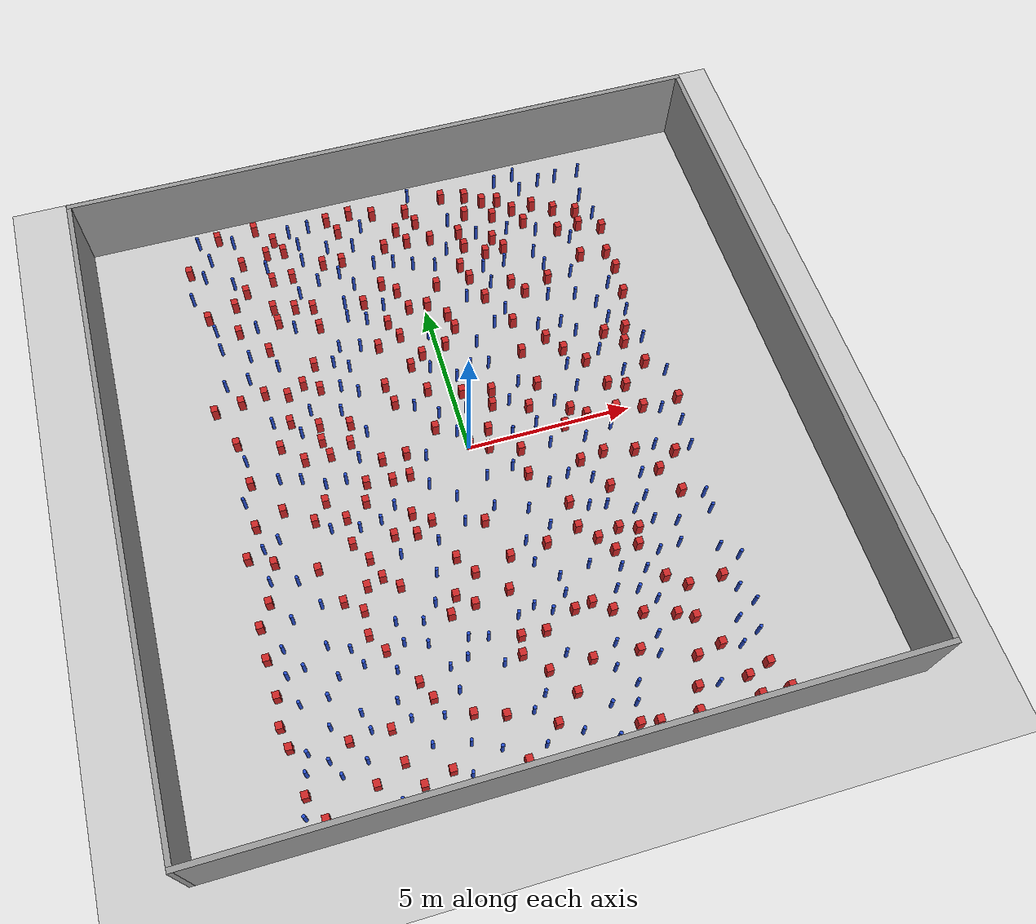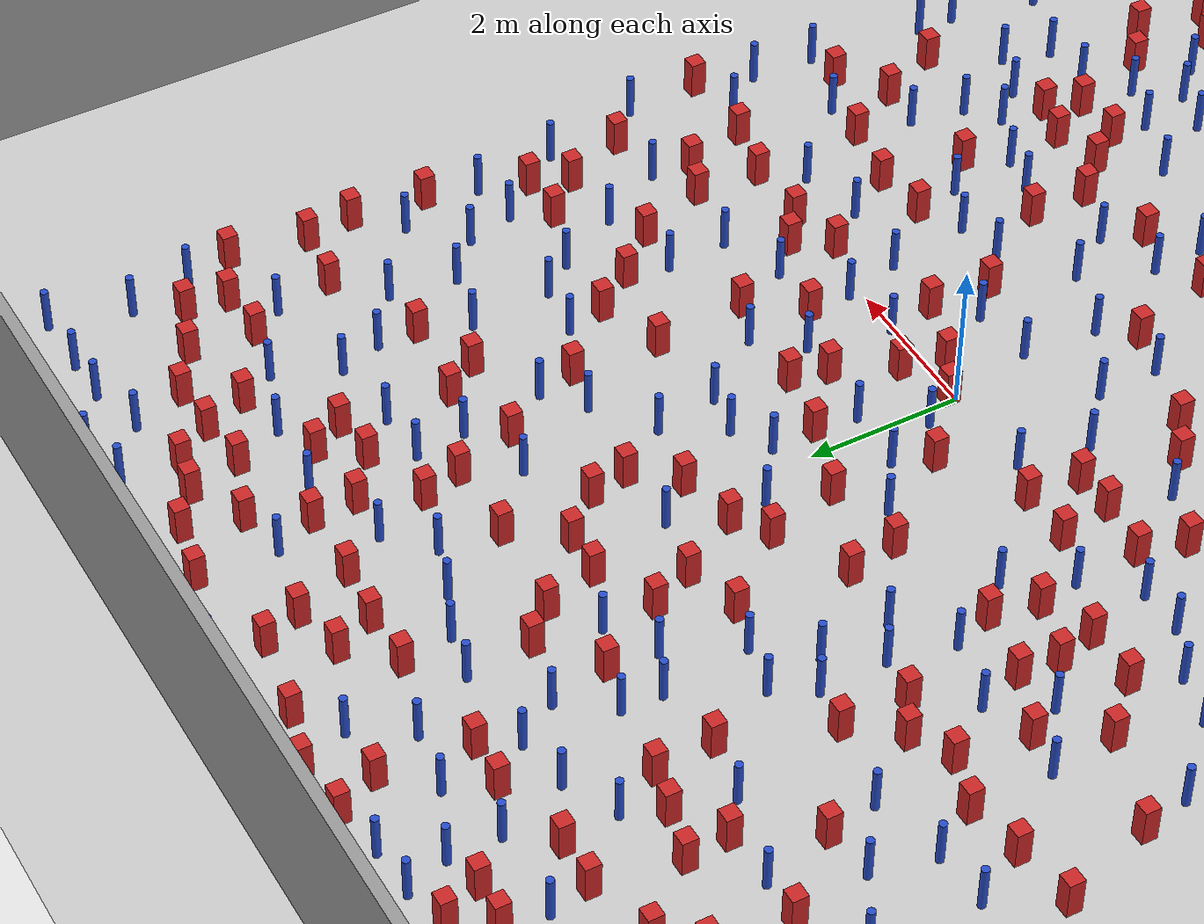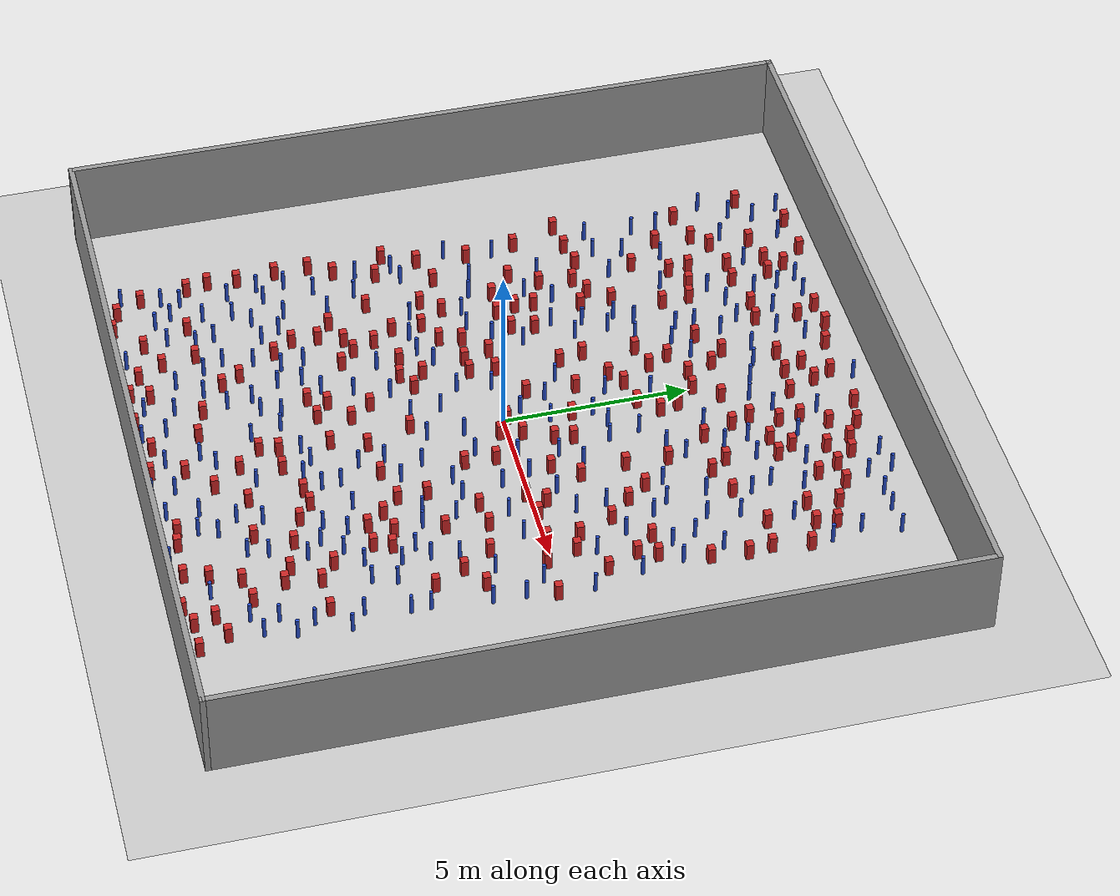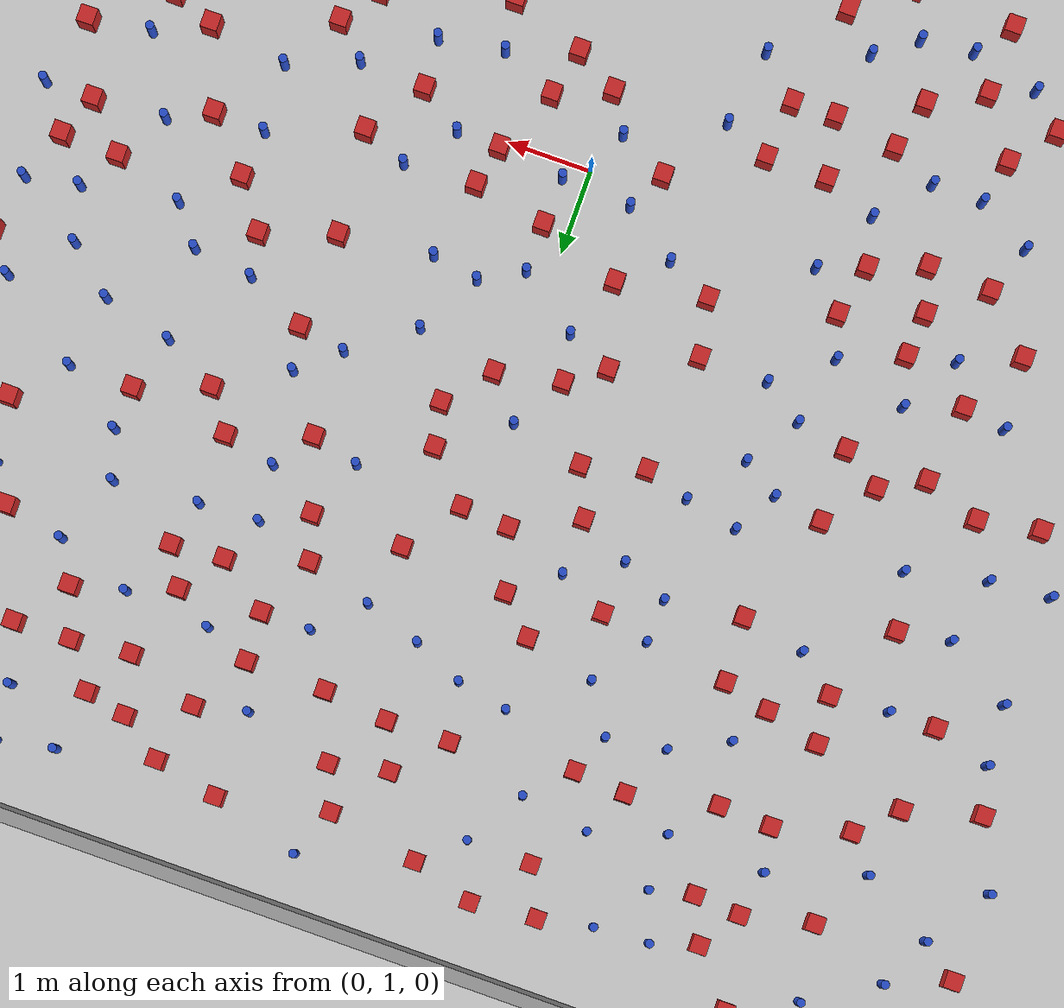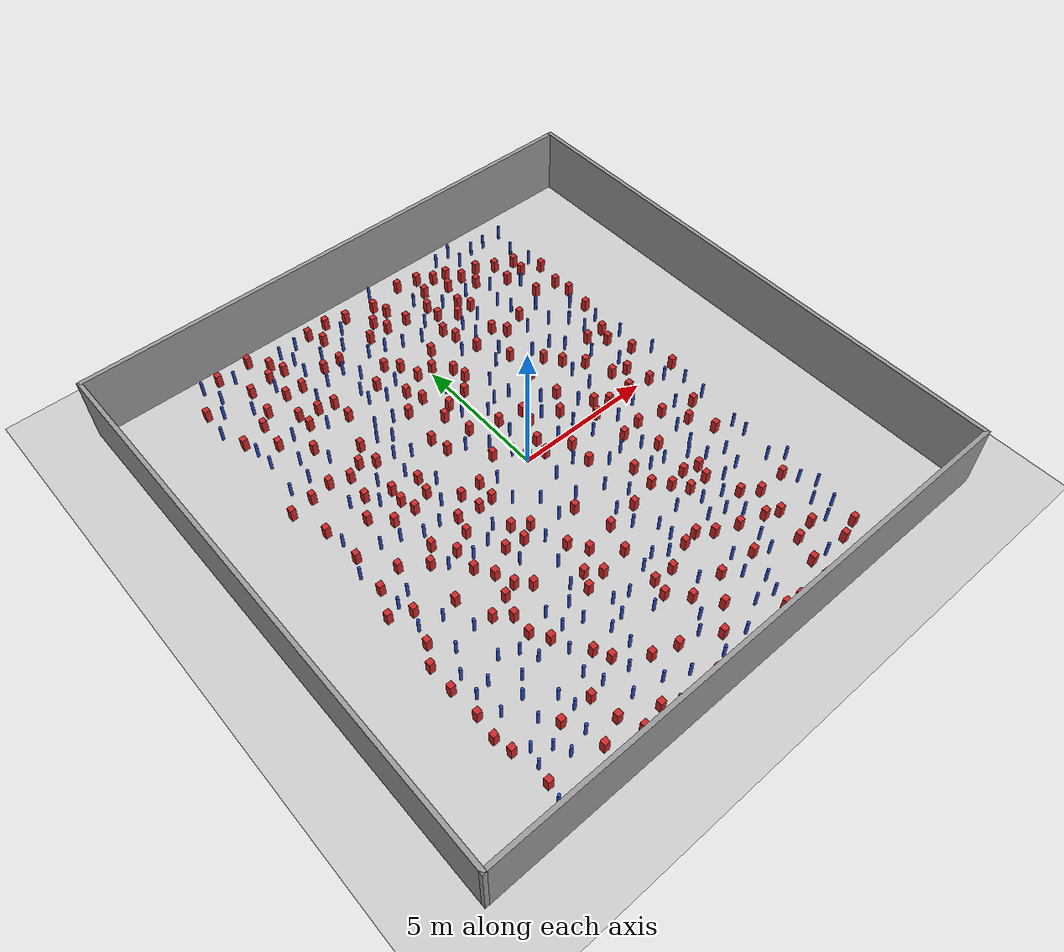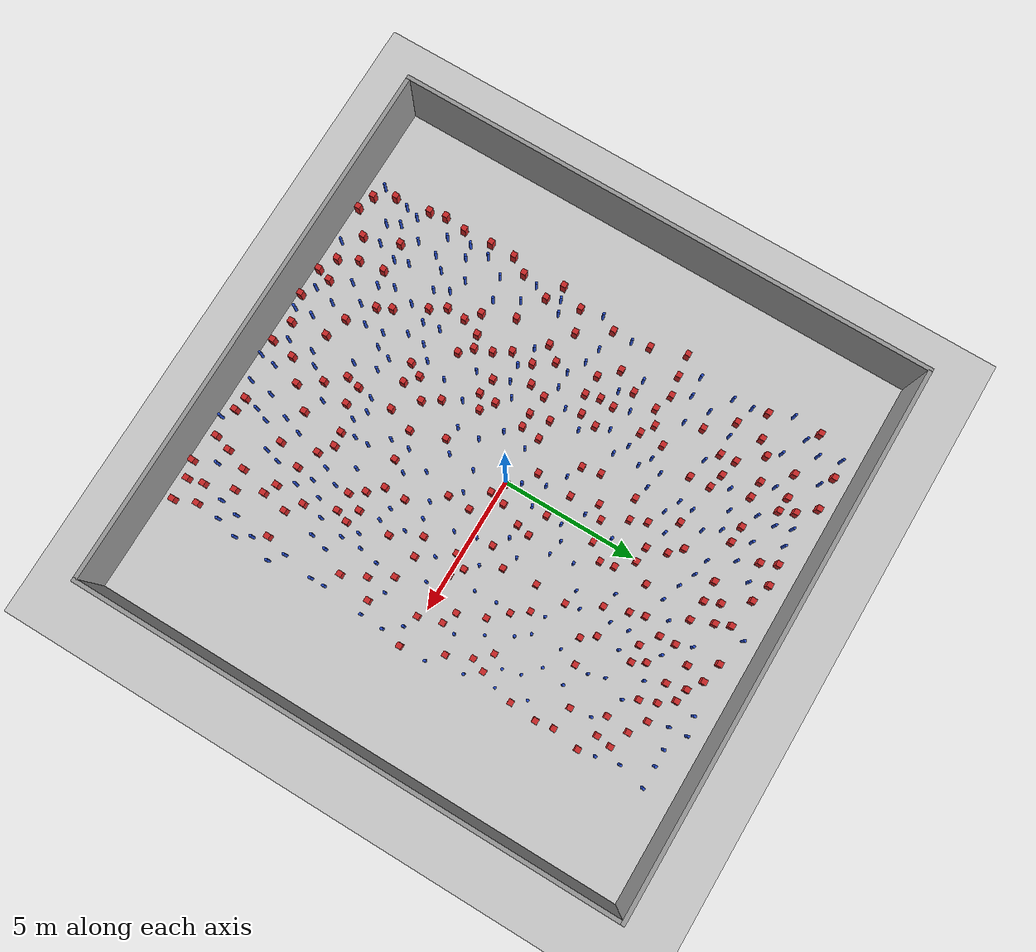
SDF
<sdf version="1.6">
 <world name="default">
  <light name="sun" type="directional">
   <pose>0 0 1000 0 -0 0</pose>
   <diffuse>0.8 0.8 0.8 1</diffuse>
   <specular>0.1 0.1 0.1 1</specular>
   <attenuation>
    <range>1000</range>
    <constant>0.9</constant>
    <linear>0.01</linear>
    <quadratic>0.001</quadratic>
   </attenuation>
   <direction>-0.5 0.5 -1</direction>
  </light>
  <model name="ground_plane">
   <static>1</static>
   <link name="link">
    <collision name="collision">
     <geometry><plane><normal>0 0 1</normal><size>100 100</size></plane></geometry>
     <surface><friction><ode><mu>100</mu><mu2>50</mu2></ode></friction></surface>
    </collision>
    <visual name="visual">
     <cast_shadows>0</cast_shadows>
     <geometry><plane><normal>0 0 1</normal><size>100 100</size></plane></geometry>
     <material>
      <ambient>1.0 1.0 1.0 1.0</ambient>
      <diffuse>0.8 0.8 0.8 1.0</diffuse>
      <specular>0.01 0.01 0.01 1.000000</specular>
     </material>
    </visual>
   </link>
  </model>
  <gravity>0 0 -9.8</gravity>
  <magnetic_field>6e-06 2.3e-05 -4.2e-05</magnetic_field>
  <atmosphere type="adiabatic"/>
  <physics name="default_physics" default="0" type="ode">
   <max_step_size>0.001</max_step_size>
   <real_time_factor>1</real_time_factor>
   <real_time_update_rate>1000</real_time_update_rate>
  </physics>
  <scene><ambient>0.4 0.4 0.4 1</ambient><background>0.7 0.7 0.7 1</background><shadows>1</shadows></scene>
  <spherical_coordinates>
   <surface_model>EARTH_WGS84</surface_model>
   <latitude_deg>0</latitude_deg>
   <longitude_deg>0</longitude_deg>
   <elevation>0</elevation>
   <heading_deg>0</heading_deg>
  </spherical_coordinates>
  <plugin name="gazebo_occupancy_map" filename="libgazebo_2Dmap_plugin.so">
   <map_resolution>0.05</map_resolution>
   <map_topic>generated_map</map_topic>
   <map_height>0.01</map_height>
   <map_size_x>50</map_size_x>
   <map_size_y>50</map_size_y>
  </plugin>
  <model name="NamedLocations">
   <static>true</static>
   <link name="DefaultStart"><pose>8.5 0 0 0 0 3.14</pose></link>
  </model>
  <model name="20x20_walls">
   <pose>0.044518 0.176112 0 0 -0 0</pose>
   <link name="Wall_1">
    <collision name="Wall_1_Collision">
     <geometry><box><size>20 0.15 2.5</size></box></geometry>
     <pose>0 0 1.25 0 -0 0</pose>
    </collision>
    <visual name="Wall_1_Visual">
     <pose>0 0 1.25 0 -0 0</pose>
     <geometry><box><size>20 0.15 2.5</size></box></geometry>
     <material>
      <script><uri>file://media/materials/scripts/gazebo.material</uri><name>Gazebo/Grey</name></script>
      <ambient>0.976471 0.992157 1 1</ambient>
     </material>
     <meta><layer>0</layer></meta>
    </visual>
    <pose>0 9.925 0 0 -0 0</pose>
   </link>
   <link name="Wall_3">
    <collision name="Wall_3_Collision">
     <geometry><box><size>20 0.15 2.5</size></box></geometry>
     <pose>0 0 1.25 0 -0 0</pose>
    </collision>
    <visual name="Wall_3_Visual">
     <pose>0 0 1.25 0 -0 0</pose>
     <geometry><box><size>20 0.15 2.5</size></box></geometry>
     <material>
      <script><uri>file://media/materials/scripts/gazebo.material</uri><name>Gazebo/Grey</name></script>
      <ambient>0.976471 0.992157 1 1</ambient>
     </material>
     <meta><layer>0</layer></meta>
    </visual>
    <pose>9.925 0 0 0 0 -1.5708</pose>
   </link>
   <link name="Wall_4">
    <collision name="Wall_4_Collision">
     <geometry><box><size>20 0.15 2.5</size></box></geometry>
     <pose>0 0 1.25 0 -0 0</pose>
    </collision>
    <visual name="Wall_4_Visual">
     <pose>0 0 1.25 0 -0 0</pose>
     <geometry><box><size>20 0.15 2.5</size></box></geometry>
     <material>
      <script><uri>file://media/materials/scripts/gazebo.material</uri><name>Gazebo/Grey</name></script>
      <ambient>0.976471 0.992157 1 1</ambient>
     </material>
     <meta><layer>0</layer></meta>
    </visual>
    <pose>0 -9.925 0 0 -0 3.14159</pose>
   </link>
   <link name="Wall_5">
    <collision name="Wall_5_Collision">
     <geometry><box><size>20 0.15 2.5</size></box></geometry>
     <pose>0 0 1.25 0 -0 0</pose>
    </collision>
    <visual name="Wall_5_Visual">
     <pose>0 0 1.25 0 -0 0</pose>
     <geometry><box><size>20 0.15 2.5</size></box></geometry>
     <material>
      <script><uri>file://media/materials/scripts/gazebo.material</uri><name>Gazebo/Grey</name></script>
      <ambient>0.976471 0.992157 1 1</ambient>
     </material>
     <meta><layer>0</layer></meta>
    </visual>
    <pose>-9.925 0 0 0 -0 1.5708</pose>
   </link>
   <static>1</static>
  </model>
  <model name="square_post_obstacle0">
   <static>true</static>
   <pose>-6.99141745238 3.09355268287 1.91545236811e-07 -7.35059704564e-06 1.12565212e-07 2.39332434364e-05</pose>
   <link name="link">
    <pose>0 0 0.25 0 -0 0</pose>
    <inertial>
     <mass>100</mass>
     <inertia>
      <ixx>0.166667</ixx>
      <ixy>0</ixy>
      <ixz>0</ixz>
      <iyy>0.166667</iyy>
      <iyz>0</iyz>
      <izz>0.166667</izz>
     </inertia>
    </inertial>
    <collision name="collision"><geometry><box><size>.2 .2 .5</size></box></geometry></collision>
    <visual name="visual">
     <geometry><box><size>.2 .2 .5</size></box></geometry>
     <material>
      <script><name>Gazebo/Red</name><uri>file://media/materials/scripts/gazebo.material</uri></script>
     </material>
    </visual>
   </link>
  </model>
  <model name="square_post_obstacle1">
   <static>true</static>
   <pose>1.93483084903 4.93488205494 1.91545236811e-07 -7.35059704564e-06 1.12565212e-07 2.39332434364e-05</pose>
   <link name="link">
    <pose>0 0 0.25 0 -0 0</pose>
    <inertial>
     <mass>100</mass>
     <inertia>
      <ixx>0.166667</ixx>
      <ixy>0</ixy>
      <ixz>0</ixz>
      <iyy>0.166667</iyy>
      <iyz>0</iyz>
      <izz>0.166667</izz>
     </inertia>
    </inertial>
    <collision name="collision"><geometry><box><size>.2 .2 .5</size></box></geometry></collision>
    <visual name="visual">
     <geometry><box><size>.2 .2 .5</size></box></geometry>
     <material>
      <script><name>Gazebo/Red</name><uri>file://media/materials/scripts/gazebo.material</uri></script>
     </material>
    </visual>
   </link>
  </model>
  <model name="pole_obstacle0">
   <static>true</static>
   <pose>2.21565794026 -4.52919180327 7.38925637345e-09 -8.47170692798e-08 1.24976765033e-08 -1.74513093019e-07</pose>
   <link name="link">
    <pose>0 0 0.3 0 -0 0</pose>
    <inertial>
     <mass>1</mass>
     <inertia><ixx>0.145833</ixx><ixy>0</ixy><ixz>0</ixz><iyy>0.145833</iyy><iyz>0</iyz><izz>0.125</izz></inertia>
    </inertial>
    <collision name="collision">
     <geometry><cylinder><radius>0.05</radius><length>.6</length></cylinder></geometry>
    </collision>
    <visual name="visual">
     <geometry><cylinder><radius>0.05</radius><length>.6</length></cylinder></geometry>
     <material>
      <script><name>Gazebo/Blue</name><uri>file://media/materials/scripts/gazebo.material</uri></script>
     </material>
    </visual>
   </link>
  </model>
  <model name="square_post_obstacle2">
   <static>true</static>
   <pose>0.0900470342076 5.1326568709 1.91545236811e-07 -7.35059704564e-06 1.12565212e-07 2.39332434364e-05</pose>
   <link name="link">
    <pose>0 0 0.25 0 -0 0</pose>
    <inertial>
     <mass>100</mass>
     <inertia>
      <ixx>0.166667</ixx>
      <ixy>0</ixy>
      <ixz>0</ixz>
      <iyy>0.166667</iyy>
      <iyz>0</iyz>
      <izz>0.166667</izz>
     </inertia>
    </inertial>
    <collision name="collision"><geometry><box><size>.2 .2 .5</size></box></geometry></collision>
    <visual name="visual">
     <geometry><box><size>.2 .2 .5</size></box></geometry>
     <material>
      <script><name>Gazebo/Red</name><uri>file://media/materials/scripts/gazebo.material</uri></script>
     </material>
    </visual>
   </link>
  </model>
  <model name="pole_obstacle1">
   <static>true</static>
   <pose>3.22779918112 3.45898310527 7.38925637345e-09 -8.47170692798e-08 1.24976764939e-08 -1.74513093025e-07</pose>
   <link name="link">
    <pose>0 0 0.3 0 -0 0</pose>
    <inertial>
     <mass>1</mass>
     <inertia><ixx>0.145833</ixx><ixy>0</ixy><ixz>0</ixz><iyy>0.145833</iyy><iyz>0</iyz><izz>0.125</izz></inertia>
    </inertial>
    <collision name="collision">
     <geometry><cylinder><radius>0.05</radius><length>.6</length></cylinder></geometry>
    </collision>
    <visual name="visual">
     <geometry><cylinder><radius>0.05</radius><length>.6</length></cylinder></geometry>
     <material>
      <script><name>Gazebo/Blue</name><uri>file://media/materials/scripts/gazebo.material</uri></script>
     </material>
    </visual>
   </link>
  </model>
  <model name="square_post_obstacle3">
   <static>true</static>
   <pose>-1.81873640743 5.73639416817 1.91545236811e-07 -7.35059704564e-06 1.12565212e-07 2.39332434364e-05</pose>
   <link name="link">
    <pose>0 0 0.25 0 -0 0</pose>
    <inertial>
     <mass>100</mass>
     <inertia>
      <ixx>0.166667</ixx>
      <ixy>0</ixy>
      <ixz>0</ixz>
      <iyy>0.166667</iyy>
      <iyz>0</iyz>
      <izz>0.166667</izz>
     </inertia>
    </inertial>
    <collision name="collision"><geometry><box><size>.2 .2 .5</size></box></geometry></collision>
    <visual name="visual">
     <geometry><box><size>.2 .2 .5</size></box></geometry>
     <material>
      <script><name>Gazebo/Red</name><uri>file://media/materials/scripts/gazebo.material</uri></script>
     </material>
    </visual>
   </link>
  </model>
  <model name="pole_obstacle2">
   <static>true</static>
   <pose>-5.23044273879 5.70537169708 7.38925637345e-09 -8.47170692796e-08 1.24976764786e-08 -1.74513093032e-07</pose>
   <link name="link">
    <pose>0 0 0.3 0 -0 0</pose>
    <inertial>
     <mass>1</mass>
     <inertia><ixx>0.145833</ixx><ixy>0</ixy><ixz>0</ixz><iyy>0.145833</iyy><iyz>0</iyz><izz>0.125</izz></inertia>
    </inertial>
    <collision name="collision">
     <geometry><cylinder><radius>0.05</radius><length>.6</length></cylinder></geometry>
    </collision>
    <visual name="visual">
     <geometry><cylinder><radius>0.05</radius><length>.6</length></cylinder></geometry>
     <material>
      <script><name>Gazebo/Blue</name><uri>file://media/materials/scripts/gazebo.material</uri></script>
     </material>
    </visual>
   </link>
  </model>
  <model name="pole_obstacle3">
   <static>true</static>
   <pose>-5.2181728807 -5.75392112804 7.38925637345e-09 -8.47170692796e-08 1.24976764786e-08 -1.74513093032e-07</pose>
   <link name="link">
    <pose>0 0 0.3 0 -0 0</pose>
    <inertial>
     <mass>1</mass>
     <inertia><ixx>0.145833</ixx><ixy>0</ixy><ixz>0</ixz><iyy>0.145833</iyy><iyz>0</iyz><izz>0.125</izz></inertia>
    </inertial>
    <collision name="collision">
     <geometry><cylinder><radius>0.05</radius><length>.6</length></cylinder></geometry>
    </collision>
    <visual name="visual">
     <geometry><cylinder><radius>0.05</radius><length>.6</length></cylinder></geometry>
     <material>
      <script><name>Gazebo/Blue</name><uri>file://media/materials/scripts/gazebo.material</uri></script>
     </material>
    </visual>
   </link>
  </model>
  <model name="square_post_obstacle4">
   <static>true</static>
   <pose>-3.33328739568 1.01868813255 1.91545236811e-07 -7.35059704564e-06 1.12565212e-07 2.39332434364e-05</pose>
   <link name="link">
    <pose>0 0 0.25 0 -0 0</pose>
    <inertial>
     <mass>100</mass>
     <inertia>
      <ixx>0.166667</ixx>
      <ixy>0</ixy>
      <ixz>0</ixz>
      <iyy>0.166667</iyy>
      <iyz>0</iyz>
      <izz>0.166667</izz>
     </inertia>
    </inertial>
    <collision name="collision"><geometry><box><size>.2 .2 .5</size></box></geometry></collision>
    <visual name="visual">
     <geometry><box><size>.2 .2 .5</size></box></geometry>
     <material>
      <script><name>Gazebo/Red</name><uri>file://media/materials/scripts/gazebo.material</uri></script>
     </material>
    </visual>
   </link>
  </model>
  <model name="square_post_obstacle5">
   <static>true</static>
   <pose>-0.152788292442 8.22200707512 1.91545236811e-07 -7.35059704564e-06 1.12565212e-07 2.39332434364e-05</pose>
   <link name="link">
    <pose>0 0 0.25 0 -0 0</pose>
    <inertial>
     <mass>100</mass>
     <inertia>
      <ixx>0.166667</ixx>
      <ixy>0</ixy>
      <ixz>0</ixz>
      <iyy>0.166667</iyy>
      <iyz>0</iyz>
      <izz>0.166667</izz>
     </inertia>
    </inertial>
    <collision name="collision"><geometry><box><size>.2 .2 .5</size></box></geometry></collision>
    <visual name="visual">
     <geometry><box><size>.2 .2 .5</size></box></geometry>
     <material>
      <script><name>Gazebo/Red</name><uri>file://media/materials/scripts/gazebo.material</uri></script>
     </material>
    </visual>
   </link>
  </model>
  <model name="square_post_obstacle6">
   <static>true</static>
   <pose>4.19397803059 -7.79593821687 1.91545236811e-07 -7.35059704564e-06 1.12565212e-07 2.39332434364e-05</pose>
   <link name="link">
    <pose>0 0 0.25 0 -0 0</pose>
    <inertial>
     <mass>100</mass>
     <inertia>
      <ixx>0.166667</ixx>
      <ixy>0</ixy>
      <ixz>0</ixz>
      <iyy>0.166667</iyy>
      <iyz>0</iyz>
      <izz>0.166667</izz>
     </inertia>
    </inertial>
    <collision name="collision"><geometry><box><size>.2 .2 .5</size></box></geometry></collision>
    <visual name="visual">
     <geometry><box><size>.2 .2 .5</size></box></geometry>
     <material>
      <script><name>Gazebo/Red</name><uri>file://media/materials/scripts/gazebo.material</uri></script>
     </material>
    </visual>
   </link>
  </model>
  <model name="pole_obstacle4">
   <static>true</static>
   <pose>5.06345819993 -3.96751230476 7.38925637345e-09 -8.47170692799e-08 1.24976764984e-08 -1.7451309302e-07</pose>
   <link name="link">
    <pose>0 0 0.3 0 -0 0</pose>
    <inertial>
     <mass>1</mass>
     <inertia><ixx>0.145833</ixx><ixy>0</ixy><ixz>0</ixz><iyy>0.145833</iyy><iyz>0</iyz><izz>0.125</izz></inertia>
    </inertial>
    <collision name="collision">
     <geometry><cylinder><radius>0.05</radius><length>.6</length></cylinder></geometry>
    </collision>
    <visual name="visual">
     <geometry><cylinder><radius>0.05</radius><length>.6</length></cylinder></geometry>
     <material>
      <script><name>Gazebo/Blue</name><uri>file://media/materials/scripts/gazebo.material</uri></script>
     </material>
    </visual>
   </link>
  </model>
  <model name="pole_obstacle5">
   <static>true</static>
   <pose>-3.1833879127 2.95267589487 7.38925637345e-09 -8.47170692798e-08 1.24976764939e-08 -1.74513093025e-07</pose>
   <link name="link">
    <pose>0 0 0.3 0 -0 0</pose>
    <inertial>
     <mass>1</mass>
     <inertia><ixx>0.145833</ixx><ixy>0</ixy><ixz>0</ixz><iyy>0.145833</iyy><iyz>0</iyz><izz>0.125</izz></inertia>
    </inertial>
    <collision name="collision">
     <geometry><cylinder><radius>0.05</radius><length>.6</length></cylinder></geometry>
    </collision>
    <visual name="visual">
     <geometry><cylinder><radius>0.05</radius><length>.6</length></cylinder></geometry>
     <material>
      <script><name>Gazebo/Blue</name><uri>file://media/materials/scripts/gazebo.material</uri></script>
     </material>
    </visual>
   </link>
  </model>
  <model name="square_post_obstacle7">
   <static>true</static>
   <pose>-4.78033656752 3.09208224334 1.91545236811e-07 -7.35059704564e-06 1.12565212e-07 2.39332434364e-05</pose>
   <link name="link">
    <pose>0 0 0.25 0 -0 0</pose>
    <inertial>
     <mass>100</mass>
     <inertia>
      <ixx>0.166667</ixx>
      <ixy>0</ixy>
      <ixz>0</ixz>
      <iyy>0.166667</iyy>
      <iyz>0</iyz>
      <izz>0.166667</izz>
     </inertia>
    </inertial>
    <collision name="collision"><geometry><box><size>.2 .2 .5</size></box></geometry></collision>
    <visual name="visual">
     <geometry><box><size>.2 .2 .5</size></box></geometry>
     <material>
      <script><name>Gazebo/Red</name><uri>file://media/materials/scripts/gazebo.material</uri></script>
     </material>
    </visual>
   </link>
  </model>
  <model name="square_post_obstacle8">
   <static>true</static>
   <pose>6.26625109611 -9.26206873367 1.91545236811e-07 -7.35059704564e-06 1.12565212e-07 2.39332434364e-05</pose>
   <link name="link">
    <pose>0 0 0.25 0 -0 0</pose>
    <inertial>
     <mass>100</mass>
     <inertia>
      <ixx>0.166667</ixx>
      <ixy>0</ixy>
      <ixz>0</ixz>
      <iyy>0.166667</iyy>
      <iyz>0</iyz>
      <izz>0.166667</izz>
     </inertia>
    </inertial>
    <collision name="collision"><geometry><box><size>.2 .2 .5</size></box></geometry></collision>
    <visual name="visual">
     <geometry><box><size>.2 .2 .5</size></box></geometry>
     <material>
      <script><name>Gazebo/Red</name><uri>file://media/materials/scripts/gazebo.material</uri></script>
     </material>
    </visual>
   </link>
  </model>
  <model name="pole_obstacle6">
   <static>true</static>
   <pose>5.24686441359 3.76029672284 7.38925637345e-09 -8.47170692798e-08 1.24976764937e-08 -1.74513093023e-07</pose>
   <link name="link">
    <pose>0 0 0.3 0 -0 0</pose>
    <inertial>
     <mass>1</mass>
     <inertia><ixx>0.145833</ixx><ixy>0</ixy><ixz>0</ixz><iyy>0.145833</iyy><iyz>0</iyz><izz>0.125</izz></inertia>
    </inertial>
    <collision name="collision">
     <geometry><cylinder><radius>0.05</radius><length>.6</length></cylinder></geometry>
    </collision>
    <visual name="visual">
     <geometry><cylinder><radius>0.05</radius><length>.6</length></cylinder></geometry>
     <material>
      <script><name>Gazebo/Blue</name><uri>file://media/materials/scripts/gazebo.material</uri></script>
     </material>
    </visual>
   </link>
  </model>
  <model name="pole_obstacle7">
   <static>true</static>
   <pose>-6.45998236298 -2.63384797095 7.38925637345e-09 -8.47170692798e-08 1.24976764937e-08 -1.74513093023e-07</pose>
   <link name="link">
    <pose>0 0 0.3 0 -0 0</pose>
    <inertial>
     <mass>1</mass>
     <inertia><ixx>0.145833</ixx><ixy>0</ixy><ixz>0</ixz><iyy>0.145833</iyy><iyz>0</iyz><izz>0.125</izz></inertia>
    </inertial>
    <collision name="collision">
     <geometry><cylinder><radius>0.05</radius><length>.6</length></cylinder></geometry>
    </collision>
    <visual name="visual">
     <geometry><cylinder><radius>0.05</radius><length>.6</length></cylinder></geometry>
     <material>
      <script><name>Gazebo/Blue</name><uri>file://media/materials/scripts/gazebo.material</uri></script>
     </material>
    </visual>
   </link>
  </model>
  <model name="square_post_obstacle9">
   <static>true</static>
   <pose>-0.674670861115 7.68431918439 1.91545236811e-07 -7.35059704564e-06 1.12565212e-07 2.39332434364e-05</pose>
   <link name="link">
    <pose>0 0 0.25 0 -0 0</pose>
    <inertial>
     <mass>100</mass>
     <inertia>
      <ixx>0.166667</ixx>
      <ixy>0</ixy>
      <ixz>0</ixz>
      <iyy>0.166667</iyy>
      <iyz>0</iyz>
      <izz>0.166667</izz>
     </inertia>
    </inertial>
    <collision name="collision"><geometry><box><size>.2 .2 .5</size></box></geometry></collision>
    <visual name="visual">
     <geometry><box><size>.2 .2 .5</size></box></geometry>
     <material>
      <script><name>Gazebo/Red</name><uri>file://media/materials/scripts/gazebo.material</uri></script>
     </material>
    </visual>
   </link>
  </model>
  <model name="square_post_obstacle10">
   <static>true</static>
   <pose>-4.59014025202 9.49769332026 1.91545236811e-07 -7.35059704564e-06 1.12565212e-07 2.39332434364e-05</pose>
   <link name="link">
    <pose>0 0 0.25 0 -0 0</pose>
    <inertial>
     <mass>100</mass>
     <inertia>
      <ixx>0.166667</ixx>
      <ixy>0</ixy>
      <ixz>0</ixz>
      <iyy>0.166667</iyy>
      <iyz>0</iyz>
      <izz>0.166667</izz>
     </inertia>
    </inertial>
    <collision name="collision"><geometry><box><size>.2 .2 .5</size></box></geometry></collision>
    <visual name="visual">
     <geometry><box><size>.2 .2 .5</size></box></geometry>
     <material>
      <script><name>Gazebo/Red</name><uri>file://media/materials/scripts/gazebo.material</uri></script>
     </material>
    </visual>
   </link>
  </model>
  <model name="square_post_obstacle11">
   <static>true</static>
   <pose>5.7341250689 7.40073843208 1.91545236811e-07 -7.35059704564e-06 1.12565212e-07 2.39332434364e-05</pose>
   <link name="link">
    <pose>0 0 0.25 0 -0 0</pose>
    <inertial>
     <mass>100</mass>
     <inertia>
      <ixx>0.166667</ixx>
      <ixy>0</ixy>
      <ixz>0</ixz>
      <iyy>0.166667</iyy>
      <iyz>0</iyz>
      <izz>0.166667</izz>
     </inertia>
    </inertial>
    <collision name="collision"><geometry><box><size>.2 .2 .5</size></box></geometry></collision>
    <visual name="visual">
     <geometry><box><size>.2 .2 .5</size></box></geometry>
     <material>
      <script><name>Gazebo/Red</name><uri>file://media/materials/scripts/gazebo.material</uri></script>
     </material>
    </visual>
   </link>
  </model>
  <model name="square_post_obstacle12">
   <static>true</static>
   <pose>1.49668909736 6.29393075869 1.91545236811e-07 -7.35059704564e-06 1.12565212e-07 2.39332434364e-05</pose>
   <link name="link">
    <pose>0 0 0.25 0 -0 0</pose>
    <inertial>
     <mass>100</mass>
     <inertia>
      <ixx>0.166667</ixx>
      <ixy>0</ixy>
      <ixz>0</ixz>
      <iyy>0.166667</iyy>
      <iyz>0</iyz>
      <izz>0.166667</izz>
     </inertia>
    </inertial>
    <collision name="collision"><geometry><box><size>.2 .2 .5</size></box></geometry></collision>
    <visual name="visual">
     <geometry><box><size>.2 .2 .5</size></box></geometry>
     <material>
      <script><name>Gazebo/Red</name><uri>file://media/materials/scripts/gazebo.material</uri></script>
     </material>
    </visual>
   </link>
  </model>
  <model name="square_post_obstacle13">
   <static>true</static>
   <pose>0.772211470827 -7.86731333248 1.91545236811e-07 -7.35059704564e-06 1.12565212e-07 2.39332434364e-05</pose>
   <link name="link">
    <pose>0 0 0.25 0 -0 0</pose>
    <inertial>
     <mass>100</mass>
     <inertia>
      <ixx>0.166667</ixx>
      <ixy>0</ixy>
      <ixz>0</ixz>
      <iyy>0.166667</iyy>
      <iyz>0</iyz>
      <izz>0.166667</izz>
     </inertia>
    </inertial>
    <collision name="collision"><geometry><box><size>.2 .2 .5</size></box></geometry></collision>
    <visual name="visual">
     <geometry><box><size>.2 .2 .5</size></box></geometry>
     <material>
      <script><name>Gazebo/Red</name><uri>file://media/materials/scripts/gazebo.material</uri></script>
     </material>
    </visual>
   </link>
  </model>
  <model name="pole_obstacle8">
   <static>true</static>
   <pose>4.43319757617 -3.71783626393 7.38925637345e-09 -8.47170692798e-08 1.24976764937e-08 -1.74513093023e-07</pose>
   <link name="link">
    <pose>0 0 0.3 0 -0 0</pose>
    <inertial>
     <mass>1</mass>
     <inertia><ixx>0.145833</ixx><ixy>0</ixy><ixz>0</ixz><iyy>0.145833</iyy><iyz>0</iyz><izz>0.125</izz></inertia>
    </inertial>
    <collision name="collision">
     <geometry><cylinder><radius>0.05</radius><length>.6</length></cylinder></geometry>
    </collision>
    <visual name="visual">
     <geometry><cylinder><radius>0.05</radius><length>.6</length></cylinder></geometry>
     <material>
      <script><name>Gazebo/Blue</name><uri>file://media/materials/scripts/gazebo.material</uri></script>
     </material>
    </visual>
   </link>
  </model>
  <model name="square_post_obstacle14">
   <static>true</static>
   <pose>-3.72956606277 -9.08440619244 1.91545236811e-07 -7.35059704564e-06 1.12565212e-07 2.39332434364e-05</pose>
   <link name="link">
    <pose>0 0 0.25 0 -0 0</pose>
    <inertial>
     <mass>100</mass>
     <inertia>
      <ixx>0.166667</ixx>
      <ixy>0</ixy>
      <ixz>0</ixz>
      <iyy>0.166667</iyy>
      <iyz>0</iyz>
      <izz>0.166667</izz>
     </inertia>
    </inertial>
    <collision name="collision"><geometry><box><size>.2 .2 .5</size></box></geometry></collision>
    <visual name="visual">
     <geometry><box><size>.2 .2 .5</size></box></geometry>
     <material>
      <script><name>Gazebo/Red</name><uri>file://media/materials/scripts/gazebo.material</uri></script>
     </material>
    </visual>
   </link>
  </model>
  <model name="square_post_obstacle15">
   <static>true</static>
   <pose>-0.140066669585 -4.63006801939 1.91545236811e-07 -7.35059704564e-06 1.12565212e-07 2.39332434364e-05</pose>
   <link name="link">
    <pose>0 0 0.25 0 -0 0</pose>
    <inertial>
     <mass>100</mass>
     <inertia>
      <ixx>0.166667</ixx>
      <ixy>0</ixy>
      <ixz>0</ixz>
      <iyy>0.166667</iyy>
      <iyz>0</iyz>
      <izz>0.166667</izz>
     </inertia>
    </inertial>
    <collision name="collision"><geometry><box><size>.2 .2 .5</size></box></geometry></collision>
    <visual name="visual">
     <geometry><box><size>.2 .2 .5</size></box></geometry>
     <material>
      <script><name>Gazebo/Red</name><uri>file://media/materials/scripts/gazebo.material</uri></script>
     </material>
    </visual>
   </link>
  </model>
  <model name="square_post_obstacle16">
   <static>true</static>
   <pose>-2.15949539895 -1.69913952789 1.91545236811e-07 -7.35059704564e-06 1.12565212e-07 2.39332434364e-05</pose>
   <link name="link">
    <pose>0 0 0.25 0 -0 0</pose>
    <inertial>
     <mass>100</mass>
     <inertia>
      <ixx>0.166667</ixx>
      <ixy>0</ixy>
      <ixz>0</ixz>
      <iyy>0.166667</iyy>
      <iyz>0</iyz>
      <izz>0.166667</izz>
     </inertia>
    </inertial>
    <collision name="collision"><geometry><box><size>.2 .2 .5</size></box></geometry></collision>
    <visual name="visual">
     <geometry><box><size>.2 .2 .5</size></box></geometry>
     <material>
      <script><name>Gazebo/Red</name><uri>file://media/materials/scripts/gazebo.material</uri></script>
     </material>
    </visual>
   </link>
  </model>
  <model name="pole_obstacle9">
   <static>true</static>
   <pose>-1.06666744541 -5.77174144234 7.38925637345e-09 -8.47170692799e-08 1.24976765033e-08 -1.74513093018e-07</pose>
   <link name="link">
    <pose>0 0 0.3 0 -0 0</pose>
    <inertial>
     <mass>1</mass>
     <inertia><ixx>0.145833</ixx><ixy>0</ixy><ixz>0</ixz><iyy>0.145833</iyy><iyz>0</iyz><izz>0.125</izz></inertia>
    </inertial>
    <collision name="collision">
     <geometry><cylinder><radius>0.05</radius><length>.6</length></cylinder></geometry>
    </collision>
    <visual name="visual">
     <geometry><cylinder><radius>0.05</radius><length>.6</length></cylinder></geometry>
     <material>
      <script><name>Gazebo/Blue</name><uri>file://media/materials/scripts/gazebo.material</uri></script>
     </material>
    </visual>
   </link>
  </model>
  <model name="square_post_obstacle17">
   <static>true</static>
   <pose>-1.90918752012 -0.480530397075 1.91545236811e-07 -7.35059704564e-06 1.12565212e-07 2.39332434364e-05</pose>
   <link name="link">
    <pose>0 0 0.25 0 -0 0</pose>
    <inertial>
     <mass>100</mass>
     <inertia>
      <ixx>0.166667</ixx>
      <ixy>0</ixy>
      <ixz>0</ixz>
      <iyy>0.166667</iyy>
      <iyz>0</iyz>
      <izz>0.166667</izz>
     </inertia>
    </inertial>
    <collision name="collision"><geometry><box><size>.2 .2 .5</size></box></geometry></collision>
    <visual name="visual">
     <geometry><box><size>.2 .2 .5</size></box></geometry>
     <material>
      <script><name>Gazebo/Red</name><uri>file://media/materials/scripts/gazebo.material</uri></script>
     </material>
    </visual>
   </link>
  </model>
  <model name="square_post_obstacle18">
   <static>true</static>
   <pose>0.172084083501 -3.69220295209 1.91545236811e-07 -7.35059704564e-06 1.12565212e-07 2.39332434364e-05</pose>
   <link name="link">
    <pose>0 0 0.25 0 -0 0</pose>
    <inertial>
     <mass>100</mass>
     <inertia>
      <ixx>0.166667</ixx>
      <ixy>0</ixy>
      <ixz>0</ixz>
      <iyy>0.166667</iyy>
      <iyz>0</iyz>
      <izz>0.166667</izz>
     </inertia>
    </inertial>
    <collision name="collision"><geometry><box><size>.2 .2 .5</size></box></geometry></collision>
    <visual name="visual">
     <geometry><box><size>.2 .2 .5</size></box></geometry>
     <material>
      <script><name>Gazebo/Red</name><uri>file://media/materials/scripts/gazebo.material</uri></script>
     </material>
    </visual>
   </link>
  </model>
  <model name="pole_obstacle10">
   <static>true</static>
   <pose>2.19114133356 -6.87599460677 7.38925637345e-09 -8.47170692798e-08 1.24976765033e-08 -1.74513093019e-07</pose>
   <link name="link">
    <pose>0 0 0.3 0 -0 0</pose>
    <inertial>
     <mass>1</mass>
     <inertia><ixx>0.145833</ixx><ixy>0</ixy><ixz>0</ixz><iyy>0.145833</iyy><iyz>0</iyz><izz>0.125</izz></inertia>
    </inertial>
    <collision name="collision">
     <geometry><cylinder><radius>0.05</radius><length>.6</length></cylinder></geometry>
    </collision>
    <visual name="visual">
     <geometry><cylinder><radius>0.05</radius><length>.6</length></cylinder></geometry>
     <material>
      <script><name>Gazebo/Blue</name><uri>file://media/materials/scripts/gazebo.material</uri></script>
     </material>
    </visual>
   </link>
  </model>
  <model name="square_post_obstacle19">
   <static>true</static>
   <pose>0.567349872004 -0.228023869864 1.91545236811e-07 -7.35059704564e-06 1.12565212e-07 2.39332434364e-05</pose>
   <link name="link">
    <pose>0 0 0.25 0 -0 0</pose>
    <inertial>
     <mass>100</mass>
     <inertia>
      <ixx>0.166667</ixx>
      <ixy>0</ixy>
      <ixz>0</ixz>
      <iyy>0.166667</iyy>
      <iyz>0</iyz>
      <izz>0.166667</izz>
     </inertia>
    </inertial>
    <collision name="collision"><geometry><box><size>.2 .2 .5</size></box></geometry></collision>
    <visual name="visual">
     <geometry><box><size>.2 .2 .5</size></box></geometry>
     <material>
      <script><name>Gazebo/Red</name><uri>file://media/materials/scripts/gazebo.material</uri></script>
     </material>
    </visual>
   </link>
  </model>
  <model name="pole_obstacle11">
   <static>true</static>
   <pose>-3.0121797537 6.9452448147 7.38925637345e-09 -8.47170692798e-08 1.24976765033e-08 -1.74513093019e-07</pose>
   <link name="link">
    <pose>0 0 0.3 0 -0 0</pose>
    <inertial>
     <mass>1</mass>
     <inertia><ixx>0.145833</ixx><ixy>0</ixy><ixz>0</ixz><iyy>0.145833</iyy><iyz>0</iyz><izz>0.125</izz></inertia>
    </inertial>
    <collision name="collision">
     <geometry><cylinder><radius>0.05</radius><length>.6</length></cylinder></geometry>
    </collision>
    <visual name="visual">
     <geometry><cylinder><radius>0.05</radius><length>.6</length></cylinder></geometry>
     <material>
      <script><name>Gazebo/Blue</name><uri>file://media/materials/scripts/gazebo.material</uri></script>
     </material>
    </visual>
   </link>
  </model>
  <model name="square_post_obstacle20">
   <static>true</static>
   <pose>4.65521627335 -1.47987948568 1.91545236811e-07 -7.35059704564e-06 1.12565212e-07 2.39332434364e-05</pose>
   <link name="link">
    <pose>0 0 0.25 0 -0 0</pose>
    <inertial>
     <mass>100</mass>
     <inertia>
      <ixx>0.166667</ixx>
      <ixy>0</ixy>
      <ixz>0</ixz>
      <iyy>0.166667</iyy>
      <iyz>0</iyz>
      <izz>0.166667</izz>
     </inertia>
    </inertial>
    <collision name="collision"><geometry><box><size>.2 .2 .5</size></box></geometry></collision>
    <visual name="visual">
     <geometry><box><size>.2 .2 .5</size></box></geometry>
     <material>
      <script><name>Gazebo/Red</name><uri>file://media/materials/scripts/gazebo.material</uri></script>
     </material>
    </visual>
   </link>
  </model>
  <model name="pole_obstacle12">
   <static>true</static>
   <pose>0.170691172072 -2.10585391311 7.38925637345e-09 -8.47170692792e-08 1.24976764391e-08 -1.74513093041e-07</pose>
   <link name="link">
    <pose>0 0 0.3 0 -0 0</pose>
    <inertial>
     <mass>1</mass>
     <inertia><ixx>0.145833</ixx><ixy>0</ixy><ixz>0</ixz><iyy>0.145833</iyy><iyz>0</iyz><izz>0.125</izz></inertia>
    </inertial>
    <collision name="collision">
     <geometry><cylinder><radius>0.05</radius><length>.6</length></cylinder></geometry>
    </collision>
    <visual name="visual">
     <geometry><cylinder><radius>0.05</radius><length>.6</length></cylinder></geometry>
     <material>
      <script><name>Gazebo/Blue</name><uri>file://media/materials/scripts/gazebo.material</uri></script>
     </material>
    </visual>
   </link>
  </model>
  <model name="square_post_obstacle21">
   <static>true</static>
   <pose>-5.09705463556 -2.62253193798 1.91545236811e-07 -7.35059704564e-06 1.12565212e-07 2.39332434364e-05</pose>
   <link name="link">
    <pose>0 0 0.25 0 -0 0</pose>
    <inertial>
     <mass>100</mass>
     <inertia>
      <ixx>0.166667</ixx>
      <ixy>0</ixy>
      <ixz>0</ixz>
      <iyy>0.166667</iyy>
      <iyz>0</iyz>
      <izz>0.166667</izz>
     </inertia>
    </inertial>
    <collision name="collision"><geometry><box><size>.2 .2 .5</size></box></geometry></collision>
    <visual name="visual">
     <geometry><box><size>.2 .2 .5</size></box></geometry>
     <material>
      <script><name>Gazebo/Red</name><uri>file://media/materials/scripts/gazebo.material</uri></script>
     </material>
    </visual>
   </link>
  </model>
  <model name="pole_obstacle13">
   <static>true</static>
   <pose>-5.97737935329 -1.46511551683 7.38925637345e-09 -8.471706928e-08 1.24976765134e-08 -1.74513093015e-07</pose>
   <link name="link">
    <pose>0 0 0.3 0 -0 0</pose>
    <inertial>
     <mass>1</mass>
     <inertia><ixx>0.145833</ixx><ixy>0</ixy><ixz>0</ixz><iyy>0.145833</iyy><iyz>0</iyz><izz>0.125</izz></inertia>
    </inertial>
    <collision name="collision">
     <geometry><cylinder><radius>0.05</radius><length>.6</length></cylinder></geometry>
    </collision>
    <visual name="visual">
     <geometry><cylinder><radius>0.05</radius><length>.6</length></cylinder></geometry>
     <material>
      <script><name>Gazebo/Blue</name><uri>file://media/materials/scripts/gazebo.material</uri></script>
     </material>
    </visual>
   </link>
  </model>
  <model name="square_post_obstacle22">
   <static>true</static>
   <pose>4.52502306047 -6.75875061664 1.91545236811e-07 -7.35059704564e-06 1.12565212e-07 2.39332434364e-05</pose>
   <link name="link">
    <pose>0 0 0.25 0 -0 0</pose>
    <inertial>
     <mass>100</mass>
     <inertia>
      <ixx>0.166667</ixx>
      <ixy>0</ixy>
      <ixz>0</ixz>
      <iyy>0.166667</iyy>
      <iyz>0</iyz>
      <izz>0.166667</izz>
     </inertia>
    </inertial>
    <collision name="collision"><geometry><box><size>.2 .2 .5</size></box></geometry></collision>
    <visual name="visual">
     <geometry><box><size>.2 .2 .5</size></box></geometry>
     <material>
      <script><name>Gazebo/Red</name><uri>file://media/materials/scripts/gazebo.material</uri></script>
     </material>
    </visual>
   </link>
  </model>
  <model name="pole_obstacle14">
   <static>true</static>
   <pose>1.94766628035 3.90778660255 7.38925637345e-09 -8.47170692799e-08 1.24976765053e-08 -1.74513093017e-07</pose>
   <link name="link">
    <pose>0 0 0.3 0 -0 0</pose>
    <inertial>
     <mass>1</mass>
     <inertia><ixx>0.145833</ixx><ixy>0</ixy><ixz>0</ixz><iyy>0.145833</iyy><iyz>0</iyz><izz>0.125</izz></inertia>
    </inertial>
    <collision name="collision">
     <geometry><cylinder><radius>0.05</radius><length>.6</length></cylinder></geometry>
    </collision>
    <visual name="visual">
     <geometry><cylinder><radius>0.05</radius><length>.6</length></cylinder></geometry>
     <material>
      <script><name>Gazebo/Blue</name><uri>file://media/materials/scripts/gazebo.material</uri></script>
     </material>
    </visual>
   </link>
  </model>
  <model name="pole_obstacle15">
   <static>true</static>
   <pose>2.26561595511 5.39655624424 7.38925637345e-09 -8.47170692798e-08 1.24976765033e-08 -1.74513093019e-07</pose>
   <link name="link">
    <pose>0 0 0.3 0 -0 0</pose>
    <inertial>
     <mass>1</mass>
     <inertia><ixx>0.145833</ixx><ixy>0</ixy><ixz>0</ixz><iyy>0.145833</iyy><iyz>0</iyz><izz>0.125</izz></inertia>
    </inertial>
    <collision name="collision">
     <geometry><cylinder><radius>0.05</radius><length>.6</length></cylinder></geometry>
    </collision>
    <visual name="visual">
     <geometry><cylinder><radius>0.05</radius><length>.6</length></cylinder></geometry>
     <material>
      <script><name>Gazebo/Blue</name><uri>file://media/materials/scripts/gazebo.material</uri></script>
     </material>
    </visual>
   </link>
  </model>
  <model name="pole_obstacle16">
   <static>true</static>
   <pose>-4.65358905452 1.69889573025 7.38925637345e-09 -8.471706928e-08 1.24976765134e-08 -1.74513093015e-07</pose>
   <link name="link">
    <pose>0 0 0.3 0 -0 0</pose>
    <inertial>
     <mass>1</mass>
     <inertia><ixx>0.145833</ixx><ixy>0</ixy><ixz>0</ixz><iyy>0.145833</iyy><iyz>0</iyz><izz>0.125</izz></inertia>
    </inertial>
    <collision name="collision">
     <geometry><cylinder><radius>0.05</radius><length>.6</length></cylinder></geometry>
    </collision>
    <visual name="visual">
     <geometry><cylinder><radius>0.05</radius><length>.6</length></cylinder></geometry>
     <material>
      <script><name>Gazebo/Blue</name><uri>file://media/materials/scripts/gazebo.material</uri></script>
     </material>
    </visual>
   </link>
  </model>
  <model name="square_post_obstacle23">
   <static>true</static>
   <pose>4.93214074501 -7.65087776657 1.91545236811e-07 -7.35059704564e-06 1.12565212e-07 2.39332434364e-05</pose>
   <link name="link">
    <pose>0 0 0.25 0 -0 0</pose>
    <inertial>
     <mass>100</mass>
     <inertia>
      <ixx>0.166667</ixx>
      <ixy>0</ixy>
      <ixz>0</ixz>
      <iyy>0.166667</iyy>
      <iyz>0</iyz>
      <izz>0.166667</izz>
     </inertia>
    </inertial>
    <collision name="collision"><geometry><box><size>.2 .2 .5</size></box></geometry></collision>
    <visual name="visual">
     <geometry><box><size>.2 .2 .5</size></box></geometry>
     <material>
      <script><name>Gazebo/Red</name><uri>file://media/materials/scripts/gazebo.material</uri></script>
     </material>
    </visual>
   </link>
  </model>
  <model name="pole_obstacle17">
   <static>true</static>
   <pose>1.57913167435 8.12434509851 7.38925637345e-09 -8.47170692798e-08 1.24976764881e-08 -1.74513093027e-07</pose>
   <link name="link">
    <pose>0 0 0.3 0 -0 0</pose>
    <inertial>
     <mass>1</mass>
     <inertia><ixx>0.145833</ixx><ixy>0</ixy><ixz>0</ixz><iyy>0.145833</iyy><iyz>0</iyz><izz>0.125</izz></inertia>
    </inertial>
    <collision name="collision">
     <geometry><cylinder><radius>0.05</radius><length>.6</length></cylinder></geometry>
    </collision>
    <visual name="visual">
     <geometry><cylinder><radius>0.05</radius><length>.6</length></cylinder></geometry>
     <material>
      <script><name>Gazebo/Blue</name><uri>file://media/materials/scripts/gazebo.material</uri></script>
     </material>
    </visual>
   </link>
  </model>
  <model name="square_post_obstacle24">
   <static>true</static>
   <pose>1.7915526482 7.59212266439 1.91545236811e-07 -7.35059704564e-06 1.12565212e-07 2.39332434364e-05</pose>
   <link name="link">
    <pose>0 0 0.25 0 -0 0</pose>
    <inertial>
     <mass>100</mass>
     <inertia>
      <ixx>0.166667</ixx>
      <ixy>0</ixy>
      <ixz>0</ixz>
      <iyy>0.166667</iyy>
      <iyz>0</iyz>
      <izz>0.166667</izz>
     </inertia>
    </inertial>
    <collision name="collision"><geometry><box><size>.2 .2 .5</size></box></geometry></collision>
    <visual name="visual">
     <geometry><box><size>.2 .2 .5</size></box></geometry>
     <material>
      <script><name>Gazebo/Red</name><uri>file://media/materials/scripts/gazebo.material</uri></script>
     </material>
    </visual>
   </link>
  </model>
  <model name="square_post_obstacle25">
   <static>true</static>
   <pose>-4.58687430626 6.32060334056 1.91545236811e-07 -7.35059704564e-06 1.12565212e-07 2.39332434364e-05</pose>
   <link name="link">
    <pose>0 0 0.25 0 -0 0</pose>
    <inertial>
     <mass>100</mass>
     <inertia>
      <ixx>0.166667</ixx>
      <ixy>0</ixy>
      <ixz>0</ixz>
      <iyy>0.166667</iyy>
      <iyz>0</iyz>
      <izz>0.166667</izz>
     </inertia>
    </inertial>
    <collision name="collision"><geometry><box><size>.2 .2 .5</size></box></geometry></collision>
    <visual name="visual">
     <geometry><box><size>.2 .2 .5</size></box></geometry>
     <material>
      <script><name>Gazebo/Red</name><uri>file://media/materials/scripts/gazebo.material</uri></script>
     </material>
    </visual>
   </link>
  </model>
  <model name="square_post_obstacle26">
   <static>true</static>
   <pose>6.18220737324 5.5353171193 1.91545236811e-07 -7.35059704564e-06 1.12565212e-07 2.39332434364e-05</pose>
   <link name="link">
    <pose>0 0 0.25 0 -0 0</pose>
    <inertial>
     <mass>100</mass>
     <inertia>
      <ixx>0.166667</ixx>
      <ixy>0</ixy>
      <ixz>0</ixz>
      <iyy>0.166667</iyy>
      <iyz>0</iyz>
      <izz>0.166667</izz>
     </inertia>
    </inertial>
    <collision name="collision"><geometry><box><size>.2 .2 .5</size></box></geometry></collision>
    <visual name="visual">
     <geometry><box><size>.2 .2 .5</size></box></geometry>
     <material>
      <script><name>Gazebo/Red</name><uri>file://media/materials/scripts/gazebo.material</uri></script>
     </material>
    </visual>
   </link>
  </model>
  <model name="square_post_obstacle27">
   <static>true</static>
   <pose>-4.39563183618 8.424634613 1.91545236811e-07 -7.35059704564e-06 1.12565212e-07 2.39332434364e-05</pose>
   <link name="link">
    <pose>0 0 0.25 0 -0 0</pose>
    <inertial>
     <mass>100</mass>
     <inertia>
      <ixx>0.166667</ixx>
      <ixy>0</ixy>
      <ixz>0</ixz>
      <iyy>0.166667</iyy>
      <iyz>0</iyz>
      <izz>0.166667</izz>
     </inertia>
    </inertial>
    <collision name="collision"><geometry><box><size>.2 .2 .5</size></box></geometry></collision>
    <visual name="visual">
     <geometry><box><size>.2 .2 .5</size></box></geometry>
     <material>
      <script><name>Gazebo/Red</name><uri>file://media/materials/scripts/gazebo.material</uri></script>
     </material>
    </visual>
   </link>
  </model>
  <model name="pole_obstacle18">
   <static>true</static>
   <pose>5.52561991202 8.94455557419 7.38925637345e-09 -8.471706928e-08 1.24976765081e-08 -1.74513093015e-07</pose>
   <link name="link">
    <pose>0 0 0.3 0 -0 0</pose>
    <inertial>
     <mass>1</mass>
     <inertia><ixx>0.145833</ixx><ixy>0</ixy><ixz>0</ixz><iyy>0.145833</iyy><iyz>0</iyz><izz>0.125</izz></inertia>
    </inertial>
    <collision name="collision">
     <geometry><cylinder><radius>0.05</radius><length>.6</length></cylinder></geometry>
    </collision>
    <visual name="visual">
     <geometry><cylinder><radius>0.05</radius><length>.6</length></cylinder></geometry>
     <material>
      <script><name>Gazebo/Blue</name><uri>file://media/materials/scripts/gazebo.material</uri></script>
     </material>
    </visual>
   </link>
  </model>
  <model name="square_post_obstacle28">
   <static>true</static>
   <pose>-1.74826577047 4.03709758377 1.91545236811e-07 -7.35059704564e-06 1.12565212e-07 2.39332434364e-05</pose>
   <link name="link">
    <pose>0 0 0.25 0 -0 0</pose>
    <inertial>
     <mass>100</mass>
     <inertia>
      <ixx>0.166667</ixx>
      <ixy>0</ixy>
      <ixz>0</ixz>
      <iyy>0.166667</iyy>
      <iyz>0</iyz>
      <izz>0.166667</izz>
     </inertia>
    </inertial>
    <collision name="collision"><geometry><box><size>.2 .2 .5</size></box></geometry></collision>
    <visual name="visual">
     <geometry><box><size>.2 .2 .5</size></box></geometry>
     <material>
      <script><name>Gazebo/Red</name><uri>file://media/materials/scripts/gazebo.material</uri></script>
     </material>
    </visual>
   </link>
  </model>
  <model name="pole_obstacle19">
   <static>true</static>
   <pose>-1.47499445884 -9.38234611123 7.38925637345e-09 -8.47170692798e-08 1.24976764881e-08 -1.74513093027e-07</pose>
   <link name="link">
    <pose>0 0 0.3 0 -0 0</pose>
    <inertial>
     <mass>1</mass>
     <inertia><ixx>0.145833</ixx><ixy>0</ixy><ixz>0</ixz><iyy>0.145833</iyy><iyz>0</iyz><izz>0.125</izz></inertia>
    </inertial>
    <collision name="collision">
     <geometry><cylinder><radius>0.05</radius><length>.6</length></cylinder></geometry>
    </collision>
    <visual name="visual">
     <geometry><cylinder><radius>0.05</radius><length>.6</length></cylinder></geometry>
     <material>
      <script><name>Gazebo/Blue</name><uri>file://media/materials/scripts/gazebo.material</uri></script>
     </material>
    </visual>
   </link>
  </model>
  <model name="square_post_obstacle29">
   <static>true</static>
   <pose>-5.79026719128 5.70377639639 1.91545236811e-07 -7.35059704564e-06 1.12565212e-07 2.39332434364e-05</pose>
   <link name="link">
    <pose>0 0 0.25 0 -0 0</pose>
    <inertial>
     <mass>100</mass>
     <inertia>
      <ixx>0.166667</ixx>
      <ixy>0</ixy>
      <ixz>0</ixz>
      <iyy>0.166667</iyy>
      <iyz>0</iyz>
      <izz>0.166667</izz>
     </inertia>
    </inertial>
    <collision name="collision"><geometry><box><size>.2 .2 .5</size></box></geometry></collision>
    <visual name="visual">
     <geometry><box><size>.2 .2 .5</size></box></geometry>
     <material>
      <script><name>Gazebo/Red</name><uri>file://media/materials/scripts/gazebo.material</uri></script>
     </material>
    </visual>
   </link>
  </model>
  <model name="square_post_obstacle30">
   <static>true</static>
   <pose>5.13288017218 0.674521279068 1.91545236811e-07 -7.35059704564e-06 1.12565212e-07 2.39332434364e-05</pose>
   <link name="link">
    <pose>0 0 0.25 0 -0 0</pose>
    <inertial>
     <mass>100</mass>
     <inertia>
      <ixx>0.166667</ixx>
      <ixy>0</ixy>
      <ixz>0</ixz>
      <iyy>0.166667</iyy>
      <iyz>0</iyz>
      <izz>0.166667</izz>
     </inertia>
    </inertial>
    <collision name="collision"><geometry><box><size>.2 .2 .5</size></box></geometry></collision>
    <visual name="visual">
     <geometry><box><size>.2 .2 .5</size></box></geometry>
     <material>
      <script><name>Gazebo/Red</name><uri>file://media/materials/scripts/gazebo.material</uri></script>
     </material>
    </visual>
   </link>
  </model>
  <model name="pole_obstacle20">
   <static>true</static>
   <pose>1.53778844039 -8.41500415461 7.38925637345e-09 -8.47170692798e-08 1.24976764881e-08 -1.74513093027e-07</pose>
   <link name="link">
    <pose>0 0 0.3 0 -0 0</pose>
    <inertial>
     <mass>1</mass>
     <inertia><ixx>0.145833</ixx><ixy>0</ixy><ixz>0</ixz><iyy>0.145833</iyy><iyz>0</iyz><izz>0.125</izz></inertia>
    </inertial>
    <collision name="collision">
     <geometry><cylinder><radius>0.05</radius><length>.6</length></cylinder></geometry>
    </collision>
    <visual name="visual">
     <geometry><cylinder><radius>0.05</radius><length>.6</length></cylinder></geometry>
     <material>
      <script><name>Gazebo/Blue</name><uri>file://media/materials/scripts/gazebo.material</uri></script>
     </material>
    </visual>
   </link>
  </model>
  <model name="pole_obstacle21">
   <static>true</static>
   <pose>-6.42785947863 5.19788490694 7.38925637345e-09 -8.47170692796e-08 1.24976764786e-08 -1.74513093032e-07</pose>
   <link name="link">
    <pose>0 0 0.3 0 -0 0</pose>
    <inertial>
     <mass>1</mass>
     <inertia><ixx>0.145833</ixx><ixy>0</ixy><ixz>0</ixz><iyy>0.145833</iyy><iyz>0</iyz><izz>0.125</izz></inertia>
    </inertial>
    <collision name="collision">
     <geometry><cylinder><radius>0.05</radius><length>.6</length></cylinder></geometry>
    </collision>
    <visual name="visual">
     <geometry><cylinder><radius>0.05</radius><length>.6</length></cylinder></geometry>
     <material>
      <script><name>Gazebo/Blue</name><uri>file://media/materials/scripts/gazebo.material</uri></script>
     </material>
    </visual>
   </link>
  </model>
  <model name="square_post_obstacle31">
   <static>true</static>
   <pose>0.0392844817301 -8.51074845727 1.91545236811e-07 -7.35059704564e-06 1.12565212e-07 2.39332434364e-05</pose>
   <link name="link">
    <pose>0 0 0.25 0 -0 0</pose>
    <inertial>
     <mass>100</mass>
     <inertia>
      <ixx>0.166667</ixx>
      <ixy>0</ixy>
      <ixz>0</ixz>
      <iyy>0.166667</iyy>
      <iyz>0</iyz>
      <izz>0.166667</izz>
     </inertia>
    </inertial>
    <collision name="collision"><geometry><box><size>.2 .2 .5</size></box></geometry></collision>
    <visual name="visual">
     <geometry><box><size>.2 .2 .5</size></box></geometry>
     <material>
      <script><name>Gazebo/Red</name><uri>file://media/materials/scripts/gazebo.material</uri></script>
     </material>
    </visual>
   </link>
  </model>
  <model name="pole_obstacle22">
   <static>true</static>
   <pose>-4.86930846985 4.15163659928 7.38925637345e-09 -8.47170692796e-08 1.24976764786e-08 -1.74513093032e-07</pose>
   <link name="link">
    <pose>0 0 0.3 0 -0 0</pose>
    <inertial>
     <mass>1</mass>
     <inertia><ixx>0.145833</ixx><ixy>0</ixy><ixz>0</ixz><iyy>0.145833</iyy><iyz>0</iyz><izz>0.125</izz></inertia>
    </inertial>
    <collision name="collision">
     <geometry><cylinder><radius>0.05</radius><length>.6</length></cylinder></geometry>
    </collision>
    <visual name="visual">
     <geometry><cylinder><radius>0.05</radius><length>.6</length></cylinder></geometry>
     <material>
      <script><name>Gazebo/Blue</name><uri>file://media/materials/scripts/gazebo.material</uri></script>
     </material>
    </visual>
   </link>
  </model>
  <model name="pole_obstacle23">
   <static>true</static>
   <pose>-3.33999881731 8.50043648411 7.38925637345e-09 -8.47170692793e-08 1.24976764408e-08 -1.74513093041e-07</pose>
   <link name="link">
    <pose>0 0 0.3 0 -0 0</pose>
    <inertial>
     <mass>1</mass>
     <inertia><ixx>0.145833</ixx><ixy>0</ixy><ixz>0</ixz><iyy>0.145833</iyy><iyz>0</iyz><izz>0.125</izz></inertia>
    </inertial>
    <collision name="collision">
     <geometry><cylinder><radius>0.05</radius><length>.6</length></cylinder></geometry>
    </collision>
    <visual name="visual">
     <geometry><cylinder><radius>0.05</radius><length>.6</length></cylinder></geometry>
     <material>
      <script><name>Gazebo/Blue</name><uri>file://media/materials/scripts/gazebo.material</uri></script>
     </material>
    </visual>
   </link>
  </model>
  <model name="pole_obstacle24">
   <static>true</static>
   <pose>2.34218650852 -0.590916602325 7.38925637345e-09 -8.471706928e-08 1.24976765177e-08 -1.74513093012e-07</pose>
   <link name="link">
    <pose>0 0 0.3 0 -0 0</pose>
    <inertial>
     <mass>1</mass>
     <inertia><ixx>0.145833</ixx><ixy>0</ixy><ixz>0</ixz><iyy>0.145833</iyy><iyz>0</iyz><izz>0.125</izz></inertia>
    </inertial>
    <collision name="collision">
     <geometry><cylinder><radius>0.05</radius><length>.6</length></cylinder></geometry>
    </collision>
    <visual name="visual">
     <geometry><cylinder><radius>0.05</radius><length>.6</length></cylinder></geometry>
     <material>
      <script><name>Gazebo/Blue</name><uri>file://media/materials/scripts/gazebo.material</uri></script>
     </material>
    </visual>
   </link>
  </model>
  <model name="pole_obstacle25">
   <static>true</static>
   <pose>-4.24578606172 2.38627765635 7.38925637345e-09 -8.47170692798e-08 1.24976764937e-08 -1.74513093023e-07</pose>
   <link name="link">
    <pose>0 0 0.3 0 -0 0</pose>
    <inertial>
     <mass>1</mass>
     <inertia><ixx>0.145833</ixx><ixy>0</ixy><ixz>0</ixz><iyy>0.145833</iyy><iyz>0</iyz><izz>0.125</izz></inertia>
    </inertial>
    <collision name="collision">
     <geometry><cylinder><radius>0.05</radius><length>.6</length></cylinder></geometry>
    </collision>
    <visual name="visual">
     <geometry><cylinder><radius>0.05</radius><length>.6</length></cylinder></geometry>
     <material>
      <script><name>Gazebo/Blue</name><uri>file://media/materials/scripts/gazebo.material</uri></script>
     </material>
    </visual>
   </link>
  </model>
  <model name="pole_obstacle26">
   <static>true</static>
   <pose>-5.41267201792 2.24431280629 7.38925637345e-09 -8.47170692798e-08 1.24976764937e-08 -1.74513093023e-07</pose>
   <link name="link">
    <pose>0 0 0.3 0 -0 0</pose>
    <inertial>
     <mass>1</mass>
     <inertia><ixx>0.145833</ixx><ixy>0</ixy><ixz>0</ixz><iyy>0.145833</iyy><iyz>0</iyz><izz>0.125</izz></inertia>
    </inertial>
    <collision name="collision">
     <geometry><cylinder><radius>0.05</radius><length>.6</length></cylinder></geometry>
    </collision>
    <visual name="visual">
     <geometry><cylinder><radius>0.05</radius><length>.6</length></cylinder></geometry>
     <material>
      <script><name>Gazebo/Blue</name><uri>file://media/materials/scripts/gazebo.material</uri></script>
     </material>
    </visual>
   </link>
  </model>
  <model name="pole_obstacle27">
   <static>true</static>
   <pose>-6.37845777477 -6.20743006333 7.38925637345e-09 -8.47170692796e-08 1.24976764786e-08 -1.74513093032e-07</pose>
   <link name="link">
    <pose>0 0 0.3 0 -0 0</pose>
    <inertial>
     <mass>1</mass>
     <inertia><ixx>0.145833</ixx><ixy>0</ixy><ixz>0</ixz><iyy>0.145833</iyy><iyz>0</iyz><izz>0.125</izz></inertia>
    </inertial>
    <collision name="collision">
     <geometry><cylinder><radius>0.05</radius><length>.6</length></cylinder></geometry>
    </collision>
    <visual name="visual">
     <geometry><cylinder><radius>0.05</radius><length>.6</length></cylinder></geometry>
     <material>
      <script><name>Gazebo/Blue</name><uri>file://media/materials/scripts/gazebo.material</uri></script>
     </material>
    </visual>
   </link>
  </model>
  <model name="square_post_obstacle32">
   <static>true</static>
   <pose>-6.42096145597 0.483037753805 1.91545236811e-07 -7.35059704564e-06 1.12565212e-07 2.39332434364e-05</pose>
   <link name="link">
    <pose>0 0 0.25 0 -0 0</pose>
    <inertial>
     <mass>100</mass>
     <inertia>
      <ixx>0.166667</ixx>
      <ixy>0</ixy>
      <ixz>0</ixz>
      <iyy>0.166667</iyy>
      <iyz>0</iyz>
      <izz>0.166667</izz>
     </inertia>
    </inertial>
    <collision name="collision"><geometry><box><size>.2 .2 .5</size></box></geometry></collision>
    <visual name="visual">
     <geometry><box><size>.2 .2 .5</size></box></geometry>
     <material>
      <script><name>Gazebo/Red</name><uri>file://media/materials/scripts/gazebo.material</uri></script>
     </material>
    </visual>
   </link>
  </model>
  <model name="square_post_obstacle33">
   <static>true</static>
   <pose>-4.14429229672 -4.14758495658 1.91545236811e-07 -7.35059704564e-06 1.12565212e-07 2.39332434364e-05</pose>
   <link name="link">
    <pose>0 0 0.25 0 -0 0</pose>
    <inertial>
     <mass>100</mass>
     <inertia>
      <ixx>0.166667</ixx>
      <ixy>0</ixy>
      <ixz>0</ixz>
      <iyy>0.166667</iyy>
      <iyz>0</iyz>
      <izz>0.166667</izz>
     </inertia>
    </inertial>
    <collision name="collision"><geometry><box><size>.2 .2 .5</size></box></geometry></collision>
    <visual name="visual">
     <geometry><box><size>.2 .2 .5</size></box></geometry>
     <material>
      <script><name>Gazebo/Red</name><uri>file://media/materials/scripts/gazebo.material</uri></script>
     </material>
    </visual>
   </link>
  </model>
  <model name="pole_obstacle28">
   <static>true</static>
   <pose>-0.473915851841 -8.02569858146 7.38925637345e-09 -8.47170692807e-08 1.24976765478e-08 -1.74513093005e-07</pose>
   <link name="link">
    <pose>0 0 0.3 0 -0 0</pose>
    <inertial>
     <mass>1</mass>
     <inertia><ixx>0.145833</ixx><ixy>0</ixy><ixz>0</ixz><iyy>0.145833</iyy><iyz>0</iyz><izz>0.125</izz></inertia>
    </inertial>
    <collision name="collision">
     <geometry><cylinder><radius>0.05</radius><length>.6</length></cylinder></geometry>
    </collision>
    <visual name="visual">
     <geometry><cylinder><radius>0.05</radius><length>.6</length></cylinder></geometry>
     <material>
      <script><name>Gazebo/Blue</name><uri>file://media/materials/scripts/gazebo.material</uri></script>
     </material>
    </visual>
   </link>
  </model>
  <model name="pole_obstacle29">
   <static>true</static>
   <pose>3.39538516002 -0.683030293087 7.38925637345e-09 -8.471706928e-08 1.24976765177e-08 -1.74513093012e-07</pose>
   <link name="link">
    <pose>0 0 0.3 0 -0 0</pose>
    <inertial>
     <mass>1</mass>
     <inertia><ixx>0.145833</ixx><ixy>0</ixy><ixz>0</ixz><iyy>0.145833</iyy><iyz>0</iyz><izz>0.125</izz></inertia>
    </inertial>
    <collision name="collision">
     <geometry><cylinder><radius>0.05</radius><length>.6</length></cylinder></geometry>
    </collision>
    <visual name="visual">
     <geometry><cylinder><radius>0.05</radius><length>.6</length></cylinder></geometry>
     <material>
      <script><name>Gazebo/Blue</name><uri>file://media/materials/scripts/gazebo.material</uri></script>
     </material>
    </visual>
   </link>
  </model>
  <model name="square_post_obstacle34">
   <static>true</static>
   <pose>-4.13096767727 1.30029947722 1.91545236811e-07 -7.35059704564e-06 1.12565212e-07 2.39332434364e-05</pose>
   <link name="link">
    <pose>0 0 0.25 0 -0 0</pose>
    <inertial>
     <mass>100</mass>
     <inertia>
      <ixx>0.166667</ixx>
      <ixy>0</ixy>
      <ixz>0</ixz>
      <iyy>0.166667</iyy>
      <iyz>0</iyz>
      <izz>0.166667</izz>
     </inertia>
    </inertial>
    <collision name="collision"><geometry><box><size>.2 .2 .5</size></box></geometry></collision>
    <visual name="visual">
     <geometry><box><size>.2 .2 .5</size></box></geometry>
     <material>
      <script><name>Gazebo/Red</name><uri>file://media/materials/scripts/gazebo.material</uri></script>
     </material>
    </visual>
   </link>
  </model>
  <model name="pole_obstacle30">
   <static>true</static>
   <pose>2.39608411069 -8.07155105306 7.38925637345e-09 -8.47170692793e-08 1.24976764408e-08 -1.74513093041e-07</pose>
   <link name="link">
    <pose>0 0 0.3 0 -0 0</pose>
    <inertial>
     <mass>1</mass>
     <inertia><ixx>0.145833</ixx><ixy>0</ixy><ixz>0</ixz><iyy>0.145833</iyy><iyz>0</iyz><izz>0.125</izz></inertia>
    </inertial>
    <collision name="collision">
     <geometry><cylinder><radius>0.05</radius><length>.6</length></cylinder></geometry>
    </collision>
    <visual name="visual">
     <geometry><cylinder><radius>0.05</radius><length>.6</length></cylinder></geometry>
     <material>
      <script><name>Gazebo/Blue</name><uri>file://media/materials/scripts/gazebo.material</uri></script>
     </material>
    </visual>
   </link>
  </model>
  <model name="pole_obstacle31">
   <static>true</static>
   <pose>-5.59454974575 0.385069663679 7.38925637345e-09 -8.47170692798e-08 1.24976765003e-08 -1.7451309302e-07</pose>
   <link name="link">
    <pose>0 0 0.3 0 -0 0</pose>
    <inertial>
     <mass>1</mass>
     <inertia><ixx>0.145833</ixx><ixy>0</ixy><ixz>0</ixz><iyy>0.145833</iyy><iyz>0</iyz><izz>0.125</izz></inertia>
    </inertial>
    <collision name="collision">
     <geometry><cylinder><radius>0.05</radius><length>.6</length></cylinder></geometry>
    </collision>
    <visual name="visual">
     <geometry><cylinder><radius>0.05</radius><length>.6</length></cylinder></geometry>
     <material>
      <script><name>Gazebo/Blue</name><uri>file://media/materials/scripts/gazebo.material</uri></script>
     </material>
    </visual>
   </link>
  </model>
  <model name="pole_obstacle32">
   <static>true</static>
   <pose>0.377875264153 -5.26143734347 7.38925637345e-09 -8.471706928e-08 1.24976765079e-08 -1.74513093015e-07</pose>
   <link name="link">
    <pose>0 0 0.3 0 -0 0</pose>
    <inertial>
     <mass>1</mass>
     <inertia><ixx>0.145833</ixx><ixy>0</ixy><ixz>0</ixz><iyy>0.145833</iyy><iyz>0</iyz><izz>0.125</izz></inertia>
    </inertial>
    <collision name="collision">
     <geometry><cylinder><radius>0.05</radius><length>.6</length></cylinder></geometry>
    </collision>
    <visual name="visual">
     <geometry><cylinder><radius>0.05</radius><length>.6</length></cylinder></geometry>
     <material>
      <script><name>Gazebo/Blue</name><uri>file://media/materials/scripts/gazebo.material</uri></script>
     </material>
    </visual>
   </link>
  </model>
  <model name="pole_obstacle33">
   <static>true</static>
   <pose>-2.78967994823 1.21708637758 7.38925637345e-09 -8.471706928e-08 1.24976765152e-08 -1.74513093012e-07</pose>
   <link name="link">
    <pose>0 0 0.3 0 -0 0</pose>
    <inertial>
     <mass>1</mass>
     <inertia><ixx>0.145833</ixx><ixy>0</ixy><ixz>0</ixz><iyy>0.145833</iyy><iyz>0</iyz><izz>0.125</izz></inertia>
    </inertial>
    <collision name="collision">
     <geometry><cylinder><radius>0.05</radius><length>.6</length></cylinder></geometry>
    </collision>
    <visual name="visual">
     <geometry><cylinder><radius>0.05</radius><length>.6</length></cylinder></geometry>
     <material>
      <script><name>Gazebo/Blue</name><uri>file://media/materials/scripts/gazebo.material</uri></script>
     </material>
    </visual>
   </link>
  </model>
  <model name="square_post_obstacle35">
   <static>true</static>
   <pose>-3.89950601261 -3.4865232164 1.91545236811e-07 -7.35059704564e-06 1.12565212e-07 2.39332434364e-05</pose>
   <link name="link">
    <pose>0 0 0.25 0 -0 0</pose>
    <inertial>
     <mass>100</mass>
     <inertia>
      <ixx>0.166667</ixx>
      <ixy>0</ixy>
      <ixz>0</ixz>
      <iyy>0.166667</iyy>
      <iyz>0</iyz>
      <izz>0.166667</izz>
     </inertia>
    </inertial>
    <collision name="collision"><geometry><box><size>.2 .2 .5</size></box></geometry></collision>
    <visual name="visual">
     <geometry><box><size>.2 .2 .5</size></box></geometry>
     <material>
      <script><name>Gazebo/Red</name><uri>file://media/materials/scripts/gazebo.material</uri></script>
     </material>
    </visual>
   </link>
  </model>
  <model name="pole_obstacle34">
   <static>true</static>
   <pose>0.24053964976 -1.12207414975 7.38925637345e-09 -8.47170692798e-08 1.24976764968e-08 -1.74513093023e-07</pose>
   <link name="link">
    <pose>0 0 0.3 0 -0 0</pose>
    <inertial>
     <mass>1</mass>
     <inertia><ixx>0.145833</ixx><ixy>0</ixy><ixz>0</ixz><iyy>0.145833</iyy><iyz>0</iyz><izz>0.125</izz></inertia>
    </inertial>
    <collision name="collision">
     <geometry><cylinder><radius>0.05</radius><length>.6</length></cylinder></geometry>
    </collision>
    <visual name="visual">
     <geometry><cylinder><radius>0.05</radius><length>.6</length></cylinder></geometry>
     <material>
      <script><name>Gazebo/Blue</name><uri>file://media/materials/scripts/gazebo.material</uri></script>
     </material>
    </visual>
   </link>
  </model>
  <model name="pole_obstacle35">
   <static>true</static>
   <pose>0.552713053954 9.45289014186 7.38925637345e-09 -8.47170692797e-08 1.249767648e-08 -1.74513093032e-07</pose>
   <link name="link">
    <pose>0 0 0.3 0 -0 0</pose>
    <inertial>
     <mass>1</mass>
     <inertia><ixx>0.145833</ixx><ixy>0</ixy><ixz>0</ixz><iyy>0.145833</iyy><iyz>0</iyz><izz>0.125</izz></inertia>
    </inertial>
    <collision name="collision">
     <geometry><cylinder><radius>0.05</radius><length>.6</length></cylinder></geometry>
    </collision>
    <visual name="visual">
     <geometry><cylinder><radius>0.05</radius><length>.6</length></cylinder></geometry>
     <material>
      <script><name>Gazebo/Blue</name><uri>file://media/materials/scripts/gazebo.material</uri></script>
     </material>
    </visual>
   </link>
  </model>
  <model name="pole_obstacle36">
   <static>true</static>
   <pose>-4.71889049196 -7.36775100137 7.38925637345e-09 -8.47170692796e-08 1.24976764786e-08 -1.74513093032e-07</pose>
   <link name="link">
    <pose>0 0 0.3 0 -0 0</pose>
    <inertial>
     <mass>1</mass>
     <inertia><ixx>0.145833</ixx><ixy>0</ixy><ixz>0</ixz><iyy>0.145833</iyy><iyz>0</iyz><izz>0.125</izz></inertia>
    </inertial>
    <collision name="collision">
     <geometry><cylinder><radius>0.05</radius><length>.6</length></cylinder></geometry>
    </collision>
    <visual name="visual">
     <geometry><cylinder><radius>0.05</radius><length>.6</length></cylinder></geometry>
     <material>
      <script><name>Gazebo/Blue</name><uri>file://media/materials/scripts/gazebo.material</uri></script>
     </material>
    </visual>
   </link>
  </model>
  <model name="square_post_obstacle36">
   <static>true</static>
   <pose>-3.42522177308 -3.32000032332 1.91545236811e-07 -7.35059704564e-06 1.12565212e-07 2.39332434364e-05</pose>
   <link name="link">
    <pose>0 0 0.25 0 -0 0</pose>
    <inertial>
     <mass>100</mass>
     <inertia>
      <ixx>0.166667</ixx>
      <ixy>0</ixy>
      <ixz>0</ixz>
      <iyy>0.166667</iyy>
      <iyz>0</iyz>
      <izz>0.166667</izz>
     </inertia>
    </inertial>
    <collision name="collision"><geometry><box><size>.2 .2 .5</size></box></geometry></collision>
    <visual name="visual">
     <geometry><box><size>.2 .2 .5</size></box></geometry>
     <material>
      <script><name>Gazebo/Red</name><uri>file://media/materials/scripts/gazebo.material</uri></script>
     </material>
    </visual>
   </link>
  </model>
  <model name="square_post_obstacle37">
   <static>true</static>
   <pose>3.74082497017 8.02329801374 1.91545236811e-07 -7.35059704564e-06 1.12565212e-07 2.39332434364e-05</pose>
   <link name="link">
    <pose>0 0 0.25 0 -0 0</pose>
    <inertial>
     <mass>100</mass>
     <inertia>
      <ixx>0.166667</ixx>
      <ixy>0</ixy>
      <ixz>0</ixz>
      <iyy>0.166667</iyy>
      <iyz>0</iyz>
      <izz>0.166667</izz>
     </inertia>
    </inertial>
    <collision name="collision"><geometry><box><size>.2 .2 .5</size></box></geometry></collision>
    <visual name="visual">
     <geometry><box><size>.2 .2 .5</size></box></geometry>
     <material>
      <script><name>Gazebo/Red</name><uri>file://media/materials/scripts/gazebo.material</uri></script>
     </material>
    </visual>
   </link>
  </model>
  <model name="pole_obstacle37">
   <static>true</static>
   <pose>5.84280054387 4.3593617072 7.38925637345e-09 -8.47170692796e-08 1.24976764786e-08 -1.74513093032e-07</pose>
   <link name="link">
    <pose>0 0 0.3 0 -0 0</pose>
    <inertial>
     <mass>1</mass>
     <inertia><ixx>0.145833</ixx><ixy>0</ixy><ixz>0</ixz><iyy>0.145833</iyy><iyz>0</iyz><izz>0.125</izz></inertia>
    </inertial>
    <collision name="collision">
     <geometry><cylinder><radius>0.05</radius><length>.6</length></cylinder></geometry>
    </collision>
    <visual name="visual">
     <geometry><cylinder><radius>0.05</radius><length>.6</length></cylinder></geometry>
     <material>
      <script><name>Gazebo/Blue</name><uri>file://media/materials/scripts/gazebo.material</uri></script>
     </material>
    </visual>
   </link>
  </model>
  <model name="pole_obstacle38">
   <static>true</static>
   <pose>4.2520124207 -4.65607812402 7.38925637345e-09 -8.47170692796e-08 1.24976764786e-08 -1.74513093032e-07</pose>
   <link name="link">
    <pose>0 0 0.3 0 -0 0</pose>
    <inertial>
     <mass>1</mass>
     <inertia><ixx>0.145833</ixx><ixy>0</ixy><ixz>0</ixz><iyy>0.145833</iyy><iyz>0</iyz><izz>0.125</izz></inertia>
    </inertial>
    <collision name="collision">
     <geometry><cylinder><radius>0.05</radius><length>.6</length></cylinder></geometry>
    </collision>
    <visual name="visual">
     <geometry><cylinder><radius>0.05</radius><length>.6</length></cylinder></geometry>
     <material>
      <script><name>Gazebo/Blue</name><uri>file://media/materials/scripts/gazebo.material</uri></script>
     </material>
    </visual>
   </link>
  </model>
  <model name="square_post_obstacle38">
   <static>true</static>
   <pose>-3.79637113767 3.06581122965 1.91545236811e-07 -7.35059704564e-06 1.12565212e-07 2.39332434364e-05</pose>
   <link name="link">
    <pose>0 0 0.25 0 -0 0</pose>
    <inertial>
     <mass>100</mass>
     <inertia>
      <ixx>0.166667</ixx>
      <ixy>0</ixy>
      <ixz>0</ixz>
      <iyy>0.166667</iyy>
      <iyz>0</iyz>
      <izz>0.166667</izz>
     </inertia>
    </inertial>
    <collision name="collision"><geometry><box><size>.2 .2 .5</size></box></geometry></collision>
    <visual name="visual">
     <geometry><box><size>.2 .2 .5</size></box></geometry>
     <material>
      <script><name>Gazebo/Red</name><uri>file://media/materials/scripts/gazebo.material</uri></script>
     </material>
    </visual>
   </link>
  </model>
  <model name="square_post_obstacle39">
   <static>true</static>
   <pose>1.42407613757 -5.65930812135 1.91545236811e-07 -7.35059704564e-06 1.12565212e-07 2.39332434364e-05</pose>
   <link name="link">
    <pose>0 0 0.25 0 -0 0</pose>
    <inertial>
     <mass>100</mass>
     <inertia>
      <ixx>0.166667</ixx>
      <ixy>0</ixy>
      <ixz>0</ixz>
      <iyy>0.166667</iyy>
      <iyz>0</iyz>
      <izz>0.166667</izz>
     </inertia>
    </inertial>
    <collision name="collision"><geometry><box><size>.2 .2 .5</size></box></geometry></collision>
    <visual name="visual">
     <geometry><box><size>.2 .2 .5</size></box></geometry>
     <material>
      <script><name>Gazebo/Red</name><uri>file://media/materials/scripts/gazebo.material</uri></script>
     </material>
    </visual>
   </link>
  </model>
  <model name="pole_obstacle39">
   <static>true</static>
   <pose>-6.46774532548 8.00501780913 7.38925637345e-09 -8.47170692797e-08 1.24976764908e-08 -1.74513093024e-07</pose>
   <link name="link">
    <pose>0 0 0.3 0 -0 0</pose>
    <inertial>
     <mass>1</mass>
     <inertia><ixx>0.145833</ixx><ixy>0</ixy><ixz>0</ixz><iyy>0.145833</iyy><iyz>0</iyz><izz>0.125</izz></inertia>
    </inertial>
    <collision name="collision">
     <geometry><cylinder><radius>0.05</radius><length>.6</length></cylinder></geometry>
    </collision>
    <visual name="visual">
     <geometry><cylinder><radius>0.05</radius><length>.6</length></cylinder></geometry>
     <material>
      <script><name>Gazebo/Blue</name><uri>file://media/materials/scripts/gazebo.material</uri></script>
     </material>
    </visual>
   </link>
  </model>
  <model name="pole_obstacle40">
   <static>true</static>
   <pose>-4.35141248358 -9.31326337772 7.38925637345e-09 -8.471706928e-08 1.24976765081e-08 -1.74513093015e-07</pose>
   <link name="link">
    <pose>0 0 0.3 0 -0 0</pose>
    <inertial>
     <mass>1</mass>
     <inertia><ixx>0.145833</ixx><ixy>0</ixy><ixz>0</ixz><iyy>0.145833</iyy><iyz>0</iyz><izz>0.125</izz></inertia>
    </inertial>
    <collision name="collision">
     <geometry><cylinder><radius>0.05</radius><length>.6</length></cylinder></geometry>
    </collision>
    <visual name="visual">
     <geometry><cylinder><radius>0.05</radius><length>.6</length></cylinder></geometry>
     <material>
      <script><name>Gazebo/Blue</name><uri>file://media/materials/scripts/gazebo.material</uri></script>
     </material>
    </visual>
   </link>
  </model>
  <model name="pole_obstacle41">
   <static>true</static>
   <pose>-4.48478164764 -1.5348858598 7.38925637345e-09 -8.471706928e-08 1.24976765134e-08 -1.74513093015e-07</pose>
   <link name="link">
    <pose>0 0 0.3 0 -0 0</pose>
    <inertial>
     <mass>1</mass>
     <inertia><ixx>0.145833</ixx><ixy>0</ixy><ixz>0</ixz><iyy>0.145833</iyy><iyz>0</iyz><izz>0.125</izz></inertia>
    </inertial>
    <collision name="collision">
     <geometry><cylinder><radius>0.05</radius><length>.6</length></cylinder></geometry>
    </collision>
    <visual name="visual">
     <geometry><cylinder><radius>0.05</radius><length>.6</length></cylinder></geometry>
     <material>
      <script><name>Gazebo/Blue</name><uri>file://media/materials/scripts/gazebo.material</uri></script>
     </material>
    </visual>
   </link>
  </model>
  <model name="pole_obstacle42">
   <static>true</static>
   <pose>-3.54498583152 9.06647936541 7.38925637345e-09 -8.47170692793e-08 1.24976764408e-08 -1.74513093041e-07</pose>
   <link name="link">
    <pose>0 0 0.3 0 -0 0</pose>
    <inertial>
     <mass>1</mass>
     <inertia><ixx>0.145833</ixx><ixy>0</ixy><ixz>0</ixz><iyy>0.145833</iyy><iyz>0</iyz><izz>0.125</izz></inertia>
    </inertial>
    <collision name="collision">
     <geometry><cylinder><radius>0.05</radius><length>.6</length></cylinder></geometry>
    </collision>
    <visual name="visual">
     <geometry><cylinder><radius>0.05</radius><length>.6</length></cylinder></geometry>
     <material>
      <script><name>Gazebo/Blue</name><uri>file://media/materials/scripts/gazebo.material</uri></script>
     </material>
    </visual>
   </link>
  </model>
  <model name="pole_obstacle43">
   <static>true</static>
   <pose>4.26123432632 -0.4997863693 7.38925637345e-09 -8.471706928e-08 1.24976765164e-08 -1.74513093013e-07</pose>
   <link name="link">
    <pose>0 0 0.3 0 -0 0</pose>
    <inertial>
     <mass>1</mass>
     <inertia><ixx>0.145833</ixx><ixy>0</ixy><ixz>0</ixz><iyy>0.145833</iyy><iyz>0</iyz><izz>0.125</izz></inertia>
    </inertial>
    <collision name="collision">
     <geometry><cylinder><radius>0.05</radius><length>.6</length></cylinder></geometry>
    </collision>
    <visual name="visual">
     <geometry><cylinder><radius>0.05</radius><length>.6</length></cylinder></geometry>
     <material>
      <script><name>Gazebo/Blue</name><uri>file://media/materials/scripts/gazebo.material</uri></script>
     </material>
    </visual>
   </link>
  </model>
  <model name="square_post_obstacle40">
   <static>true</static>
   <pose>-5.70633287363 -9.45097368055 1.91545236811e-07 -7.35059704564e-06 1.12565212e-07 2.39332434364e-05</pose>
   <link name="link">
    <pose>0 0 0.25 0 -0 0</pose>
    <inertial>
     <mass>100</mass>
     <inertia>
      <ixx>0.166667</ixx>
      <ixy>0</ixy>
      <ixz>0</ixz>
      <iyy>0.166667</iyy>
      <iyz>0</iyz>
      <izz>0.166667</izz>
     </inertia>
    </inertial>
    <collision name="collision"><geometry><box><size>.2 .2 .5</size></box></geometry></collision>
    <visual name="visual">
     <geometry><box><size>.2 .2 .5</size></box></geometry>
     <material>
      <script><name>Gazebo/Red</name><uri>file://media/materials/scripts/gazebo.material</uri></script>
     </material>
    </visual>
   </link>
  </model>
  <model name="square_post_obstacle41">
   <static>true</static>
   <pose>0.294179833933 1.78256472612 1.91545236811e-07 -7.35059704564e-06 1.12565212e-07 2.39332434364e-05</pose>
   <link name="link">
    <pose>0 0 0.25 0 -0 0</pose>
    <inertial>
     <mass>100</mass>
     <inertia>
      <ixx>0.166667</ixx>
      <ixy>0</ixy>
      <ixz>0</ixz>
      <iyy>0.166667</iyy>
      <iyz>0</iyz>
      <izz>0.166667</izz>
     </inertia>
    </inertial>
    <collision name="collision"><geometry><box><size>.2 .2 .5</size></box></geometry></collision>
    <visual name="visual">
     <geometry><box><size>.2 .2 .5</size></box></geometry>
     <material>
      <script><name>Gazebo/Red</name><uri>file://media/materials/scripts/gazebo.material</uri></script>
     </material>
    </visual>
   </link>
  </model>
  <model name="pole_obstacle44">
   <static>true</static>
   <pose>-2.21537043636 -6.97621518955 7.38925637345e-09 -8.47170692798e-08 1.24976765033e-08 -1.74513093019e-07</pose>
   <link name="link">
    <pose>0 0 0.3 0 -0 0</pose>
    <inertial>
     <mass>1</mass>
     <inertia><ixx>0.145833</ixx><ixy>0</ixy><ixz>0</ixz><iyy>0.145833</iyy><iyz>0</iyz><izz>0.125</izz></inertia>
    </inertial>
    <collision name="collision">
     <geometry><cylinder><radius>0.05</radius><length>.6</length></cylinder></geometry>
    </collision>
    <visual name="visual">
     <geometry><cylinder><radius>0.05</radius><length>.6</length></cylinder></geometry>
     <material>
      <script><name>Gazebo/Blue</name><uri>file://media/materials/scripts/gazebo.material</uri></script>
     </material>
    </visual>
   </link>
  </model>
  <model name="pole_obstacle45">
   <static>true</static>
   <pose>0.048771176218 6.74554463984 7.38925637345e-09 -8.471706928e-08 1.2497676505e-08 -1.74513093019e-07</pose>
   <link name="link">
    <pose>0 0 0.3 0 -0 0</pose>
    <inertial>
     <mass>1</mass>
     <inertia><ixx>0.145833</ixx><ixy>0</ixy><ixz>0</ixz><iyy>0.145833</iyy><iyz>0</iyz><izz>0.125</izz></inertia>
    </inertial>
    <collision name="collision">
     <geometry><cylinder><radius>0.05</radius><length>.6</length></cylinder></geometry>
    </collision>
    <visual name="visual">
     <geometry><cylinder><radius>0.05</radius><length>.6</length></cylinder></geometry>
     <material>
      <script><name>Gazebo/Blue</name><uri>file://media/materials/scripts/gazebo.material</uri></script>
     </material>
    </visual>
   </link>
  </model>
  <model name="square_post_obstacle42">
   <static>true</static>
   <pose>3.70733429573 2.41052173213 1.91545236811e-07 -7.35059704564e-06 1.12565212e-07 2.39332434364e-05</pose>
   <link name="link">
    <pose>0 0 0.25 0 -0 0</pose>
    <inertial>
     <mass>100</mass>
     <inertia>
      <ixx>0.166667</ixx>
      <ixy>0</ixy>
      <ixz>0</ixz>
      <iyy>0.166667</iyy>
      <iyz>0</iyz>
      <izz>0.166667</izz>
     </inertia>
    </inertial>
    <collision name="collision"><geometry><box><size>.2 .2 .5</size></box></geometry></collision>
    <visual name="visual">
     <geometry><box><size>.2 .2 .5</size></box></geometry>
     <material>
      <script><name>Gazebo/Red</name><uri>file://media/materials/scripts/gazebo.material</uri></script>
     </material>
    </visual>
   </link>
  </model>
  <model name="square_post_obstacle43">
   <static>true</static>
   <pose>-4.40130978109 7.37291752565 1.91545236811e-07 -7.35059704564e-06 1.12565212e-07 2.39332434364e-05</pose>
   <link name="link">
    <pose>0 0 0.25 0 -0 0</pose>
    <inertial>
     <mass>100</mass>
     <inertia>
      <ixx>0.166667</ixx>
      <ixy>0</ixy>
      <ixz>0</ixz>
      <iyy>0.166667</iyy>
      <iyz>0</iyz>
      <izz>0.166667</izz>
     </inertia>
    </inertial>
    <collision name="collision"><geometry><box><size>.2 .2 .5</size></box></geometry></collision>
    <visual name="visual">
     <geometry><box><size>.2 .2 .5</size></box></geometry>
     <material>
      <script><name>Gazebo/Red</name><uri>file://media/materials/scripts/gazebo.material</uri></script>
     </material>
    </visual>
   </link>
  </model>
  <model name="square_post_obstacle44">
   <static>true</static>
   <pose>-3.34190263093 -0.980023053363 1.91545236811e-07 -7.35059704564e-06 1.12565212e-07 2.39332434364e-05</pose>
   <link name="link">
    <pose>0 0 0.25 0 -0 0</pose>
    <inertial>
     <mass>100</mass>
     <inertia>
      <ixx>0.166667</ixx>
      <ixy>0</ixy>
      <ixz>0</ixz>
      <iyy>0.166667</iyy>
      <iyz>0</iyz>
      <izz>0.166667</izz>
     </inertia>
    </inertial>
    <collision name="collision"><geometry><box><size>.2 .2 .5</size></box></geometry></collision>
    <visual name="visual">
     <geometry><box><size>.2 .2 .5</size></box></geometry>
     <material>
      <script><name>Gazebo/Red</name><uri>file://media/materials/scripts/gazebo.material</uri></script>
     </material>
    </visual>
   </link>
  </model>
  <model name="square_post_obstacle45">
   <static>true</static>
   <pose>2.75779649857 -7.22167584085 1.91545236811e-07 -7.35059704564e-06 1.12565212e-07 2.39332434364e-05</pose>
   <link name="link">
    <pose>0 0 0.25 0 -0 0</pose>
    <inertial>
     <mass>100</mass>
     <inertia>
      <ixx>0.166667</ixx>
      <ixy>0</ixy>
      <ixz>0</ixz>
      <iyy>0.166667</iyy>
      <iyz>0</iyz>
      <izz>0.166667</izz>
     </inertia>
    </inertial>
    <collision name="collision"><geometry><box><size>.2 .2 .5</size></box></geometry></collision>
    <visual name="visual">
     <geometry><box><size>.2 .2 .5</size></box></geometry>
     <material>
      <script><name>Gazebo/Red</name><uri>file://media/materials/scripts/gazebo.material</uri></script>
     </material>
    </visual>
   </link>
  </model>
  <model name="square_post_obstacle46">
   <static>true</static>
   <pose>-0.10520626963 -9.39823450729 1.91545236811e-07 -7.35059704564e-06 1.12565212e-07 2.39332434364e-05</pose>
   <link name="link">
    <pose>0 0 0.25 0 -0 0</pose>
    <inertial>
     <mass>100</mass>
     <inertia>
      <ixx>0.166667</ixx>
      <ixy>0</ixy>
      <ixz>0</ixz>
      <iyy>0.166667</iyy>
      <iyz>0</iyz>
      <izz>0.166667</izz>
     </inertia>
    </inertial>
    <collision name="collision"><geometry><box><size>.2 .2 .5</size></box></geometry></collision>
    <visual name="visual">
     <geometry><box><size>.2 .2 .5</size></box></geometry>
     <material>
      <script><name>Gazebo/Red</name><uri>file://media/materials/scripts/gazebo.material</uri></script>
     </material>
    </visual>
   </link>
  </model>
  <model name="square_post_obstacle47">
   <static>true</static>
   <pose>-1.20645597106 -7.93192119043 1.91545236811e-07 -7.35059704564e-06 1.12565212e-07 2.39332434364e-05</pose>
   <link name="link">
    <pose>0 0 0.25 0 -0 0</pose>
    <inertial>
     <mass>100</mass>
     <inertia>
      <ixx>0.166667</ixx>
      <ixy>0</ixy>
      <ixz>0</ixz>
      <iyy>0.166667</iyy>
      <iyz>0</iyz>
      <izz>0.166667</izz>
     </inertia>
    </inertial>
    <collision name="collision"><geometry><box><size>.2 .2 .5</size></box></geometry></collision>
    <visual name="visual">
     <geometry><box><size>.2 .2 .5</size></box></geometry>
     <material>
      <script><name>Gazebo/Red</name><uri>file://media/materials/scripts/gazebo.material</uri></script>
     </material>
    </visual>
   </link>
  </model>
  <model name="square_post_obstacle48">
   <static>true</static>
   <pose>0.227653712787 -7.10865654268 1.91545236811e-07 -7.35059704564e-06 1.12565212e-07 2.39332434364e-05</pose>
   <link name="link">
    <pose>0 0 0.25 0 -0 0</pose>
    <inertial>
     <mass>100</mass>
     <inertia>
      <ixx>0.166667</ixx>
      <ixy>0</ixy>
      <ixz>0</ixz>
      <iyy>0.166667</iyy>
      <iyz>0</iyz>
      <izz>0.166667</izz>
     </inertia>
    </inertial>
    <collision name="collision"><geometry><box><size>.2 .2 .5</size></box></geometry></collision>
    <visual name="visual">
     <geometry><box><size>.2 .2 .5</size></box></geometry>
     <material>
      <script><name>Gazebo/Red</name><uri>file://media/materials/scripts/gazebo.material</uri></script>
     </material>
    </visual>
   </link>
  </model>
  <model name="pole_obstacle46">
   <static>true</static>
   <pose>4.82752817177 5.09648752353 7.38925637345e-09 -8.47170692796e-08 1.24976764786e-08 -1.74513093032e-07</pose>
   <link name="link">
    <pose>0 0 0.3 0 -0 0</pose>
    <inertial>
     <mass>1</mass>
     <inertia><ixx>0.145833</ixx><ixy>0</ixy><ixz>0</ixz><iyy>0.145833</iyy><iyz>0</iyz><izz>0.125</izz></inertia>
    </inertial>
    <collision name="collision">
     <geometry><cylinder><radius>0.05</radius><length>.6</length></cylinder></geometry>
    </collision>
    <visual name="visual">
     <geometry><cylinder><radius>0.05</radius><length>.6</length></cylinder></geometry>
     <material>
      <script><name>Gazebo/Blue</name><uri>file://media/materials/scripts/gazebo.material</uri></script>
     </material>
    </visual>
   </link>
  </model>
  <model name="pole_obstacle47">
   <static>true</static>
   <pose>4.24195158995 6.97730037552 7.38925637345e-09 -8.47170692796e-08 1.24976764786e-08 -1.74513093032e-07</pose>
   <link name="link">
    <pose>0 0 0.3 0 -0 0</pose>
    <inertial>
     <mass>1</mass>
     <inertia><ixx>0.145833</ixx><ixy>0</ixy><ixz>0</ixz><iyy>0.145833</iyy><iyz>0</iyz><izz>0.125</izz></inertia>
    </inertial>
    <collision name="collision">
     <geometry><cylinder><radius>0.05</radius><length>.6</length></cylinder></geometry>
    </collision>
    <visual name="visual">
     <geometry><cylinder><radius>0.05</radius><length>.6</length></cylinder></geometry>
     <material>
      <script><name>Gazebo/Blue</name><uri>file://media/materials/scripts/gazebo.material</uri></script>
     </material>
    </visual>
   </link>
  </model>
  <model name="pole_obstacle48">
   <static>true</static>
   <pose>-5.73225735683 -7.00149802437 7.38925637345e-09 -8.47170692796e-08 1.24976764786e-08 -1.74513093032e-07</pose>
   <link name="link">
    <pose>0 0 0.3 0 -0 0</pose>
    <inertial>
     <mass>1</mass>
     <inertia><ixx>0.145833</ixx><ixy>0</ixy><ixz>0</ixz><iyy>0.145833</iyy><iyz>0</iyz><izz>0.125</izz></inertia>
    </inertial>
    <collision name="collision">
     <geometry><cylinder><radius>0.05</radius><length>.6</length></cylinder></geometry>
    </collision>
    <visual name="visual">
     <geometry><cylinder><radius>0.05</radius><length>.6</length></cylinder></geometry>
     <material>
      <script><name>Gazebo/Blue</name><uri>file://media/materials/scripts/gazebo.material</uri></script>
     </material>
    </visual>
   </link>
  </model>
  <model name="pole_obstacle49">
   <static>true</static>
   <pose>-5.35328505241 9.12018198231 7.38925637345e-09 -8.471706928e-08 1.24976765081e-08 -1.74513093015e-07</pose>
   <link name="link">
    <pose>0 0 0.3 0 -0 0</pose>
    <inertial>
     <mass>1</mass>
     <inertia><ixx>0.145833</ixx><ixy>0</ixy><ixz>0</ixz><iyy>0.145833</iyy><iyz>0</iyz><izz>0.125</izz></inertia>
    </inertial>
    <collision name="collision">
     <geometry><cylinder><radius>0.05</radius><length>.6</length></cylinder></geometry>
    </collision>
    <visual name="visual">
     <geometry><cylinder><radius>0.05</radius><length>.6</length></cylinder></geometry>
     <material>
      <script><name>Gazebo/Blue</name><uri>file://media/materials/scripts/gazebo.material</uri></script>
     </material>
    </visual>
   </link>
  </model>
  <model name="pole_obstacle50">
   <static>true</static>
   <pose>5.63303820513 -7.12730682719 7.38925637345e-09 -8.47170692796e-08 1.24976764786e-08 -1.74513093032e-07</pose>
   <link name="link">
    <pose>0 0 0.3 0 -0 0</pose>
    <inertial>
     <mass>1</mass>
     <inertia><ixx>0.145833</ixx><ixy>0</ixy><ixz>0</ixz><iyy>0.145833</iyy><iyz>0</iyz><izz>0.125</izz></inertia>
    </inertial>
    <collision name="collision">
     <geometry><cylinder><radius>0.05</radius><length>.6</length></cylinder></geometry>
    </collision>
    <visual name="visual">
     <geometry><cylinder><radius>0.05</radius><length>.6</length></cylinder></geometry>
     <material>
      <script><name>Gazebo/Blue</name><uri>file://media/materials/scripts/gazebo.material</uri></script>
     </material>
    </visual>
   </link>
  </model>
  <model name="square_post_obstacle49">
   <static>true</static>
   <pose>2.8762957895 8.62678756831 1.91545236811e-07 -7.35059704564e-06 1.12565212e-07 2.39332434364e-05</pose>
   <link name="link">
    <pose>0 0 0.25 0 -0 0</pose>
    <inertial>
     <mass>100</mass>
     <inertia>
      <ixx>0.166667</ixx>
      <ixy>0</ixy>
      <ixz>0</ixz>
      <iyy>0.166667</iyy>
      <iyz>0</iyz>
      <izz>0.166667</izz>
     </inertia>
    </inertial>
    <collision name="collision"><geometry><box><size>.2 .2 .5</size></box></geometry></collision>
    <visual name="visual">
     <geometry><box><size>.2 .2 .5</size></box></geometry>
     <material>
      <script><name>Gazebo/Red</name><uri>file://media/materials/scripts/gazebo.material</uri></script>
     </material>
    </visual>
   </link>
  </model>
  <model name="square_post_obstacle50">
   <static>true</static>
   <pose>2.88530057109 5.25202806149 1.91545236811e-07 -7.35059704564e-06 1.12565212e-07 2.39332434364e-05</pose>
   <link name="link">
    <pose>0 0 0.25 0 -0 0</pose>
    <inertial>
     <mass>100</mass>
     <inertia>
      <ixx>0.166667</ixx>
      <ixy>0</ixy>
      <ixz>0</ixz>
      <iyy>0.166667</iyy>
      <iyz>0</iyz>
      <izz>0.166667</izz>
     </inertia>
    </inertial>
    <collision name="collision"><geometry><box><size>.2 .2 .5</size></box></geometry></collision>
    <visual name="visual">
     <geometry><box><size>.2 .2 .5</size></box></geometry>
     <material>
      <script><name>Gazebo/Red</name><uri>file://media/materials/scripts/gazebo.material</uri></script>
     </material>
    </visual>
   </link>
  </model>
  <model name="square_post_obstacle51">
   <static>true</static>
   <pose>2.27304874195 -2.57901750373 1.91545236811e-07 -7.35059704564e-06 1.12565212e-07 2.39332434364e-05</pose>
   <link name="link">
    <pose>0 0 0.25 0 -0 0</pose>
    <inertial>
     <mass>100</mass>
     <inertia>
      <ixx>0.166667</ixx>
      <ixy>0</ixy>
      <ixz>0</ixz>
      <iyy>0.166667</iyy>
      <iyz>0</iyz>
      <izz>0.166667</izz>
     </inertia>
    </inertial>
    <collision name="collision"><geometry><box><size>.2 .2 .5</size></box></geometry></collision>
    <visual name="visual">
     <geometry><box><size>.2 .2 .5</size></box></geometry>
     <material>
      <script><name>Gazebo/Red</name><uri>file://media/materials/scripts/gazebo.material</uri></script>
     </material>
    </visual>
   </link>
  </model>
  <model name="square_post_obstacle52">
   <static>true</static>
   <pose>5.33941183156 5.65777651796 1.91545236811e-07 -7.35059704564e-06 1.12565212e-07 2.39332434364e-05</pose>
   <link name="link">
    <pose>0 0 0.25 0 -0 0</pose>
    <inertial>
     <mass>100</mass>
     <inertia>
      <ixx>0.166667</ixx>
      <ixy>0</ixy>
      <ixz>0</ixz>
      <iyy>0.166667</iyy>
      <iyz>0</iyz>
      <izz>0.166667</izz>
     </inertia>
    </inertial>
    <collision name="collision"><geometry><box><size>.2 .2 .5</size></box></geometry></collision>
    <visual name="visual">
     <geometry><box><size>.2 .2 .5</size></box></geometry>
     <material>
      <script><name>Gazebo/Red</name><uri>file://media/materials/scripts/gazebo.material</uri></script>
     </material>
    </visual>
   </link>
  </model>
  <model name="square_post_obstacle53">
   <static>true</static>
   <pose>-0.33024483394 -6.49326579349 1.91545236811e-07 -7.35059704564e-06 1.12565212e-07 2.39332434364e-05</pose>
   <link name="link">
    <pose>0 0 0.25 0 -0 0</pose>
    <inertial>
     <mass>100</mass>
     <inertia>
      <ixx>0.166667</ixx>
      <ixy>0</ixy>
      <ixz>0</ixz>
      <iyy>0.166667</iyy>
      <iyz>0</iyz>
      <izz>0.166667</izz>
     </inertia>
    </inertial>
    <collision name="collision"><geometry><box><size>.2 .2 .5</size></box></geometry></collision>
    <visual name="visual">
     <geometry><box><size>.2 .2 .5</size></box></geometry>
     <material>
      <script><name>Gazebo/Red</name><uri>file://media/materials/scripts/gazebo.material</uri></script>
     </material>
    </visual>
   </link>
  </model>
  <model name="pole_obstacle51">
   <static>true</static>
   <pose>-3.6724709226 -6.0033834422 7.38925637345e-09 -8.47170692798e-08 1.24976765033e-08 -1.74513093019e-07</pose>
   <link name="link">
    <pose>0 0 0.3 0 -0 0</pose>
    <inertial>
     <mass>1</mass>
     <inertia><ixx>0.145833</ixx><ixy>0</ixy><ixz>0</ixz><iyy>0.145833</iyy><iyz>0</iyz><izz>0.125</izz></inertia>
    </inertial>
    <collision name="collision">
     <geometry><cylinder><radius>0.05</radius><length>.6</length></cylinder></geometry>
    </collision>
    <visual name="visual">
     <geometry><cylinder><radius>0.05</radius><length>.6</length></cylinder></geometry>
     <material>
      <script><name>Gazebo/Blue</name><uri>file://media/materials/scripts/gazebo.material</uri></script>
     </material>
    </visual>
   </link>
  </model>
  <model name="square_post_obstacle54">
   <static>true</static>
   <pose>4.94875809297 6.83054546641 1.91545236811e-07 -7.35059704564e-06 1.12565212e-07 2.39332434364e-05</pose>
   <link name="link">
    <pose>0 0 0.25 0 -0 0</pose>
    <inertial>
     <mass>100</mass>
     <inertia>
      <ixx>0.166667</ixx>
      <ixy>0</ixy>
      <ixz>0</ixz>
      <iyy>0.166667</iyy>
      <iyz>0</iyz>
      <izz>0.166667</izz>
     </inertia>
    </inertial>
    <collision name="collision"><geometry><box><size>.2 .2 .5</size></box></geometry></collision>
    <visual name="visual">
     <geometry><box><size>.2 .2 .5</size></box></geometry>
     <material>
      <script><name>Gazebo/Red</name><uri>file://media/materials/scripts/gazebo.material</uri></script>
     </material>
    </visual>
   </link>
  </model>
  <model name="square_post_obstacle55">
   <static>true</static>
   <pose>-4.90027215273 2.1683411449 1.91545236811e-07 -7.35059704564e-06 1.12565212e-07 2.39332434364e-05</pose>
   <link name="link">
    <pose>0 0 0.25 0 -0 0</pose>
    <inertial>
     <mass>100</mass>
     <inertia>
      <ixx>0.166667</ixx>
      <ixy>0</ixy>
      <ixz>0</ixz>
      <iyy>0.166667</iyy>
      <iyz>0</iyz>
      <izz>0.166667</izz>
     </inertia>
    </inertial>
    <collision name="collision"><geometry><box><size>.2 .2 .5</size></box></geometry></collision>
    <visual name="visual">
     <geometry><box><size>.2 .2 .5</size></box></geometry>
     <material>
      <script><name>Gazebo/Red</name><uri>file://media/materials/scripts/gazebo.material</uri></script>
     </material>
    </visual>
   </link>
  </model>
  <model name="pole_obstacle52">
   <static>true</static>
   <pose>3.86616990221 4.44570101452 7.38925637345e-09 -8.47170692798e-08 1.24976765033e-08 -1.74513093019e-07</pose>
   <link name="link">
    <pose>0 0 0.3 0 -0 0</pose>
    <inertial>
     <mass>1</mass>
     <inertia><ixx>0.145833</ixx><ixy>0</ixy><ixz>0</ixz><iyy>0.145833</iyy><iyz>0</iyz><izz>0.125</izz></inertia>
    </inertial>
    <collision name="collision">
     <geometry><cylinder><radius>0.05</radius><length>.6</length></cylinder></geometry>
    </collision>
    <visual name="visual">
     <geometry><cylinder><radius>0.05</radius><length>.6</length></cylinder></geometry>
     <material>
      <script><name>Gazebo/Blue</name><uri>file://media/materials/scripts/gazebo.material</uri></script>
     </material>
    </visual>
   </link>
  </model>
  <model name="square_post_obstacle56">
   <static>true</static>
   <pose>1.6556246484 5.7717464874 1.91545236811e-07 -7.35059704564e-06 1.12565212e-07 2.39332434364e-05</pose>
   <link name="link">
    <pose>0 0 0.25 0 -0 0</pose>
    <inertial>
     <mass>100</mass>
     <inertia>
      <ixx>0.166667</ixx>
      <ixy>0</ixy>
      <ixz>0</ixz>
      <iyy>0.166667</iyy>
      <iyz>0</iyz>
      <izz>0.166667</izz>
     </inertia>
    </inertial>
    <collision name="collision"><geometry><box><size>.2 .2 .5</size></box></geometry></collision>
    <visual name="visual">
     <geometry><box><size>.2 .2 .5</size></box></geometry>
     <material>
      <script><name>Gazebo/Red</name><uri>file://media/materials/scripts/gazebo.material</uri></script>
     </material>
    </visual>
   </link>
  </model>
  <model name="pole_obstacle53">
   <static>true</static>
   <pose>-6.97086459811 7.26566633747 7.38925637345e-09 -8.47170692796e-08 1.24976764786e-08 -1.74513093032e-07</pose>
   <link name="link">
    <pose>0 0 0.3 0 -0 0</pose>
    <inertial>
     <mass>1</mass>
     <inertia><ixx>0.145833</ixx><ixy>0</ixy><ixz>0</ixz><iyy>0.145833</iyy><iyz>0</iyz><izz>0.125</izz></inertia>
    </inertial>
    <collision name="collision">
     <geometry><cylinder><radius>0.05</radius><length>.6</length></cylinder></geometry>
    </collision>
    <visual name="visual">
     <geometry><cylinder><radius>0.05</radius><length>.6</length></cylinder></geometry>
     <material>
      <script><name>Gazebo/Blue</name><uri>file://media/materials/scripts/gazebo.material</uri></script>
     </material>
    </visual>
   </link>
  </model>
  <model name="square_post_obstacle57">
   <static>true</static>
   <pose>1.60607143369 9.14301476024 1.91545236811e-07 -7.35059704564e-06 1.12565212e-07 2.39332434364e-05</pose>
   <link name="link">
    <pose>0 0 0.25 0 -0 0</pose>
    <inertial>
     <mass>100</mass>
     <inertia>
      <ixx>0.166667</ixx>
      <ixy>0</ixy>
      <ixz>0</ixz>
      <iyy>0.166667</iyy>
      <iyz>0</iyz>
      <izz>0.166667</izz>
     </inertia>
    </inertial>
    <collision name="collision"><geometry><box><size>.2 .2 .5</size></box></geometry></collision>
    <visual name="visual">
     <geometry><box><size>.2 .2 .5</size></box></geometry>
     <material>
      <script><name>Gazebo/Red</name><uri>file://media/materials/scripts/gazebo.material</uri></script>
     </material>
    </visual>
   </link>
  </model>
  <model name="pole_obstacle54">
   <static>true</static>
   <pose>-6.43235915602 9.37907924336 7.38925637345e-09 -8.471706928e-08 1.24976765081e-08 -1.74513093015e-07</pose>
   <link name="link">
    <pose>0 0 0.3 0 -0 0</pose>
    <inertial>
     <mass>1</mass>
     <inertia><ixx>0.145833</ixx><ixy>0</ixy><ixz>0</ixz><iyy>0.145833</iyy><iyz>0</iyz><izz>0.125</izz></inertia>
    </inertial>
    <collision name="collision">
     <geometry><cylinder><radius>0.05</radius><length>.6</length></cylinder></geometry>
    </collision>
    <visual name="visual">
     <geometry><cylinder><radius>0.05</radius><length>.6</length></cylinder></geometry>
     <material>
      <script><name>Gazebo/Blue</name><uri>file://media/materials/scripts/gazebo.material</uri></script>
     </material>
    </visual>
   </link>
  </model>
  <model name="pole_obstacle55">
   <static>true</static>
   <pose>0.297352679253 2.3528883768 7.38925637345e-09 -8.471706928e-08 1.24976765078e-08 -1.74513093017e-07</pose>
   <link name="link">
    <pose>0 0 0.3 0 -0 0</pose>
    <inertial>
     <mass>1</mass>
     <inertia><ixx>0.145833</ixx><ixy>0</ixy><ixz>0</ixz><iyy>0.145833</iyy><iyz>0</iyz><izz>0.125</izz></inertia>
    </inertial>
    <collision name="collision">
     <geometry><cylinder><radius>0.05</radius><length>.6</length></cylinder></geometry>
    </collision>
    <visual name="visual">
     <geometry><cylinder><radius>0.05</radius><length>.6</length></cylinder></geometry>
     <material>
      <script><name>Gazebo/Blue</name><uri>file://media/materials/scripts/gazebo.material</uri></script>
     </material>
    </visual>
   </link>
  </model>
  <model name="square_post_obstacle58">
   <static>true</static>
   <pose>4.81874318218 -9.43752990356 1.91545236811e-07 -7.35059704564e-06 1.12565212e-07 2.39332434364e-05</pose>
   <link name="link">
    <pose>0 0 0.25 0 -0 0</pose>
    <inertial>
     <mass>100</mass>
     <inertia>
      <ixx>0.166667</ixx>
      <ixy>0</ixy>
      <ixz>0</ixz>
      <iyy>0.166667</iyy>
      <iyz>0</iyz>
      <izz>0.166667</izz>
     </inertia>
    </inertial>
    <collision name="collision"><geometry><box><size>.2 .2 .5</size></box></geometry></collision>
    <visual name="visual">
     <geometry><box><size>.2 .2 .5</size></box></geometry>
     <material>
      <script><name>Gazebo/Red</name><uri>file://media/materials/scripts/gazebo.material</uri></script>
     </material>
    </visual>
   </link>
  </model>
  <model name="square_post_obstacle59">
   <static>true</static>
   <pose>3.19889941154 -6.26488978832 1.91545236811e-07 -7.35059704564e-06 1.12565212e-07 2.39332434364e-05</pose>
   <link name="link">
    <pose>0 0 0.25 0 -0 0</pose>
    <inertial>
     <mass>100</mass>
     <inertia>
      <ixx>0.166667</ixx>
      <ixy>0</ixy>
      <ixz>0</ixz>
      <iyy>0.166667</iyy>
      <iyz>0</iyz>
      <izz>0.166667</izz>
     </inertia>
    </inertial>
    <collision name="collision"><geometry><box><size>.2 .2 .5</size></box></geometry></collision>
    <visual name="visual">
     <geometry><box><size>.2 .2 .5</size></box></geometry>
     <material>
      <script><name>Gazebo/Red</name><uri>file://media/materials/scripts/gazebo.material</uri></script>
     </material>
    </visual>
   </link>
  </model>
  <model name="square_post_obstacle60">
   <static>true</static>
   <pose>-6.32672737262 -9.23531700133 1.91545236811e-07 -7.35059704564e-06 1.12565212e-07 2.39332434364e-05</pose>
   <link name="link">
    <pose>0 0 0.25 0 -0 0</pose>
    <inertial>
     <mass>100</mass>
     <inertia>
      <ixx>0.166667</ixx>
      <ixy>0</ixy>
      <ixz>0</ixz>
      <iyy>0.166667</iyy>
      <iyz>0</iyz>
      <izz>0.166667</izz>
     </inertia>
    </inertial>
    <collision name="collision"><geometry><box><size>.2 .2 .5</size></box></geometry></collision>
    <visual name="visual">
     <geometry><box><size>.2 .2 .5</size></box></geometry>
     <material>
      <script><name>Gazebo/Red</name><uri>file://media/materials/scripts/gazebo.material</uri></script>
     </material>
    </visual>
   </link>
  </model>
  <model name="pole_obstacle56">
   <static>true</static>
   <pose>1.91127057686 -1.81601640767 7.38925637345e-09 -8.471706928e-08 1.24976765079e-08 -1.74513093017e-07</pose>
   <link name="link">
    <pose>0 0 0.3 0 -0 0</pose>
    <inertial>
     <mass>1</mass>
     <inertia><ixx>0.145833</ixx><ixy>0</ixy><ixz>0</ixz><iyy>0.145833</iyy><iyz>0</iyz><izz>0.125</izz></inertia>
    </inertial>
    <collision name="collision">
     <geometry><cylinder><radius>0.05</radius><length>.6</length></cylinder></geometry>
    </collision>
    <visual name="visual">
     <geometry><cylinder><radius>0.05</radius><length>.6</length></cylinder></geometry>
     <material>
      <script><name>Gazebo/Blue</name><uri>file://media/materials/scripts/gazebo.material</uri></script>
     </material>
    </visual>
   </link>
  </model>
  <model name="pole_obstacle57">
   <static>true</static>
   <pose>1.46952720271 -9.26334321684 7.38925637345e-09 -8.47170692798e-08 1.24976764881e-08 -1.74513093027e-07</pose>
   <link name="link">
    <pose>0 0 0.3 0 -0 0</pose>
    <inertial>
     <mass>1</mass>
     <inertia><ixx>0.145833</ixx><ixy>0</ixy><ixz>0</ixz><iyy>0.145833</iyy><iyz>0</iyz><izz>0.125</izz></inertia>
    </inertial>
    <collision name="collision">
     <geometry><cylinder><radius>0.05</radius><length>.6</length></cylinder></geometry>
    </collision>
    <visual name="visual">
     <geometry><cylinder><radius>0.05</radius><length>.6</length></cylinder></geometry>
     <material>
      <script><name>Gazebo/Blue</name><uri>file://media/materials/scripts/gazebo.material</uri></script>
     </material>
    </visual>
   </link>
  </model>
  <model name="square_post_obstacle61">
   <static>true</static>
   <pose>-3.01279817434 -3.72109562142 1.91545236811e-07 -7.35059704564e-06 1.12565212e-07 2.39332434364e-05</pose>
   <link name="link">
    <pose>0 0 0.25 0 -0 0</pose>
    <inertial>
     <mass>100</mass>
     <inertia>
      <ixx>0.166667</ixx>
      <ixy>0</ixy>
      <ixz>0</ixz>
      <iyy>0.166667</iyy>
      <iyz>0</iyz>
      <izz>0.166667</izz>
     </inertia>
    </inertial>
    <collision name="collision"><geometry><box><size>.2 .2 .5</size></box></geometry></collision>
    <visual name="visual">
     <geometry><box><size>.2 .2 .5</size></box></geometry>
     <material>
      <script><name>Gazebo/Red</name><uri>file://media/materials/scripts/gazebo.material</uri></script>
     </material>
    </visual>
   </link>
  </model>
  <model name="pole_obstacle58">
   <static>true</static>
   <pose>5.88986669302 -0.377942980603 7.38925637345e-09 -8.47170692798e-08 1.24976765003e-08 -1.7451309302e-07</pose>
   <link name="link">
    <pose>0 0 0.3 0 -0 0</pose>
    <inertial>
     <mass>1</mass>
     <inertia><ixx>0.145833</ixx><ixy>0</ixy><ixz>0</ixz><iyy>0.145833</iyy><iyz>0</iyz><izz>0.125</izz></inertia>
    </inertial>
    <collision name="collision">
     <geometry><cylinder><radius>0.05</radius><length>.6</length></cylinder></geometry>
    </collision>
    <visual name="visual">
     <geometry><cylinder><radius>0.05</radius><length>.6</length></cylinder></geometry>
     <material>
      <script><name>Gazebo/Blue</name><uri>file://media/materials/scripts/gazebo.material</uri></script>
     </material>
    </visual>
   </link>
  </model>
  <model name="pole_obstacle59">
   <static>true</static>
   <pose>1.32038826176 -4.64942089455 7.38925637345e-09 -8.47170692799e-08 1.24976765033e-08 -1.74513093018e-07</pose>
   <link name="link">
    <pose>0 0 0.3 0 -0 0</pose>
    <inertial>
     <mass>1</mass>
     <inertia><ixx>0.145833</ixx><ixy>0</ixy><ixz>0</ixz><iyy>0.145833</iyy><iyz>0</iyz><izz>0.125</izz></inertia>
    </inertial>
    <collision name="collision">
     <geometry><cylinder><radius>0.05</radius><length>.6</length></cylinder></geometry>
    </collision>
    <visual name="visual">
     <geometry><cylinder><radius>0.05</radius><length>.6</length></cylinder></geometry>
     <material>
      <script><name>Gazebo/Blue</name><uri>file://media/materials/scripts/gazebo.material</uri></script>
     </material>
    </visual>
   </link>
  </model>
  <model name="pole_obstacle60">
   <static>true</static>
   <pose>3.29496227962 -2.92779434934 7.38925637345e-09 -8.47170692798e-08 1.24976764939e-08 -1.74513093025e-07</pose>
   <link name="link">
    <pose>0 0 0.3 0 -0 0</pose>
    <inertial>
     <mass>1</mass>
     <inertia><ixx>0.145833</ixx><ixy>0</ixy><ixz>0</ixz><iyy>0.145833</iyy><iyz>0</iyz><izz>0.125</izz></inertia>
    </inertial>
    <collision name="collision">
     <geometry><cylinder><radius>0.05</radius><length>.6</length></cylinder></geometry>
    </collision>
    <visual name="visual">
     <geometry><cylinder><radius>0.05</radius><length>.6</length></cylinder></geometry>
     <material>
      <script><name>Gazebo/Blue</name><uri>file://media/materials/scripts/gazebo.material</uri></script>
     </material>
    </visual>
   </link>
  </model>
  <model name="square_post_obstacle62">
   <static>true</static>
   <pose>-4.07372849763 -8.39395617261 1.91545236811e-07 -7.35059704564e-06 1.12565212e-07 2.39332434364e-05</pose>
   <link name="link">
    <pose>0 0 0.25 0 -0 0</pose>
    <inertial>
     <mass>100</mass>
     <inertia>
      <ixx>0.166667</ixx>
      <ixy>0</ixy>
      <ixz>0</ixz>
      <iyy>0.166667</iyy>
      <iyz>0</iyz>
      <izz>0.166667</izz>
     </inertia>
    </inertial>
    <collision name="collision"><geometry><box><size>.2 .2 .5</size></box></geometry></collision>
    <visual name="visual">
     <geometry><box><size>.2 .2 .5</size></box></geometry>
     <material>
      <script><name>Gazebo/Red</name><uri>file://media/materials/scripts/gazebo.material</uri></script>
     </material>
    </visual>
   </link>
  </model>
  <model name="square_post_obstacle63">
   <static>true</static>
   <pose>-5.28801601556 7.12502063161 1.91545236811e-07 -7.35059704564e-06 1.12565212e-07 2.39332434364e-05</pose>
   <link name="link">
    <pose>0 0 0.25 0 -0 0</pose>
    <inertial>
     <mass>100</mass>
     <inertia>
      <ixx>0.166667</ixx>
      <ixy>0</ixy>
      <ixz>0</ixz>
      <iyy>0.166667</iyy>
      <iyz>0</iyz>
      <izz>0.166667</izz>
     </inertia>
    </inertial>
    <collision name="collision"><geometry><box><size>.2 .2 .5</size></box></geometry></collision>
    <visual name="visual">
     <geometry><box><size>.2 .2 .5</size></box></geometry>
     <material>
      <script><name>Gazebo/Red</name><uri>file://media/materials/scripts/gazebo.material</uri></script>
     </material>
    </visual>
   </link>
  </model>
  <model name="pole_obstacle61">
   <static>true</static>
   <pose>3.35120120921 7.29725803421 7.38925637345e-09 -8.47170692798e-08 1.24976765033e-08 -1.74513093019e-07</pose>
   <link name="link">
    <pose>0 0 0.3 0 -0 0</pose>
    <inertial>
     <mass>1</mass>
     <inertia><ixx>0.145833</ixx><ixy>0</ixy><ixz>0</ixz><iyy>0.145833</iyy><iyz>0</iyz><izz>0.125</izz></inertia>
    </inertial>
    <collision name="collision">
     <geometry><cylinder><radius>0.05</radius><length>.6</length></cylinder></geometry>
    </collision>
    <visual name="visual">
     <geometry><cylinder><radius>0.05</radius><length>.6</length></cylinder></geometry>
     <material>
      <script><name>Gazebo/Blue</name><uri>file://media/materials/scripts/gazebo.material</uri></script>
     </material>
    </visual>
   </link>
  </model>
  <model name="pole_obstacle62">
   <static>true</static>
   <pose>5.4635110812 -7.83443111001 7.38925637345e-09 -8.47170692796e-08 1.24976764786e-08 -1.74513093032e-07</pose>
   <link name="link">
    <pose>0 0 0.3 0 -0 0</pose>
    <inertial>
     <mass>1</mass>
     <inertia><ixx>0.145833</ixx><ixy>0</ixy><ixz>0</ixz><iyy>0.145833</iyy><iyz>0</iyz><izz>0.125</izz></inertia>
    </inertial>
    <collision name="collision">
     <geometry><cylinder><radius>0.05</radius><length>.6</length></cylinder></geometry>
    </collision>
    <visual name="visual">
     <geometry><cylinder><radius>0.05</radius><length>.6</length></cylinder></geometry>
     <material>
      <script><name>Gazebo/Blue</name><uri>file://media/materials/scripts/gazebo.material</uri></script>
     </material>
    </visual>
   </link>
  </model>
  <model name="square_post_obstacle64">
   <static>true</static>
   <pose>-0.21153214395 -5.98622909154 1.91545236811e-07 -7.35059704564e-06 1.12565212e-07 2.39332434364e-05</pose>
   <link name="link">
    <pose>0 0 0.25 0 -0 0</pose>
    <inertial>
     <mass>100</mass>
     <inertia>
      <ixx>0.166667</ixx>
      <ixy>0</ixy>
      <ixz>0</ixz>
      <iyy>0.166667</iyy>
      <iyz>0</iyz>
      <izz>0.166667</izz>
     </inertia>
    </inertial>
    <collision name="collision"><geometry><box><size>.2 .2 .5</size></box></geometry></collision>
    <visual name="visual">
     <geometry><box><size>.2 .2 .5</size></box></geometry>
     <material>
      <script><name>Gazebo/Red</name><uri>file://media/materials/scripts/gazebo.material</uri></script>
     </material>
    </visual>
   </link>
  </model>
  <model name="square_post_obstacle65">
   <static>true</static>
   <pose>-2.80540051822 -2.19797710845 1.91545236811e-07 -7.35059704564e-06 1.12565212e-07 2.39332434364e-05</pose>
   <link name="link">
    <pose>0 0 0.25 0 -0 0</pose>
    <inertial>
     <mass>100</mass>
     <inertia>
      <ixx>0.166667</ixx>
      <ixy>0</ixy>
      <ixz>0</ixz>
      <iyy>0.166667</iyy>
      <iyz>0</iyz>
      <izz>0.166667</izz>
     </inertia>
    </inertial>
    <collision name="collision"><geometry><box><size>.2 .2 .5</size></box></geometry></collision>
    <visual name="visual">
     <geometry><box><size>.2 .2 .5</size></box></geometry>
     <material>
      <script><name>Gazebo/Red</name><uri>file://media/materials/scripts/gazebo.material</uri></script>
     </material>
    </visual>
   </link>
  </model>
  <model name="pole_obstacle63">
   <static>true</static>
   <pose>4.76035839436 2.07022243836 7.38925637345e-09 -8.47170692798e-08 1.24976764937e-08 -1.74513093023e-07</pose>
   <link name="link">
    <pose>0 0 0.3 0 -0 0</pose>
    <inertial>
     <mass>1</mass>
     <inertia><ixx>0.145833</ixx><ixy>0</ixy><ixz>0</ixz><iyy>0.145833</iyy><iyz>0</iyz><izz>0.125</izz></inertia>
    </inertial>
    <collision name="collision">
     <geometry><cylinder><radius>0.05</radius><length>.6</length></cylinder></geometry>
    </collision>
    <visual name="visual">
     <geometry><cylinder><radius>0.05</radius><length>.6</length></cylinder></geometry>
     <material>
      <script><name>Gazebo/Blue</name><uri>file://media/materials/scripts/gazebo.material</uri></script>
     </material>
    </visual>
   </link>
  </model>
  <model name="square_post_obstacle66">
   <static>true</static>
   <pose>1.16872407727 1.60637170319 1.91545236811e-07 -7.35059704564e-06 1.12565212e-07 2.39332434364e-05</pose>
   <link name="link">
    <pose>0 0 0.25 0 -0 0</pose>
    <inertial>
     <mass>100</mass>
     <inertia>
      <ixx>0.166667</ixx>
      <ixy>0</ixy>
      <ixz>0</ixz>
      <iyy>0.166667</iyy>
      <iyz>0</iyz>
      <izz>0.166667</izz>
     </inertia>
    </inertial>
    <collision name="collision"><geometry><box><size>.2 .2 .5</size></box></geometry></collision>
    <visual name="visual">
     <geometry><box><size>.2 .2 .5</size></box></geometry>
     <material>
      <script><name>Gazebo/Red</name><uri>file://media/materials/scripts/gazebo.material</uri></script>
     </material>
    </visual>
   </link>
  </model>
  <model name="pole_obstacle64">
   <static>true</static>
   <pose>5.23588643116 6.40237930272 7.38925637345e-09 -8.47170692796e-08 1.24976764786e-08 -1.74513093032e-07</pose>
   <link name="link">
    <pose>0 0 0.3 0 -0 0</pose>
    <inertial>
     <mass>1</mass>
     <inertia><ixx>0.145833</ixx><ixy>0</ixy><ixz>0</ixz><iyy>0.145833</iyy><iyz>0</iyz><izz>0.125</izz></inertia>
    </inertial>
    <collision name="collision">
     <geometry><cylinder><radius>0.05</radius><length>.6</length></cylinder></geometry>
    </collision>
    <visual name="visual">
     <geometry><cylinder><radius>0.05</radius><length>.6</length></cylinder></geometry>
     <material>
      <script><name>Gazebo/Blue</name><uri>file://media/materials/scripts/gazebo.material</uri></script>
     </material>
    </visual>
   </link>
  </model>
  <model name="square_post_obstacle67">
   <static>true</static>
   <pose>-1.88425980929 2.62503272366 1.91545236811e-07 -7.35059704564e-06 1.12565212e-07 2.39332434364e-05</pose>
   <link name="link">
    <pose>0 0 0.25 0 -0 0</pose>
    <inertial>
     <mass>100</mass>
     <inertia>
      <ixx>0.166667</ixx>
      <ixy>0</ixy>
      <ixz>0</ixz>
      <iyy>0.166667</iyy>
      <iyz>0</iyz>
      <izz>0.166667</izz>
     </inertia>
    </inertial>
    <collision name="collision"><geometry><box><size>.2 .2 .5</size></box></geometry></collision>
    <visual name="visual">
     <geometry><box><size>.2 .2 .5</size></box></geometry>
     <material>
      <script><name>Gazebo/Red</name><uri>file://media/materials/scripts/gazebo.material</uri></script>
     </material>
    </visual>
   </link>
  </model>
  <model name="pole_obstacle65">
   <static>true</static>
   <pose>-2.20553899418 -4.45294340732 7.38925637345e-09 -8.47170692798e-08 1.24976765033e-08 -1.74513093019e-07</pose>
   <link name="link">
    <pose>0 0 0.3 0 -0 0</pose>
    <inertial>
     <mass>1</mass>
     <inertia><ixx>0.145833</ixx><ixy>0</ixy><ixz>0</ixz><iyy>0.145833</iyy><iyz>0</iyz><izz>0.125</izz></inertia>
    </inertial>
    <collision name="collision">
     <geometry><cylinder><radius>0.05</radius><length>.6</length></cylinder></geometry>
    </collision>
    <visual name="visual">
     <geometry><cylinder><radius>0.05</radius><length>.6</length></cylinder></geometry>
     <material>
      <script><name>Gazebo/Blue</name><uri>file://media/materials/scripts/gazebo.material</uri></script>
     </material>
    </visual>
   </link>
  </model>
  <model name="square_post_obstacle68">
   <static>true</static>
   <pose>-0.952996233054 3.10193612465 1.91545236811e-07 -7.35059704564e-06 1.12565212e-07 2.39332434364e-05</pose>
   <link name="link">
    <pose>0 0 0.25 0 -0 0</pose>
    <inertial>
     <mass>100</mass>
     <inertia>
      <ixx>0.166667</ixx>
      <ixy>0</ixy>
      <ixz>0</ixz>
      <iyy>0.166667</iyy>
      <iyz>0</iyz>
      <izz>0.166667</izz>
     </inertia>
    </inertial>
    <collision name="collision"><geometry><box><size>.2 .2 .5</size></box></geometry></collision>
    <visual name="visual">
     <geometry><box><size>.2 .2 .5</size></box></geometry>
     <material>
      <script><name>Gazebo/Red</name><uri>file://media/materials/scripts/gazebo.material</uri></script>
     </material>
    </visual>
   </link>
  </model>
  <model name="pole_obstacle66">
   <static>true</static>
   <pose>1.09570321825 -2.45223269176 7.38925637345e-09 -8.47170692799e-08 1.24976765053e-08 -1.74513093017e-07</pose>
   <link name="link">
    <pose>0 0 0.3 0 -0 0</pose>
    <inertial>
     <mass>1</mass>
     <inertia><ixx>0.145833</ixx><ixy>0</ixy><ixz>0</ixz><iyy>0.145833</iyy><iyz>0</iyz><izz>0.125</izz></inertia>
    </inertial>
    <collision name="collision">
     <geometry><cylinder><radius>0.05</radius><length>.6</length></cylinder></geometry>
    </collision>
    <visual name="visual">
     <geometry><cylinder><radius>0.05</radius><length>.6</length></cylinder></geometry>
     <material>
      <script><name>Gazebo/Blue</name><uri>file://media/materials/scripts/gazebo.material</uri></script>
     </material>
    </visual>
   </link>
  </model>
  <model name="square_post_obstacle69">
   <static>true</static>
   <pose>-4.87586924858 -1.16649031206 1.91545236811e-07 -7.35059704564e-06 1.12565212e-07 2.39332434364e-05</pose>
   <link name="link">
    <pose>0 0 0.25 0 -0 0</pose>
    <inertial>
     <mass>100</mass>
     <inertia>
      <ixx>0.166667</ixx>
      <ixy>0</ixy>
      <ixz>0</ixz>
      <iyy>0.166667</iyy>
      <iyz>0</iyz>
      <izz>0.166667</izz>
     </inertia>
    </inertial>
    <collision name="collision"><geometry><box><size>.2 .2 .5</size></box></geometry></collision>
    <visual name="visual">
     <geometry><box><size>.2 .2 .5</size></box></geometry>
     <material>
      <script><name>Gazebo/Red</name><uri>file://media/materials/scripts/gazebo.material</uri></script>
     </material>
    </visual>
   </link>
  </model>
  <model name="square_post_obstacle70">
   <static>true</static>
   <pose>-1.99972800942 -9.47723953722 1.91545236811e-07 -7.35059704564e-06 1.12565212e-07 2.39332434364e-05</pose>
   <link name="link">
    <pose>0 0 0.25 0 -0 0</pose>
    <inertial>
     <mass>100</mass>
     <inertia>
      <ixx>0.166667</ixx>
      <ixy>0</ixy>
      <ixz>0</ixz>
      <iyy>0.166667</iyy>
      <iyz>0</iyz>
      <izz>0.166667</izz>
     </inertia>
    </inertial>
    <collision name="collision"><geometry><box><size>.2 .2 .5</size></box></geometry></collision>
    <visual name="visual">
     <geometry><box><size>.2 .2 .5</size></box></geometry>
     <material>
      <script><name>Gazebo/Red</name><uri>file://media/materials/scripts/gazebo.material</uri></script>
     </material>
    </visual>
   </link>
  </model>
  <model name="pole_obstacle67">
   <static>true</static>
   <pose>-1.94734381982 -3.62467580021 7.38925637345e-09 -8.47170692799e-08 1.24976765053e-08 -1.74513093017e-07</pose>
   <link name="link">
    <pose>0 0 0.3 0 -0 0</pose>
    <inertial>
     <mass>1</mass>
     <inertia><ixx>0.145833</ixx><ixy>0</ixy><ixz>0</ixz><iyy>0.145833</iyy><iyz>0</iyz><izz>0.125</izz></inertia>
    </inertial>
    <collision name="collision">
     <geometry><cylinder><radius>0.05</radius><length>.6</length></cylinder></geometry>
    </collision>
    <visual name="visual">
     <geometry><cylinder><radius>0.05</radius><length>.6</length></cylinder></geometry>
     <material>
      <script><name>Gazebo/Blue</name><uri>file://media/materials/scripts/gazebo.material</uri></script>
     </material>
    </visual>
   </link>
  </model>
  <model name="square_post_obstacle71">
   <static>true</static>
   <pose>-6.71399028017 -8.53326475525 1.91545236811e-07 -7.35059704564e-06 1.12565212e-07 2.39332434364e-05</pose>
   <link name="link">
    <pose>0 0 0.25 0 -0 0</pose>
    <inertial>
     <mass>100</mass>
     <inertia>
      <ixx>0.166667</ixx>
      <ixy>0</ixy>
      <ixz>0</ixz>
      <iyy>0.166667</iyy>
      <iyz>0</iyz>
      <izz>0.166667</izz>
     </inertia>
    </inertial>
    <collision name="collision"><geometry><box><size>.2 .2 .5</size></box></geometry></collision>
    <visual name="visual">
     <geometry><box><size>.2 .2 .5</size></box></geometry>
     <material>
      <script><name>Gazebo/Red</name><uri>file://media/materials/scripts/gazebo.material</uri></script>
     </material>
    </visual>
   </link>
  </model>
  <model name="pole_obstacle68">
   <static>true</static>
   <pose>2.41578329187 4.30963766332 7.38925637345e-09 -8.47170692798e-08 1.24976765033e-08 -1.74513093019e-07</pose>
   <link name="link">
    <pose>0 0 0.3 0 -0 0</pose>
    <inertial>
     <mass>1</mass>
     <inertia><ixx>0.145833</ixx><ixy>0</ixy><ixz>0</ixz><iyy>0.145833</iyy><iyz>0</iyz><izz>0.125</izz></inertia>
    </inertial>
    <collision name="collision">
     <geometry><cylinder><radius>0.05</radius><length>.6</length></cylinder></geometry>
    </collision>
    <visual name="visual">
     <geometry><cylinder><radius>0.05</radius><length>.6</length></cylinder></geometry>
     <material>
      <script><name>Gazebo/Blue</name><uri>file://media/materials/scripts/gazebo.material</uri></script>
     </material>
    </visual>
   </link>
  </model>
  <model name="square_post_obstacle72">
   <static>true</static>
   <pose>2.7919688193 7.0725195455 1.91545236811e-07 -7.35059704564e-06 1.12565212e-07 2.39332434364e-05</pose>
   <link name="link">
    <pose>0 0 0.25 0 -0 0</pose>
    <inertial>
     <mass>100</mass>
     <inertia>
      <ixx>0.166667</ixx>
      <ixy>0</ixy>
      <ixz>0</ixz>
      <iyy>0.166667</iyy>
      <iyz>0</iyz>
      <izz>0.166667</izz>
     </inertia>
    </inertial>
    <collision name="collision"><geometry><box><size>.2 .2 .5</size></box></geometry></collision>
    <visual name="visual">
     <geometry><box><size>.2 .2 .5</size></box></geometry>
     <material>
      <script><name>Gazebo/Red</name><uri>file://media/materials/scripts/gazebo.material</uri></script>
     </material>
    </visual>
   </link>
  </model>
  <model name="square_post_obstacle73">
   <static>true</static>
   <pose>2.26826051512 -3.36510009528 1.91545236811e-07 -7.35059704564e-06 1.12565212e-07 2.39332434364e-05</pose>
   <link name="link">
    <pose>0 0 0.25 0 -0 0</pose>
    <inertial>
     <mass>100</mass>
     <inertia>
      <ixx>0.166667</ixx>
      <ixy>0</ixy>
      <ixz>0</ixz>
      <iyy>0.166667</iyy>
      <iyz>0</iyz>
      <izz>0.166667</izz>
     </inertia>
    </inertial>
    <collision name="collision"><geometry><box><size>.2 .2 .5</size></box></geometry></collision>
    <visual name="visual">
     <geometry><box><size>.2 .2 .5</size></box></geometry>
     <material>
      <script><name>Gazebo/Red</name><uri>file://media/materials/scripts/gazebo.material</uri></script>
     </material>
    </visual>
   </link>
  </model>
  <model name="square_post_obstacle74">
   <static>true</static>
   <pose>4.67828101593 -5.83509719661 1.91545236811e-07 -7.35059704564e-06 1.12565212e-07 2.39332434364e-05</pose>
   <link name="link">
    <pose>0 0 0.25 0 -0 0</pose>
    <inertial>
     <mass>100</mass>
     <inertia>
      <ixx>0.166667</ixx>
      <ixy>0</ixy>
      <ixz>0</ixz>
      <iyy>0.166667</iyy>
      <iyz>0</iyz>
      <izz>0.166667</izz>
     </inertia>
    </inertial>
    <collision name="collision"><geometry><box><size>.2 .2 .5</size></box></geometry></collision>
    <visual name="visual">
     <geometry><box><size>.2 .2 .5</size></box></geometry>
     <material>
      <script><name>Gazebo/Red</name><uri>file://media/materials/scripts/gazebo.material</uri></script>
     </material>
    </visual>
   </link>
  </model>
  <model name="square_post_obstacle75">
   <static>true</static>
   <pose>4.25424207896 1.82605460015 1.91545236811e-07 -7.35059704564e-06 1.12565212e-07 2.39332434364e-05</pose>
   <link name="link">
    <pose>0 0 0.25 0 -0 0</pose>
    <inertial>
     <mass>100</mass>
     <inertia>
      <ixx>0.166667</ixx>
      <ixy>0</ixy>
      <ixz>0</ixz>
      <iyy>0.166667</iyy>
      <iyz>0</iyz>
      <izz>0.166667</izz>
     </inertia>
    </inertial>
    <collision name="collision"><geometry><box><size>.2 .2 .5</size></box></geometry></collision>
    <visual name="visual">
     <geometry><box><size>.2 .2 .5</size></box></geometry>
     <material>
      <script><name>Gazebo/Red</name><uri>file://media/materials/scripts/gazebo.material</uri></script>
     </material>
    </visual>
   </link>
  </model>
  <model name="pole_obstacle69">
   <static>true</static>
   <pose>-4.08608900414 5.39195555737 7.38925637345e-09 -8.47170692796e-08 1.24976764786e-08 -1.74513093032e-07</pose>
   <link name="link">
    <pose>0 0 0.3 0 -0 0</pose>
    <inertial>
     <mass>1</mass>
     <inertia><ixx>0.145833</ixx><ixy>0</ixy><ixz>0</ixz><iyy>0.145833</iyy><iyz>0</iyz><izz>0.125</izz></inertia>
    </inertial>
    <collision name="collision">
     <geometry><cylinder><radius>0.05</radius><length>.6</length></cylinder></geometry>
    </collision>
    <visual name="visual">
     <geometry><cylinder><radius>0.05</radius><length>.6</length></cylinder></geometry>
     <material>
      <script><name>Gazebo/Blue</name><uri>file://media/materials/scripts/gazebo.material</uri></script>
     </material>
    </visual>
   </link>
  </model>
  <model name="pole_obstacle70">
   <static>true</static>
   <pose>-1.76239998786 -6.16572015953 7.38925637345e-09 -8.47170692799e-08 1.24976765033e-08 -1.74513093018e-07</pose>
   <link name="link">
    <pose>0 0 0.3 0 -0 0</pose>
    <inertial>
     <mass>1</mass>
     <inertia><ixx>0.145833</ixx><ixy>0</ixy><ixz>0</ixz><iyy>0.145833</iyy><iyz>0</iyz><izz>0.125</izz></inertia>
    </inertial>
    <collision name="collision">
     <geometry><cylinder><radius>0.05</radius><length>.6</length></cylinder></geometry>
    </collision>
    <visual name="visual">
     <geometry><cylinder><radius>0.05</radius><length>.6</length></cylinder></geometry>
     <material>
      <script><name>Gazebo/Blue</name><uri>file://media/materials/scripts/gazebo.material</uri></script>
     </material>
    </visual>
   </link>
  </model>
  <model name="pole_obstacle71">
   <static>true</static>
   <pose>-6.54849011931 -5.36656019022 7.38925637345e-09 -8.47170692796e-08 1.24976764786e-08 -1.74513093032e-07</pose>
   <link name="link">
    <pose>0 0 0.3 0 -0 0</pose>
    <inertial>
     <mass>1</mass>
     <inertia><ixx>0.145833</ixx><ixy>0</ixy><ixz>0</ixz><iyy>0.145833</iyy><iyz>0</iyz><izz>0.125</izz></inertia>
    </inertial>
    <collision name="collision">
     <geometry><cylinder><radius>0.05</radius><length>.6</length></cylinder></geometry>
    </collision>
    <visual name="visual">
     <geometry><cylinder><radius>0.05</radius><length>.6</length></cylinder></geometry>
     <material>
      <script><name>Gazebo/Blue</name><uri>file://media/materials/scripts/gazebo.material</uri></script>
     </material>
    </visual>
   </link>
  </model>
  <model name="square_post_obstacle76">
   <static>true</static>
   <pose>0.0769509774829 7.69463011985 1.91545236811e-07 -7.35059704564e-06 1.12565212e-07 2.39332434364e-05</pose>
   <link name="link">
    <pose>0 0 0.25 0 -0 0</pose>
    <inertial>
     <mass>100</mass>
     <inertia>
      <ixx>0.166667</ixx>
      <ixy>0</ixy>
      <ixz>0</ixz>
      <iyy>0.166667</iyy>
      <iyz>0</iyz>
      <izz>0.166667</izz>
     </inertia>
    </inertial>
    <collision name="collision"><geometry><box><size>.2 .2 .5</size></box></geometry></collision>
    <visual name="visual">
     <geometry><box><size>.2 .2 .5</size></box></geometry>
     <material>
      <script><name>Gazebo/Red</name><uri>file://media/materials/scripts/gazebo.material</uri></script>
     </material>
    </visual>
   </link>
  </model>
  <model name="pole_obstacle72">
   <static>true</static>
   <pose>-0.781662030216 -1.52261572432 7.38925637345e-09 -8.47170692799e-08 1.24976765033e-08 -1.7451309302e-07</pose>
   <link name="link">
    <pose>0 0 0.3 0 -0 0</pose>
    <inertial>
     <mass>1</mass>
     <inertia><ixx>0.145833</ixx><ixy>0</ixy><ixz>0</ixz><iyy>0.145833</iyy><iyz>0</iyz><izz>0.125</izz></inertia>
    </inertial>
    <collision name="collision">
     <geometry><cylinder><radius>0.05</radius><length>.6</length></cylinder></geometry>
    </collision>
    <visual name="visual">
     <geometry><cylinder><radius>0.05</radius><length>.6</length></cylinder></geometry>
     <material>
      <script><name>Gazebo/Blue</name><uri>file://media/materials/scripts/gazebo.material</uri></script>
     </material>
    </visual>
   </link>
  </model>
  <model name="pole_obstacle73">
   <static>true</static>
   <pose>6.19446029751 2.12766933946 7.38925637345e-09 -8.47170692798e-08 1.24976764937e-08 -1.74513093023e-07</pose>
   <link name="link">
    <pose>0 0 0.3 0 -0 0</pose>
    <inertial>
     <mass>1</mass>
     <inertia><ixx>0.145833</ixx><ixy>0</ixy><ixz>0</ixz><iyy>0.145833</iyy><iyz>0</iyz><izz>0.125</izz></inertia>
    </inertial>
    <collision name="collision">
     <geometry><cylinder><radius>0.05</radius><length>.6</length></cylinder></geometry>
    </collision>
    <visual name="visual">
     <geometry><cylinder><radius>0.05</radius><length>.6</length></cylinder></geometry>
     <material>
      <script><name>Gazebo/Blue</name><uri>file://media/materials/scripts/gazebo.material</uri></script>
     </material>
    </visual>
   </link>
  </model>
  <model name="pole_obstacle74">
   <static>true</static>
   <pose>-3.6305509404 -7.35341886439 7.38925637345e-09 -8.47170692798e-08 1.24976765033e-08 -1.74513093019e-07</pose>
   <link name="link">
    <pose>0 0 0.3 0 -0 0</pose>
    <inertial>
     <mass>1</mass>
     <inertia><ixx>0.145833</ixx><ixy>0</ixy><ixz>0</ixz><iyy>0.145833</iyy><iyz>0</iyz><izz>0.125</izz></inertia>
    </inertial>
    <collision name="collision">
     <geometry><cylinder><radius>0.05</radius><length>.6</length></cylinder></geometry>
    </collision>
    <visual name="visual">
     <geometry><cylinder><radius>0.05</radius><length>.6</length></cylinder></geometry>
     <material>
      <script><name>Gazebo/Blue</name><uri>file://media/materials/scripts/gazebo.material</uri></script>
     </material>
    </visual>
   </link>
  </model>
  <model name="pole_obstacle75">
   <static>true</static>
   <pose>-2.76590280646 -2.82017722251 7.38925637345e-09 -8.47170692798e-08 1.24976764939e-08 -1.74513093025e-07</pose>
   <link name="link">
    <pose>0 0 0.3 0 -0 0</pose>
    <inertial>
     <mass>1</mass>
     <inertia><ixx>0.145833</ixx><ixy>0</ixy><ixz>0</ixz><iyy>0.145833</iyy><iyz>0</iyz><izz>0.125</izz></inertia>
    </inertial>
    <collision name="collision">
     <geometry><cylinder><radius>0.05</radius><length>.6</length></cylinder></geometry>
    </collision>
    <visual name="visual">
     <geometry><cylinder><radius>0.05</radius><length>.6</length></cylinder></geometry>
     <material>
      <script><name>Gazebo/Blue</name><uri>file://media/materials/scripts/gazebo.material</uri></script>
     </material>
    </visual>
   </link>
  </model>
  <model name="pole_obstacle76">
   <static>true</static>
   <pose>-3.33995487462 7.84032351583 7.38925637345e-09 -8.47170692798e-08 1.24976765033e-08 -1.74513093019e-07</pose>
   <link name="link">
    <pose>0 0 0.3 0 -0 0</pose>
    <inertial>
     <mass>1</mass>
     <inertia><ixx>0.145833</ixx><ixy>0</ixy><ixz>0</ixz><iyy>0.145833</iyy><iyz>0</iyz><izz>0.125</izz></inertia>
    </inertial>
    <collision name="collision">
     <geometry><cylinder><radius>0.05</radius><length>.6</length></cylinder></geometry>
    </collision>
    <visual name="visual">
     <geometry><cylinder><radius>0.05</radius><length>.6</length></cylinder></geometry>
     <material>
      <script><name>Gazebo/Blue</name><uri>file://media/materials/scripts/gazebo.material</uri></script>
     </material>
    </visual>
   </link>
  </model>
  <model name="pole_obstacle77">
   <static>true</static>
   <pose>-0.147935530165 4.04131726886 7.38925637345e-09 -8.47170692798e-08 1.24976764967e-08 -1.74513093023e-07</pose>
   <link name="link">
    <pose>0 0 0.3 0 -0 0</pose>
    <inertial>
     <mass>1</mass>
     <inertia><ixx>0.145833</ixx><ixy>0</ixy><ixz>0</ixz><iyy>0.145833</iyy><iyz>0</iyz><izz>0.125</izz></inertia>
    </inertial>
    <collision name="collision">
     <geometry><cylinder><radius>0.05</radius><length>.6</length></cylinder></geometry>
    </collision>
    <visual name="visual">
     <geometry><cylinder><radius>0.05</radius><length>.6</length></cylinder></geometry>
     <material>
      <script><name>Gazebo/Blue</name><uri>file://media/materials/scripts/gazebo.material</uri></script>
     </material>
    </visual>
   </link>
  </model>
  <model name="pole_obstacle78">
   <static>true</static>
   <pose>-1.20664871639 1.69870262158 7.38925637345e-09 -8.471706928e-08 1.24976765079e-08 -1.74513093017e-07</pose>
   <link name="link">
    <pose>0 0 0.3 0 -0 0</pose>
    <inertial>
     <mass>1</mass>
     <inertia><ixx>0.145833</ixx><ixy>0</ixy><ixz>0</ixz><iyy>0.145833</iyy><iyz>0</iyz><izz>0.125</izz></inertia>
    </inertial>
    <collision name="collision">
     <geometry><cylinder><radius>0.05</radius><length>.6</length></cylinder></geometry>
    </collision>
    <visual name="visual">
     <geometry><cylinder><radius>0.05</radius><length>.6</length></cylinder></geometry>
     <material>
      <script><name>Gazebo/Blue</name><uri>file://media/materials/scripts/gazebo.material</uri></script>
     </material>
    </visual>
   </link>
  </model>
  <model name="square_post_obstacle77">
   <static>true</static>
   <pose>5.11859508152 2.65492560635 1.91545236811e-07 -7.35059704564e-06 1.12565212e-07 2.39332434364e-05</pose>
   <link name="link">
    <pose>0 0 0.25 0 -0 0</pose>
    <inertial>
     <mass>100</mass>
     <inertia>
      <ixx>0.166667</ixx>
      <ixy>0</ixy>
      <ixz>0</ixz>
      <iyy>0.166667</iyy>
      <iyz>0</iyz>
      <izz>0.166667</izz>
     </inertia>
    </inertial>
    <collision name="collision"><geometry><box><size>.2 .2 .5</size></box></geometry></collision>
    <visual name="visual">
     <geometry><box><size>.2 .2 .5</size></box></geometry>
     <material>
      <script><name>Gazebo/Red</name><uri>file://media/materials/scripts/gazebo.material</uri></script>
     </material>
    </visual>
   </link>
  </model>
  <model name="pole_obstacle79">
   <static>true</static>
   <pose>1.97202425343 -7.52304037253 7.38925637345e-09 -8.471706928e-08 1.24976765202e-08 -1.7451309301e-07</pose>
   <link name="link">
    <pose>0 0 0.3 0 -0 0</pose>
    <inertial>
     <mass>1</mass>
     <inertia><ixx>0.145833</ixx><ixy>0</ixy><ixz>0</ixz><iyy>0.145833</iyy><iyz>0</iyz><izz>0.125</izz></inertia>
    </inertial>
    <collision name="collision">
     <geometry><cylinder><radius>0.05</radius><length>.6</length></cylinder></geometry>
    </collision>
    <visual name="visual">
     <geometry><cylinder><radius>0.05</radius><length>.6</length></cylinder></geometry>
     <material>
      <script><name>Gazebo/Blue</name><uri>file://media/materials/scripts/gazebo.material</uri></script>
     </material>
    </visual>
   </link>
  </model>
  <model name="square_post_obstacle78">
   <static>true</static>
   <pose>2.18633530648 8.26488761641 1.91545236811e-07 -7.35059704564e-06 1.12565212e-07 2.39332434364e-05</pose>
   <link name="link">
    <pose>0 0 0.25 0 -0 0</pose>
    <inertial>
     <mass>100</mass>
     <inertia>
      <ixx>0.166667</ixx>
      <ixy>0</ixy>
      <ixz>0</ixz>
      <iyy>0.166667</iyy>
      <iyz>0</iyz>
      <izz>0.166667</izz>
     </inertia>
    </inertial>
    <collision name="collision"><geometry><box><size>.2 .2 .5</size></box></geometry></collision>
    <visual name="visual">
     <geometry><box><size>.2 .2 .5</size></box></geometry>
     <material>
      <script><name>Gazebo/Red</name><uri>file://media/materials/scripts/gazebo.material</uri></script>
     </material>
    </visual>
   </link>
  </model>
  <model name="square_post_obstacle79">
   <static>true</static>
   <pose>1.9387877965 -5.59144368387 1.91545236811e-07 -7.35059704564e-06 1.12565212e-07 2.39332434364e-05</pose>
   <link name="link">
    <pose>0 0 0.25 0 -0 0</pose>
    <inertial>
     <mass>100</mass>
     <inertia>
      <ixx>0.166667</ixx>
      <ixy>0</ixy>
      <ixz>0</ixz>
      <iyy>0.166667</iyy>
      <iyz>0</iyz>
      <izz>0.166667</izz>
     </inertia>
    </inertial>
    <collision name="collision"><geometry><box><size>.2 .2 .5</size></box></geometry></collision>
    <visual name="visual">
     <geometry><box><size>.2 .2 .5</size></box></geometry>
     <material>
      <script><name>Gazebo/Red</name><uri>file://media/materials/scripts/gazebo.material</uri></script>
     </material>
    </visual>
   </link>
  </model>
  <model name="pole_obstacle80">
   <static>true</static>
   <pose>3.93960398755 3.36603298096 7.38925637345e-09 -8.47170692798e-08 1.24976764939e-08 -1.74513093025e-07</pose>
   <link name="link">
    <pose>0 0 0.3 0 -0 0</pose>
    <inertial>
     <mass>1</mass>
     <inertia><ixx>0.145833</ixx><ixy>0</ixy><ixz>0</ixz><iyy>0.145833</iyy><iyz>0</iyz><izz>0.125</izz></inertia>
    </inertial>
    <collision name="collision">
     <geometry><cylinder><radius>0.05</radius><length>.6</length></cylinder></geometry>
    </collision>
    <visual name="visual">
     <geometry><cylinder><radius>0.05</radius><length>.6</length></cylinder></geometry>
     <material>
      <script><name>Gazebo/Blue</name><uri>file://media/materials/scripts/gazebo.material</uri></script>
     </material>
    </visual>
   </link>
  </model>
  <model name="pole_obstacle81">
   <static>true</static>
   <pose>2.78742843346 -2.82538489435 7.38925637345e-09 -8.47170692798e-08 1.24976764939e-08 -1.74513093025e-07</pose>
   <link name="link">
    <pose>0 0 0.3 0 -0 0</pose>
    <inertial>
     <mass>1</mass>
     <inertia><ixx>0.145833</ixx><ixy>0</ixy><ixz>0</ixz><iyy>0.145833</iyy><iyz>0</iyz><izz>0.125</izz></inertia>
    </inertial>
    <collision name="collision">
     <geometry><cylinder><radius>0.05</radius><length>.6</length></cylinder></geometry>
    </collision>
    <visual name="visual">
     <geometry><cylinder><radius>0.05</radius><length>.6</length></cylinder></geometry>
     <material>
      <script><name>Gazebo/Blue</name><uri>file://media/materials/scripts/gazebo.material</uri></script>
     </material>
    </visual>
   </link>
  </model>
  <model name="pole_obstacle82">
   <static>true</static>
   <pose>-0.411644437923 2.8651426674 7.38925637345e-09 -8.471706928e-08 1.24976765084e-08 -1.74513093017e-07</pose>
   <link name="link">
    <pose>0 0 0.3 0 -0 0</pose>
    <inertial>
     <mass>1</mass>
     <inertia><ixx>0.145833</ixx><ixy>0</ixy><ixz>0</ixz><iyy>0.145833</iyy><iyz>0</iyz><izz>0.125</izz></inertia>
    </inertial>
    <collision name="collision">
     <geometry><cylinder><radius>0.05</radius><length>.6</length></cylinder></geometry>
    </collision>
    <visual name="visual">
     <geometry><cylinder><radius>0.05</radius><length>.6</length></cylinder></geometry>
     <material>
      <script><name>Gazebo/Blue</name><uri>file://media/materials/scripts/gazebo.material</uri></script>
     </material>
    </visual>
   </link>
  </model>
  <model name="pole_obstacle83">
   <static>true</static>
   <pose>-3.6748064632 6.61018159023 7.38925637345e-09 -8.47170692794e-08 1.24976764468e-08 -1.7451309304e-07</pose>
   <link name="link">
    <pose>0 0 0.3 0 -0 0</pose>
    <inertial>
     <mass>1</mass>
     <inertia><ixx>0.145833</ixx><ixy>0</ixy><ixz>0</ixz><iyy>0.145833</iyy><iyz>0</iyz><izz>0.125</izz></inertia>
    </inertial>
    <collision name="collision">
     <geometry><cylinder><radius>0.05</radius><length>.6</length></cylinder></geometry>
    </collision>
    <visual name="visual">
     <geometry><cylinder><radius>0.05</radius><length>.6</length></cylinder></geometry>
     <material>
      <script><name>Gazebo/Blue</name><uri>file://media/materials/scripts/gazebo.material</uri></script>
     </material>
    </visual>
   </link>
  </model>
  <model name="pole_obstacle84">
   <static>true</static>
   <pose>5.24751490533 1.17985394361 7.38925637345e-09 -8.471706928e-08 1.24976765134e-08 -1.74513093015e-07</pose>
   <link name="link">
    <pose>0 0 0.3 0 -0 0</pose>
    <inertial>
     <mass>1</mass>
     <inertia><ixx>0.145833</ixx><ixy>0</ixy><ixz>0</ixz><iyy>0.145833</iyy><iyz>0</iyz><izz>0.125</izz></inertia>
    </inertial>
    <collision name="collision">
     <geometry><cylinder><radius>0.05</radius><length>.6</length></cylinder></geometry>
    </collision>
    <visual name="visual">
     <geometry><cylinder><radius>0.05</radius><length>.6</length></cylinder></geometry>
     <material>
      <script><name>Gazebo/Blue</name><uri>file://media/materials/scripts/gazebo.material</uri></script>
     </material>
    </visual>
   </link>
  </model>
  <model name="pole_obstacle85">
   <static>true</static>
   <pose>-6.05687581724 -5.26715599545 7.38925637345e-09 -8.47170692796e-08 1.24976764786e-08 -1.74513093032e-07</pose>
   <link name="link">
    <pose>0 0 0.3 0 -0 0</pose>
    <inertial>
     <mass>1</mass>
     <inertia><ixx>0.145833</ixx><ixy>0</ixy><ixz>0</ixz><iyy>0.145833</iyy><iyz>0</iyz><izz>0.125</izz></inertia>
    </inertial>
    <collision name="collision">
     <geometry><cylinder><radius>0.05</radius><length>.6</length></cylinder></geometry>
    </collision>
    <visual name="visual">
     <geometry><cylinder><radius>0.05</radius><length>.6</length></cylinder></geometry>
     <material>
      <script><name>Gazebo/Blue</name><uri>file://media/materials/scripts/gazebo.material</uri></script>
     </material>
    </visual>
   </link>
  </model>
  <model name="square_post_obstacle80">
   <static>true</static>
   <pose>-0.219474298482 -2.47706775925 1.91545236811e-07 -7.35059704564e-06 1.12565212e-07 2.39332434364e-05</pose>
   <link name="link">
    <pose>0 0 0.25 0 -0 0</pose>
    <inertial>
     <mass>100</mass>
     <inertia>
      <ixx>0.166667</ixx>
      <ixy>0</ixy>
      <ixz>0</ixz>
      <iyy>0.166667</iyy>
      <iyz>0</iyz>
      <izz>0.166667</izz>
     </inertia>
    </inertial>
    <collision name="collision"><geometry><box><size>.2 .2 .5</size></box></geometry></collision>
    <visual name="visual">
     <geometry><box><size>.2 .2 .5</size></box></geometry>
     <material>
      <script><name>Gazebo/Red</name><uri>file://media/materials/scripts/gazebo.material</uri></script>
     </material>
    </visual>
   </link>
  </model>
  <model name="pole_obstacle86">
   <static>true</static>
   <pose>1.3770401201 5.07652156089 7.38925637345e-09 -8.47170692799e-08 1.24976765033e-08 -1.74513093018e-07</pose>
   <link name="link">
    <pose>0 0 0.3 0 -0 0</pose>
    <inertial>
     <mass>1</mass>
     <inertia><ixx>0.145833</ixx><ixy>0</ixy><ixz>0</ixz><iyy>0.145833</iyy><iyz>0</iyz><izz>0.125</izz></inertia>
    </inertial>
    <collision name="collision">
     <geometry><cylinder><radius>0.05</radius><length>.6</length></cylinder></geometry>
    </collision>
    <visual name="visual">
     <geometry><cylinder><radius>0.05</radius><length>.6</length></cylinder></geometry>
     <material>
      <script><name>Gazebo/Blue</name><uri>file://media/materials/scripts/gazebo.material</uri></script>
     </material>
    </visual>
   </link>
  </model>
  <model name="pole_obstacle87">
   <static>true</static>
   <pose>-6.44645030917 -7.50295881566 7.38925637345e-09 -8.47170692796e-08 1.24976764786e-08 -1.74513093032e-07</pose>
   <link name="link">
    <pose>0 0 0.3 0 -0 0</pose>
    <inertial>
     <mass>1</mass>
     <inertia><ixx>0.145833</ixx><ixy>0</ixy><ixz>0</ixz><iyy>0.145833</iyy><iyz>0</iyz><izz>0.125</izz></inertia>
    </inertial>
    <collision name="collision">
     <geometry><cylinder><radius>0.05</radius><length>.6</length></cylinder></geometry>
    </collision>
    <visual name="visual">
     <geometry><cylinder><radius>0.05</radius><length>.6</length></cylinder></geometry>
     <material>
      <script><name>Gazebo/Blue</name><uri>file://media/materials/scripts/gazebo.material</uri></script>
     </material>
    </visual>
   </link>
  </model>
  <model name="square_post_obstacle81">
   <static>true</static>
   <pose>-3.3825346128 6.00637875911 1.91545236811e-07 -7.35059704564e-06 1.12565212e-07 2.39332434364e-05</pose>
   <link name="link">
    <pose>0 0 0.25 0 -0 0</pose>
    <inertial>
     <mass>100</mass>
     <inertia>
      <ixx>0.166667</ixx>
      <ixy>0</ixy>
      <ixz>0</ixz>
      <iyy>0.166667</iyy>
      <iyz>0</iyz>
      <izz>0.166667</izz>
     </inertia>
    </inertial>
    <collision name="collision"><geometry><box><size>.2 .2 .5</size></box></geometry></collision>
    <visual name="visual">
     <geometry><box><size>.2 .2 .5</size></box></geometry>
     <material>
      <script><name>Gazebo/Red</name><uri>file://media/materials/scripts/gazebo.material</uri></script>
     </material>
    </visual>
   </link>
  </model>
  <model name="pole_obstacle88">
   <static>true</static>
   <pose>2.72678203887 -5.41484933775 7.38925637345e-09 -8.47170692798e-08 1.24976765033e-08 -1.74513093019e-07</pose>
   <link name="link">
    <pose>0 0 0.3 0 -0 0</pose>
    <inertial>
     <mass>1</mass>
     <inertia><ixx>0.145833</ixx><ixy>0</ixy><ixz>0</ixz><iyy>0.145833</iyy><iyz>0</iyz><izz>0.125</izz></inertia>
    </inertial>
    <collision name="collision">
     <geometry><cylinder><radius>0.05</radius><length>.6</length></cylinder></geometry>
    </collision>
    <visual name="visual">
     <geometry><cylinder><radius>0.05</radius><length>.6</length></cylinder></geometry>
     <material>
      <script><name>Gazebo/Blue</name><uri>file://media/materials/scripts/gazebo.material</uri></script>
     </material>
    </visual>
   </link>
  </model>
  <model name="pole_obstacle89">
   <static>true</static>
   <pose>-3.05377337233 -1.65280209204 7.38925637345e-09 -8.47170692796e-08 1.24976764713e-08 -1.74513093037e-07</pose>
   <link name="link">
    <pose>0 0 0.3 0 -0 0</pose>
    <inertial>
     <mass>1</mass>
     <inertia><ixx>0.145833</ixx><ixy>0</ixy><ixz>0</ixz><iyy>0.145833</iyy><iyz>0</iyz><izz>0.125</izz></inertia>
    </inertial>
    <collision name="collision">
     <geometry><cylinder><radius>0.05</radius><length>.6</length></cylinder></geometry>
    </collision>
    <visual name="visual">
     <geometry><cylinder><radius>0.05</radius><length>.6</length></cylinder></geometry>
     <material>
      <script><name>Gazebo/Blue</name><uri>file://media/materials/scripts/gazebo.material</uri></script>
     </material>
    </visual>
   </link>
  </model>
  <model name="square_post_obstacle82">
   <static>true</static>
   <pose>3.66900997854 0.0325757577106 1.91545236811e-07 -7.35059704564e-06 1.12565212e-07 2.39332434364e-05</pose>
   <link name="link">
    <pose>0 0 0.25 0 -0 0</pose>
    <inertial>
     <mass>100</mass>
     <inertia>
      <ixx>0.166667</ixx>
      <ixy>0</ixy>
      <ixz>0</ixz>
      <iyy>0.166667</iyy>
      <iyz>0</iyz>
      <izz>0.166667</izz>
     </inertia>
    </inertial>
    <collision name="collision"><geometry><box><size>.2 .2 .5</size></box></geometry></collision>
    <visual name="visual">
     <geometry><box><size>.2 .2 .5</size></box></geometry>
     <material>
      <script><name>Gazebo/Red</name><uri>file://media/materials/scripts/gazebo.material</uri></script>
     </material>
    </visual>
   </link>
  </model>
  <model name="pole_obstacle90">
   <static>true</static>
   <pose>4.29182752671 2.92887068589 7.38925637345e-09 -8.47170692798e-08 1.24976764937e-08 -1.74513093023e-07</pose>
   <link name="link">
    <pose>0 0 0.3 0 -0 0</pose>
    <inertial>
     <mass>1</mass>
     <inertia><ixx>0.145833</ixx><ixy>0</ixy><ixz>0</ixz><iyy>0.145833</iyy><iyz>0</iyz><izz>0.125</izz></inertia>
    </inertial>
    <collision name="collision">
     <geometry><cylinder><radius>0.05</radius><length>.6</length></cylinder></geometry>
    </collision>
    <visual name="visual">
     <geometry><cylinder><radius>0.05</radius><length>.6</length></cylinder></geometry>
     <material>
      <script><name>Gazebo/Blue</name><uri>file://media/materials/scripts/gazebo.material</uri></script>
     </material>
    </visual>
   </link>
  </model>
  <model name="pole_obstacle91">
   <static>true</static>
   <pose>1.23452874094 7.01668085963 7.38925637345e-09 -8.47170692799e-08 1.24976765033e-08 -1.74513093018e-07</pose>
   <link name="link">
    <pose>0 0 0.3 0 -0 0</pose>
    <inertial>
     <mass>1</mass>
     <inertia><ixx>0.145833</ixx><ixy>0</ixy><ixz>0</ixz><iyy>0.145833</iyy><iyz>0</iyz><izz>0.125</izz></inertia>
    </inertial>
    <collision name="collision">
     <geometry><cylinder><radius>0.05</radius><length>.6</length></cylinder></geometry>
    </collision>
    <visual name="visual">
     <geometry><cylinder><radius>0.05</radius><length>.6</length></cylinder></geometry>
     <material>
      <script><name>Gazebo/Blue</name><uri>file://media/materials/scripts/gazebo.material</uri></script>
     </material>
    </visual>
   </link>
  </model>
  <model name="pole_obstacle92">
   <static>true</static>
   <pose>-3.21139211009 3.83288015368 7.38925637345e-09 -8.471706928e-08 1.24976765098e-08 -1.74513093016e-07</pose>
   <link name="link">
    <pose>0 0 0.3 0 -0 0</pose>
    <inertial>
     <mass>1</mass>
     <inertia><ixx>0.145833</ixx><ixy>0</ixy><ixz>0</ixz><iyy>0.145833</iyy><iyz>0</iyz><izz>0.125</izz></inertia>
    </inertial>
    <collision name="collision">
     <geometry><cylinder><radius>0.05</radius><length>.6</length></cylinder></geometry>
    </collision>
    <visual name="visual">
     <geometry><cylinder><radius>0.05</radius><length>.6</length></cylinder></geometry>
     <material>
      <script><name>Gazebo/Blue</name><uri>file://media/materials/scripts/gazebo.material</uri></script>
     </material>
    </visual>
   </link>
  </model>
  <model name="pole_obstacle93">
   <static>true</static>
   <pose>0.612565031665 -8.87817404271 7.38925637345e-09 -8.47170692797e-08 1.249767648e-08 -1.74513093032e-07</pose>
   <link name="link">
    <pose>0 0 0.3 0 -0 0</pose>
    <inertial>
     <mass>1</mass>
     <inertia><ixx>0.145833</ixx><ixy>0</ixy><ixz>0</ixz><iyy>0.145833</iyy><iyz>0</iyz><izz>0.125</izz></inertia>
    </inertial>
    <collision name="collision">
     <geometry><cylinder><radius>0.05</radius><length>.6</length></cylinder></geometry>
    </collision>
    <visual name="visual">
     <geometry><cylinder><radius>0.05</radius><length>.6</length></cylinder></geometry>
     <material>
      <script><name>Gazebo/Blue</name><uri>file://media/materials/scripts/gazebo.material</uri></script>
     </material>
    </visual>
   </link>
  </model>
  <model name="pole_obstacle94">
   <static>true</static>
   <pose>-2.57612366003 -1.30722304666 7.38925637345e-09 -8.471706928e-08 1.24976765152e-08 -1.74513093012e-07</pose>
   <link name="link">
    <pose>0 0 0.3 0 -0 0</pose>
    <inertial>
     <mass>1</mass>
     <inertia><ixx>0.145833</ixx><ixy>0</ixy><ixz>0</ixz><iyy>0.145833</iyy><iyz>0</iyz><izz>0.125</izz></inertia>
    </inertial>
    <collision name="collision">
     <geometry><cylinder><radius>0.05</radius><length>.6</length></cylinder></geometry>
    </collision>
    <visual name="visual">
     <geometry><cylinder><radius>0.05</radius><length>.6</length></cylinder></geometry>
     <material>
      <script><name>Gazebo/Blue</name><uri>file://media/materials/scripts/gazebo.material</uri></script>
     </material>
    </visual>
   </link>
  </model>
  <model name="square_post_obstacle83">
   <static>true</static>
   <pose>3.04176350669 7.94684813386 1.91545236811e-07 -7.35059704564e-06 1.12565212e-07 2.39332434364e-05</pose>
   <link name="link">
    <pose>0 0 0.25 0 -0 0</pose>
    <inertial>
     <mass>100</mass>
     <inertia>
      <ixx>0.166667</ixx>
      <ixy>0</ixy>
      <ixz>0</ixz>
      <iyy>0.166667</iyy>
      <iyz>0</iyz>
      <izz>0.166667</izz>
     </inertia>
    </inertial>
    <collision name="collision"><geometry><box><size>.2 .2 .5</size></box></geometry></collision>
    <visual name="visual">
     <geometry><box><size>.2 .2 .5</size></box></geometry>
     <material>
      <script><name>Gazebo/Red</name><uri>file://media/materials/scripts/gazebo.material</uri></script>
     </material>
    </visual>
   </link>
  </model>
  <model name="pole_obstacle95">
   <static>true</static>
   <pose>0.76371783884 -4.06536145762 7.38925637345e-09 -8.471706928e-08 1.24976765086e-08 -1.74513093015e-07</pose>
   <link name="link">
    <pose>0 0 0.3 0 -0 0</pose>
    <inertial>
     <mass>1</mass>
     <inertia><ixx>0.145833</ixx><ixy>0</ixy><ixz>0</ixz><iyy>0.145833</iyy><iyz>0</iyz><izz>0.125</izz></inertia>
    </inertial>
    <collision name="collision">
     <geometry><cylinder><radius>0.05</radius><length>.6</length></cylinder></geometry>
    </collision>
    <visual name="visual">
     <geometry><cylinder><radius>0.05</radius><length>.6</length></cylinder></geometry>
     <material>
      <script><name>Gazebo/Blue</name><uri>file://media/materials/scripts/gazebo.material</uri></script>
     </material>
    </visual>
   </link>
  </model>
  <model name="pole_obstacle96">
   <static>true</static>
   <pose>0.270935388706 1.20584516179 7.38925637345e-09 -8.47170692799e-08 1.24976765073e-08 -1.74513093015e-07</pose>
   <link name="link">
    <pose>0 0 0.3 0 -0 0</pose>
    <inertial>
     <mass>1</mass>
     <inertia><ixx>0.145833</ixx><ixy>0</ixy><ixz>0</ixz><iyy>0.145833</iyy><iyz>0</iyz><izz>0.125</izz></inertia>
    </inertial>
    <collision name="collision">
     <geometry><cylinder><radius>0.05</radius><length>.6</length></cylinder></geometry>
    </collision>
    <visual name="visual">
     <geometry><cylinder><radius>0.05</radius><length>.6</length></cylinder></geometry>
     <material>
      <script><name>Gazebo/Blue</name><uri>file://media/materials/scripts/gazebo.material</uri></script>
     </material>
    </visual>
   </link>
  </model>
  <model name="square_post_obstacle84">
   <static>true</static>
   <pose>5.80404412261 2.63800593922 1.91545236811e-07 -7.35059704564e-06 1.12565212e-07 2.39332434364e-05</pose>
   <link name="link">
    <pose>0 0 0.25 0 -0 0</pose>
    <inertial>
     <mass>100</mass>
     <inertia>
      <ixx>0.166667</ixx>
      <ixy>0</ixy>
      <ixz>0</ixz>
      <iyy>0.166667</iyy>
      <iyz>0</iyz>
      <izz>0.166667</izz>
     </inertia>
    </inertial>
    <collision name="collision"><geometry><box><size>.2 .2 .5</size></box></geometry></collision>
    <visual name="visual">
     <geometry><box><size>.2 .2 .5</size></box></geometry>
     <material>
      <script><name>Gazebo/Red</name><uri>file://media/materials/scripts/gazebo.material</uri></script>
     </material>
    </visual>
   </link>
  </model>
  <model name="square_post_obstacle85">
   <static>true</static>
   <pose>-5.44886964907 3.32879710891 1.91545236811e-07 -7.35059704564e-06 1.12565212e-07 2.39332434364e-05</pose>
   <link name="link">
    <pose>0 0 0.25 0 -0 0</pose>
    <inertial>
     <mass>100</mass>
     <inertia>
      <ixx>0.166667</ixx>
      <ixy>0</ixy>
      <ixz>0</ixz>
      <iyy>0.166667</iyy>
      <iyz>0</iyz>
      <izz>0.166667</izz>
     </inertia>
    </inertial>
    <collision name="collision"><geometry><box><size>.2 .2 .5</size></box></geometry></collision>
    <visual name="visual">
     <geometry><box><size>.2 .2 .5</size></box></geometry>
     <material>
      <script><name>Gazebo/Red</name><uri>file://media/materials/scripts/gazebo.material</uri></script>
     </material>
    </visual>
   </link>
  </model>
  <model name="square_post_obstacle86">
   <static>true</static>
   <pose>5.68639350906 -5.83211808647 1.91545236811e-07 -7.35059704564e-06 1.12565212e-07 2.39332434364e-05</pose>
   <link name="link">
    <pose>0 0 0.25 0 -0 0</pose>
    <inertial>
     <mass>100</mass>
     <inertia>
      <ixx>0.166667</ixx>
      <ixy>0</ixy>
      <ixz>0</ixz>
      <iyy>0.166667</iyy>
      <iyz>0</iyz>
      <izz>0.166667</izz>
     </inertia>
    </inertial>
    <collision name="collision"><geometry><box><size>.2 .2 .5</size></box></geometry></collision>
    <visual name="visual">
     <geometry><box><size>.2 .2 .5</size></box></geometry>
     <material>
      <script><name>Gazebo/Red</name><uri>file://media/materials/scripts/gazebo.material</uri></script>
     </material>
    </visual>
   </link>
  </model>
  <model name="square_post_obstacle87">
   <static>true</static>
   <pose>-0.801896197028 0.805733749116 1.91545236811e-07 -7.35059704564e-06 1.12565212e-07 2.39332434364e-05</pose>
   <link name="link">
    <pose>0 0 0.25 0 -0 0</pose>
    <inertial>
     <mass>100</mass>
     <inertia>
      <ixx>0.166667</ixx>
      <ixy>0</ixy>
      <ixz>0</ixz>
      <iyy>0.166667</iyy>
      <iyz>0</iyz>
      <izz>0.166667</izz>
     </inertia>
    </inertial>
    <collision name="collision"><geometry><box><size>.2 .2 .5</size></box></geometry></collision>
    <visual name="visual">
     <geometry><box><size>.2 .2 .5</size></box></geometry>
     <material>
      <script><name>Gazebo/Red</name><uri>file://media/materials/scripts/gazebo.material</uri></script>
     </material>
    </visual>
   </link>
  </model>
  <model name="pole_obstacle97">
   <static>true</static>
   <pose>-2.2814286215 -6.2987074952 7.38925637345e-09 -8.47170692798e-08 1.24976765033e-08 -1.74513093019e-07</pose>
   <link name="link">
    <pose>0 0 0.3 0 -0 0</pose>
    <inertial>
     <mass>1</mass>
     <inertia><ixx>0.145833</ixx><ixy>0</ixy><ixz>0</ixz><iyy>0.145833</iyy><iyz>0</iyz><izz>0.125</izz></inertia>
    </inertial>
    <collision name="collision">
     <geometry><cylinder><radius>0.05</radius><length>.6</length></cylinder></geometry>
    </collision>
    <visual name="visual">
     <geometry><cylinder><radius>0.05</radius><length>.6</length></cylinder></geometry>
     <material>
      <script><name>Gazebo/Blue</name><uri>file://media/materials/scripts/gazebo.material</uri></script>
     </material>
    </visual>
   </link>
  </model>
  <model name="pole_obstacle98">
   <static>true</static>
   <pose>-2.46711250996 8.11754069497 7.38925637345e-09 -8.47170692793e-08 1.24976764408e-08 -1.74513093041e-07</pose>
   <link name="link">
    <pose>0 0 0.3 0 -0 0</pose>
    <inertial>
     <mass>1</mass>
     <inertia><ixx>0.145833</ixx><ixy>0</ixy><ixz>0</ixz><iyy>0.145833</iyy><iyz>0</iyz><izz>0.125</izz></inertia>
    </inertial>
    <collision name="collision">
     <geometry><cylinder><radius>0.05</radius><length>.6</length></cylinder></geometry>
    </collision>
    <visual name="visual">
     <geometry><cylinder><radius>0.05</radius><length>.6</length></cylinder></geometry>
     <material>
      <script><name>Gazebo/Blue</name><uri>file://media/materials/scripts/gazebo.material</uri></script>
     </material>
    </visual>
   </link>
  </model>
  <model name="pole_obstacle99">
   <static>true</static>
   <pose>4.03677898142 -3.28635391739 7.38925637345e-09 -8.47170692799e-08 1.24976765e-08 -1.7451309302e-07</pose>
   <link name="link">
    <pose>0 0 0.3 0 -0 0</pose>
    <inertial>
     <mass>1</mass>
     <inertia><ixx>0.145833</ixx><ixy>0</ixy><ixz>0</ixz><iyy>0.145833</iyy><iyz>0</iyz><izz>0.125</izz></inertia>
    </inertial>
    <collision name="collision">
     <geometry><cylinder><radius>0.05</radius><length>.6</length></cylinder></geometry>
    </collision>
    <visual name="visual">
     <geometry><cylinder><radius>0.05</radius><length>.6</length></cylinder></geometry>
     <material>
      <script><name>Gazebo/Blue</name><uri>file://media/materials/scripts/gazebo.material</uri></script>
     </material>
    </visual>
   </link>
  </model>
  <model name="pole_obstacle100">
   <static>true</static>
   <pose>3.6477077047 1.84033119703 7.38925637345e-09 -8.471706928e-08 1.24976765152e-08 -1.74513093012e-07</pose>
   <link name="link">
    <pose>0 0 0.3 0 -0 0</pose>
    <inertial>
     <mass>1</mass>
     <inertia><ixx>0.145833</ixx><ixy>0</ixy><ixz>0</ixz><iyy>0.145833</iyy><iyz>0</iyz><izz>0.125</izz></inertia>
    </inertial>
    <collision name="collision">
     <geometry><cylinder><radius>0.05</radius><length>.6</length></cylinder></geometry>
    </collision>
    <visual name="visual">
     <geometry><cylinder><radius>0.05</radius><length>.6</length></cylinder></geometry>
     <material>
      <script><name>Gazebo/Blue</name><uri>file://media/materials/scripts/gazebo.material</uri></script>
     </material>
    </visual>
   </link>
  </model>
  <model name="square_post_obstacle88">
   <static>true</static>
   <pose>-1.01664227869 4.23749432111 1.91545236811e-07 -7.35059704564e-06 1.12565212e-07 2.39332434364e-05</pose>
   <link name="link">
    <pose>0 0 0.25 0 -0 0</pose>
    <inertial>
     <mass>100</mass>
     <inertia>
      <ixx>0.166667</ixx>
      <ixy>0</ixy>
      <ixz>0</ixz>
      <iyy>0.166667</iyy>
      <iyz>0</iyz>
      <izz>0.166667</izz>
     </inertia>
    </inertial>
    <collision name="collision"><geometry><box><size>.2 .2 .5</size></box></geometry></collision>
    <visual name="visual">
     <geometry><box><size>.2 .2 .5</size></box></geometry>
     <material>
      <script><name>Gazebo/Red</name><uri>file://media/materials/scripts/gazebo.material</uri></script>
     </material>
    </visual>
   </link>
  </model>
  <model name="pole_obstacle101">
   <static>true</static>
   <pose>-2.30998123264 7.04884680136 7.38925637345e-09 -8.47170692798e-08 1.24976765033e-08 -1.74513093019e-07</pose>
   <link name="link">
    <pose>0 0 0.3 0 -0 0</pose>
    <inertial>
     <mass>1</mass>
     <inertia><ixx>0.145833</ixx><ixy>0</ixy><ixz>0</ixz><iyy>0.145833</iyy><iyz>0</iyz><izz>0.125</izz></inertia>
    </inertial>
    <collision name="collision">
     <geometry><cylinder><radius>0.05</radius><length>.6</length></cylinder></geometry>
    </collision>
    <visual name="visual">
     <geometry><cylinder><radius>0.05</radius><length>.6</length></cylinder></geometry>
     <material>
      <script><name>Gazebo/Blue</name><uri>file://media/materials/scripts/gazebo.material</uri></script>
     </material>
    </visual>
   </link>
  </model>
  <model name="square_post_obstacle89">
   <static>true</static>
   <pose>-4.08227689734 8.8934787274 1.91545236811e-07 -7.35059704564e-06 1.12565212e-07 2.39332434364e-05</pose>
   <link name="link">
    <pose>0 0 0.25 0 -0 0</pose>
    <inertial>
     <mass>100</mass>
     <inertia>
      <ixx>0.166667</ixx>
      <ixy>0</ixy>
      <ixz>0</ixz>
      <iyy>0.166667</iyy>
      <iyz>0</iyz>
      <izz>0.166667</izz>
     </inertia>
    </inertial>
    <collision name="collision"><geometry><box><size>.2 .2 .5</size></box></geometry></collision>
    <visual name="visual">
     <geometry><box><size>.2 .2 .5</size></box></geometry>
     <material>
      <script><name>Gazebo/Red</name><uri>file://media/materials/scripts/gazebo.material</uri></script>
     </material>
    </visual>
   </link>
  </model>
  <model name="square_post_obstacle90">
   <static>true</static>
   <pose>4.58704493301 0.0254031396948 1.91545236811e-07 -7.35059704564e-06 1.12565212e-07 2.39332434364e-05</pose>
   <link name="link">
    <pose>0 0 0.25 0 -0 0</pose>
    <inertial>
     <mass>100</mass>
     <inertia>
      <ixx>0.166667</ixx>
      <ixy>0</ixy>
      <ixz>0</ixz>
      <iyy>0.166667</iyy>
      <iyz>0</iyz>
      <izz>0.166667</izz>
     </inertia>
    </inertial>
    <collision name="collision"><geometry><box><size>.2 .2 .5</size></box></geometry></collision>
    <visual name="visual">
     <geometry><box><size>.2 .2 .5</size></box></geometry>
     <material>
      <script><name>Gazebo/Red</name><uri>file://media/materials/scripts/gazebo.material</uri></script>
     </material>
    </visual>
   </link>
  </model>
  <model name="pole_obstacle102">
   <static>true</static>
   <pose>-4.96656062448 0.220497953331 7.38925637345e-09 -8.471706928e-08 1.24976765136e-08 -1.74513093014e-07</pose>
   <link name="link">
    <pose>0 0 0.3 0 -0 0</pose>
    <inertial>
     <mass>1</mass>
     <inertia><ixx>0.145833</ixx><ixy>0</ixy><ixz>0</ixz><iyy>0.145833</iyy><iyz>0</iyz><izz>0.125</izz></inertia>
    </inertial>
    <collision name="collision">
     <geometry><cylinder><radius>0.05</radius><length>.6</length></cylinder></geometry>
    </collision>
    <visual name="visual">
     <geometry><cylinder><radius>0.05</radius><length>.6</length></cylinder></geometry>
     <material>
      <script><name>Gazebo/Blue</name><uri>file://media/materials/scripts/gazebo.material</uri></script>
     </material>
    </visual>
   </link>
  </model>
  <model name="square_post_obstacle91">
   <static>true</static>
   <pose>-6.23968246145 -2.11465963152 1.91545236811e-07 -7.35059704564e-06 1.12565212e-07 2.39332434364e-05</pose>
   <link name="link">
    <pose>0 0 0.25 0 -0 0</pose>
    <inertial>
     <mass>100</mass>
     <inertia>
      <ixx>0.166667</ixx>
      <ixy>0</ixy>
      <ixz>0</ixz>
      <iyy>0.166667</iyy>
      <iyz>0</iyz>
      <izz>0.166667</izz>
     </inertia>
    </inertial>
    <collision name="collision"><geometry><box><size>.2 .2 .5</size></box></geometry></collision>
    <visual name="visual">
     <geometry><box><size>.2 .2 .5</size></box></geometry>
     <material>
      <script><name>Gazebo/Red</name><uri>file://media/materials/scripts/gazebo.material</uri></script>
     </material>
    </visual>
   </link>
  </model>
  <model name="pole_obstacle103">
   <static>true</static>
   <pose>6.0398007227 -7.59028607454 7.38925637345e-09 -8.47170692796e-08 1.24976764786e-08 -1.74513093032e-07</pose>
   <link name="link">
    <pose>0 0 0.3 0 -0 0</pose>
    <inertial>
     <mass>1</mass>
     <inertia><ixx>0.145833</ixx><ixy>0</ixy><ixz>0</ixz><iyy>0.145833</iyy><iyz>0</iyz><izz>0.125</izz></inertia>
    </inertial>
    <collision name="collision">
     <geometry><cylinder><radius>0.05</radius><length>.6</length></cylinder></geometry>
    </collision>
    <visual name="visual">
     <geometry><cylinder><radius>0.05</radius><length>.6</length></cylinder></geometry>
     <material>
      <script><name>Gazebo/Blue</name><uri>file://media/materials/scripts/gazebo.material</uri></script>
     </material>
    </visual>
   </link>
  </model>
  <model name="pole_obstacle104">
   <static>true</static>
   <pose>-5.61862619842 7.52150683373 7.38925637345e-09 -8.47170692796e-08 1.24976764786e-08 -1.74513093032e-07</pose>
   <link name="link">
    <pose>0 0 0.3 0 -0 0</pose>
    <inertial>
     <mass>1</mass>
     <inertia><ixx>0.145833</ixx><ixy>0</ixy><ixz>0</ixz><iyy>0.145833</iyy><iyz>0</iyz><izz>0.125</izz></inertia>
    </inertial>
    <collision name="collision">
     <geometry><cylinder><radius>0.05</radius><length>.6</length></cylinder></geometry>
    </collision>
    <visual name="visual">
     <geometry><cylinder><radius>0.05</radius><length>.6</length></cylinder></geometry>
     <material>
      <script><name>Gazebo/Blue</name><uri>file://media/materials/scripts/gazebo.material</uri></script>
     </material>
    </visual>
   </link>
  </model>
  <model name="square_post_obstacle92">
   <static>true</static>
   <pose>-1.48909794892 9.30139255126 1.91545236811e-07 -7.35059704564e-06 1.12565212e-07 2.39332434364e-05</pose>
   <link name="link">
    <pose>0 0 0.25 0 -0 0</pose>
    <inertial>
     <mass>100</mass>
     <inertia>
      <ixx>0.166667</ixx>
      <ixy>0</ixy>
      <ixz>0</ixz>
      <iyy>0.166667</iyy>
      <iyz>0</iyz>
      <izz>0.166667</izz>
     </inertia>
    </inertial>
    <collision name="collision"><geometry><box><size>.2 .2 .5</size></box></geometry></collision>
    <visual name="visual">
     <geometry><box><size>.2 .2 .5</size></box></geometry>
     <material>
      <script><name>Gazebo/Red</name><uri>file://media/materials/scripts/gazebo.material</uri></script>
     </material>
    </visual>
   </link>
  </model>
  <model name="square_post_obstacle93">
   <static>true</static>
   <pose>-3.64405391513 -2.70833768609 1.91545236811e-07 -7.35059704564e-06 1.12565212e-07 2.39332434364e-05</pose>
   <link name="link">
    <pose>0 0 0.25 0 -0 0</pose>
    <inertial>
     <mass>100</mass>
     <inertia>
      <ixx>0.166667</ixx>
      <ixy>0</ixy>
      <ixz>0</ixz>
      <iyy>0.166667</iyy>
      <iyz>0</iyz>
      <izz>0.166667</izz>
     </inertia>
    </inertial>
    <collision name="collision"><geometry><box><size>.2 .2 .5</size></box></geometry></collision>
    <visual name="visual">
     <geometry><box><size>.2 .2 .5</size></box></geometry>
     <material>
      <script><name>Gazebo/Red</name><uri>file://media/materials/scripts/gazebo.material</uri></script>
     </material>
    </visual>
   </link>
  </model>
  <model name="pole_obstacle105">
   <static>true</static>
   <pose>-6.08582076137 -3.87871836461 7.38925637345e-09 -8.47170692798e-08 1.24976764937e-08 -1.74513093023e-07</pose>
   <link name="link">
    <pose>0 0 0.3 0 -0 0</pose>
    <inertial>
     <mass>1</mass>
     <inertia><ixx>0.145833</ixx><ixy>0</ixy><ixz>0</ixz><iyy>0.145833</iyy><iyz>0</iyz><izz>0.125</izz></inertia>
    </inertial>
    <collision name="collision">
     <geometry><cylinder><radius>0.05</radius><length>.6</length></cylinder></geometry>
    </collision>
    <visual name="visual">
     <geometry><cylinder><radius>0.05</radius><length>.6</length></cylinder></geometry>
     <material>
      <script><name>Gazebo/Blue</name><uri>file://media/materials/scripts/gazebo.material</uri></script>
     </material>
    </visual>
   </link>
  </model>
  <model name="pole_obstacle106">
   <static>true</static>
   <pose>3.231013918 -7.47876884364 7.38925637345e-09 -8.47170692798e-08 1.24976765033e-08 -1.74513093019e-07</pose>
   <link name="link">
    <pose>0 0 0.3 0 -0 0</pose>
    <inertial>
     <mass>1</mass>
     <inertia><ixx>0.145833</ixx><ixy>0</ixy><ixz>0</ixz><iyy>0.145833</iyy><iyz>0</iyz><izz>0.125</izz></inertia>
    </inertial>
    <collision name="collision">
     <geometry><cylinder><radius>0.05</radius><length>.6</length></cylinder></geometry>
    </collision>
    <visual name="visual">
     <geometry><cylinder><radius>0.05</radius><length>.6</length></cylinder></geometry>
     <material>
      <script><name>Gazebo/Blue</name><uri>file://media/materials/scripts/gazebo.material</uri></script>
     </material>
    </visual>
   </link>
  </model>
  <model name="square_post_obstacle94">
   <static>true</static>
   <pose>0.703124214271 0.343905633906 1.91545236811e-07 -7.35059704564e-06 1.12565212e-07 2.39332434364e-05</pose>
   <link name="link">
    <pose>0 0 0.25 0 -0 0</pose>
    <inertial>
     <mass>100</mass>
     <inertia>
      <ixx>0.166667</ixx>
      <ixy>0</ixy>
      <ixz>0</ixz>
      <iyy>0.166667</iyy>
      <iyz>0</iyz>
      <izz>0.166667</izz>
     </inertia>
    </inertial>
    <collision name="collision"><geometry><box><size>.2 .2 .5</size></box></geometry></collision>
    <visual name="visual">
     <geometry><box><size>.2 .2 .5</size></box></geometry>
     <material>
      <script><name>Gazebo/Red</name><uri>file://media/materials/scripts/gazebo.material</uri></script>
     </material>
    </visual>
   </link>
  </model>
  <model name="pole_obstacle107">
   <static>true</static>
   <pose>-2.77464644089 -7.51132462209 7.38925637345e-09 -8.47170692798e-08 1.24976765033e-08 -1.74513093019e-07</pose>
   <link name="link">
    <pose>0 0 0.3 0 -0 0</pose>
    <inertial>
     <mass>1</mass>
     <inertia><ixx>0.145833</ixx><ixy>0</ixy><ixz>0</ixz><iyy>0.145833</iyy><iyz>0</iyz><izz>0.125</izz></inertia>
    </inertial>
    <collision name="collision">
     <geometry><cylinder><radius>0.05</radius><length>.6</length></cylinder></geometry>
    </collision>
    <visual name="visual">
     <geometry><cylinder><radius>0.05</radius><length>.6</length></cylinder></geometry>
     <material>
      <script><name>Gazebo/Blue</name><uri>file://media/materials/scripts/gazebo.material</uri></script>
     </material>
    </visual>
   </link>
  </model>
  <model name="square_post_obstacle95">
   <static>true</static>
   <pose>5.12837813614 -2.26232255468 1.91545236811e-07 -7.35059704564e-06 1.12565212e-07 2.39332434364e-05</pose>
   <link name="link">
    <pose>0 0 0.25 0 -0 0</pose>
    <inertial>
     <mass>100</mass>
     <inertia>
      <ixx>0.166667</ixx>
      <ixy>0</ixy>
      <ixz>0</ixz>
      <iyy>0.166667</iyy>
      <iyz>0</iyz>
      <izz>0.166667</izz>
     </inertia>
    </inertial>
    <collision name="collision"><geometry><box><size>.2 .2 .5</size></box></geometry></collision>
    <visual name="visual">
     <geometry><box><size>.2 .2 .5</size></box></geometry>
     <material>
      <script><name>Gazebo/Red</name><uri>file://media/materials/scripts/gazebo.material</uri></script>
     </material>
    </visual>
   </link>
  </model>
  <model name="pole_obstacle108">
   <static>true</static>
   <pose>6.1194646964 -3.34422834841 7.38925637345e-09 -8.47170692798e-08 1.24976764937e-08 -1.74513093023e-07</pose>
   <link name="link">
    <pose>0 0 0.3 0 -0 0</pose>
    <inertial>
     <mass>1</mass>
     <inertia><ixx>0.145833</ixx><ixy>0</ixy><ixz>0</ixz><iyy>0.145833</iyy><iyz>0</iyz><izz>0.125</izz></inertia>
    </inertial>
    <collision name="collision">
     <geometry><cylinder><radius>0.05</radius><length>.6</length></cylinder></geometry>
    </collision>
    <visual name="visual">
     <geometry><cylinder><radius>0.05</radius><length>.6</length></cylinder></geometry>
     <material>
      <script><name>Gazebo/Blue</name><uri>file://media/materials/scripts/gazebo.material</uri></script>
     </material>
    </visual>
   </link>
  </model>
  <model name="square_post_obstacle96">
   <static>true</static>
   <pose>-5.22565129639 8.23428750228 1.91545236811e-07 -7.35059704564e-06 1.12565212e-07 2.39332434364e-05</pose>
   <link name="link">
    <pose>0 0 0.25 0 -0 0</pose>
    <inertial>
     <mass>100</mass>
     <inertia>
      <ixx>0.166667</ixx>
      <ixy>0</ixy>
      <ixz>0</ixz>
      <iyy>0.166667</iyy>
      <iyz>0</iyz>
      <izz>0.166667</izz>
     </inertia>
    </inertial>
    <collision name="collision"><geometry><box><size>.2 .2 .5</size></box></geometry></collision>
    <visual name="visual">
     <geometry><box><size>.2 .2 .5</size></box></geometry>
     <material>
      <script><name>Gazebo/Red</name><uri>file://media/materials/scripts/gazebo.material</uri></script>
     </material>
    </visual>
   </link>
  </model>
  <model name="pole_obstacle109">
   <static>true</static>
   <pose>4.21707057051 8.7229137576 7.38925637345e-09 -8.471706928e-08 1.24976765081e-08 -1.74513093015e-07</pose>
   <link name="link">
    <pose>0 0 0.3 0 -0 0</pose>
    <inertial>
     <mass>1</mass>
     <inertia><ixx>0.145833</ixx><ixy>0</ixy><ixz>0</ixz><iyy>0.145833</iyy><iyz>0</iyz><izz>0.125</izz></inertia>
    </inertial>
    <collision name="collision">
     <geometry><cylinder><radius>0.05</radius><length>.6</length></cylinder></geometry>
    </collision>
    <visual name="visual">
     <geometry><cylinder><radius>0.05</radius><length>.6</length></cylinder></geometry>
     <material>
      <script><name>Gazebo/Blue</name><uri>file://media/materials/scripts/gazebo.material</uri></script>
     </material>
    </visual>
   </link>
  </model>
  <model name="square_post_obstacle97">
   <static>true</static>
   <pose>-0.689328795046 2.13533162996 1.91545236811e-07 -7.35059704564e-06 1.12565212e-07 2.39332434364e-05</pose>
   <link name="link">
    <pose>0 0 0.25 0 -0 0</pose>
    <inertial>
     <mass>100</mass>
     <inertia>
      <ixx>0.166667</ixx>
      <ixy>0</ixy>
      <ixz>0</ixz>
      <iyy>0.166667</iyy>
      <iyz>0</iyz>
      <izz>0.166667</izz>
     </inertia>
    </inertial>
    <collision name="collision"><geometry><box><size>.2 .2 .5</size></box></geometry></collision>
    <visual name="visual">
     <geometry><box><size>.2 .2 .5</size></box></geometry>
     <material>
      <script><name>Gazebo/Red</name><uri>file://media/materials/scripts/gazebo.material</uri></script>
     </material>
    </visual>
   </link>
  </model>
  <model name="square_post_obstacle98">
   <static>true</static>
   <pose>6.18719778903 3.91540696605 1.91545236811e-07 -7.35059704564e-06 1.12565212e-07 2.39332434364e-05</pose>
   <link name="link">
    <pose>0 0 0.25 0 -0 0</pose>
    <inertial>
     <mass>100</mass>
     <inertia>
      <ixx>0.166667</ixx>
      <ixy>0</ixy>
      <ixz>0</ixz>
      <iyy>0.166667</iyy>
      <iyz>0</iyz>
      <izz>0.166667</izz>
     </inertia>
    </inertial>
    <collision name="collision"><geometry><box><size>.2 .2 .5</size></box></geometry></collision>
    <visual name="visual">
     <geometry><box><size>.2 .2 .5</size></box></geometry>
     <material>
      <script><name>Gazebo/Red</name><uri>file://media/materials/scripts/gazebo.material</uri></script>
     </material>
    </visual>
   </link>
  </model>
  <model name="pole_obstacle110">
   <static>true</static>
   <pose>0.732797793774 -3.37354618795 7.38925637345e-09 -8.47170692799e-08 1.2497676509e-08 -1.74513093016e-07</pose>
   <link name="link">
    <pose>0 0 0.3 0 -0 0</pose>
    <inertial>
     <mass>1</mass>
     <inertia><ixx>0.145833</ixx><ixy>0</ixy><ixz>0</ixz><iyy>0.145833</iyy><iyz>0</iyz><izz>0.125</izz></inertia>
    </inertial>
    <collision name="collision">
     <geometry><cylinder><radius>0.05</radius><length>.6</length></cylinder></geometry>
    </collision>
    <visual name="visual">
     <geometry><cylinder><radius>0.05</radius><length>.6</length></cylinder></geometry>
     <material>
      <script><name>Gazebo/Blue</name><uri>file://media/materials/scripts/gazebo.material</uri></script>
     </material>
    </visual>
   </link>
  </model>
  <model name="pole_obstacle111">
   <static>true</static>
   <pose>2.88608512881 0.717811487844 7.38925637345e-09 -8.471706928e-08 1.24976765177e-08 -1.74513093012e-07</pose>
   <link name="link">
    <pose>0 0 0.3 0 -0 0</pose>
    <inertial>
     <mass>1</mass>
     <inertia><ixx>0.145833</ixx><ixy>0</ixy><ixz>0</ixz><iyy>0.145833</iyy><iyz>0</iyz><izz>0.125</izz></inertia>
    </inertial>
    <collision name="collision">
     <geometry><cylinder><radius>0.05</radius><length>.6</length></cylinder></geometry>
    </collision>
    <visual name="visual">
     <geometry><cylinder><radius>0.05</radius><length>.6</length></cylinder></geometry>
     <material>
      <script><name>Gazebo/Blue</name><uri>file://media/materials/scripts/gazebo.material</uri></script>
     </material>
    </visual>
   </link>
  </model>
  <model name="pole_obstacle112">
   <static>true</static>
   <pose>-3.86847735527 -6.8024232727 7.38925637345e-09 -8.47170692794e-08 1.24976764468e-08 -1.7451309304e-07</pose>
   <link name="link">
    <pose>0 0 0.3 0 -0 0</pose>
    <inertial>
     <mass>1</mass>
     <inertia><ixx>0.145833</ixx><ixy>0</ixy><ixz>0</ixz><iyy>0.145833</iyy><iyz>0</iyz><izz>0.125</izz></inertia>
    </inertial>
    <collision name="collision">
     <geometry><cylinder><radius>0.05</radius><length>.6</length></cylinder></geometry>
    </collision>
    <visual name="visual">
     <geometry><cylinder><radius>0.05</radius><length>.6</length></cylinder></geometry>
     <material>
      <script><name>Gazebo/Blue</name><uri>file://media/materials/scripts/gazebo.material</uri></script>
     </material>
    </visual>
   </link>
  </model>
  <model name="square_post_obstacle99">
   <static>true</static>
   <pose>-3.18334412269 -6.46820920353 1.91545236811e-07 -7.35059704564e-06 1.12565212e-07 2.39332434364e-05</pose>
   <link name="link">
    <pose>0 0 0.25 0 -0 0</pose>
    <inertial>
     <mass>100</mass>
     <inertia>
      <ixx>0.166667</ixx>
      <ixy>0</ixy>
      <ixz>0</ixz>
      <iyy>0.166667</iyy>
      <iyz>0</iyz>
      <izz>0.166667</izz>
     </inertia>
    </inertial>
    <collision name="collision"><geometry><box><size>.2 .2 .5</size></box></geometry></collision>
    <visual name="visual">
     <geometry><box><size>.2 .2 .5</size></box></geometry>
     <material>
      <script><name>Gazebo/Red</name><uri>file://media/materials/scripts/gazebo.material</uri></script>
     </material>
    </visual>
   </link>
  </model>
  <model name="pole_obstacle113">
   <static>true</static>
   <pose>-1.44393708808 -0.933068850458 7.38925637345e-09 -8.47170692799e-08 1.24976765075e-08 -1.74513093017e-07</pose>
   <link name="link">
    <pose>0 0 0.3 0 -0 0</pose>
    <inertial>
     <mass>1</mass>
     <inertia><ixx>0.145833</ixx><ixy>0</ixy><ixz>0</ixz><iyy>0.145833</iyy><iyz>0</iyz><izz>0.125</izz></inertia>
    </inertial>
    <collision name="collision">
     <geometry><cylinder><radius>0.05</radius><length>.6</length></cylinder></geometry>
    </collision>
    <visual name="visual">
     <geometry><cylinder><radius>0.05</radius><length>.6</length></cylinder></geometry>
     <material>
      <script><name>Gazebo/Blue</name><uri>file://media/materials/scripts/gazebo.material</uri></script>
     </material>
    </visual>
   </link>
  </model>
  <model name="square_post_obstacle100">
   <static>true</static>
   <pose>0.603002228556 4.59201754902 1.91545236811e-07 -7.35059704564e-06 1.12565212e-07 2.39332434364e-05</pose>
   <link name="link">
    <pose>0 0 0.25 0 -0 0</pose>
    <inertial>
     <mass>100</mass>
     <inertia>
      <ixx>0.166667</ixx>
      <ixy>0</ixy>
      <ixz>0</ixz>
      <iyy>0.166667</iyy>
      <iyz>0</iyz>
      <izz>0.166667</izz>
     </inertia>
    </inertial>
    <collision name="collision"><geometry><box><size>.2 .2 .5</size></box></geometry></collision>
    <visual name="visual">
     <geometry><box><size>.2 .2 .5</size></box></geometry>
     <material>
      <script><name>Gazebo/Red</name><uri>file://media/materials/scripts/gazebo.material</uri></script>
     </material>
    </visual>
   </link>
  </model>
  <model name="square_post_obstacle101">
   <static>true</static>
   <pose>3.75489683627 -4.32233920438 1.91545236811e-07 -7.35059704564e-06 1.12565212e-07 2.39332434364e-05</pose>
   <link name="link">
    <pose>0 0 0.25 0 -0 0</pose>
    <inertial>
     <mass>100</mass>
     <inertia>
      <ixx>0.166667</ixx>
      <ixy>0</ixy>
      <ixz>0</ixz>
      <iyy>0.166667</iyy>
      <iyz>0</iyz>
      <izz>0.166667</izz>
     </inertia>
    </inertial>
    <collision name="collision"><geometry><box><size>.2 .2 .5</size></box></geometry></collision>
    <visual name="visual">
     <geometry><box><size>.2 .2 .5</size></box></geometry>
     <material>
      <script><name>Gazebo/Red</name><uri>file://media/materials/scripts/gazebo.material</uri></script>
     </material>
    </visual>
   </link>
  </model>
  <model name="pole_obstacle114">
   <static>true</static>
   <pose>0.71987217576 6.52132310265 7.38925637345e-09 -8.471706928e-08 1.24976765086e-08 -1.74513093015e-07</pose>
   <link name="link">
    <pose>0 0 0.3 0 -0 0</pose>
    <inertial>
     <mass>1</mass>
     <inertia><ixx>0.145833</ixx><ixy>0</ixy><ixz>0</ixz><iyy>0.145833</iyy><iyz>0</iyz><izz>0.125</izz></inertia>
    </inertial>
    <collision name="collision">
     <geometry><cylinder><radius>0.05</radius><length>.6</length></cylinder></geometry>
    </collision>
    <visual name="visual">
     <geometry><cylinder><radius>0.05</radius><length>.6</length></cylinder></geometry>
     <material>
      <script><name>Gazebo/Blue</name><uri>file://media/materials/scripts/gazebo.material</uri></script>
     </material>
    </visual>
   </link>
  </model>
  <model name="pole_obstacle115">
   <static>true</static>
   <pose>1.04997099765 -1.02027828777 7.38925637345e-09 -8.47170692799e-08 1.24976765088e-08 -1.74513093014e-07</pose>
   <link name="link">
    <pose>0 0 0.3 0 -0 0</pose>
    <inertial>
     <mass>1</mass>
     <inertia><ixx>0.145833</ixx><ixy>0</ixy><ixz>0</ixz><iyy>0.145833</iyy><iyz>0</iyz><izz>0.125</izz></inertia>
    </inertial>
    <collision name="collision">
     <geometry><cylinder><radius>0.05</radius><length>.6</length></cylinder></geometry>
    </collision>
    <visual name="visual">
     <geometry><cylinder><radius>0.05</radius><length>.6</length></cylinder></geometry>
     <material>
      <script><name>Gazebo/Blue</name><uri>file://media/materials/scripts/gazebo.material</uri></script>
     </material>
    </visual>
   </link>
  </model>
  <model name="square_post_obstacle102">
   <static>true</static>
   <pose>-0.754218362719 9.07587685244 1.91545236811e-07 -7.35059704564e-06 1.12565212e-07 2.39332434364e-05</pose>
   <link name="link">
    <pose>0 0 0.25 0 -0 0</pose>
    <inertial>
     <mass>100</mass>
     <inertia>
      <ixx>0.166667</ixx>
      <ixy>0</ixy>
      <ixz>0</ixz>
      <iyy>0.166667</iyy>
      <iyz>0</iyz>
      <izz>0.166667</izz>
     </inertia>
    </inertial>
    <collision name="collision"><geometry><box><size>.2 .2 .5</size></box></geometry></collision>
    <visual name="visual">
     <geometry><box><size>.2 .2 .5</size></box></geometry>
     <material>
      <script><name>Gazebo/Red</name><uri>file://media/materials/scripts/gazebo.material</uri></script>
     </material>
    </visual>
   </link>
  </model>
  <model name="pole_obstacle116">
   <static>true</static>
   <pose>-4.32828270414 -0.132114267548 7.38925637345e-09 -8.471706928e-08 1.24976765188e-08 -1.74513093011e-07</pose>
   <link name="link">
    <pose>0 0 0.3 0 -0 0</pose>
    <inertial>
     <mass>1</mass>
     <inertia><ixx>0.145833</ixx><ixy>0</ixy><ixz>0</ixz><iyy>0.145833</iyy><iyz>0</iyz><izz>0.125</izz></inertia>
    </inertial>
    <collision name="collision">
     <geometry><cylinder><radius>0.05</radius><length>.6</length></cylinder></geometry>
    </collision>
    <visual name="visual">
     <geometry><cylinder><radius>0.05</radius><length>.6</length></cylinder></geometry>
     <material>
      <script><name>Gazebo/Blue</name><uri>file://media/materials/scripts/gazebo.material</uri></script>
     </material>
    </visual>
   </link>
  </model>
  <model name="pole_obstacle117">
   <static>true</static>
   <pose>-1.23862133088 5.46622028663 7.38925637345e-09 -8.47170692799e-08 1.24976765033e-08 -1.74513093018e-07</pose>
   <link name="link">
    <pose>0 0 0.3 0 -0 0</pose>
    <inertial>
     <mass>1</mass>
     <inertia><ixx>0.145833</ixx><ixy>0</ixy><ixz>0</ixz><iyy>0.145833</iyy><iyz>0</iyz><izz>0.125</izz></inertia>
    </inertial>
    <collision name="collision">
     <geometry><cylinder><radius>0.05</radius><length>.6</length></cylinder></geometry>
    </collision>
    <visual name="visual">
     <geometry><cylinder><radius>0.05</radius><length>.6</length></cylinder></geometry>
     <material>
      <script><name>Gazebo/Blue</name><uri>file://media/materials/scripts/gazebo.material</uri></script>
     </material>
    </visual>
   </link>
  </model>
  <model name="pole_obstacle118">
   <static>true</static>
   <pose>4.88753449344 -4.59837841115 7.38925637345e-09 -8.47170692796e-08 1.24976764786e-08 -1.74513093032e-07</pose>
   <link name="link">
    <pose>0 0 0.3 0 -0 0</pose>
    <inertial>
     <mass>1</mass>
     <inertia><ixx>0.145833</ixx><ixy>0</ixy><ixz>0</ixz><iyy>0.145833</iyy><iyz>0</iyz><izz>0.125</izz></inertia>
    </inertial>
    <collision name="collision">
     <geometry><cylinder><radius>0.05</radius><length>.6</length></cylinder></geometry>
    </collision>
    <visual name="visual">
     <geometry><cylinder><radius>0.05</radius><length>.6</length></cylinder></geometry>
     <material>
      <script><name>Gazebo/Blue</name><uri>file://media/materials/scripts/gazebo.material</uri></script>
     </material>
    </visual>
   </link>
  </model>
  <model name="square_post_obstacle103">
   <static>true</static>
   <pose>-3.19939535483 1.63339988353 1.91545236811e-07 -7.35059704564e-06 1.12565212e-07 2.39332434364e-05</pose>
   <link name="link">
    <pose>0 0 0.25 0 -0 0</pose>
    <inertial>
     <mass>100</mass>
     <inertia>
      <ixx>0.166667</ixx>
      <ixy>0</ixy>
      <ixz>0</ixz>
      <iyy>0.166667</iyy>
      <iyz>0</iyz>
      <izz>0.166667</izz>
     </inertia>
    </inertial>
    <collision name="collision"><geometry><box><size>.2 .2 .5</size></box></geometry></collision>
    <visual name="visual">
     <geometry><box><size>.2 .2 .5</size></box></geometry>
     <material>
      <script><name>Gazebo/Red</name><uri>file://media/materials/scripts/gazebo.material</uri></script>
     </material>
    </visual>
   </link>
  </model>
  <model name="square_post_obstacle104">
   <static>true</static>
   <pose>-2.57127642694 0.213779912656 1.91545236811e-07 -7.35059704564e-06 1.12565212e-07 2.39332434364e-05</pose>
   <link name="link">
    <pose>0 0 0.25 0 -0 0</pose>
    <inertial>
     <mass>100</mass>
     <inertia>
      <ixx>0.166667</ixx>
      <ixy>0</ixy>
      <ixz>0</ixz>
      <iyy>0.166667</iyy>
      <iyz>0</iyz>
      <izz>0.166667</izz>
     </inertia>
    </inertial>
    <collision name="collision"><geometry><box><size>.2 .2 .5</size></box></geometry></collision>
    <visual name="visual">
     <geometry><box><size>.2 .2 .5</size></box></geometry>
     <material>
      <script><name>Gazebo/Red</name><uri>file://media/materials/scripts/gazebo.material</uri></script>
     </material>
    </visual>
   </link>
  </model>
  <model name="square_post_obstacle105">
   <static>true</static>
   <pose>2.60833822757 -9.16600396907 1.91545236811e-07 -7.35059704564e-06 1.12565212e-07 2.39332434364e-05</pose>
   <link name="link">
    <pose>0 0 0.25 0 -0 0</pose>
    <inertial>
     <mass>100</mass>
     <inertia>
      <ixx>0.166667</ixx>
      <ixy>0</ixy>
      <ixz>0</ixz>
      <iyy>0.166667</iyy>
      <iyz>0</iyz>
      <izz>0.166667</izz>
     </inertia>
    </inertial>
    <collision name="collision"><geometry><box><size>.2 .2 .5</size></box></geometry></collision>
    <visual name="visual">
     <geometry><box><size>.2 .2 .5</size></box></geometry>
     <material>
      <script><name>Gazebo/Red</name><uri>file://media/materials/scripts/gazebo.material</uri></script>
     </material>
    </visual>
   </link>
  </model>
  <model name="square_post_obstacle106">
   <static>true</static>
   <pose>-6.97650568693 -3.85001583036 1.91545236811e-07 -7.35059704564e-06 1.12565212e-07 2.39332434364e-05</pose>
   <link name="link">
    <pose>0 0 0.25 0 -0 0</pose>
    <inertial>
     <mass>100</mass>
     <inertia>
      <ixx>0.166667</ixx>
      <ixy>0</ixy>
      <ixz>0</ixz>
      <iyy>0.166667</iyy>
      <iyz>0</iyz>
      <izz>0.166667</izz>
     </inertia>
    </inertial>
    <collision name="collision"><geometry><box><size>.2 .2 .5</size></box></geometry></collision>
    <visual name="visual">
     <geometry><box><size>.2 .2 .5</size></box></geometry>
     <material>
      <script><name>Gazebo/Red</name><uri>file://media/materials/scripts/gazebo.material</uri></script>
     </material>
    </visual>
   </link>
  </model>
  <model name="square_post_obstacle107">
   <static>true</static>
   <pose>3.06502971952 -4.31384354359 1.91545236811e-07 -7.35059704564e-06 1.12565212e-07 2.39332434364e-05</pose>
   <link name="link">
    <pose>0 0 0.25 0 -0 0</pose>
    <inertial>
     <mass>100</mass>
     <inertia>
      <ixx>0.166667</ixx>
      <ixy>0</ixy>
      <ixz>0</ixz>
      <iyy>0.166667</iyy>
      <iyz>0</iyz>
      <izz>0.166667</izz>
     </inertia>
    </inertial>
    <collision name="collision"><geometry><box><size>.2 .2 .5</size></box></geometry></collision>
    <visual name="visual">
     <geometry><box><size>.2 .2 .5</size></box></geometry>
     <material>
      <script><name>Gazebo/Red</name><uri>file://media/materials/scripts/gazebo.material</uri></script>
     </material>
    </visual>
   </link>
  </model>
  <model name="pole_obstacle119">
   <static>true</static>
   <pose>1.5794283373 1.10435585413 7.38925637345e-09 -8.471706928e-08 1.24976765079e-08 -1.74513093017e-07</pose>
   <link name="link">
    <pose>0 0 0.3 0 -0 0</pose>
    <inertial>
     <mass>1</mass>
     <inertia><ixx>0.145833</ixx><ixy>0</ixy><ixz>0</ixz><iyy>0.145833</iyy><iyz>0</iyz><izz>0.125</izz></inertia>
    </inertial>
    <collision name="collision">
     <geometry><cylinder><radius>0.05</radius><length>.6</length></cylinder></geometry>
    </collision>
    <visual name="visual">
     <geometry><cylinder><radius>0.05</radius><length>.6</length></cylinder></geometry>
     <material>
      <script><name>Gazebo/Blue</name><uri>file://media/materials/scripts/gazebo.material</uri></script>
     </material>
    </visual>
   </link>
  </model>
  <model name="square_post_obstacle108">
   <static>true</static>
   <pose>-4.18655320627 -4.85466881689 1.91545236811e-07 -7.35059704564e-06 1.12565212e-07 2.39332434364e-05</pose>
   <link name="link">
    <pose>0 0 0.25 0 -0 0</pose>
    <inertial>
     <mass>100</mass>
     <inertia>
      <ixx>0.166667</ixx>
      <ixy>0</ixy>
      <ixz>0</ixz>
      <iyy>0.166667</iyy>
      <iyz>0</iyz>
      <izz>0.166667</izz>
     </inertia>
    </inertial>
    <collision name="collision"><geometry><box><size>.2 .2 .5</size></box></geometry></collision>
    <visual name="visual">
     <geometry><box><size>.2 .2 .5</size></box></geometry>
     <material>
      <script><name>Gazebo/Red</name><uri>file://media/materials/scripts/gazebo.material</uri></script>
     </material>
    </visual>
   </link>
  </model>
  <model name="square_post_obstacle109">
   <static>true</static>
   <pose>5.42975025469 -9.2468681573 1.91545236811e-07 -7.35059704564e-06 1.12565212e-07 2.39332434364e-05</pose>
   <link name="link">
    <pose>0 0 0.25 0 -0 0</pose>
    <inertial>
     <mass>100</mass>
     <inertia>
      <ixx>0.166667</ixx>
      <ixy>0</ixy>
      <ixz>0</ixz>
      <iyy>0.166667</iyy>
      <iyz>0</iyz>
      <izz>0.166667</izz>
     </inertia>
    </inertial>
    <collision name="collision"><geometry><box><size>.2 .2 .5</size></box></geometry></collision>
    <visual name="visual">
     <geometry><box><size>.2 .2 .5</size></box></geometry>
     <material>
      <script><name>Gazebo/Red</name><uri>file://media/materials/scripts/gazebo.material</uri></script>
     </material>
    </visual>
   </link>
  </model>
  <model name="square_post_obstacle110">
   <static>true</static>
   <pose>-3.83531357498 -5.40161347961 1.91545236811e-07 -7.35059704564e-06 1.12565212e-07 2.39332434364e-05</pose>
   <link name="link">
    <pose>0 0 0.25 0 -0 0</pose>
    <inertial>
     <mass>100</mass>
     <inertia>
      <ixx>0.166667</ixx>
      <ixy>0</ixy>
      <ixz>0</ixz>
      <iyy>0.166667</iyy>
      <iyz>0</iyz>
      <izz>0.166667</izz>
     </inertia>
    </inertial>
    <collision name="collision"><geometry><box><size>.2 .2 .5</size></box></geometry></collision>
    <visual name="visual">
     <geometry><box><size>.2 .2 .5</size></box></geometry>
     <material>
      <script><name>Gazebo/Red</name><uri>file://media/materials/scripts/gazebo.material</uri></script>
     </material>
    </visual>
   </link>
  </model>
  <model name="square_post_obstacle111">
   <static>true</static>
   <pose>2.93944634478 -0.124234732507 1.91545236811e-07 -7.35059704564e-06 1.12565212e-07 2.39332434364e-05</pose>
   <link name="link">
    <pose>0 0 0.25 0 -0 0</pose>
    <inertial>
     <mass>100</mass>
     <inertia>
      <ixx>0.166667</ixx>
      <ixy>0</ixy>
      <ixz>0</ixz>
      <iyy>0.166667</iyy>
      <iyz>0</iyz>
      <izz>0.166667</izz>
     </inertia>
    </inertial>
    <collision name="collision"><geometry><box><size>.2 .2 .5</size></box></geometry></collision>
    <visual name="visual">
     <geometry><box><size>.2 .2 .5</size></box></geometry>
     <material>
      <script><name>Gazebo/Red</name><uri>file://media/materials/scripts/gazebo.material</uri></script>
     </material>
    </visual>
   </link>
  </model>
  <model name="pole_obstacle120">
   <static>true</static>
   <pose>1.2178212107 3.3676272738 7.38925637345e-09 -8.47170692799e-08 1.24976765053e-08 -1.74513093017e-07</pose>
   <link name="link">
    <pose>0 0 0.3 0 -0 0</pose>
    <inertial>
     <mass>1</mass>
     <inertia><ixx>0.145833</ixx><ixy>0</ixy><ixz>0</ixz><iyy>0.145833</iyy><iyz>0</iyz><izz>0.125</izz></inertia>
    </inertial>
    <collision name="collision">
     <geometry><cylinder><radius>0.05</radius><length>.6</length></cylinder></geometry>
    </collision>
    <visual name="visual">
     <geometry><cylinder><radius>0.05</radius><length>.6</length></cylinder></geometry>
     <material>
      <script><name>Gazebo/Blue</name><uri>file://media/materials/scripts/gazebo.material</uri></script>
     </material>
    </visual>
   </link>
  </model>
  <model name="square_post_obstacle112">
   <static>true</static>
   <pose>-2.25750530497 9.227738501 1.91545236811e-07 -7.35059704564e-06 1.12565212e-07 2.39332434364e-05</pose>
   <link name="link">
    <pose>0 0 0.25 0 -0 0</pose>
    <inertial>
     <mass>100</mass>
     <inertia>
      <ixx>0.166667</ixx>
      <ixy>0</ixy>
      <ixz>0</ixz>
      <iyy>0.166667</iyy>
      <iyz>0</iyz>
      <izz>0.166667</izz>
     </inertia>
    </inertial>
    <collision name="collision"><geometry><box><size>.2 .2 .5</size></box></geometry></collision>
    <visual name="visual">
     <geometry><box><size>.2 .2 .5</size></box></geometry>
     <material>
      <script><name>Gazebo/Red</name><uri>file://media/materials/scripts/gazebo.material</uri></script>
     </material>
    </visual>
   </link>
  </model>
  <model name="pole_obstacle121">
   <static>true</static>
   <pose>-1.59590494451 -5.64186931003 7.38925637345e-09 -8.47170692799e-08 1.24976765033e-08 -1.74513093018e-07</pose>
   <link name="link">
    <pose>0 0 0.3 0 -0 0</pose>
    <inertial>
     <mass>1</mass>
     <inertia><ixx>0.145833</ixx><ixy>0</ixy><ixz>0</ixz><iyy>0.145833</iyy><iyz>0</iyz><izz>0.125</izz></inertia>
    </inertial>
    <collision name="collision">
     <geometry><cylinder><radius>0.05</radius><length>.6</length></cylinder></geometry>
    </collision>
    <visual name="visual">
     <geometry><cylinder><radius>0.05</radius><length>.6</length></cylinder></geometry>
     <material>
      <script><name>Gazebo/Blue</name><uri>file://media/materials/scripts/gazebo.material</uri></script>
     </material>
    </visual>
   </link>
  </model>
  <model name="pole_obstacle122">
   <static>true</static>
   <pose>4.16605712354 9.37466607705 7.38925637345e-09 -8.471706928e-08 1.24976765081e-08 -1.74513093015e-07</pose>
   <link name="link">
    <pose>0 0 0.3 0 -0 0</pose>
    <inertial>
     <mass>1</mass>
     <inertia><ixx>0.145833</ixx><ixy>0</ixy><ixz>0</ixz><iyy>0.145833</iyy><iyz>0</iyz><izz>0.125</izz></inertia>
    </inertial>
    <collision name="collision">
     <geometry><cylinder><radius>0.05</radius><length>.6</length></cylinder></geometry>
    </collision>
    <visual name="visual">
     <geometry><cylinder><radius>0.05</radius><length>.6</length></cylinder></geometry>
     <material>
      <script><name>Gazebo/Blue</name><uri>file://media/materials/scripts/gazebo.material</uri></script>
     </material>
    </visual>
   </link>
  </model>
  <model name="pole_obstacle123">
   <static>true</static>
   <pose>-2.28050423341 4.19630344712 7.38925637345e-09 -8.47170692798e-08 1.24976765033e-08 -1.74513093019e-07</pose>
   <link name="link">
    <pose>0 0 0.3 0 -0 0</pose>
    <inertial>
     <mass>1</mass>
     <inertia><ixx>0.145833</ixx><ixy>0</ixy><ixz>0</ixz><iyy>0.145833</iyy><iyz>0</iyz><izz>0.125</izz></inertia>
    </inertial>
    <collision name="collision">
     <geometry><cylinder><radius>0.05</radius><length>.6</length></cylinder></geometry>
    </collision>
    <visual name="visual">
     <geometry><cylinder><radius>0.05</radius><length>.6</length></cylinder></geometry>
     <material>
      <script><name>Gazebo/Blue</name><uri>file://media/materials/scripts/gazebo.material</uri></script>
     </material>
    </visual>
   </link>
  </model>
  <model name="pole_obstacle124">
   <static>true</static>
   <pose>6.0472711642 3.23607107506 7.38925637345e-09 -8.47170692798e-08 1.24976764937e-08 -1.74513093023e-07</pose>
   <link name="link">
    <pose>0 0 0.3 0 -0 0</pose>
    <inertial>
     <mass>1</mass>
     <inertia><ixx>0.145833</ixx><ixy>0</ixy><ixz>0</ixz><iyy>0.145833</iyy><iyz>0</iyz><izz>0.125</izz></inertia>
    </inertial>
    <collision name="collision">
     <geometry><cylinder><radius>0.05</radius><length>.6</length></cylinder></geometry>
    </collision>
    <visual name="visual">
     <geometry><cylinder><radius>0.05</radius><length>.6</length></cylinder></geometry>
     <material>
      <script><name>Gazebo/Blue</name><uri>file://media/materials/scripts/gazebo.material</uri></script>
     </material>
    </visual>
   </link>
  </model>
  <model name="pole_obstacle125">
   <static>true</static>
   <pose>3.71751121343 -5.07867403316 7.38925637345e-09 -8.47170692798e-08 1.24976765033e-08 -1.74513093019e-07</pose>
   <link name="link">
    <pose>0 0 0.3 0 -0 0</pose>
    <inertial>
     <mass>1</mass>
     <inertia><ixx>0.145833</ixx><ixy>0</ixy><ixz>0</ixz><iyy>0.145833</iyy><iyz>0</iyz><izz>0.125</izz></inertia>
    </inertial>
    <collision name="collision">
     <geometry><cylinder><radius>0.05</radius><length>.6</length></cylinder></geometry>
    </collision>
    <visual name="visual">
     <geometry><cylinder><radius>0.05</radius><length>.6</length></cylinder></geometry>
     <material>
      <script><name>Gazebo/Blue</name><uri>file://media/materials/scripts/gazebo.material</uri></script>
     </material>
    </visual>
   </link>
  </model>
  <model name="pole_obstacle126">
   <static>true</static>
   <pose>3.69420544465 1.0326985294 7.38925637345e-09 -8.47170692793e-08 1.2497676438e-08 -1.74513093043e-07</pose>
   <link name="link">
    <pose>0 0 0.3 0 -0 0</pose>
    <inertial>
     <mass>1</mass>
     <inertia><ixx>0.145833</ixx><ixy>0</ixy><ixz>0</ixz><iyy>0.145833</iyy><iyz>0</iyz><izz>0.125</izz></inertia>
    </inertial>
    <collision name="collision">
     <geometry><cylinder><radius>0.05</radius><length>.6</length></cylinder></geometry>
    </collision>
    <visual name="visual">
     <geometry><cylinder><radius>0.05</radius><length>.6</length></cylinder></geometry>
     <material>
      <script><name>Gazebo/Blue</name><uri>file://media/materials/scripts/gazebo.material</uri></script>
     </material>
    </visual>
   </link>
  </model>
  <model name="pole_obstacle127">
   <static>true</static>
   <pose>6.06803295971 7.95521656115 7.38925637345e-09 -8.47170692799e-08 1.24976765036e-08 -1.74513093018e-07</pose>
   <link name="link">
    <pose>0 0 0.3 0 -0 0</pose>
    <inertial>
     <mass>1</mass>
     <inertia><ixx>0.145833</ixx><ixy>0</ixy><ixz>0</ixz><iyy>0.145833</iyy><iyz>0</iyz><izz>0.125</izz></inertia>
    </inertial>
    <collision name="collision">
     <geometry><cylinder><radius>0.05</radius><length>.6</length></cylinder></geometry>
    </collision>
    <visual name="visual">
     <geometry><cylinder><radius>0.05</radius><length>.6</length></cylinder></geometry>
     <material>
      <script><name>Gazebo/Blue</name><uri>file://media/materials/scripts/gazebo.material</uri></script>
     </material>
    </visual>
   </link>
  </model>
  <model name="square_post_obstacle113">
   <static>true</static>
   <pose>-6.60482771985 -3.22343169616 1.91545236811e-07 -7.35059704564e-06 1.12565212e-07 2.39332434364e-05</pose>
   <link name="link">
    <pose>0 0 0.25 0 -0 0</pose>
    <inertial>
     <mass>100</mass>
     <inertia>
      <ixx>0.166667</ixx>
      <ixy>0</ixy>
      <ixz>0</ixz>
      <iyy>0.166667</iyy>
      <iyz>0</iyz>
      <izz>0.166667</izz>
     </inertia>
    </inertial>
    <collision name="collision"><geometry><box><size>.2 .2 .5</size></box></geometry></collision>
    <visual name="visual">
     <geometry><box><size>.2 .2 .5</size></box></geometry>
     <material>
      <script><name>Gazebo/Red</name><uri>file://media/materials/scripts/gazebo.material</uri></script>
     </material>
    </visual>
   </link>
  </model>
  <model name="pole_obstacle128">
   <static>true</static>
   <pose>-1.29643118779 -0.0179742337303 7.38925637345e-09 -8.47170692799e-08 1.24976765012e-08 -1.7451309302e-07</pose>
   <link name="link">
    <pose>0 0 0.3 0 -0 0</pose>
    <inertial>
     <mass>1</mass>
     <inertia><ixx>0.145833</ixx><ixy>0</ixy><ixz>0</ixz><iyy>0.145833</iyy><iyz>0</iyz><izz>0.125</izz></inertia>
    </inertial>
    <collision name="collision">
     <geometry><cylinder><radius>0.05</radius><length>.6</length></cylinder></geometry>
    </collision>
    <visual name="visual">
     <geometry><cylinder><radius>0.05</radius><length>.6</length></cylinder></geometry>
     <material>
      <script><name>Gazebo/Blue</name><uri>file://media/materials/scripts/gazebo.material</uri></script>
     </material>
    </visual>
   </link>
  </model>
  <model name="pole_obstacle129">
   <static>true</static>
   <pose>1.53144431457 -3.10410066432 7.38925637345e-09 -8.47170692799e-08 1.24976765053e-08 -1.74513093017e-07</pose>
   <link name="link">
    <pose>0 0 0.3 0 -0 0</pose>
    <inertial>
     <mass>1</mass>
     <inertia><ixx>0.145833</ixx><ixy>0</ixy><ixz>0</ixz><iyy>0.145833</iyy><iyz>0</iyz><izz>0.125</izz></inertia>
    </inertial>
    <collision name="collision">
     <geometry><cylinder><radius>0.05</radius><length>.6</length></cylinder></geometry>
    </collision>
    <visual name="visual">
     <geometry><cylinder><radius>0.05</radius><length>.6</length></cylinder></geometry>
     <material>
      <script><name>Gazebo/Blue</name><uri>file://media/materials/scripts/gazebo.material</uri></script>
     </material>
    </visual>
   </link>
  </model>
  <model name="square_post_obstacle114">
   <static>true</static>
   <pose>5.60409998075 2.13952415268 1.91545236811e-07 -7.35059704564e-06 1.12565212e-07 2.39332434364e-05</pose>
   <link name="link">
    <pose>0 0 0.25 0 -0 0</pose>
    <inertial>
     <mass>100</mass>
     <inertia>
      <ixx>0.166667</ixx>
      <ixy>0</ixy>
      <ixz>0</ixz>
      <iyy>0.166667</iyy>
      <iyz>0</iyz>
      <izz>0.166667</izz>
     </inertia>
    </inertial>
    <collision name="collision"><geometry><box><size>.2 .2 .5</size></box></geometry></collision>
    <visual name="visual">
     <geometry><box><size>.2 .2 .5</size></box></geometry>
     <material>
      <script><name>Gazebo/Red</name><uri>file://media/materials/scripts/gazebo.material</uri></script>
     </material>
    </visual>
   </link>
  </model>
  <model name="pole_obstacle130">
   <static>true</static>
   <pose>-4.98569387501 -8.10034063259 7.38925637345e-09 -8.471706928e-08 1.24976765081e-08 -1.74513093015e-07</pose>
   <link name="link">
    <pose>0 0 0.3 0 -0 0</pose>
    <inertial>
     <mass>1</mass>
     <inertia><ixx>0.145833</ixx><ixy>0</ixy><ixz>0</ixz><iyy>0.145833</iyy><iyz>0</iyz><izz>0.125</izz></inertia>
    </inertial>
    <collision name="collision">
     <geometry><cylinder><radius>0.05</radius><length>.6</length></cylinder></geometry>
    </collision>
    <visual name="visual">
     <geometry><cylinder><radius>0.05</radius><length>.6</length></cylinder></geometry>
     <material>
      <script><name>Gazebo/Blue</name><uri>file://media/materials/scripts/gazebo.material</uri></script>
     </material>
    </visual>
   </link>
  </model>
  <model name="pole_obstacle131">
   <static>true</static>
   <pose>-3.39124593918 -4.69166718756 7.38925637345e-09 -8.47170692798e-08 1.24976765033e-08 -1.74513093019e-07</pose>
   <link name="link">
    <pose>0 0 0.3 0 -0 0</pose>
    <inertial>
     <mass>1</mass>
     <inertia><ixx>0.145833</ixx><ixy>0</ixy><ixz>0</ixz><iyy>0.145833</iyy><iyz>0</iyz><izz>0.125</izz></inertia>
    </inertial>
    <collision name="collision">
     <geometry><cylinder><radius>0.05</radius><length>.6</length></cylinder></geometry>
    </collision>
    <visual name="visual">
     <geometry><cylinder><radius>0.05</radius><length>.6</length></cylinder></geometry>
     <material>
      <script><name>Gazebo/Blue</name><uri>file://media/materials/scripts/gazebo.material</uri></script>
     </material>
    </visual>
   </link>
  </model>
  <model name="pole_obstacle132">
   <static>true</static>
   <pose>5.4146138125 3.12393097636 7.38925637345e-09 -8.47170692798e-08 1.24976764937e-08 -1.74513093023e-07</pose>
   <link name="link">
    <pose>0 0 0.3 0 -0 0</pose>
    <inertial>
     <mass>1</mass>
     <inertia><ixx>0.145833</ixx><ixy>0</ixy><ixz>0</ixz><iyy>0.145833</iyy><iyz>0</iyz><izz>0.125</izz></inertia>
    </inertial>
    <collision name="collision">
     <geometry><cylinder><radius>0.05</radius><length>.6</length></cylinder></geometry>
    </collision>
    <visual name="visual">
     <geometry><cylinder><radius>0.05</radius><length>.6</length></cylinder></geometry>
     <material>
      <script><name>Gazebo/Blue</name><uri>file://media/materials/scripts/gazebo.material</uri></script>
     </material>
    </visual>
   </link>
  </model>
  <model name="pole_obstacle133">
   <static>true</static>
   <pose>-1.23281711389 8.65844861746 7.38925637345e-09 -8.47170692798e-08 1.24976764881e-08 -1.74513093027e-07</pose>
   <link name="link">
    <pose>0 0 0.3 0 -0 0</pose>
    <inertial>
     <mass>1</mass>
     <inertia><ixx>0.145833</ixx><ixy>0</ixy><ixz>0</ixz><iyy>0.145833</iyy><iyz>0</iyz><izz>0.125</izz></inertia>
    </inertial>
    <collision name="collision">
     <geometry><cylinder><radius>0.05</radius><length>.6</length></cylinder></geometry>
    </collision>
    <visual name="visual">
     <geometry><cylinder><radius>0.05</radius><length>.6</length></cylinder></geometry>
     <material>
      <script><name>Gazebo/Blue</name><uri>file://media/materials/scripts/gazebo.material</uri></script>
     </material>
    </visual>
   </link>
  </model>
  <model name="square_post_obstacle115">
   <static>true</static>
   <pose>-3.18573908843 -0.383768711905 1.91545236811e-07 -7.35059704564e-06 1.12565212e-07 2.39332434364e-05</pose>
   <link name="link">
    <pose>0 0 0.25 0 -0 0</pose>
    <inertial>
     <mass>100</mass>
     <inertia>
      <ixx>0.166667</ixx>
      <ixy>0</ixy>
      <ixz>0</ixz>
      <iyy>0.166667</iyy>
      <iyz>0</iyz>
      <izz>0.166667</izz>
     </inertia>
    </inertial>
    <collision name="collision"><geometry><box><size>.2 .2 .5</size></box></geometry></collision>
    <visual name="visual">
     <geometry><box><size>.2 .2 .5</size></box></geometry>
     <material>
      <script><name>Gazebo/Red</name><uri>file://media/materials/scripts/gazebo.material</uri></script>
     </material>
    </visual>
   </link>
  </model>
  <model name="pole_obstacle134">
   <static>true</static>
   <pose>-2.91660211757 4.33340824622 7.38925637345e-09 -8.47170692798e-08 1.24976765033e-08 -1.74513093019e-07</pose>
   <link name="link">
    <pose>0 0 0.3 0 -0 0</pose>
    <inertial>
     <mass>1</mass>
     <inertia><ixx>0.145833</ixx><ixy>0</ixy><ixz>0</ixz><iyy>0.145833</iyy><iyz>0</iyz><izz>0.125</izz></inertia>
    </inertial>
    <collision name="collision">
     <geometry><cylinder><radius>0.05</radius><length>.6</length></cylinder></geometry>
    </collision>
    <visual name="visual">
     <geometry><cylinder><radius>0.05</radius><length>.6</length></cylinder></geometry>
     <material>
      <script><name>Gazebo/Blue</name><uri>file://media/materials/scripts/gazebo.material</uri></script>
     </material>
    </visual>
   </link>
  </model>
  <model name="pole_obstacle135">
   <static>true</static>
   <pose>0.834663401277 -5.54327725351 7.38925637345e-09 -8.471706928e-08 1.24976765086e-08 -1.74513093015e-07</pose>
   <link name="link">
    <pose>0 0 0.3 0 -0 0</pose>
    <inertial>
     <mass>1</mass>
     <inertia><ixx>0.145833</ixx><ixy>0</ixy><ixz>0</ixz><iyy>0.145833</iyy><iyz>0</iyz><izz>0.125</izz></inertia>
    </inertial>
    <collision name="collision">
     <geometry><cylinder><radius>0.05</radius><length>.6</length></cylinder></geometry>
    </collision>
    <visual name="visual">
     <geometry><cylinder><radius>0.05</radius><length>.6</length></cylinder></geometry>
     <material>
      <script><name>Gazebo/Blue</name><uri>file://media/materials/scripts/gazebo.material</uri></script>
     </material>
    </visual>
   </link>
  </model>
  <model name="square_post_obstacle116">
   <static>true</static>
   <pose>3.31624651936 2.96142785672 1.91545236811e-07 -7.35059704564e-06 1.12565212e-07 2.39332434364e-05</pose>
   <link name="link">
    <pose>0 0 0.25 0 -0 0</pose>
    <inertial>
     <mass>100</mass>
     <inertia>
      <ixx>0.166667</ixx>
      <ixy>0</ixy>
      <ixz>0</ixz>
      <iyy>0.166667</iyy>
      <iyz>0</iyz>
      <izz>0.166667</izz>
     </inertia>
    </inertial>
    <collision name="collision"><geometry><box><size>.2 .2 .5</size></box></geometry></collision>
    <visual name="visual">
     <geometry><box><size>.2 .2 .5</size></box></geometry>
     <material>
      <script><name>Gazebo/Red</name><uri>file://media/materials/scripts/gazebo.material</uri></script>
     </material>
    </visual>
   </link>
  </model>
  <model name="square_post_obstacle117">
   <static>true</static>
   <pose>2.45211920488 2.67253201076 1.91545236811e-07 -7.35059704564e-06 1.12565212e-07 2.39332434364e-05</pose>
   <link name="link">
    <pose>0 0 0.25 0 -0 0</pose>
    <inertial>
     <mass>100</mass>
     <inertia>
      <ixx>0.166667</ixx>
      <ixy>0</ixy>
      <ixz>0</ixz>
      <iyy>0.166667</iyy>
      <iyz>0</iyz>
      <izz>0.166667</izz>
     </inertia>
    </inertial>
    <collision name="collision"><geometry><box><size>.2 .2 .5</size></box></geometry></collision>
    <visual name="visual">
     <geometry><box><size>.2 .2 .5</size></box></geometry>
     <material>
      <script><name>Gazebo/Red</name><uri>file://media/materials/scripts/gazebo.material</uri></script>
     </material>
    </visual>
   </link>
  </model>
  <model name="pole_obstacle136">
   <static>true</static>
   <pose>-5.70253620694 -8.30143549293 7.38925637345e-09 -8.471706928e-08 1.24976765081e-08 -1.74513093015e-07</pose>
   <link name="link">
    <pose>0 0 0.3 0 -0 0</pose>
    <inertial>
     <mass>1</mass>
     <inertia><ixx>0.145833</ixx><ixy>0</ixy><ixz>0</ixz><iyy>0.145833</iyy><iyz>0</iyz><izz>0.125</izz></inertia>
    </inertial>
    <collision name="collision">
     <geometry><cylinder><radius>0.05</radius><length>.6</length></cylinder></geometry>
    </collision>
    <visual name="visual">
     <geometry><cylinder><radius>0.05</radius><length>.6</length></cylinder></geometry>
     <material>
      <script><name>Gazebo/Blue</name><uri>file://media/materials/scripts/gazebo.material</uri></script>
     </material>
    </visual>
   </link>
  </model>
  <model name="square_post_obstacle118">
   <static>true</static>
   <pose>4.42082672079 8.04290227229 1.91545236811e-07 -7.35059704564e-06 1.12565212e-07 2.39332434364e-05</pose>
   <link name="link">
    <pose>0 0 0.25 0 -0 0</pose>
    <inertial>
     <mass>100</mass>
     <inertia>
      <ixx>0.166667</ixx>
      <ixy>0</ixy>
      <ixz>0</ixz>
      <iyy>0.166667</iyy>
      <iyz>0</iyz>
      <izz>0.166667</izz>
     </inertia>
    </inertial>
    <collision name="collision"><geometry><box><size>.2 .2 .5</size></box></geometry></collision>
    <visual name="visual">
     <geometry><box><size>.2 .2 .5</size></box></geometry>
     <material>
      <script><name>Gazebo/Red</name><uri>file://media/materials/scripts/gazebo.material</uri></script>
     </material>
    </visual>
   </link>
  </model>
  <model name="pole_obstacle137">
   <static>true</static>
   <pose>-2.68920414936 -5.53206549198 7.38925637345e-09 -8.47170692798e-08 1.24976765033e-08 -1.74513093019e-07</pose>
   <link name="link">
    <pose>0 0 0.3 0 -0 0</pose>
    <inertial>
     <mass>1</mass>
     <inertia><ixx>0.145833</ixx><ixy>0</ixy><ixz>0</ixz><iyy>0.145833</iyy><iyz>0</iyz><izz>0.125</izz></inertia>
    </inertial>
    <collision name="collision">
     <geometry><cylinder><radius>0.05</radius><length>.6</length></cylinder></geometry>
    </collision>
    <visual name="visual">
     <geometry><cylinder><radius>0.05</radius><length>.6</length></cylinder></geometry>
     <material>
      <script><name>Gazebo/Blue</name><uri>file://media/materials/scripts/gazebo.material</uri></script>
     </material>
    </visual>
   </link>
  </model>
  <model name="pole_obstacle138">
   <static>true</static>
   <pose>1.3204764956 -5.15401270149 7.38925637345e-09 -8.47170692799e-08 1.24976765033e-08 -1.74513093018e-07</pose>
   <link name="link">
    <pose>0 0 0.3 0 -0 0</pose>
    <inertial>
     <mass>1</mass>
     <inertia><ixx>0.145833</ixx><ixy>0</ixy><ixz>0</ixz><iyy>0.145833</iyy><iyz>0</iyz><izz>0.125</izz></inertia>
    </inertial>
    <collision name="collision">
     <geometry><cylinder><radius>0.05</radius><length>.6</length></cylinder></geometry>
    </collision>
    <visual name="visual">
     <geometry><cylinder><radius>0.05</radius><length>.6</length></cylinder></geometry>
     <material>
      <script><name>Gazebo/Blue</name><uri>file://media/materials/scripts/gazebo.material</uri></script>
     </material>
    </visual>
   </link>
  </model>
  <model name="square_post_obstacle119">
   <static>true</static>
   <pose>2.4171259221 6.58467654341 1.91545236811e-07 -7.35059704564e-06 1.12565212e-07 2.39332434364e-05</pose>
   <link name="link">
    <pose>0 0 0.25 0 -0 0</pose>
    <inertial>
     <mass>100</mass>
     <inertia>
      <ixx>0.166667</ixx>
      <ixy>0</ixy>
      <ixz>0</ixz>
      <iyy>0.166667</iyy>
      <iyz>0</iyz>
      <izz>0.166667</izz>
     </inertia>
    </inertial>
    <collision name="collision"><geometry><box><size>.2 .2 .5</size></box></geometry></collision>
    <visual name="visual">
     <geometry><box><size>.2 .2 .5</size></box></geometry>
     <material>
      <script><name>Gazebo/Red</name><uri>file://media/materials/scripts/gazebo.material</uri></script>
     </material>
    </visual>
   </link>
  </model>
  <model name="square_post_obstacle120">
   <static>true</static>
   <pose>1.44215843627 -0.550417824234 1.91545236811e-07 -7.35059704564e-06 1.12565212e-07 2.39332434364e-05</pose>
   <link name="link">
    <pose>0 0 0.25 0 -0 0</pose>
    <inertial>
     <mass>100</mass>
     <inertia>
      <ixx>0.166667</ixx>
      <ixy>0</ixy>
      <ixz>0</ixz>
      <iyy>0.166667</iyy>
      <iyz>0</iyz>
      <izz>0.166667</izz>
     </inertia>
    </inertial>
    <collision name="collision"><geometry><box><size>.2 .2 .5</size></box></geometry></collision>
    <visual name="visual">
     <geometry><box><size>.2 .2 .5</size></box></geometry>
     <material>
      <script><name>Gazebo/Red</name><uri>file://media/materials/scripts/gazebo.material</uri></script>
     </material>
    </visual>
   </link>
  </model>
  <model name="square_post_obstacle121">
   <static>true</static>
   <pose>5.96718829959 -8.48121459847 1.91545236811e-07 -7.35059704564e-06 1.12565212e-07 2.39332434364e-05</pose>
   <link name="link">
    <pose>0 0 0.25 0 -0 0</pose>
    <inertial>
     <mass>100</mass>
     <inertia>
      <ixx>0.166667</ixx>
      <ixy>0</ixy>
      <ixz>0</ixz>
      <iyy>0.166667</iyy>
      <iyz>0</iyz>
      <izz>0.166667</izz>
     </inertia>
    </inertial>
    <collision name="collision"><geometry><box><size>.2 .2 .5</size></box></geometry></collision>
    <visual name="visual">
     <geometry><box><size>.2 .2 .5</size></box></geometry>
     <material>
      <script><name>Gazebo/Red</name><uri>file://media/materials/scripts/gazebo.material</uri></script>
     </material>
    </visual>
   </link>
  </model>
  <model name="square_post_obstacle122">
   <static>true</static>
   <pose>3.21371380845 4.79155478431 1.91545236811e-07 -7.35059704564e-06 1.12565212e-07 2.39332434364e-05</pose>
   <link name="link">
    <pose>0 0 0.25 0 -0 0</pose>
    <inertial>
     <mass>100</mass>
     <inertia>
      <ixx>0.166667</ixx>
      <ixy>0</ixy>
      <ixz>0</ixz>
      <iyy>0.166667</iyy>
      <iyz>0</iyz>
      <izz>0.166667</izz>
     </inertia>
    </inertial>
    <collision name="collision"><geometry><box><size>.2 .2 .5</size></box></geometry></collision>
    <visual name="visual">
     <geometry><box><size>.2 .2 .5</size></box></geometry>
     <material>
      <script><name>Gazebo/Red</name><uri>file://media/materials/scripts/gazebo.material</uri></script>
     </material>
    </visual>
   </link>
  </model>
  <model name="pole_obstacle139">
   <static>true</static>
   <pose>-2.41980007367 5.3623742317 7.38925637345e-09 -8.47170692798e-08 1.24976765033e-08 -1.74513093019e-07</pose>
   <link name="link">
    <pose>0 0 0.3 0 -0 0</pose>
    <inertial>
     <mass>1</mass>
     <inertia><ixx>0.145833</ixx><ixy>0</ixy><ixz>0</ixz><iyy>0.145833</iyy><iyz>0</iyz><izz>0.125</izz></inertia>
    </inertial>
    <collision name="collision">
     <geometry><cylinder><radius>0.05</radius><length>.6</length></cylinder></geometry>
    </collision>
    <visual name="visual">
     <geometry><cylinder><radius>0.05</radius><length>.6</length></cylinder></geometry>
     <material>
      <script><name>Gazebo/Blue</name><uri>file://media/materials/scripts/gazebo.material</uri></script>
     </material>
    </visual>
   </link>
  </model>
  <model name="square_post_obstacle123">
   <static>true</static>
   <pose>-1.66463374413 -2.04206036508 1.91545236811e-07 -7.35059704564e-06 1.12565212e-07 2.39332434364e-05</pose>
   <link name="link">
    <pose>0 0 0.25 0 -0 0</pose>
    <inertial>
     <mass>100</mass>
     <inertia>
      <ixx>0.166667</ixx>
      <ixy>0</ixy>
      <ixz>0</ixz>
      <iyy>0.166667</iyy>
      <iyz>0</iyz>
      <izz>0.166667</izz>
     </inertia>
    </inertial>
    <collision name="collision"><geometry><box><size>.2 .2 .5</size></box></geometry></collision>
    <visual name="visual">
     <geometry><box><size>.2 .2 .5</size></box></geometry>
     <material>
      <script><name>Gazebo/Red</name><uri>file://media/materials/scripts/gazebo.material</uri></script>
     </material>
    </visual>
   </link>
  </model>
  <model name="square_post_obstacle124">
   <static>true</static>
   <pose>5.29317466504 -8.67597911265 1.91545236811e-07 -7.35059704564e-06 1.12565212e-07 2.39332434364e-05</pose>
   <link name="link">
    <pose>0 0 0.25 0 -0 0</pose>
    <inertial>
     <mass>100</mass>
     <inertia>
      <ixx>0.166667</ixx>
      <ixy>0</ixy>
      <ixz>0</ixz>
      <iyy>0.166667</iyy>
      <iyz>0</iyz>
      <izz>0.166667</izz>
     </inertia>
    </inertial>
    <collision name="collision"><geometry><box><size>.2 .2 .5</size></box></geometry></collision>
    <visual name="visual">
     <geometry><box><size>.2 .2 .5</size></box></geometry>
     <material>
      <script><name>Gazebo/Red</name><uri>file://media/materials/scripts/gazebo.material</uri></script>
     </material>
    </visual>
   </link>
  </model>
  <model name="square_post_obstacle125">
   <static>true</static>
   <pose>-3.33736290911 5.24899485516 1.91545236811e-07 -7.35059704564e-06 1.12565212e-07 2.39332434364e-05</pose>
   <link name="link">
    <pose>0 0 0.25 0 -0 0</pose>
    <inertial>
     <mass>100</mass>
     <inertia>
      <ixx>0.166667</ixx>
      <ixy>0</ixy>
      <ixz>0</ixz>
      <iyy>0.166667</iyy>
      <iyz>0</iyz>
      <izz>0.166667</izz>
     </inertia>
    </inertial>
    <collision name="collision"><geometry><box><size>.2 .2 .5</size></box></geometry></collision>
    <visual name="visual">
     <geometry><box><size>.2 .2 .5</size></box></geometry>
     <material>
      <script><name>Gazebo/Red</name><uri>file://media/materials/scripts/gazebo.material</uri></script>
     </material>
    </visual>
   </link>
  </model>
  <model name="pole_obstacle140">
   <static>true</static>
   <pose>-0.411344213178 -8.9557963792 7.38925637345e-09 -8.47170692796e-08 1.24976764724e-08 -1.74513093036e-07</pose>
   <link name="link">
    <pose>0 0 0.3 0 -0 0</pose>
    <inertial>
     <mass>1</mass>
     <inertia><ixx>0.145833</ixx><ixy>0</ixy><ixz>0</ixz><iyy>0.145833</iyy><iyz>0</iyz><izz>0.125</izz></inertia>
    </inertial>
    <collision name="collision">
     <geometry><cylinder><radius>0.05</radius><length>.6</length></cylinder></geometry>
    </collision>
    <visual name="visual">
     <geometry><cylinder><radius>0.05</radius><length>.6</length></cylinder></geometry>
     <material>
      <script><name>Gazebo/Blue</name><uri>file://media/materials/scripts/gazebo.material</uri></script>
     </material>
    </visual>
   </link>
  </model>
  <model name="pole_obstacle141">
   <static>true</static>
   <pose>-6.47633308819 5.90860262749 7.38925637345e-09 -8.47170692796e-08 1.24976764786e-08 -1.74513093032e-07</pose>
   <link name="link">
    <pose>0 0 0.3 0 -0 0</pose>
    <inertial>
     <mass>1</mass>
     <inertia><ixx>0.145833</ixx><ixy>0</ixy><ixz>0</ixz><iyy>0.145833</iyy><iyz>0</iyz><izz>0.125</izz></inertia>
    </inertial>
    <collision name="collision">
     <geometry><cylinder><radius>0.05</radius><length>.6</length></cylinder></geometry>
    </collision>
    <visual name="visual">
     <geometry><cylinder><radius>0.05</radius><length>.6</length></cylinder></geometry>
     <material>
      <script><name>Gazebo/Blue</name><uri>file://media/materials/scripts/gazebo.material</uri></script>
     </material>
    </visual>
   </link>
  </model>
  <model name="square_post_obstacle126">
   <static>true</static>
   <pose>-0.488632609918 5.1756541912 1.91545236811e-07 -7.35059704564e-06 1.12565212e-07 2.39332434364e-05</pose>
   <link name="link">
    <pose>0 0 0.25 0 -0 0</pose>
    <inertial>
     <mass>100</mass>
     <inertia>
      <ixx>0.166667</ixx>
      <ixy>0</ixy>
      <ixz>0</ixz>
      <iyy>0.166667</iyy>
      <iyz>0</iyz>
      <izz>0.166667</izz>
     </inertia>
    </inertial>
    <collision name="collision"><geometry><box><size>.2 .2 .5</size></box></geometry></collision>
    <visual name="visual">
     <geometry><box><size>.2 .2 .5</size></box></geometry>
     <material>
      <script><name>Gazebo/Red</name><uri>file://media/materials/scripts/gazebo.material</uri></script>
     </material>
    </visual>
   </link>
  </model>
  <model name="square_post_obstacle127">
   <static>true</static>
   <pose>0.492449295776 -6.02844202041 1.91545236811e-07 -7.35059704564e-06 1.12565212e-07 2.39332434364e-05</pose>
   <link name="link">
    <pose>0 0 0.25 0 -0 0</pose>
    <inertial>
     <mass>100</mass>
     <inertia>
      <ixx>0.166667</ixx>
      <ixy>0</ixy>
      <ixz>0</ixz>
      <iyy>0.166667</iyy>
      <iyz>0</iyz>
      <izz>0.166667</izz>
     </inertia>
    </inertial>
    <collision name="collision"><geometry><box><size>.2 .2 .5</size></box></geometry></collision>
    <visual name="visual">
     <geometry><box><size>.2 .2 .5</size></box></geometry>
     <material>
      <script><name>Gazebo/Red</name><uri>file://media/materials/scripts/gazebo.material</uri></script>
     </material>
    </visual>
   </link>
  </model>
  <model name="square_post_obstacle128">
   <static>true</static>
   <pose>-6.61455051668 6.4590925169 1.91545236811e-07 -7.35059704564e-06 1.12565212e-07 2.39332434364e-05</pose>
   <link name="link">
    <pose>0 0 0.25 0 -0 0</pose>
    <inertial>
     <mass>100</mass>
     <inertia>
      <ixx>0.166667</ixx>
      <ixy>0</ixy>
      <ixz>0</ixz>
      <iyy>0.166667</iyy>
      <iyz>0</iyz>
      <izz>0.166667</izz>
     </inertia>
    </inertial>
    <collision name="collision"><geometry><box><size>.2 .2 .5</size></box></geometry></collision>
    <visual name="visual">
     <geometry><box><size>.2 .2 .5</size></box></geometry>
     <material>
      <script><name>Gazebo/Red</name><uri>file://media/materials/scripts/gazebo.material</uri></script>
     </material>
    </visual>
   </link>
  </model>
  <model name="square_post_obstacle129">
   <static>true</static>
   <pose>-3.77579540895 7.34566147246 1.91545236811e-07 -7.35059704564e-06 1.12565212e-07 2.39332434364e-05</pose>
   <link name="link">
    <pose>0 0 0.25 0 -0 0</pose>
    <inertial>
     <mass>100</mass>
     <inertia>
      <ixx>0.166667</ixx>
      <ixy>0</ixy>
      <ixz>0</ixz>
      <iyy>0.166667</iyy>
      <iyz>0</iyz>
      <izz>0.166667</izz>
     </inertia>
    </inertial>
    <collision name="collision"><geometry><box><size>.2 .2 .5</size></box></geometry></collision>
    <visual name="visual">
     <geometry><box><size>.2 .2 .5</size></box></geometry>
     <material>
      <script><name>Gazebo/Red</name><uri>file://media/materials/scripts/gazebo.material</uri></script>
     </material>
    </visual>
   </link>
  </model>
  <model name="pole_obstacle142">
   <static>true</static>
   <pose>-2.39444181159 5.87746714122 7.38925637345e-09 -8.47170692798e-08 1.24976765033e-08 -1.74513093019e-07</pose>
   <link name="link">
    <pose>0 0 0.3 0 -0 0</pose>
    <inertial>
     <mass>1</mass>
     <inertia><ixx>0.145833</ixx><ixy>0</ixy><ixz>0</ixz><iyy>0.145833</iyy><iyz>0</iyz><izz>0.125</izz></inertia>
    </inertial>
    <collision name="collision">
     <geometry><cylinder><radius>0.05</radius><length>.6</length></cylinder></geometry>
    </collision>
    <visual name="visual">
     <geometry><cylinder><radius>0.05</radius><length>.6</length></cylinder></geometry>
     <material>
      <script><name>Gazebo/Blue</name><uri>file://media/materials/scripts/gazebo.material</uri></script>
     </material>
    </visual>
   </link>
  </model>
  <model name="square_post_obstacle130">
   <static>true</static>
   <pose>6.34932521352 6.53726927614 1.91545236811e-07 -7.35059704564e-06 1.12565212e-07 2.39332434364e-05</pose>
   <link name="link">
    <pose>0 0 0.25 0 -0 0</pose>
    <inertial>
     <mass>100</mass>
     <inertia>
      <ixx>0.166667</ixx>
      <ixy>0</ixy>
      <ixz>0</ixz>
      <iyy>0.166667</iyy>
      <iyz>0</iyz>
      <izz>0.166667</izz>
     </inertia>
    </inertial>
    <collision name="collision"><geometry><box><size>.2 .2 .5</size></box></geometry></collision>
    <visual name="visual">
     <geometry><box><size>.2 .2 .5</size></box></geometry>
     <material>
      <script><name>Gazebo/Red</name><uri>file://media/materials/scripts/gazebo.material</uri></script>
     </material>
    </visual>
   </link>
  </model>
  <model name="square_post_obstacle131">
   <static>true</static>
   <pose>-6.5312552184 -0.896312105046 1.91545236811e-07 -7.35059704564e-06 1.12565212e-07 2.39332434364e-05</pose>
   <link name="link">
    <pose>0 0 0.25 0 -0 0</pose>
    <inertial>
     <mass>100</mass>
     <inertia>
      <ixx>0.166667</ixx>
      <ixy>0</ixy>
      <ixz>0</ixz>
      <iyy>0.166667</iyy>
      <iyz>0</iyz>
      <izz>0.166667</izz>
     </inertia>
    </inertial>
    <collision name="collision"><geometry><box><size>.2 .2 .5</size></box></geometry></collision>
    <visual name="visual">
     <geometry><box><size>.2 .2 .5</size></box></geometry>
     <material>
      <script><name>Gazebo/Red</name><uri>file://media/materials/scripts/gazebo.material</uri></script>
     </material>
    </visual>
   </link>
  </model>
  <model name="square_post_obstacle132">
   <static>true</static>
   <pose>3.38091503765 -3.69263572819 1.91545236811e-07 -7.35059704564e-06 1.12565212e-07 2.39332434364e-05</pose>
   <link name="link">
    <pose>0 0 0.25 0 -0 0</pose>
    <inertial>
     <mass>100</mass>
     <inertia>
      <ixx>0.166667</ixx>
      <ixy>0</ixy>
      <ixz>0</ixz>
      <iyy>0.166667</iyy>
      <iyz>0</iyz>
      <izz>0.166667</izz>
     </inertia>
    </inertial>
    <collision name="collision"><geometry><box><size>.2 .2 .5</size></box></geometry></collision>
    <visual name="visual">
     <geometry><box><size>.2 .2 .5</size></box></geometry>
     <material>
      <script><name>Gazebo/Red</name><uri>file://media/materials/scripts/gazebo.material</uri></script>
     </material>
    </visual>
   </link>
  </model>
  <model name="pole_obstacle143">
   <static>true</static>
   <pose>5.91448106658 -5.01469298569 7.38925637345e-09 -8.47170692796e-08 1.24976764786e-08 -1.74513093032e-07</pose>
   <link name="link">
    <pose>0 0 0.3 0 -0 0</pose>
    <inertial>
     <mass>1</mass>
     <inertia><ixx>0.145833</ixx><ixy>0</ixy><ixz>0</ixz><iyy>0.145833</iyy><iyz>0</iyz><izz>0.125</izz></inertia>
    </inertial>
    <collision name="collision">
     <geometry><cylinder><radius>0.05</radius><length>.6</length></cylinder></geometry>
    </collision>
    <visual name="visual">
     <geometry><cylinder><radius>0.05</radius><length>.6</length></cylinder></geometry>
     <material>
      <script><name>Gazebo/Blue</name><uri>file://media/materials/scripts/gazebo.material</uri></script>
     </material>
    </visual>
   </link>
  </model>
  <model name="square_post_obstacle133">
   <static>true</static>
   <pose>-2.11367761085 7.52167443235 1.91545236811e-07 -7.35059704564e-06 1.12565212e-07 2.39332434364e-05</pose>
   <link name="link">
    <pose>0 0 0.25 0 -0 0</pose>
    <inertial>
     <mass>100</mass>
     <inertia>
      <ixx>0.166667</ixx>
      <ixy>0</ixy>
      <ixz>0</ixz>
      <iyy>0.166667</iyy>
      <iyz>0</iyz>
      <izz>0.166667</izz>
     </inertia>
    </inertial>
    <collision name="collision"><geometry><box><size>.2 .2 .5</size></box></geometry></collision>
    <visual name="visual">
     <geometry><box><size>.2 .2 .5</size></box></geometry>
     <material>
      <script><name>Gazebo/Red</name><uri>file://media/materials/scripts/gazebo.material</uri></script>
     </material>
    </visual>
   </link>
  </model>
  <model name="pole_obstacle144">
   <static>true</static>
   <pose>-3.27386940238 -8.16769822277 7.38925637345e-09 -8.47170692799e-08 1.24976765012e-08 -1.74513093021e-07</pose>
   <link name="link">
    <pose>0 0 0.3 0 -0 0</pose>
    <inertial>
     <mass>1</mass>
     <inertia><ixx>0.145833</ixx><ixy>0</ixy><ixz>0</ixz><iyy>0.145833</iyy><iyz>0</iyz><izz>0.125</izz></inertia>
    </inertial>
    <collision name="collision">
     <geometry><cylinder><radius>0.05</radius><length>.6</length></cylinder></geometry>
    </collision>
    <visual name="visual">
     <geometry><cylinder><radius>0.05</radius><length>.6</length></cylinder></geometry>
     <material>
      <script><name>Gazebo/Blue</name><uri>file://media/materials/scripts/gazebo.material</uri></script>
     </material>
    </visual>
   </link>
  </model>
  <model name="square_post_obstacle134">
   <static>true</static>
   <pose>-4.00281047853 -2.13623397249 1.91545236811e-07 -7.35059704564e-06 1.12565212e-07 2.39332434364e-05</pose>
   <link name="link">
    <pose>0 0 0.25 0 -0 0</pose>
    <inertial>
     <mass>100</mass>
     <inertia>
      <ixx>0.166667</ixx>
      <ixy>0</ixy>
      <ixz>0</ixz>
      <iyy>0.166667</iyy>
      <iyz>0</iyz>
      <izz>0.166667</izz>
     </inertia>
    </inertial>
    <collision name="collision"><geometry><box><size>.2 .2 .5</size></box></geometry></collision>
    <visual name="visual">
     <geometry><box><size>.2 .2 .5</size></box></geometry>
     <material>
      <script><name>Gazebo/Red</name><uri>file://media/materials/scripts/gazebo.material</uri></script>
     </material>
    </visual>
   </link>
  </model>
  <model name="square_post_obstacle135">
   <static>true</static>
   <pose>3.74411811949 -1.28302508917 1.91545236811e-07 -7.35059704564e-06 1.12565212e-07 2.39332434364e-05</pose>
   <link name="link">
    <pose>0 0 0.25 0 -0 0</pose>
    <inertial>
     <mass>100</mass>
     <inertia>
      <ixx>0.166667</ixx>
      <ixy>0</ixy>
      <ixz>0</ixz>
      <iyy>0.166667</iyy>
      <iyz>0</iyz>
      <izz>0.166667</izz>
     </inertia>
    </inertial>
    <collision name="collision"><geometry><box><size>.2 .2 .5</size></box></geometry></collision>
    <visual name="visual">
     <geometry><box><size>.2 .2 .5</size></box></geometry>
     <material>
      <script><name>Gazebo/Red</name><uri>file://media/materials/scripts/gazebo.material</uri></script>
     </material>
    </visual>
   </link>
  </model>
  <model name="pole_obstacle145">
   <static>true</static>
   <pose>-6.50570464822 -4.61765814734 7.38925637345e-09 -8.47170692796e-08 1.24976764786e-08 -1.74513093032e-07</pose>
   <link name="link">
    <pose>0 0 0.3 0 -0 0</pose>
    <inertial>
     <mass>1</mass>
     <inertia><ixx>0.145833</ixx><ixy>0</ixy><ixz>0</ixz><iyy>0.145833</iyy><iyz>0</iyz><izz>0.125</izz></inertia>
    </inertial>
    <collision name="collision">
     <geometry><cylinder><radius>0.05</radius><length>.6</length></cylinder></geometry>
    </collision>
    <visual name="visual">
     <geometry><cylinder><radius>0.05</radius><length>.6</length></cylinder></geometry>
     <material>
      <script><name>Gazebo/Blue</name><uri>file://media/materials/scripts/gazebo.material</uri></script>
     </material>
    </visual>
   </link>
  </model>
  <model name="square_post_obstacle136">
   <static>true</static>
   <pose>-0.520062537634 3.4118179392 1.91545236811e-07 -7.35059704564e-06 1.12565212e-07 2.39332434364e-05</pose>
   <link name="link">
    <pose>0 0 0.25 0 -0 0</pose>
    <inertial>
     <mass>100</mass>
     <inertia>
      <ixx>0.166667</ixx>
      <ixy>0</ixy>
      <ixz>0</ixz>
      <iyy>0.166667</iyy>
      <iyz>0</iyz>
      <izz>0.166667</izz>
     </inertia>
    </inertial>
    <collision name="collision"><geometry><box><size>.2 .2 .5</size></box></geometry></collision>
    <visual name="visual">
     <geometry><box><size>.2 .2 .5</size></box></geometry>
     <material>
      <script><name>Gazebo/Red</name><uri>file://media/materials/scripts/gazebo.material</uri></script>
     </material>
    </visual>
   </link>
  </model>
  <model name="pole_obstacle146">
   <static>true</static>
   <pose>-0.564568433719 1.25692932811 7.38925637345e-09 -8.47170692799e-08 1.24976765033e-08 -1.7451309302e-07</pose>
   <link name="link">
    <pose>0 0 0.3 0 -0 0</pose>
    <inertial>
     <mass>1</mass>
     <inertia><ixx>0.145833</ixx><ixy>0</ixy><ixz>0</ixz><iyy>0.145833</iyy><iyz>0</iyz><izz>0.125</izz></inertia>
    </inertial>
    <collision name="collision">
     <geometry><cylinder><radius>0.05</radius><length>.6</length></cylinder></geometry>
    </collision>
    <visual name="visual">
     <geometry><cylinder><radius>0.05</radius><length>.6</length></cylinder></geometry>
     <material>
      <script><name>Gazebo/Blue</name><uri>file://media/materials/scripts/gazebo.material</uri></script>
     </material>
    </visual>
   </link>
  </model>
  <model name="pole_obstacle147">
   <static>true</static>
   <pose>3.06041598401 -4.83858284127 7.38925637345e-09 -8.47170692798e-08 1.24976765033e-08 -1.74513093019e-07</pose>
   <link name="link">
    <pose>0 0 0.3 0 -0 0</pose>
    <inertial>
     <mass>1</mass>
     <inertia><ixx>0.145833</ixx><ixy>0</ixy><ixz>0</ixz><iyy>0.145833</iyy><iyz>0</iyz><izz>0.125</izz></inertia>
    </inertial>
    <collision name="collision">
     <geometry><cylinder><radius>0.05</radius><length>.6</length></cylinder></geometry>
    </collision>
    <visual name="visual">
     <geometry><cylinder><radius>0.05</radius><length>.6</length></cylinder></geometry>
     <material>
      <script><name>Gazebo/Blue</name><uri>file://media/materials/scripts/gazebo.material</uri></script>
     </material>
    </visual>
   </link>
  </model>
  <model name="pole_obstacle148">
   <static>true</static>
   <pose>0.797809882655 2.63392756254 7.38925637345e-09 -8.47170692799e-08 1.2497676509e-08 -1.74513093016e-07</pose>
   <link name="link">
    <pose>0 0 0.3 0 -0 0</pose>
    <inertial>
     <mass>1</mass>
     <inertia><ixx>0.145833</ixx><ixy>0</ixy><ixz>0</ixz><iyy>0.145833</iyy><iyz>0</iyz><izz>0.125</izz></inertia>
    </inertial>
    <collision name="collision">
     <geometry><cylinder><radius>0.05</radius><length>.6</length></cylinder></geometry>
    </collision>
    <visual name="visual">
     <geometry><cylinder><radius>0.05</radius><length>.6</length></cylinder></geometry>
     <material>
      <script><name>Gazebo/Blue</name><uri>file://media/materials/scripts/gazebo.material</uri></script>
     </material>
    </visual>
   </link>
  </model>
  <model name="square_post_obstacle137">
   <static>true</static>
   <pose>-0.913217605786 -3.89809666056 1.91545236811e-07 -7.35059704564e-06 1.12565212e-07 2.39332434364e-05</pose>
   <link name="link">
    <pose>0 0 0.25 0 -0 0</pose>
    <inertial>
     <mass>100</mass>
     <inertia>
      <ixx>0.166667</ixx>
      <ixy>0</ixy>
      <ixz>0</ixz>
      <iyy>0.166667</iyy>
      <iyz>0</iyz>
      <izz>0.166667</izz>
     </inertia>
    </inertial>
    <collision name="collision"><geometry><box><size>.2 .2 .5</size></box></geometry></collision>
    <visual name="visual">
     <geometry><box><size>.2 .2 .5</size></box></geometry>
     <material>
      <script><name>Gazebo/Red</name><uri>file://media/materials/scripts/gazebo.material</uri></script>
     </material>
    </visual>
   </link>
  </model>
  <model name="square_post_obstacle138">
   <static>true</static>
   <pose>4.15504456436 -5.42534551516 1.91545236811e-07 -7.35059704564e-06 1.12565212e-07 2.39332434364e-05</pose>
   <link name="link">
    <pose>0 0 0.25 0 -0 0</pose>
    <inertial>
     <mass>100</mass>
     <inertia>
      <ixx>0.166667</ixx>
      <ixy>0</ixy>
      <ixz>0</ixz>
      <iyy>0.166667</iyy>
      <iyz>0</iyz>
      <izz>0.166667</izz>
     </inertia>
    </inertial>
    <collision name="collision"><geometry><box><size>.2 .2 .5</size></box></geometry></collision>
    <visual name="visual">
     <geometry><box><size>.2 .2 .5</size></box></geometry>
     <material>
      <script><name>Gazebo/Red</name><uri>file://media/materials/scripts/gazebo.material</uri></script>
     </material>
    </visual>
   </link>
  </model>
  <model name="square_post_obstacle139">
   <static>true</static>
   <pose>-4.89643182732 -8.75076623899 1.91545236811e-07 -7.35059704564e-06 1.12565212e-07 2.39332434364e-05</pose>
   <link name="link">
    <pose>0 0 0.25 0 -0 0</pose>
    <inertial>
     <mass>100</mass>
     <inertia>
      <ixx>0.166667</ixx>
      <ixy>0</ixy>
      <ixz>0</ixz>
      <iyy>0.166667</iyy>
      <iyz>0</iyz>
      <izz>0.166667</izz>
     </inertia>
    </inertial>
    <collision name="collision"><geometry><box><size>.2 .2 .5</size></box></geometry></collision>
    <visual name="visual">
     <geometry><box><size>.2 .2 .5</size></box></geometry>
     <material>
      <script><name>Gazebo/Red</name><uri>file://media/materials/scripts/gazebo.material</uri></script>
     </material>
    </visual>
   </link>
  </model>
  <model name="square_post_obstacle140">
   <static>true</static>
   <pose>-6.93286535953 -1.80077780749 1.91545236811e-07 -7.35059704564e-06 1.12565212e-07 2.39332434364e-05</pose>
   <link name="link">
    <pose>0 0 0.25 0 -0 0</pose>
    <inertial>
     <mass>100</mass>
     <inertia>
      <ixx>0.166667</ixx>
      <ixy>0</ixy>
      <ixz>0</ixz>
      <iyy>0.166667</iyy>
      <iyz>0</iyz>
      <izz>0.166667</izz>
     </inertia>
    </inertial>
    <collision name="collision"><geometry><box><size>.2 .2 .5</size></box></geometry></collision>
    <visual name="visual">
     <geometry><box><size>.2 .2 .5</size></box></geometry>
     <material>
      <script><name>Gazebo/Red</name><uri>file://media/materials/scripts/gazebo.material</uri></script>
     </material>
    </visual>
   </link>
  </model>
  <model name="pole_obstacle149">
   <static>true</static>
   <pose>2.51782159953 -1.70252349101 7.38925637345e-09 -8.471706928e-08 1.24976765152e-08 -1.74513093012e-07</pose>
   <link name="link">
    <pose>0 0 0.3 0 -0 0</pose>
    <inertial>
     <mass>1</mass>
     <inertia><ixx>0.145833</ixx><ixy>0</ixy><ixz>0</ixz><iyy>0.145833</iyy><iyz>0</iyz><izz>0.125</izz></inertia>
    </inertial>
    <collision name="collision">
     <geometry><cylinder><radius>0.05</radius><length>.6</length></cylinder></geometry>
    </collision>
    <visual name="visual">
     <geometry><cylinder><radius>0.05</radius><length>.6</length></cylinder></geometry>
     <material>
      <script><name>Gazebo/Blue</name><uri>file://media/materials/scripts/gazebo.material</uri></script>
     </material>
    </visual>
   </link>
  </model>
  <model name="pole_obstacle150">
   <static>true</static>
   <pose>-5.23409153721 -3.6563391317 7.38925637345e-09 -8.47170692798e-08 1.24976764937e-08 -1.74513093023e-07</pose>
   <link name="link">
    <pose>0 0 0.3 0 -0 0</pose>
    <inertial>
     <mass>1</mass>
     <inertia><ixx>0.145833</ixx><ixy>0</ixy><ixz>0</ixz><iyy>0.145833</iyy><iyz>0</iyz><izz>0.125</izz></inertia>
    </inertial>
    <collision name="collision">
     <geometry><cylinder><radius>0.05</radius><length>.6</length></cylinder></geometry>
    </collision>
    <visual name="visual">
     <geometry><cylinder><radius>0.05</radius><length>.6</length></cylinder></geometry>
     <material>
      <script><name>Gazebo/Blue</name><uri>file://media/materials/scripts/gazebo.material</uri></script>
     </material>
    </visual>
   </link>
  </model>
  <model name="pole_obstacle151">
   <static>true</static>
   <pose>-1.94998881909 6.49323728787 7.38925637345e-09 -8.47170692799e-08 1.24976765033e-08 -1.74513093018e-07</pose>
   <link name="link">
    <pose>0 0 0.3 0 -0 0</pose>
    <inertial>
     <mass>1</mass>
     <inertia><ixx>0.145833</ixx><ixy>0</ixy><ixz>0</ixz><iyy>0.145833</iyy><iyz>0</iyz><izz>0.125</izz></inertia>
    </inertial>
    <collision name="collision">
     <geometry><cylinder><radius>0.05</radius><length>.6</length></cylinder></geometry>
    </collision>
    <visual name="visual">
     <geometry><cylinder><radius>0.05</radius><length>.6</length></cylinder></geometry>
     <material>
      <script><name>Gazebo/Blue</name><uri>file://media/materials/scripts/gazebo.material</uri></script>
     </material>
    </visual>
   </link>
  </model>
  <model name="square_post_obstacle141">
   <static>true</static>
   <pose>-2.7344607038 7.5708872952 1.91545236811e-07 -7.35059704564e-06 1.12565212e-07 2.39332434364e-05</pose>
   <link name="link">
    <pose>0 0 0.25 0 -0 0</pose>
    <inertial>
     <mass>100</mass>
     <inertia>
      <ixx>0.166667</ixx>
      <ixy>0</ixy>
      <ixz>0</ixz>
      <iyy>0.166667</iyy>
      <iyz>0</iyz>
      <izz>0.166667</izz>
     </inertia>
    </inertial>
    <collision name="collision"><geometry><box><size>.2 .2 .5</size></box></geometry></collision>
    <visual name="visual">
     <geometry><box><size>.2 .2 .5</size></box></geometry>
     <material>
      <script><name>Gazebo/Red</name><uri>file://media/materials/scripts/gazebo.material</uri></script>
     </material>
    </visual>
   </link>
  </model>
  <model name="pole_obstacle152">
   <static>true</static>
   <pose>2.33669375619 7.37646512733 7.38925637345e-09 -8.47170692798e-08 1.24976765033e-08 -1.74513093019e-07</pose>
   <link name="link">
    <pose>0 0 0.3 0 -0 0</pose>
    <inertial>
     <mass>1</mass>
     <inertia><ixx>0.145833</ixx><ixy>0</ixy><ixz>0</ixz><iyy>0.145833</iyy><iyz>0</iyz><izz>0.125</izz></inertia>
    </inertial>
    <collision name="collision">
     <geometry><cylinder><radius>0.05</radius><length>.6</length></cylinder></geometry>
    </collision>
    <visual name="visual">
     <geometry><cylinder><radius>0.05</radius><length>.6</length></cylinder></geometry>
     <material>
      <script><name>Gazebo/Blue</name><uri>file://media/materials/scripts/gazebo.material</uri></script>
     </material>
    </visual>
   </link>
  </model>
  <model name="pole_obstacle153">
   <static>true</static>
   <pose>-2.46953455139 -9.15992849189 7.38925637345e-09 -8.47170692793e-08 1.24976764408e-08 -1.74513093041e-07</pose>
   <link name="link">
    <pose>0 0 0.3 0 -0 0</pose>
    <inertial>
     <mass>1</mass>
     <inertia><ixx>0.145833</ixx><ixy>0</ixy><ixz>0</ixz><iyy>0.145833</iyy><iyz>0</iyz><izz>0.125</izz></inertia>
    </inertial>
    <collision name="collision">
     <geometry><cylinder><radius>0.05</radius><length>.6</length></cylinder></geometry>
    </collision>
    <visual name="visual">
     <geometry><cylinder><radius>0.05</radius><length>.6</length></cylinder></geometry>
     <material>
      <script><name>Gazebo/Blue</name><uri>file://media/materials/scripts/gazebo.material</uri></script>
     </material>
    </visual>
   </link>
  </model>
  <model name="square_post_obstacle142">
   <static>true</static>
   <pose>-5.79201690455 9.43269643067 1.91545236811e-07 -7.35059704564e-06 1.12565212e-07 2.39332434364e-05</pose>
   <link name="link">
    <pose>0 0 0.25 0 -0 0</pose>
    <inertial>
     <mass>100</mass>
     <inertia>
      <ixx>0.166667</ixx>
      <ixy>0</ixy>
      <ixz>0</ixz>
      <iyy>0.166667</iyy>
      <iyz>0</iyz>
      <izz>0.166667</izz>
     </inertia>
    </inertial>
    <collision name="collision"><geometry><box><size>.2 .2 .5</size></box></geometry></collision>
    <visual name="visual">
     <geometry><box><size>.2 .2 .5</size></box></geometry>
     <material>
      <script><name>Gazebo/Red</name><uri>file://media/materials/scripts/gazebo.material</uri></script>
     </material>
    </visual>
   </link>
  </model>
  <model name="square_post_obstacle143">
   <static>true</static>
   <pose>5.51260894616 -3.09330878311 1.91545236811e-07 -7.35059704564e-06 1.12565212e-07 2.39332434364e-05</pose>
   <link name="link">
    <pose>0 0 0.25 0 -0 0</pose>
    <inertial>
     <mass>100</mass>
     <inertia>
      <ixx>0.166667</ixx>
      <ixy>0</ixy>
      <ixz>0</ixz>
      <iyy>0.166667</iyy>
      <iyz>0</iyz>
      <izz>0.166667</izz>
     </inertia>
    </inertial>
    <collision name="collision"><geometry><box><size>.2 .2 .5</size></box></geometry></collision>
    <visual name="visual">
     <geometry><box><size>.2 .2 .5</size></box></geometry>
     <material>
      <script><name>Gazebo/Red</name><uri>file://media/materials/scripts/gazebo.material</uri></script>
     </material>
    </visual>
   </link>
  </model>
  <model name="pole_obstacle154">
   <static>true</static>
   <pose>2.19895275774 6.05016301366 7.38925637345e-09 -8.47170692798e-08 1.24976765033e-08 -1.74513093019e-07</pose>
   <link name="link">
    <pose>0 0 0.3 0 -0 0</pose>
    <inertial>
     <mass>1</mass>
     <inertia><ixx>0.145833</ixx><ixy>0</ixy><ixz>0</ixz><iyy>0.145833</iyy><iyz>0</iyz><izz>0.125</izz></inertia>
    </inertial>
    <collision name="collision">
     <geometry><cylinder><radius>0.05</radius><length>.6</length></cylinder></geometry>
    </collision>
    <visual name="visual">
     <geometry><cylinder><radius>0.05</radius><length>.6</length></cylinder></geometry>
     <material>
      <script><name>Gazebo/Blue</name><uri>file://media/materials/scripts/gazebo.material</uri></script>
     </material>
    </visual>
   </link>
  </model>
  <model name="square_post_obstacle144">
   <static>true</static>
   <pose>-3.98907001419 0.775500426274 1.91545236811e-07 -7.35059704564e-06 1.12565212e-07 2.39332434364e-05</pose>
   <link name="link">
    <pose>0 0 0.25 0 -0 0</pose>
    <inertial>
     <mass>100</mass>
     <inertia>
      <ixx>0.166667</ixx>
      <ixy>0</ixy>
      <ixz>0</ixz>
      <iyy>0.166667</iyy>
      <iyz>0</iyz>
      <izz>0.166667</izz>
     </inertia>
    </inertial>
    <collision name="collision"><geometry><box><size>.2 .2 .5</size></box></geometry></collision>
    <visual name="visual">
     <geometry><box><size>.2 .2 .5</size></box></geometry>
     <material>
      <script><name>Gazebo/Red</name><uri>file://media/materials/scripts/gazebo.material</uri></script>
     </material>
    </visual>
   </link>
  </model>
  <model name="pole_obstacle155">
   <static>true</static>
   <pose>6.12479171106 -3.85728745291 7.38925637345e-09 -8.47170692798e-08 1.24976764937e-08 -1.74513093023e-07</pose>
   <link name="link">
    <pose>0 0 0.3 0 -0 0</pose>
    <inertial>
     <mass>1</mass>
     <inertia><ixx>0.145833</ixx><ixy>0</ixy><ixz>0</ixz><iyy>0.145833</iyy><iyz>0</iyz><izz>0.125</izz></inertia>
    </inertial>
    <collision name="collision">
     <geometry><cylinder><radius>0.05</radius><length>.6</length></cylinder></geometry>
    </collision>
    <visual name="visual">
     <geometry><cylinder><radius>0.05</radius><length>.6</length></cylinder></geometry>
     <material>
      <script><name>Gazebo/Blue</name><uri>file://media/materials/scripts/gazebo.material</uri></script>
     </material>
    </visual>
   </link>
  </model>
  <model name="square_post_obstacle145">
   <static>true</static>
   <pose>2.71761027025 -3.8325895276 1.91545236811e-07 -7.35059704564e-06 1.12565212e-07 2.39332434364e-05</pose>
   <link name="link">
    <pose>0 0 0.25 0 -0 0</pose>
    <inertial>
     <mass>100</mass>
     <inertia>
      <ixx>0.166667</ixx>
      <ixy>0</ixy>
      <ixz>0</ixz>
      <iyy>0.166667</iyy>
      <iyz>0</iyz>
      <izz>0.166667</izz>
     </inertia>
    </inertial>
    <collision name="collision"><geometry><box><size>.2 .2 .5</size></box></geometry></collision>
    <visual name="visual">
     <geometry><box><size>.2 .2 .5</size></box></geometry>
     <material>
      <script><name>Gazebo/Red</name><uri>file://media/materials/scripts/gazebo.material</uri></script>
     </material>
    </visual>
   </link>
  </model>
  <model name="square_post_obstacle146">
   <static>true</static>
   <pose>6.27519345454 4.89837691135 1.91545236811e-07 -7.35059704564e-06 1.12565212e-07 2.39332434364e-05</pose>
   <link name="link">
    <pose>0 0 0.25 0 -0 0</pose>
    <inertial>
     <mass>100</mass>
     <inertia>
      <ixx>0.166667</ixx>
      <ixy>0</ixy>
      <ixz>0</ixz>
      <iyy>0.166667</iyy>
      <iyz>0</iyz>
      <izz>0.166667</izz>
     </inertia>
    </inertial>
    <collision name="collision"><geometry><box><size>.2 .2 .5</size></box></geometry></collision>
    <visual name="visual">
     <geometry><box><size>.2 .2 .5</size></box></geometry>
     <material>
      <script><name>Gazebo/Red</name><uri>file://media/materials/scripts/gazebo.material</uri></script>
     </material>
    </visual>
   </link>
  </model>
  <model name="pole_obstacle156">
   <static>true</static>
   <pose>-0.855322409636 -6.59473144139 7.38925637345e-09 -8.471706928e-08 1.24976765086e-08 -1.74513093015e-07</pose>
   <link name="link">
    <pose>0 0 0.3 0 -0 0</pose>
    <inertial>
     <mass>1</mass>
     <inertia><ixx>0.145833</ixx><ixy>0</ixy><ixz>0</ixz><iyy>0.145833</iyy><iyz>0</iyz><izz>0.125</izz></inertia>
    </inertial>
    <collision name="collision">
     <geometry><cylinder><radius>0.05</radius><length>.6</length></cylinder></geometry>
    </collision>
    <visual name="visual">
     <geometry><cylinder><radius>0.05</radius><length>.6</length></cylinder></geometry>
     <material>
      <script><name>Gazebo/Blue</name><uri>file://media/materials/scripts/gazebo.material</uri></script>
     </material>
    </visual>
   </link>
  </model>
  <model name="square_post_obstacle147">
   <static>true</static>
   <pose>-3.08685456968 -9.42612515638 1.91545236811e-07 -7.35059704564e-06 1.12565212e-07 2.39332434364e-05</pose>
   <link name="link">
    <pose>0 0 0.25 0 -0 0</pose>
    <inertial>
     <mass>100</mass>
     <inertia>
      <ixx>0.166667</ixx>
      <ixy>0</ixy>
      <ixz>0</ixz>
      <iyy>0.166667</iyy>
      <iyz>0</iyz>
      <izz>0.166667</izz>
     </inertia>
    </inertial>
    <collision name="collision"><geometry><box><size>.2 .2 .5</size></box></geometry></collision>
    <visual name="visual">
     <geometry><box><size>.2 .2 .5</size></box></geometry>
     <material>
      <script><name>Gazebo/Red</name><uri>file://media/materials/scripts/gazebo.material</uri></script>
     </material>
    </visual>
   </link>
  </model>
  <model name="square_post_obstacle148">
   <static>true</static>
   <pose>5.04371580126 7.66993532112 1.91545236811e-07 -7.35059704564e-06 1.12565212e-07 2.39332434364e-05</pose>
   <link name="link">
    <pose>0 0 0.25 0 -0 0</pose>
    <inertial>
     <mass>100</mass>
     <inertia>
      <ixx>0.166667</ixx>
      <ixy>0</ixy>
      <ixz>0</ixz>
      <iyy>0.166667</iyy>
      <iyz>0</iyz>
      <izz>0.166667</izz>
     </inertia>
    </inertial>
    <collision name="collision"><geometry><box><size>.2 .2 .5</size></box></geometry></collision>
    <visual name="visual">
     <geometry><box><size>.2 .2 .5</size></box></geometry>
     <material>
      <script><name>Gazebo/Red</name><uri>file://media/materials/scripts/gazebo.material</uri></script>
     </material>
    </visual>
   </link>
  </model>
  <model name="square_post_obstacle149">
   <static>true</static>
   <pose>-1.84069941172 0.212463611327 1.91545236811e-07 -7.35059704564e-06 1.12565212e-07 2.39332434364e-05</pose>
   <link name="link">
    <pose>0 0 0.25 0 -0 0</pose>
    <inertial>
     <mass>100</mass>
     <inertia>
      <ixx>0.166667</ixx>
      <ixy>0</ixy>
      <ixz>0</ixz>
      <iyy>0.166667</iyy>
      <iyz>0</iyz>
      <izz>0.166667</izz>
     </inertia>
    </inertial>
    <collision name="collision"><geometry><box><size>.2 .2 .5</size></box></geometry></collision>
    <visual name="visual">
     <geometry><box><size>.2 .2 .5</size></box></geometry>
     <material>
      <script><name>Gazebo/Red</name><uri>file://media/materials/scripts/gazebo.material</uri></script>
     </material>
    </visual>
   </link>
  </model>
  <model name="square_post_obstacle150">
   <static>true</static>
   <pose>1.41183161109 -1.38426315139 1.91545236811e-07 -7.35059704564e-06 1.12565212e-07 2.39332434364e-05</pose>
   <link name="link">
    <pose>0 0 0.25 0 -0 0</pose>
    <inertial>
     <mass>100</mass>
     <inertia>
      <ixx>0.166667</ixx>
      <ixy>0</ixy>
      <ixz>0</ixz>
      <iyy>0.166667</iyy>
      <iyz>0</iyz>
      <izz>0.166667</izz>
     </inertia>
    </inertial>
    <collision name="collision"><geometry><box><size>.2 .2 .5</size></box></geometry></collision>
    <visual name="visual">
     <geometry><box><size>.2 .2 .5</size></box></geometry>
     <material>
      <script><name>Gazebo/Red</name><uri>file://media/materials/scripts/gazebo.material</uri></script>
     </material>
    </visual>
   </link>
  </model>
  <model name="square_post_obstacle151">
   <static>true</static>
   <pose>1.45722636195 -7.10904027202 1.91545236811e-07 -7.35059704564e-06 1.12565212e-07 2.39332434364e-05</pose>
   <link name="link">
    <pose>0 0 0.25 0 -0 0</pose>
    <inertial>
     <mass>100</mass>
     <inertia>
      <ixx>0.166667</ixx>
      <ixy>0</ixy>
      <ixz>0</ixz>
      <iyy>0.166667</iyy>
      <iyz>0</iyz>
      <izz>0.166667</izz>
     </inertia>
    </inertial>
    <collision name="collision"><geometry><box><size>.2 .2 .5</size></box></geometry></collision>
    <visual name="visual">
     <geometry><box><size>.2 .2 .5</size></box></geometry>
     <material>
      <script><name>Gazebo/Red</name><uri>file://media/materials/scripts/gazebo.material</uri></script>
     </material>
    </visual>
   </link>
  </model>
  <model name="pole_obstacle157">
   <static>true</static>
   <pose>5.27331490474 -1.48734727061 7.38925637345e-09 -8.471706928e-08 1.24976765134e-08 -1.74513093015e-07</pose>
   <link name="link">
    <pose>0 0 0.3 0 -0 0</pose>
    <inertial>
     <mass>1</mass>
     <inertia><ixx>0.145833</ixx><ixy>0</ixy><ixz>0</ixz><iyy>0.145833</iyy><iyz>0</iyz><izz>0.125</izz></inertia>
    </inertial>
    <collision name="collision">
     <geometry><cylinder><radius>0.05</radius><length>.6</length></cylinder></geometry>
    </collision>
    <visual name="visual">
     <geometry><cylinder><radius>0.05</radius><length>.6</length></cylinder></geometry>
     <material>
      <script><name>Gazebo/Blue</name><uri>file://media/materials/scripts/gazebo.material</uri></script>
     </material>
    </visual>
   </link>
  </model>
  <model name="pole_obstacle158">
   <static>true</static>
   <pose>-5.9455809642 -7.84957870105 7.38925637345e-09 -8.47170692796e-08 1.24976764786e-08 -1.74513093032e-07</pose>
   <link name="link">
    <pose>0 0 0.3 0 -0 0</pose>
    <inertial>
     <mass>1</mass>
     <inertia><ixx>0.145833</ixx><ixy>0</ixy><ixz>0</ixz><iyy>0.145833</iyy><iyz>0</iyz><izz>0.125</izz></inertia>
    </inertial>
    <collision name="collision">
     <geometry><cylinder><radius>0.05</radius><length>.6</length></cylinder></geometry>
    </collision>
    <visual name="visual">
     <geometry><cylinder><radius>0.05</radius><length>.6</length></cylinder></geometry>
     <material>
      <script><name>Gazebo/Blue</name><uri>file://media/materials/scripts/gazebo.material</uri></script>
     </material>
    </visual>
   </link>
  </model>
  <model name="pole_obstacle159">
   <static>true</static>
   <pose>-4.74170726982 -5.10213755858 7.38925637345e-09 -8.47170692796e-08 1.24976764786e-08 -1.74513093032e-07</pose>
   <link name="link">
    <pose>0 0 0.3 0 -0 0</pose>
    <inertial>
     <mass>1</mass>
     <inertia><ixx>0.145833</ixx><ixy>0</ixy><ixz>0</ixz><iyy>0.145833</iyy><iyz>0</iyz><izz>0.125</izz></inertia>
    </inertial>
    <collision name="collision">
     <geometry><cylinder><radius>0.05</radius><length>.6</length></cylinder></geometry>
    </collision>
    <visual name="visual">
     <geometry><cylinder><radius>0.05</radius><length>.6</length></cylinder></geometry>
     <material>
      <script><name>Gazebo/Blue</name><uri>file://media/materials/scripts/gazebo.material</uri></script>
     </material>
    </visual>
   </link>
  </model>
  <model name="square_post_obstacle152">
   <static>true</static>
   <pose>-1.29797291856 -3.32132765791 1.91545236811e-07 -7.35059704564e-06 1.12565212e-07 2.39332434364e-05</pose>
   <link name="link">
    <pose>0 0 0.25 0 -0 0</pose>
    <inertial>
     <mass>100</mass>
     <inertia>
      <ixx>0.166667</ixx>
      <ixy>0</ixy>
      <ixz>0</ixz>
      <iyy>0.166667</iyy>
      <iyz>0</iyz>
      <izz>0.166667</izz>
     </inertia>
    </inertial>
    <collision name="collision"><geometry><box><size>.2 .2 .5</size></box></geometry></collision>
    <visual name="visual">
     <geometry><box><size>.2 .2 .5</size></box></geometry>
     <material>
      <script><name>Gazebo/Red</name><uri>file://media/materials/scripts/gazebo.material</uri></script>
     </material>
    </visual>
   </link>
  </model>
  <model name="square_post_obstacle153">
   <static>true</static>
   <pose>-1.16018598613 -4.76720969735 1.91545236811e-07 -7.35059704564e-06 1.12565212e-07 2.39332434364e-05</pose>
   <link name="link">
    <pose>0 0 0.25 0 -0 0</pose>
    <inertial>
     <mass>100</mass>
     <inertia>
      <ixx>0.166667</ixx>
      <ixy>0</ixy>
      <ixz>0</ixz>
      <iyy>0.166667</iyy>
      <iyz>0</iyz>
      <izz>0.166667</izz>
     </inertia>
    </inertial>
    <collision name="collision"><geometry><box><size>.2 .2 .5</size></box></geometry></collision>
    <visual name="visual">
     <geometry><box><size>.2 .2 .5</size></box></geometry>
     <material>
      <script><name>Gazebo/Red</name><uri>file://media/materials/scripts/gazebo.material</uri></script>
     </material>
    </visual>
   </link>
  </model>
  <model name="pole_obstacle160">
   <static>true</static>
   <pose>-3.35244841908 2.12599802508 7.38925637345e-09 -8.471706928e-08 1.24976765098e-08 -1.74513093016e-07</pose>
   <link name="link">
    <pose>0 0 0.3 0 -0 0</pose>
    <inertial>
     <mass>1</mass>
     <inertia><ixx>0.145833</ixx><ixy>0</ixy><ixz>0</ixz><iyy>0.145833</iyy><iyz>0</iyz><izz>0.125</izz></inertia>
    </inertial>
    <collision name="collision">
     <geometry><cylinder><radius>0.05</radius><length>.6</length></cylinder></geometry>
    </collision>
    <visual name="visual">
     <geometry><cylinder><radius>0.05</radius><length>.6</length></cylinder></geometry>
     <material>
      <script><name>Gazebo/Blue</name><uri>file://media/materials/scripts/gazebo.material</uri></script>
     </material>
    </visual>
   </link>
  </model>
  <model name="pole_obstacle161">
   <static>true</static>
   <pose>4.44302628122 -2.97008005539 7.38925637345e-09 -8.47170692798e-08 1.24976764937e-08 -1.74513093023e-07</pose>
   <link name="link">
    <pose>0 0 0.3 0 -0 0</pose>
    <inertial>
     <mass>1</mass>
     <inertia><ixx>0.145833</ixx><ixy>0</ixy><ixz>0</ixz><iyy>0.145833</iyy><iyz>0</iyz><izz>0.125</izz></inertia>
    </inertial>
    <collision name="collision">
     <geometry><cylinder><radius>0.05</radius><length>.6</length></cylinder></geometry>
    </collision>
    <visual name="visual">
     <geometry><cylinder><radius>0.05</radius><length>.6</length></cylinder></geometry>
     <material>
      <script><name>Gazebo/Blue</name><uri>file://media/materials/scripts/gazebo.material</uri></script>
     </material>
    </visual>
   </link>
  </model>
  <model name="pole_obstacle162">
   <static>true</static>
   <pose>-6.44865622457 -1.64085587768 7.38925637345e-09 -8.471706928e-08 1.24976765134e-08 -1.74513093015e-07</pose>
   <link name="link">
    <pose>0 0 0.3 0 -0 0</pose>
    <inertial>
     <mass>1</mass>
     <inertia><ixx>0.145833</ixx><ixy>0</ixy><ixz>0</ixz><iyy>0.145833</iyy><iyz>0</iyz><izz>0.125</izz></inertia>
    </inertial>
    <collision name="collision">
     <geometry><cylinder><radius>0.05</radius><length>.6</length></cylinder></geometry>
    </collision>
    <visual name="visual">
     <geometry><cylinder><radius>0.05</radius><length>.6</length></cylinder></geometry>
     <material>
      <script><name>Gazebo/Blue</name><uri>file://media/materials/scripts/gazebo.material</uri></script>
     </material>
    </visual>
   </link>
  </model>
  <model name="square_post_obstacle154">
   <static>true</static>
   <pose>1.28241950488 -3.59306528174 1.91545236811e-07 -7.35059704564e-06 1.12565212e-07 2.39332434364e-05</pose>
   <link name="link">
    <pose>0 0 0.25 0 -0 0</pose>
    <inertial>
     <mass>100</mass>
     <inertia>
      <ixx>0.166667</ixx>
      <ixy>0</ixy>
      <ixz>0</ixz>
      <iyy>0.166667</iyy>
      <iyz>0</iyz>
      <izz>0.166667</izz>
     </inertia>
    </inertial>
    <collision name="collision"><geometry><box><size>.2 .2 .5</size></box></geometry></collision>
    <visual name="visual">
     <geometry><box><size>.2 .2 .5</size></box></geometry>
     <material>
      <script><name>Gazebo/Red</name><uri>file://media/materials/scripts/gazebo.material</uri></script>
     </material>
    </visual>
   </link>
  </model>
  <model name="pole_obstacle163">
   <static>true</static>
   <pose>4.47693285886 -8.65839218837 7.38925637345e-09 -8.471706928e-08 1.24976765081e-08 -1.74513093015e-07</pose>
   <link name="link">
    <pose>0 0 0.3 0 -0 0</pose>
    <inertial>
     <mass>1</mass>
     <inertia><ixx>0.145833</ixx><ixy>0</ixy><ixz>0</ixz><iyy>0.145833</iyy><iyz>0</iyz><izz>0.125</izz></inertia>
    </inertial>
    <collision name="collision">
     <geometry><cylinder><radius>0.05</radius><length>.6</length></cylinder></geometry>
    </collision>
    <visual name="visual">
     <geometry><cylinder><radius>0.05</radius><length>.6</length></cylinder></geometry>
     <material>
      <script><name>Gazebo/Blue</name><uri>file://media/materials/scripts/gazebo.material</uri></script>
     </material>
    </visual>
   </link>
  </model>
  <model name="square_post_obstacle155">
   <static>true</static>
   <pose>-1.99495219635 8.6730240622 1.91545236811e-07 -7.35059704564e-06 1.12565212e-07 2.39332434364e-05</pose>
   <link name="link">
    <pose>0 0 0.25 0 -0 0</pose>
    <inertial>
     <mass>100</mass>
     <inertia>
      <ixx>0.166667</ixx>
      <ixy>0</ixy>
      <ixz>0</ixz>
      <iyy>0.166667</iyy>
      <iyz>0</iyz>
      <izz>0.166667</izz>
     </inertia>
    </inertial>
    <collision name="collision"><geometry><box><size>.2 .2 .5</size></box></geometry></collision>
    <visual name="visual">
     <geometry><box><size>.2 .2 .5</size></box></geometry>
     <material>
      <script><name>Gazebo/Red</name><uri>file://media/materials/scripts/gazebo.material</uri></script>
     </material>
    </visual>
   </link>
  </model>
  <model name="square_post_obstacle156">
   <static>true</static>
   <pose>0.04848842098 0.0736525338243 1.91545236811e-07 -7.35059704564e-06 1.12565212e-07 2.39332434364e-05</pose>
   <link name="link">
    <pose>0 0 0.25 0 -0 0</pose>
    <inertial>
     <mass>100</mass>
     <inertia>
      <ixx>0.166667</ixx>
      <ixy>0</ixy>
      <ixz>0</ixz>
      <iyy>0.166667</iyy>
      <iyz>0</iyz>
      <izz>0.166667</izz>
     </inertia>
    </inertial>
    <collision name="collision"><geometry><box><size>.2 .2 .5</size></box></geometry></collision>
    <visual name="visual">
     <geometry><box><size>.2 .2 .5</size></box></geometry>
     <material>
      <script><name>Gazebo/Red</name><uri>file://media/materials/scripts/gazebo.material</uri></script>
     </material>
    </visual>
   </link>
  </model>
  <model name="square_post_obstacle157">
   <static>true</static>
   <pose>-4.45265751857 -0.653579027499 1.91545236811e-07 -7.35059704564e-06 1.12565212e-07 2.39332434364e-05</pose>
   <link name="link">
    <pose>0 0 0.25 0 -0 0</pose>
    <inertial>
     <mass>100</mass>
     <inertia>
      <ixx>0.166667</ixx>
      <ixy>0</ixy>
      <ixz>0</ixz>
      <iyy>0.166667</iyy>
      <iyz>0</iyz>
      <izz>0.166667</izz>
     </inertia>
    </inertial>
    <collision name="collision"><geometry><box><size>.2 .2 .5</size></box></geometry></collision>
    <visual name="visual">
     <geometry><box><size>.2 .2 .5</size></box></geometry>
     <material>
      <script><name>Gazebo/Red</name><uri>file://media/materials/scripts/gazebo.material</uri></script>
     </material>
    </visual>
   </link>
  </model>
  <model name="pole_obstacle164">
   <static>true</static>
   <pose>-0.755786723855 -2.34120595203 7.38925637345e-09 -8.47170692799e-08 1.2497676509e-08 -1.74513093016e-07</pose>
   <link name="link">
    <pose>0 0 0.3 0 -0 0</pose>
    <inertial>
     <mass>1</mass>
     <inertia><ixx>0.145833</ixx><ixy>0</ixy><ixz>0</ixz><iyy>0.145833</iyy><iyz>0</iyz><izz>0.125</izz></inertia>
    </inertial>
    <collision name="collision">
     <geometry><cylinder><radius>0.05</radius><length>.6</length></cylinder></geometry>
    </collision>
    <visual name="visual">
     <geometry><cylinder><radius>0.05</radius><length>.6</length></cylinder></geometry>
     <material>
      <script><name>Gazebo/Blue</name><uri>file://media/materials/scripts/gazebo.material</uri></script>
     </material>
    </visual>
   </link>
  </model>
  <model name="pole_obstacle165">
   <static>true</static>
   <pose>-2.77686336076 3.56164503769 7.38925637345e-09 -8.47170692798e-08 1.24976764939e-08 -1.74513093025e-07</pose>
   <link name="link">
    <pose>0 0 0.3 0 -0 0</pose>
    <inertial>
     <mass>1</mass>
     <inertia><ixx>0.145833</ixx><ixy>0</ixy><ixz>0</ixz><iyy>0.145833</iyy><iyz>0</iyz><izz>0.125</izz></inertia>
    </inertial>
    <collision name="collision">
     <geometry><cylinder><radius>0.05</radius><length>.6</length></cylinder></geometry>
    </collision>
    <visual name="visual">
     <geometry><cylinder><radius>0.05</radius><length>.6</length></cylinder></geometry>
     <material>
      <script><name>Gazebo/Blue</name><uri>file://media/materials/scripts/gazebo.material</uri></script>
     </material>
    </visual>
   </link>
  </model>
  <model name="pole_obstacle166">
   <static>true</static>
   <pose>-1.14940109007 7.1279461891 7.38925637345e-09 -8.47170692799e-08 1.24976765033e-08 -1.74513093018e-07</pose>
   <link name="link">
    <pose>0 0 0.3 0 -0 0</pose>
    <inertial>
     <mass>1</mass>
     <inertia><ixx>0.145833</ixx><ixy>0</ixy><ixz>0</ixz><iyy>0.145833</iyy><iyz>0</iyz><izz>0.125</izz></inertia>
    </inertial>
    <collision name="collision">
     <geometry><cylinder><radius>0.05</radius><length>.6</length></cylinder></geometry>
    </collision>
    <visual name="visual">
     <geometry><cylinder><radius>0.05</radius><length>.6</length></cylinder></geometry>
     <material>
      <script><name>Gazebo/Blue</name><uri>file://media/materials/scripts/gazebo.material</uri></script>
     </material>
    </visual>
   </link>
  </model>
  <model name="square_post_obstacle158">
   <static>true</static>
   <pose>-1.75335970436 1.95906993846 1.91545236811e-07 -7.35059704564e-06 1.12565212e-07 2.39332434364e-05</pose>
   <link name="link">
    <pose>0 0 0.25 0 -0 0</pose>
    <inertial>
     <mass>100</mass>
     <inertia>
      <ixx>0.166667</ixx>
      <ixy>0</ixy>
      <ixz>0</ixz>
      <iyy>0.166667</iyy>
      <iyz>0</iyz>
      <izz>0.166667</izz>
     </inertia>
    </inertial>
    <collision name="collision"><geometry><box><size>.2 .2 .5</size></box></geometry></collision>
    <visual name="visual">
     <geometry><box><size>.2 .2 .5</size></box></geometry>
     <material>
      <script><name>Gazebo/Red</name><uri>file://media/materials/scripts/gazebo.material</uri></script>
     </material>
    </visual>
   </link>
  </model>
  <model name="square_post_obstacle159">
   <static>true</static>
   <pose>-4.09238113873 1.82254100296 1.91545236811e-07 -7.35059704564e-06 1.12565212e-07 2.39332434364e-05</pose>
   <link name="link">
    <pose>0 0 0.25 0 -0 0</pose>
    <inertial>
     <mass>100</mass>
     <inertia>
      <ixx>0.166667</ixx>
      <ixy>0</ixy>
      <ixz>0</ixz>
      <iyy>0.166667</iyy>
      <iyz>0</iyz>
      <izz>0.166667</izz>
     </inertia>
    </inertial>
    <collision name="collision"><geometry><box><size>.2 .2 .5</size></box></geometry></collision>
    <visual name="visual">
     <geometry><box><size>.2 .2 .5</size></box></geometry>
     <material>
      <script><name>Gazebo/Red</name><uri>file://media/materials/scripts/gazebo.material</uri></script>
     </material>
    </visual>
   </link>
  </model>
  <model name="pole_obstacle167">
   <static>true</static>
   <pose>3.37283130652 -6.95004390382 7.38925637345e-09 -8.47170692798e-08 1.24976765033e-08 -1.74513093019e-07</pose>
   <link name="link">
    <pose>0 0 0.3 0 -0 0</pose>
    <inertial>
     <mass>1</mass>
     <inertia><ixx>0.145833</ixx><ixy>0</ixy><ixz>0</ixz><iyy>0.145833</iyy><iyz>0</iyz><izz>0.125</izz></inertia>
    </inertial>
    <collision name="collision">
     <geometry><cylinder><radius>0.05</radius><length>.6</length></cylinder></geometry>
    </collision>
    <visual name="visual">
     <geometry><cylinder><radius>0.05</radius><length>.6</length></cylinder></geometry>
     <material>
      <script><name>Gazebo/Blue</name><uri>file://media/materials/scripts/gazebo.material</uri></script>
     </material>
    </visual>
   </link>
  </model>
  <model name="square_post_obstacle160">
   <static>true</static>
   <pose>0.532370722522 8.36823322119 1.91545236811e-07 -7.35059704564e-06 1.12565212e-07 2.39332434364e-05</pose>
   <link name="link">
    <pose>0 0 0.25 0 -0 0</pose>
    <inertial>
     <mass>100</mass>
     <inertia>
      <ixx>0.166667</ixx>
      <ixy>0</ixy>
      <ixz>0</ixz>
      <iyy>0.166667</iyy>
      <iyz>0</iyz>
      <izz>0.166667</izz>
     </inertia>
    </inertial>
    <collision name="collision"><geometry><box><size>.2 .2 .5</size></box></geometry></collision>
    <visual name="visual">
     <geometry><box><size>.2 .2 .5</size></box></geometry>
     <material>
      <script><name>Gazebo/Red</name><uri>file://media/materials/scripts/gazebo.material</uri></script>
     </material>
    </visual>
   </link>
  </model>
  <model name="pole_obstacle168">
   <static>true</static>
   <pose>3.49335075433 9.24321412157 7.38925637345e-09 -8.47170692793e-08 1.24976764408e-08 -1.74513093041e-07</pose>
   <link name="link">
    <pose>0 0 0.3 0 -0 0</pose>
    <inertial>
     <mass>1</mass>
     <inertia><ixx>0.145833</ixx><ixy>0</ixy><ixz>0</ixz><iyy>0.145833</iyy><iyz>0</iyz><izz>0.125</izz></inertia>
    </inertial>
    <collision name="collision">
     <geometry><cylinder><radius>0.05</radius><length>.6</length></cylinder></geometry>
    </collision>
    <visual name="visual">
     <geometry><cylinder><radius>0.05</radius><length>.6</length></cylinder></geometry>
     <material>
      <script><name>Gazebo/Blue</name><uri>file://media/materials/scripts/gazebo.material</uri></script>
     </material>
    </visual>
   </link>
  </model>
  <model name="pole_obstacle169">
   <static>true</static>
   <pose>-6.58947652483 -7.9965215759 7.38925637345e-09 -8.47170692796e-08 1.24976764752e-08 -1.74513093035e-07</pose>
   <link name="link">
    <pose>0 0 0.3 0 -0 0</pose>
    <inertial>
     <mass>1</mass>
     <inertia><ixx>0.145833</ixx><ixy>0</ixy><ixz>0</ixz><iyy>0.145833</iyy><iyz>0</iyz><izz>0.125</izz></inertia>
    </inertial>
    <collision name="collision">
     <geometry><cylinder><radius>0.05</radius><length>.6</length></cylinder></geometry>
    </collision>
    <visual name="visual">
     <geometry><cylinder><radius>0.05</radius><length>.6</length></cylinder></geometry>
     <material>
      <script><name>Gazebo/Blue</name><uri>file://media/materials/scripts/gazebo.material</uri></script>
     </material>
    </visual>
   </link>
  </model>
  <model name="pole_obstacle170">
   <static>true</static>
   <pose>3.91455337602 6.16888795033 7.38925637345e-09 -8.47170692798e-08 1.24976765033e-08 -1.74513093019e-07</pose>
   <link name="link">
    <pose>0 0 0.3 0 -0 0</pose>
    <inertial>
     <mass>1</mass>
     <inertia><ixx>0.145833</ixx><ixy>0</ixy><ixz>0</ixz><iyy>0.145833</iyy><iyz>0</iyz><izz>0.125</izz></inertia>
    </inertial>
    <collision name="collision">
     <geometry><cylinder><radius>0.05</radius><length>.6</length></cylinder></geometry>
    </collision>
    <visual name="visual">
     <geometry><cylinder><radius>0.05</radius><length>.6</length></cylinder></geometry>
     <material>
      <script><name>Gazebo/Blue</name><uri>file://media/materials/scripts/gazebo.material</uri></script>
     </material>
    </visual>
   </link>
  </model>
  <model name="square_post_obstacle161">
   <static>true</static>
   <pose>-5.68390303003 -0.61395888088 1.91545236811e-07 -7.35059704564e-06 1.12565212e-07 2.39332434364e-05</pose>
   <link name="link">
    <pose>0 0 0.25 0 -0 0</pose>
    <inertial>
     <mass>100</mass>
     <inertia>
      <ixx>0.166667</ixx>
      <ixy>0</ixy>
      <ixz>0</ixz>
      <iyy>0.166667</iyy>
      <iyz>0</iyz>
      <izz>0.166667</izz>
     </inertia>
    </inertial>
    <collision name="collision"><geometry><box><size>.2 .2 .5</size></box></geometry></collision>
    <visual name="visual">
     <geometry><box><size>.2 .2 .5</size></box></geometry>
     <material>
      <script><name>Gazebo/Red</name><uri>file://media/materials/scripts/gazebo.material</uri></script>
     </material>
    </visual>
   </link>
  </model>
  <model name="pole_obstacle171">
   <static>true</static>
   <pose>1.36975782374 0.0469841432358 7.38925637345e-09 -8.47170692799e-08 1.24976765035e-08 -1.7451309302e-07</pose>
   <link name="link">
    <pose>0 0 0.3 0 -0 0</pose>
    <inertial>
     <mass>1</mass>
     <inertia><ixx>0.145833</ixx><ixy>0</ixy><ixz>0</ixz><iyy>0.145833</iyy><iyz>0</iyz><izz>0.125</izz></inertia>
    </inertial>
    <collision name="collision">
     <geometry><cylinder><radius>0.05</radius><length>.6</length></cylinder></geometry>
    </collision>
    <visual name="visual">
     <geometry><cylinder><radius>0.05</radius><length>.6</length></cylinder></geometry>
     <material>
      <script><name>Gazebo/Blue</name><uri>file://media/materials/scripts/gazebo.material</uri></script>
     </material>
    </visual>
   </link>
  </model>
  <model name="square_post_obstacle162">
   <static>true</static>
   <pose>-6.17760301917 3.19949653239 1.91545236811e-07 -7.35059704564e-06 1.12565212e-07 2.39332434364e-05</pose>
   <link name="link">
    <pose>0 0 0.25 0 -0 0</pose>
    <inertial>
     <mass>100</mass>
     <inertia>
      <ixx>0.166667</ixx>
      <ixy>0</ixy>
      <ixz>0</ixz>
      <iyy>0.166667</iyy>
      <iyz>0</iyz>
      <izz>0.166667</izz>
     </inertia>
    </inertial>
    <collision name="collision"><geometry><box><size>.2 .2 .5</size></box></geometry></collision>
    <visual name="visual">
     <geometry><box><size>.2 .2 .5</size></box></geometry>
     <material>
      <script><name>Gazebo/Red</name><uri>file://media/materials/scripts/gazebo.material</uri></script>
     </material>
    </visual>
   </link>
  </model>
  <model name="pole_obstacle172">
   <static>true</static>
   <pose>-4.85944396858 -6.85538293719 7.38925637345e-09 -8.47170692796e-08 1.24976764786e-08 -1.74513093032e-07</pose>
   <link name="link">
    <pose>0 0 0.3 0 -0 0</pose>
    <inertial>
     <mass>1</mass>
     <inertia><ixx>0.145833</ixx><ixy>0</ixy><ixz>0</ixz><iyy>0.145833</iyy><iyz>0</iyz><izz>0.125</izz></inertia>
    </inertial>
    <collision name="collision">
     <geometry><cylinder><radius>0.05</radius><length>.6</length></cylinder></geometry>
    </collision>
    <visual name="visual">
     <geometry><cylinder><radius>0.05</radius><length>.6</length></cylinder></geometry>
     <material>
      <script><name>Gazebo/Blue</name><uri>file://media/materials/scripts/gazebo.material</uri></script>
     </material>
    </visual>
   </link>
  </model>
  <model name="square_post_obstacle163">
   <static>true</static>
   <pose>-1.61367016359 -4.40235433949 1.91545236811e-07 -7.35059704564e-06 1.12565212e-07 2.39332434364e-05</pose>
   <link name="link">
    <pose>0 0 0.25 0 -0 0</pose>
    <inertial>
     <mass>100</mass>
     <inertia>
      <ixx>0.166667</ixx>
      <ixy>0</ixy>
      <ixz>0</ixz>
      <iyy>0.166667</iyy>
      <iyz>0</iyz>
      <izz>0.166667</izz>
     </inertia>
    </inertial>
    <collision name="collision"><geometry><box><size>.2 .2 .5</size></box></geometry></collision>
    <visual name="visual">
     <geometry><box><size>.2 .2 .5</size></box></geometry>
     <material>
      <script><name>Gazebo/Red</name><uri>file://media/materials/scripts/gazebo.material</uri></script>
     </material>
    </visual>
   </link>
  </model>
  <model name="pole_obstacle173">
   <static>true</static>
   <pose>3.30367178407 -5.59507461937 7.38925637345e-09 -8.47170692798e-08 1.24976765033e-08 -1.74513093019e-07</pose>
   <link name="link">
    <pose>0 0 0.3 0 -0 0</pose>
    <inertial>
     <mass>1</mass>
     <inertia><ixx>0.145833</ixx><ixy>0</ixy><ixz>0</ixz><iyy>0.145833</iyy><iyz>0</iyz><izz>0.125</izz></inertia>
    </inertial>
    <collision name="collision">
     <geometry><cylinder><radius>0.05</radius><length>.6</length></cylinder></geometry>
    </collision>
    <visual name="visual">
     <geometry><cylinder><radius>0.05</radius><length>.6</length></cylinder></geometry>
     <material>
      <script><name>Gazebo/Blue</name><uri>file://media/materials/scripts/gazebo.material</uri></script>
     </material>
    </visual>
   </link>
  </model>
  <model name="pole_obstacle174">
   <static>true</static>
   <pose>4.09884709372 5.60888433805 7.38925637345e-09 -8.47170692796e-08 1.24976764786e-08 -1.74513093032e-07</pose>
   <link name="link">
    <pose>0 0 0.3 0 -0 0</pose>
    <inertial>
     <mass>1</mass>
     <inertia><ixx>0.145833</ixx><ixy>0</ixy><ixz>0</ixz><iyy>0.145833</iyy><iyz>0</iyz><izz>0.125</izz></inertia>
    </inertial>
    <collision name="collision">
     <geometry><cylinder><radius>0.05</radius><length>.6</length></cylinder></geometry>
    </collision>
    <visual name="visual">
     <geometry><cylinder><radius>0.05</radius><length>.6</length></cylinder></geometry>
     <material>
      <script><name>Gazebo/Blue</name><uri>file://media/materials/scripts/gazebo.material</uri></script>
     </material>
    </visual>
   </link>
  </model>
  <model name="square_post_obstacle164">
   <static>true</static>
   <pose>-3.79810832725 3.93082805195 1.91545236811e-07 -7.35059704564e-06 1.12565212e-07 2.39332434364e-05</pose>
   <link name="link">
    <pose>0 0 0.25 0 -0 0</pose>
    <inertial>
     <mass>100</mass>
     <inertia>
      <ixx>0.166667</ixx>
      <ixy>0</ixy>
      <ixz>0</ixz>
      <iyy>0.166667</iyy>
      <iyz>0</iyz>
      <izz>0.166667</izz>
     </inertia>
    </inertial>
    <collision name="collision"><geometry><box><size>.2 .2 .5</size></box></geometry></collision>
    <visual name="visual">
     <geometry><box><size>.2 .2 .5</size></box></geometry>
     <material>
      <script><name>Gazebo/Red</name><uri>file://media/materials/scripts/gazebo.material</uri></script>
     </material>
    </visual>
   </link>
  </model>
  <model name="pole_obstacle175">
   <static>true</static>
   <pose>6.47920280078 0.814747904 7.38925637345e-09 -8.47170692799e-08 1.24976765038e-08 -1.74513093018e-07</pose>
   <link name="link">
    <pose>0 0 0.3 0 -0 0</pose>
    <inertial>
     <mass>1</mass>
     <inertia><ixx>0.145833</ixx><ixy>0</ixy><ixz>0</ixz><iyy>0.145833</iyy><iyz>0</iyz><izz>0.125</izz></inertia>
    </inertial>
    <collision name="collision">
     <geometry><cylinder><radius>0.05</radius><length>.6</length></cylinder></geometry>
    </collision>
    <visual name="visual">
     <geometry><cylinder><radius>0.05</radius><length>.6</length></cylinder></geometry>
     <material>
      <script><name>Gazebo/Blue</name><uri>file://media/materials/scripts/gazebo.material</uri></script>
     </material>
    </visual>
   </link>
  </model>
  <model name="pole_obstacle176">
   <static>true</static>
   <pose>3.05310372641 -9.45560191249 7.38925637345e-09 -8.47170692793e-08 1.24976764408e-08 -1.74513093041e-07</pose>
   <link name="link">
    <pose>0 0 0.3 0 -0 0</pose>
    <inertial>
     <mass>1</mass>
     <inertia><ixx>0.145833</ixx><ixy>0</ixy><ixz>0</ixz><iyy>0.145833</iyy><iyz>0</iyz><izz>0.125</izz></inertia>
    </inertial>
    <collision name="collision">
     <geometry><cylinder><radius>0.05</radius><length>.6</length></cylinder></geometry>
    </collision>
    <visual name="visual">
     <geometry><cylinder><radius>0.05</radius><length>.6</length></cylinder></geometry>
     <material>
      <script><name>Gazebo/Blue</name><uri>file://media/materials/scripts/gazebo.material</uri></script>
     </material>
    </visual>
   </link>
  </model>
  <model name="square_post_obstacle165">
   <static>true</static>
   <pose>-2.93289562313 -8.91436298886 1.91545236811e-07 -7.35059704564e-06 1.12565212e-07 2.39332434364e-05</pose>
   <link name="link">
    <pose>0 0 0.25 0 -0 0</pose>
    <inertial>
     <mass>100</mass>
     <inertia>
      <ixx>0.166667</ixx>
      <ixy>0</ixy>
      <ixz>0</ixz>
      <iyy>0.166667</iyy>
      <iyz>0</iyz>
      <izz>0.166667</izz>
     </inertia>
    </inertial>
    <collision name="collision"><geometry><box><size>.2 .2 .5</size></box></geometry></collision>
    <visual name="visual">
     <geometry><box><size>.2 .2 .5</size></box></geometry>
     <material>
      <script><name>Gazebo/Red</name><uri>file://media/materials/scripts/gazebo.material</uri></script>
     </material>
    </visual>
   </link>
  </model>
  <model name="pole_obstacle177">
   <static>true</static>
   <pose>-0.0598452252925 -7.67581059101 7.38925637345e-09 -8.47170692799e-08 1.24976765086e-08 -1.74513093017e-07</pose>
   <link name="link">
    <pose>0 0 0.3 0 -0 0</pose>
    <inertial>
     <mass>1</mass>
     <inertia><ixx>0.145833</ixx><ixy>0</ixy><ixz>0</ixz><iyy>0.145833</iyy><iyz>0</iyz><izz>0.125</izz></inertia>
    </inertial>
    <collision name="collision">
     <geometry><cylinder><radius>0.05</radius><length>.6</length></cylinder></geometry>
    </collision>
    <visual name="visual">
     <geometry><cylinder><radius>0.05</radius><length>.6</length></cylinder></geometry>
     <material>
      <script><name>Gazebo/Blue</name><uri>file://media/materials/scripts/gazebo.material</uri></script>
     </material>
    </visual>
   </link>
  </model>
  <model name="square_post_obstacle166">
   <static>true</static>
   <pose>1.05758008968 1.11767447746 1.91545236811e-07 -7.35059704564e-06 1.12565212e-07 2.39332434364e-05</pose>
   <link name="link">
    <pose>0 0 0.25 0 -0 0</pose>
    <inertial>
     <mass>100</mass>
     <inertia>
      <ixx>0.166667</ixx>
      <ixy>0</ixy>
      <ixz>0</ixz>
      <iyy>0.166667</iyy>
      <iyz>0</iyz>
      <izz>0.166667</izz>
     </inertia>
    </inertial>
    <collision name="collision"><geometry><box><size>.2 .2 .5</size></box></geometry></collision>
    <visual name="visual">
     <geometry><box><size>.2 .2 .5</size></box></geometry>
     <material>
      <script><name>Gazebo/Red</name><uri>file://media/materials/scripts/gazebo.material</uri></script>
     </material>
    </visual>
   </link>
  </model>
  <model name="square_post_obstacle167">
   <static>true</static>
   <pose>0.32116701066 8.87541290401 1.91545236811e-07 -7.35059704564e-06 1.12565212e-07 2.39332434364e-05</pose>
   <link name="link">
    <pose>0 0 0.25 0 -0 0</pose>
    <inertial>
     <mass>100</mass>
     <inertia>
      <ixx>0.166667</ixx>
      <ixy>0</ixy>
      <ixz>0</ixz>
      <iyy>0.166667</iyy>
      <iyz>0</iyz>
      <izz>0.166667</izz>
     </inertia>
    </inertial>
    <collision name="collision"><geometry><box><size>.2 .2 .5</size></box></geometry></collision>
    <visual name="visual">
     <geometry><box><size>.2 .2 .5</size></box></geometry>
     <material>
      <script><name>Gazebo/Red</name><uri>file://media/materials/scripts/gazebo.material</uri></script>
     </material>
    </visual>
   </link>
  </model>
  <model name="square_post_obstacle168">
   <static>true</static>
   <pose>-2.03055218576 -7.66301703136 1.91545236811e-07 -7.35059704564e-06 1.12565212e-07 2.39332434364e-05</pose>
   <link name="link">
    <pose>0 0 0.25 0 -0 0</pose>
    <inertial>
     <mass>100</mass>
     <inertia>
      <ixx>0.166667</ixx>
      <ixy>0</ixy>
      <ixz>0</ixz>
      <iyy>0.166667</iyy>
      <iyz>0</iyz>
      <izz>0.166667</izz>
     </inertia>
    </inertial>
    <collision name="collision"><geometry><box><size>.2 .2 .5</size></box></geometry></collision>
    <visual name="visual">
     <geometry><box><size>.2 .2 .5</size></box></geometry>
     <material>
      <script><name>Gazebo/Red</name><uri>file://media/materials/scripts/gazebo.material</uri></script>
     </material>
    </visual>
   </link>
  </model>
  <model name="pole_obstacle178">
   <static>true</static>
   <pose>3.17044939888 -2.01409728427 7.38925637345e-09 -8.471706928e-08 1.2497676511e-08 -1.74513093015e-07</pose>
   <link name="link">
    <pose>0 0 0.3 0 -0 0</pose>
    <inertial>
     <mass>1</mass>
     <inertia><ixx>0.145833</ixx><ixy>0</ixy><ixz>0</ixz><iyy>0.145833</iyy><iyz>0</iyz><izz>0.125</izz></inertia>
    </inertial>
    <collision name="collision">
     <geometry><cylinder><radius>0.05</radius><length>.6</length></cylinder></geometry>
    </collision>
    <visual name="visual">
     <geometry><cylinder><radius>0.05</radius><length>.6</length></cylinder></geometry>
     <material>
      <script><name>Gazebo/Blue</name><uri>file://media/materials/scripts/gazebo.material</uri></script>
     </material>
    </visual>
   </link>
  </model>
  <model name="square_post_obstacle169">
   <static>true</static>
   <pose>0.706510010046 4.08889011199 1.91545236811e-07 -7.35059704564e-06 1.12565212e-07 2.39332434364e-05</pose>
   <link name="link">
    <pose>0 0 0.25 0 -0 0</pose>
    <inertial>
     <mass>100</mass>
     <inertia>
      <ixx>0.166667</ixx>
      <ixy>0</ixy>
      <ixz>0</ixz>
      <iyy>0.166667</iyy>
      <iyz>0</iyz>
      <izz>0.166667</izz>
     </inertia>
    </inertial>
    <collision name="collision"><geometry><box><size>.2 .2 .5</size></box></geometry></collision>
    <visual name="visual">
     <geometry><box><size>.2 .2 .5</size></box></geometry>
     <material>
      <script><name>Gazebo/Red</name><uri>file://media/materials/scripts/gazebo.material</uri></script>
     </material>
    </visual>
   </link>
  </model>
  <model name="pole_obstacle179">
   <static>true</static>
   <pose>-2.70264331572 2.63386465259 7.38925637345e-09 -8.47170692798e-08 1.24976764939e-08 -1.74513093025e-07</pose>
   <link name="link">
    <pose>0 0 0.3 0 -0 0</pose>
    <inertial>
     <mass>1</mass>
     <inertia><ixx>0.145833</ixx><ixy>0</ixy><ixz>0</ixz><iyy>0.145833</iyy><iyz>0</iyz><izz>0.125</izz></inertia>
    </inertial>
    <collision name="collision">
     <geometry><cylinder><radius>0.05</radius><length>.6</length></cylinder></geometry>
    </collision>
    <visual name="visual">
     <geometry><cylinder><radius>0.05</radius><length>.6</length></cylinder></geometry>
     <material>
      <script><name>Gazebo/Blue</name><uri>file://media/materials/scripts/gazebo.material</uri></script>
     </material>
    </visual>
   </link>
  </model>
  <model name="pole_obstacle180">
   <static>true</static>
   <pose>6.2824207845 -1.78877728935 7.38925637345e-09 -8.471706928e-08 1.24976765134e-08 -1.74513093015e-07</pose>
   <link name="link">
    <pose>0 0 0.3 0 -0 0</pose>
    <inertial>
     <mass>1</mass>
     <inertia><ixx>0.145833</ixx><ixy>0</ixy><ixz>0</ixz><iyy>0.145833</iyy><iyz>0</iyz><izz>0.125</izz></inertia>
    </inertial>
    <collision name="collision">
     <geometry><cylinder><radius>0.05</radius><length>.6</length></cylinder></geometry>
    </collision>
    <visual name="visual">
     <geometry><cylinder><radius>0.05</radius><length>.6</length></cylinder></geometry>
     <material>
      <script><name>Gazebo/Blue</name><uri>file://media/materials/scripts/gazebo.material</uri></script>
     </material>
    </visual>
   </link>
  </model>
  <model name="pole_obstacle181">
   <static>true</static>
   <pose>-5.80932903963 3.93272384861 7.38925637345e-09 -8.47170692798e-08 1.24976764937e-08 -1.74513093023e-07</pose>
   <link name="link">
    <pose>0 0 0.3 0 -0 0</pose>
    <inertial>
     <mass>1</mass>
     <inertia><ixx>0.145833</ixx><ixy>0</ixy><ixz>0</ixz><iyy>0.145833</iyy><iyz>0</iyz><izz>0.125</izz></inertia>
    </inertial>
    <collision name="collision">
     <geometry><cylinder><radius>0.05</radius><length>.6</length></cylinder></geometry>
    </collision>
    <visual name="visual">
     <geometry><cylinder><radius>0.05</radius><length>.6</length></cylinder></geometry>
     <material>
      <script><name>Gazebo/Blue</name><uri>file://media/materials/scripts/gazebo.material</uri></script>
     </material>
    </visual>
   </link>
  </model>
  <model name="square_post_obstacle170">
   <static>true</static>
   <pose>-6.56771495064 1.84982096919 1.91545236811e-07 -7.35059704564e-06 1.12565212e-07 2.39332434364e-05</pose>
   <link name="link">
    <pose>0 0 0.25 0 -0 0</pose>
    <inertial>
     <mass>100</mass>
     <inertia>
      <ixx>0.166667</ixx>
      <ixy>0</ixy>
      <ixz>0</ixz>
      <iyy>0.166667</iyy>
      <iyz>0</iyz>
      <izz>0.166667</izz>
     </inertia>
    </inertial>
    <collision name="collision"><geometry><box><size>.2 .2 .5</size></box></geometry></collision>
    <visual name="visual">
     <geometry><box><size>.2 .2 .5</size></box></geometry>
     <material>
      <script><name>Gazebo/Red</name><uri>file://media/materials/scripts/gazebo.material</uri></script>
     </material>
    </visual>
   </link>
  </model>
  <model name="pole_obstacle182">
   <static>true</static>
   <pose>6.32558543039 8.9550640639 7.38925637345e-09 -8.471706928e-08 1.24976765081e-08 -1.74513093015e-07</pose>
   <link name="link">
    <pose>0 0 0.3 0 -0 0</pose>
    <inertial>
     <mass>1</mass>
     <inertia><ixx>0.145833</ixx><ixy>0</ixy><ixz>0</ixz><iyy>0.145833</iyy><iyz>0</iyz><izz>0.125</izz></inertia>
    </inertial>
    <collision name="collision">
     <geometry><cylinder><radius>0.05</radius><length>.6</length></cylinder></geometry>
    </collision>
    <visual name="visual">
     <geometry><cylinder><radius>0.05</radius><length>.6</length></cylinder></geometry>
     <material>
      <script><name>Gazebo/Blue</name><uri>file://media/materials/scripts/gazebo.material</uri></script>
     </material>
    </visual>
   </link>
  </model>
  <model name="square_post_obstacle171">
   <static>true</static>
   <pose>-1.87485581551 -4.89312465562 1.91545236811e-07 -7.35059704564e-06 1.12565212e-07 2.39332434364e-05</pose>
   <link name="link">
    <pose>0 0 0.25 0 -0 0</pose>
    <inertial>
     <mass>100</mass>
     <inertia>
      <ixx>0.166667</ixx>
      <ixy>0</ixy>
      <ixz>0</ixz>
      <iyy>0.166667</iyy>
      <iyz>0</iyz>
      <izz>0.166667</izz>
     </inertia>
    </inertial>
    <collision name="collision"><geometry><box><size>.2 .2 .5</size></box></geometry></collision>
    <visual name="visual">
     <geometry><box><size>.2 .2 .5</size></box></geometry>
     <material>
      <script><name>Gazebo/Red</name><uri>file://media/materials/scripts/gazebo.material</uri></script>
     </material>
    </visual>
   </link>
  </model>
  <model name="pole_obstacle183">
   <static>true</static>
   <pose>-6.53035610365 3.87422516281 7.38925637345e-09 -8.47170692798e-08 1.24976764937e-08 -1.74513093023e-07</pose>
   <link name="link">
    <pose>0 0 0.3 0 -0 0</pose>
    <inertial>
     <mass>1</mass>
     <inertia><ixx>0.145833</ixx><ixy>0</ixy><ixz>0</ixz><iyy>0.145833</iyy><iyz>0</iyz><izz>0.125</izz></inertia>
    </inertial>
    <collision name="collision">
     <geometry><cylinder><radius>0.05</radius><length>.6</length></cylinder></geometry>
    </collision>
    <visual name="visual">
     <geometry><cylinder><radius>0.05</radius><length>.6</length></cylinder></geometry>
     <material>
      <script><name>Gazebo/Blue</name><uri>file://media/materials/scripts/gazebo.material</uri></script>
     </material>
    </visual>
   </link>
  </model>
  <model name="square_post_obstacle172">
   <static>true</static>
   <pose>3.25594022626 0.350049426285 1.91545236811e-07 -7.35059704564e-06 1.12565212e-07 2.39332434364e-05</pose>
   <link name="link">
    <pose>0 0 0.25 0 -0 0</pose>
    <inertial>
     <mass>100</mass>
     <inertia>
      <ixx>0.166667</ixx>
      <ixy>0</ixy>
      <ixz>0</ixz>
      <iyy>0.166667</iyy>
      <iyz>0</iyz>
      <izz>0.166667</izz>
     </inertia>
    </inertial>
    <collision name="collision"><geometry><box><size>.2 .2 .5</size></box></geometry></collision>
    <visual name="visual">
     <geometry><box><size>.2 .2 .5</size></box></geometry>
     <material>
      <script><name>Gazebo/Red</name><uri>file://media/materials/scripts/gazebo.material</uri></script>
     </material>
    </visual>
   </link>
  </model>
  <model name="pole_obstacle184">
   <static>true</static>
   <pose>-6.17388124049 8.61703990988 7.38925637345e-09 -8.471706928e-08 1.24976765081e-08 -1.74513093015e-07</pose>
   <link name="link">
    <pose>0 0 0.3 0 -0 0</pose>
    <inertial>
     <mass>1</mass>
     <inertia><ixx>0.145833</ixx><ixy>0</ixy><ixz>0</ixz><iyy>0.145833</iyy><iyz>0</iyz><izz>0.125</izz></inertia>
    </inertial>
    <collision name="collision">
     <geometry><cylinder><radius>0.05</radius><length>.6</length></cylinder></geometry>
    </collision>
    <visual name="visual">
     <geometry><cylinder><radius>0.05</radius><length>.6</length></cylinder></geometry>
     <material>
      <script><name>Gazebo/Blue</name><uri>file://media/materials/scripts/gazebo.material</uri></script>
     </material>
    </visual>
   </link>
  </model>
  <model name="pole_obstacle185">
   <static>true</static>
   <pose>-2.65164881002 -4.88101585859 7.38925637345e-09 -8.47170692798e-08 1.24976765033e-08 -1.74513093019e-07</pose>
   <link name="link">
    <pose>0 0 0.3 0 -0 0</pose>
    <inertial>
     <mass>1</mass>
     <inertia><ixx>0.145833</ixx><ixy>0</ixy><ixz>0</ixz><iyy>0.145833</iyy><iyz>0</iyz><izz>0.125</izz></inertia>
    </inertial>
    <collision name="collision">
     <geometry><cylinder><radius>0.05</radius><length>.6</length></cylinder></geometry>
    </collision>
    <visual name="visual">
     <geometry><cylinder><radius>0.05</radius><length>.6</length></cylinder></geometry>
     <material>
      <script><name>Gazebo/Blue</name><uri>file://media/materials/scripts/gazebo.material</uri></script>
     </material>
    </visual>
   </link>
  </model>
  <model name="pole_obstacle186">
   <static>true</static>
   <pose>-1.65130969498 7.98004887242 7.38925637345e-09 -8.47170692799e-08 1.24976764983e-08 -1.74513093021e-07</pose>
   <link name="link">
    <pose>0 0 0.3 0 -0 0</pose>
    <inertial>
     <mass>1</mass>
     <inertia><ixx>0.145833</ixx><ixy>0</ixy><ixz>0</ixz><iyy>0.145833</iyy><iyz>0</iyz><izz>0.125</izz></inertia>
    </inertial>
    <collision name="collision">
     <geometry><cylinder><radius>0.05</radius><length>.6</length></cylinder></geometry>
    </collision>
    <visual name="visual">
     <geometry><cylinder><radius>0.05</radius><length>.6</length></cylinder></geometry>
     <material>
      <script><name>Gazebo/Blue</name><uri>file://media/materials/scripts/gazebo.material</uri></script>
     </material>
    </visual>
   </link>
  </model>
  <model name="pole_obstacle187">
   <static>true</static>
   <pose>-2.28814341892 -8.37787191466 7.38925637345e-09 -8.47170692793e-08 1.24976764408e-08 -1.74513093041e-07</pose>
   <link name="link">
    <pose>0 0 0.3 0 -0 0</pose>
    <inertial>
     <mass>1</mass>
     <inertia><ixx>0.145833</ixx><ixy>0</ixy><ixz>0</ixz><iyy>0.145833</iyy><iyz>0</iyz><izz>0.125</izz></inertia>
    </inertial>
    <collision name="collision">
     <geometry><cylinder><radius>0.05</radius><length>.6</length></cylinder></geometry>
    </collision>
    <visual name="visual">
     <geometry><cylinder><radius>0.05</radius><length>.6</length></cylinder></geometry>
     <material>
      <script><name>Gazebo/Blue</name><uri>file://media/materials/scripts/gazebo.material</uri></script>
     </material>
    </visual>
   </link>
  </model>
  <model name="pole_obstacle188">
   <static>true</static>
   <pose>1.35197945201 2.5338834313 7.38925637345e-09 -8.47170692799e-08 1.24976765053e-08 -1.74513093017e-07</pose>
   <link name="link">
    <pose>0 0 0.3 0 -0 0</pose>
    <inertial>
     <mass>1</mass>
     <inertia><ixx>0.145833</ixx><ixy>0</ixy><ixz>0</ixz><iyy>0.145833</iyy><iyz>0</iyz><izz>0.125</izz></inertia>
    </inertial>
    <collision name="collision">
     <geometry><cylinder><radius>0.05</radius><length>.6</length></cylinder></geometry>
    </collision>
    <visual name="visual">
     <geometry><cylinder><radius>0.05</radius><length>.6</length></cylinder></geometry>
     <material>
      <script><name>Gazebo/Blue</name><uri>file://media/materials/scripts/gazebo.material</uri></script>
     </material>
    </visual>
   </link>
  </model>
  <model name="square_post_obstacle173">
   <static>true</static>
   <pose>-5.72285354804 6.70628168636 1.91545236811e-07 -7.35059704564e-06 1.12565212e-07 2.39332434364e-05</pose>
   <link name="link">
    <pose>0 0 0.25 0 -0 0</pose>
    <inertial>
     <mass>100</mass>
     <inertia>
      <ixx>0.166667</ixx>
      <ixy>0</ixy>
      <ixz>0</ixz>
      <iyy>0.166667</iyy>
      <iyz>0</iyz>
      <izz>0.166667</izz>
     </inertia>
    </inertial>
    <collision name="collision"><geometry><box><size>.2 .2 .5</size></box></geometry></collision>
    <visual name="visual">
     <geometry><box><size>.2 .2 .5</size></box></geometry>
     <material>
      <script><name>Gazebo/Red</name><uri>file://media/materials/scripts/gazebo.material</uri></script>
     </material>
    </visual>
   </link>
  </model>
  <model name="square_post_obstacle174">
   <static>true</static>
   <pose>-4.74846140075 0.811257214436 1.91545236811e-07 -7.35059704564e-06 1.12565212e-07 2.39332434364e-05</pose>
   <link name="link">
    <pose>0 0 0.25 0 -0 0</pose>
    <inertial>
     <mass>100</mass>
     <inertia>
      <ixx>0.166667</ixx>
      <ixy>0</ixy>
      <ixz>0</ixz>
      <iyy>0.166667</iyy>
      <iyz>0</iyz>
      <izz>0.166667</izz>
     </inertia>
    </inertial>
    <collision name="collision"><geometry><box><size>.2 .2 .5</size></box></geometry></collision>
    <visual name="visual">
     <geometry><box><size>.2 .2 .5</size></box></geometry>
     <material>
      <script><name>Gazebo/Red</name><uri>file://media/materials/scripts/gazebo.material</uri></script>
     </material>
    </visual>
   </link>
  </model>
  <model name="square_post_obstacle175">
   <static>true</static>
   <pose>-3.98508924845 -1.32363783156 1.91545236811e-07 -7.35059704564e-06 1.12565212e-07 2.39332434364e-05</pose>
   <link name="link">
    <pose>0 0 0.25 0 -0 0</pose>
    <inertial>
     <mass>100</mass>
     <inertia>
      <ixx>0.166667</ixx>
      <ixy>0</ixy>
      <ixz>0</ixz>
      <iyy>0.166667</iyy>
      <iyz>0</iyz>
      <izz>0.166667</izz>
     </inertia>
    </inertial>
    <collision name="collision"><geometry><box><size>.2 .2 .5</size></box></geometry></collision>
    <visual name="visual">
     <geometry><box><size>.2 .2 .5</size></box></geometry>
     <material>
      <script><name>Gazebo/Red</name><uri>file://media/materials/scripts/gazebo.material</uri></script>
     </material>
    </visual>
   </link>
  </model>
  <model name="square_post_obstacle176">
   <static>true</static>
   <pose>-6.89405769299 8.32301643132 1.91545236811e-07 -7.35059704564e-06 1.12565212e-07 2.39332434364e-05</pose>
   <link name="link">
    <pose>0 0 0.25 0 -0 0</pose>
    <inertial>
     <mass>100</mass>
     <inertia>
      <ixx>0.166667</ixx>
      <ixy>0</ixy>
      <ixz>0</ixz>
      <iyy>0.166667</iyy>
      <iyz>0</iyz>
      <izz>0.166667</izz>
     </inertia>
    </inertial>
    <collision name="collision"><geometry><box><size>.2 .2 .5</size></box></geometry></collision>
    <visual name="visual">
     <geometry><box><size>.2 .2 .5</size></box></geometry>
     <material>
      <script><name>Gazebo/Red</name><uri>file://media/materials/scripts/gazebo.material</uri></script>
     </material>
    </visual>
   </link>
  </model>
  <model name="square_post_obstacle177">
   <static>true</static>
   <pose>3.0401642442 6.63402090137 1.91545236811e-07 -7.35059704564e-06 1.12565212e-07 2.39332434364e-05</pose>
   <link name="link">
    <pose>0 0 0.25 0 -0 0</pose>
    <inertial>
     <mass>100</mass>
     <inertia>
      <ixx>0.166667</ixx>
      <ixy>0</ixy>
      <ixz>0</ixz>
      <iyy>0.166667</iyy>
      <iyz>0</iyz>
      <izz>0.166667</izz>
     </inertia>
    </inertial>
    <collision name="collision"><geometry><box><size>.2 .2 .5</size></box></geometry></collision>
    <visual name="visual">
     <geometry><box><size>.2 .2 .5</size></box></geometry>
     <material>
      <script><name>Gazebo/Red</name><uri>file://media/materials/scripts/gazebo.material</uri></script>
     </material>
    </visual>
   </link>
  </model>
  <model name="square_post_obstacle178">
   <static>true</static>
   <pose>3.57563497826 -2.39661233746 1.91545236811e-07 -7.35059704564e-06 1.12565212e-07 2.39332434364e-05</pose>
   <link name="link">
    <pose>0 0 0.25 0 -0 0</pose>
    <inertial>
     <mass>100</mass>
     <inertia>
      <ixx>0.166667</ixx>
      <ixy>0</ixy>
      <ixz>0</ixz>
      <iyy>0.166667</iyy>
      <iyz>0</iyz>
      <izz>0.166667</izz>
     </inertia>
    </inertial>
    <collision name="collision"><geometry><box><size>.2 .2 .5</size></box></geometry></collision>
    <visual name="visual">
     <geometry><box><size>.2 .2 .5</size></box></geometry>
     <material>
      <script><name>Gazebo/Red</name><uri>file://media/materials/scripts/gazebo.material</uri></script>
     </material>
    </visual>
   </link>
  </model>
  <model name="square_post_obstacle179">
   <static>true</static>
   <pose>-1.11119738758 6.28282525226 1.91545236811e-07 -7.35059704564e-06 1.12565212e-07 2.39332434364e-05</pose>
   <link name="link">
    <pose>0 0 0.25 0 -0 0</pose>
    <inertial>
     <mass>100</mass>
     <inertia>
      <ixx>0.166667</ixx>
      <ixy>0</ixy>
      <ixz>0</ixz>
      <iyy>0.166667</iyy>
      <iyz>0</iyz>
      <izz>0.166667</izz>
     </inertia>
    </inertial>
    <collision name="collision"><geometry><box><size>.2 .2 .5</size></box></geometry></collision>
    <visual name="visual">
     <geometry><box><size>.2 .2 .5</size></box></geometry>
     <material>
      <script><name>Gazebo/Red</name><uri>file://media/materials/scripts/gazebo.material</uri></script>
     </material>
    </visual>
   </link>
  </model>
  <model name="square_post_obstacle180">
   <static>true</static>
   <pose>0.568977006708 5.78506618617 1.91545236811e-07 -7.35059704564e-06 1.12565212e-07 2.39332434364e-05</pose>
   <link name="link">
    <pose>0 0 0.25 0 -0 0</pose>
    <inertial>
     <mass>100</mass>
     <inertia>
      <ixx>0.166667</ixx>
      <ixy>0</ixy>
      <ixz>0</ixz>
      <iyy>0.166667</iyy>
      <iyz>0</iyz>
      <izz>0.166667</izz>
     </inertia>
    </inertial>
    <collision name="collision"><geometry><box><size>.2 .2 .5</size></box></geometry></collision>
    <visual name="visual">
     <geometry><box><size>.2 .2 .5</size></box></geometry>
     <material>
      <script><name>Gazebo/Red</name><uri>file://media/materials/scripts/gazebo.material</uri></script>
     </material>
    </visual>
   </link>
  </model>
  <model name="square_post_obstacle181">
   <static>true</static>
   <pose>2.56380817241 1.44251558556 1.91545236811e-07 -7.35059704564e-06 1.12565212e-07 2.39332434364e-05</pose>
   <link name="link">
    <pose>0 0 0.25 0 -0 0</pose>
    <inertial>
     <mass>100</mass>
     <inertia>
      <ixx>0.166667</ixx>
      <ixy>0</ixy>
      <ixz>0</ixz>
      <iyy>0.166667</iyy>
      <iyz>0</iyz>
      <izz>0.166667</izz>
     </inertia>
    </inertial>
    <collision name="collision"><geometry><box><size>.2 .2 .5</size></box></geometry></collision>
    <visual name="visual">
     <geometry><box><size>.2 .2 .5</size></box></geometry>
     <material>
      <script><name>Gazebo/Red</name><uri>file://media/materials/scripts/gazebo.material</uri></script>
     </material>
    </visual>
   </link>
  </model>
  <model name="pole_obstacle189">
   <static>true</static>
   <pose>-3.72529318429 -0.129108807716 7.38925637345e-09 -8.471706928e-08 1.24976765208e-08 -1.7451309301e-07</pose>
   <link name="link">
    <pose>0 0 0.3 0 -0 0</pose>
    <inertial>
     <mass>1</mass>
     <inertia><ixx>0.145833</ixx><ixy>0</ixy><ixz>0</ixz><iyy>0.145833</iyy><iyz>0</iyz><izz>0.125</izz></inertia>
    </inertial>
    <collision name="collision">
     <geometry><cylinder><radius>0.05</radius><length>.6</length></cylinder></geometry>
    </collision>
    <visual name="visual">
     <geometry><cylinder><radius>0.05</radius><length>.6</length></cylinder></geometry>
     <material>
      <script><name>Gazebo/Blue</name><uri>file://media/materials/scripts/gazebo.material</uri></script>
     </material>
    </visual>
   </link>
  </model>
  <model name="pole_obstacle190">
   <static>true</static>
   <pose>-0.540327481257 7.00584388342 7.38925637345e-09 -8.471706928e-08 1.24976765117e-08 -1.74513093013e-07</pose>
   <link name="link">
    <pose>0 0 0.3 0 -0 0</pose>
    <inertial>
     <mass>1</mass>
     <inertia><ixx>0.145833</ixx><ixy>0</ixy><ixz>0</ixz><iyy>0.145833</iyy><iyz>0</iyz><izz>0.125</izz></inertia>
    </inertial>
    <collision name="collision">
     <geometry><cylinder><radius>0.05</radius><length>.6</length></cylinder></geometry>
    </collision>
    <visual name="visual">
     <geometry><cylinder><radius>0.05</radius><length>.6</length></cylinder></geometry>
     <material>
      <script><name>Gazebo/Blue</name><uri>file://media/materials/scripts/gazebo.material</uri></script>
     </material>
    </visual>
   </link>
  </model>
  <model name="square_post_obstacle182">
   <static>true</static>
   <pose>-5.01309802926 4.81830927677 1.91545236811e-07 -7.35059704564e-06 1.12565212e-07 2.39332434364e-05</pose>
   <link name="link">
    <pose>0 0 0.25 0 -0 0</pose>
    <inertial>
     <mass>100</mass>
     <inertia>
      <ixx>0.166667</ixx>
      <ixy>0</ixy>
      <ixz>0</ixz>
      <iyy>0.166667</iyy>
      <iyz>0</iyz>
      <izz>0.166667</izz>
     </inertia>
    </inertial>
    <collision name="collision"><geometry><box><size>.2 .2 .5</size></box></geometry></collision>
    <visual name="visual">
     <geometry><box><size>.2 .2 .5</size></box></geometry>
     <material>
      <script><name>Gazebo/Red</name><uri>file://media/materials/scripts/gazebo.material</uri></script>
     </material>
    </visual>
   </link>
  </model>
  <model name="pole_obstacle191">
   <static>true</static>
   <pose>6.3700127425 -5.4094583683 7.38925637345e-09 -8.47170692796e-08 1.24976764786e-08 -1.74513093032e-07</pose>
   <link name="link">
    <pose>0 0 0.3 0 -0 0</pose>
    <inertial>
     <mass>1</mass>
     <inertia><ixx>0.145833</ixx><ixy>0</ixy><ixz>0</ixz><iyy>0.145833</iyy><iyz>0</iyz><izz>0.125</izz></inertia>
    </inertial>
    <collision name="collision">
     <geometry><cylinder><radius>0.05</radius><length>.6</length></cylinder></geometry>
    </collision>
    <visual name="visual">
     <geometry><cylinder><radius>0.05</radius><length>.6</length></cylinder></geometry>
     <material>
      <script><name>Gazebo/Blue</name><uri>file://media/materials/scripts/gazebo.material</uri></script>
     </material>
    </visual>
   </link>
  </model>
  <model name="square_post_obstacle183">
   <static>true</static>
   <pose>2.42141602209 -5.95868348215 1.91545236811e-07 -7.35059704564e-06 1.12565212e-07 2.39332434364e-05</pose>
   <link name="link">
    <pose>0 0 0.25 0 -0 0</pose>
    <inertial>
     <mass>100</mass>
     <inertia>
      <ixx>0.166667</ixx>
      <ixy>0</ixy>
      <ixz>0</ixz>
      <iyy>0.166667</iyy>
      <iyz>0</iyz>
      <izz>0.166667</izz>
     </inertia>
    </inertial>
    <collision name="collision"><geometry><box><size>.2 .2 .5</size></box></geometry></collision>
    <visual name="visual">
     <geometry><box><size>.2 .2 .5</size></box></geometry>
     <material>
      <script><name>Gazebo/Red</name><uri>file://media/materials/scripts/gazebo.material</uri></script>
     </material>
    </visual>
   </link>
  </model>
  <model name="square_post_obstacle184">
   <static>true</static>
   <pose>0.84327901638 7.60685324083 1.91545236811e-07 -7.35059704564e-06 1.12565212e-07 2.39332434364e-05</pose>
   <link name="link">
    <pose>0 0 0.25 0 -0 0</pose>
    <inertial>
     <mass>100</mass>
     <inertia>
      <ixx>0.166667</ixx>
      <ixy>0</ixy>
      <ixz>0</ixz>
      <iyy>0.166667</iyy>
      <iyz>0</iyz>
      <izz>0.166667</izz>
     </inertia>
    </inertial>
    <collision name="collision"><geometry><box><size>.2 .2 .5</size></box></geometry></collision>
    <visual name="visual">
     <geometry><box><size>.2 .2 .5</size></box></geometry>
     <material>
      <script><name>Gazebo/Red</name><uri>file://media/materials/scripts/gazebo.material</uri></script>
     </material>
    </visual>
   </link>
  </model>
  <model name="square_post_obstacle185">
   <static>true</static>
   <pose>3.89506652188 -8.59172528387 1.91545236811e-07 -7.35059704564e-06 1.12565212e-07 2.39332434364e-05</pose>
   <link name="link">
    <pose>0 0 0.25 0 -0 0</pose>
    <inertial>
     <mass>100</mass>
     <inertia>
      <ixx>0.166667</ixx>
      <ixy>0</ixy>
      <ixz>0</ixz>
      <iyy>0.166667</iyy>
      <iyz>0</iyz>
      <izz>0.166667</izz>
     </inertia>
    </inertial>
    <collision name="collision"><geometry><box><size>.2 .2 .5</size></box></geometry></collision>
    <visual name="visual">
     <geometry><box><size>.2 .2 .5</size></box></geometry>
     <material>
      <script><name>Gazebo/Red</name><uri>file://media/materials/scripts/gazebo.material</uri></script>
     </material>
    </visual>
   </link>
  </model>
  <model name="square_post_obstacle186">
   <static>true</static>
   <pose>-4.26246317002 3.3628929261 1.91545236811e-07 -7.35059704564e-06 1.12565212e-07 2.39332434364e-05</pose>
   <link name="link">
    <pose>0 0 0.25 0 -0 0</pose>
    <inertial>
     <mass>100</mass>
     <inertia>
      <ixx>0.166667</ixx>
      <ixy>0</ixy>
      <ixz>0</ixz>
      <iyy>0.166667</iyy>
      <iyz>0</iyz>
      <izz>0.166667</izz>
     </inertia>
    </inertial>
    <collision name="collision"><geometry><box><size>.2 .2 .5</size></box></geometry></collision>
    <visual name="visual">
     <geometry><box><size>.2 .2 .5</size></box></geometry>
     <material>
      <script><name>Gazebo/Red</name><uri>file://media/materials/scripts/gazebo.material</uri></script>
     </material>
    </visual>
   </link>
  </model>
  <model name="square_post_obstacle187">
   <static>true</static>
   <pose>5.38312191243 -0.16161420369 1.91545236811e-07 -7.35059704564e-06 1.12565212e-07 2.39332434364e-05</pose>
   <link name="link">
    <pose>0 0 0.25 0 -0 0</pose>
    <inertial>
     <mass>100</mass>
     <inertia>
      <ixx>0.166667</ixx>
      <ixy>0</ixy>
      <ixz>0</ixz>
      <iyy>0.166667</iyy>
      <iyz>0</iyz>
      <izz>0.166667</izz>
     </inertia>
    </inertial>
    <collision name="collision"><geometry><box><size>.2 .2 .5</size></box></geometry></collision>
    <visual name="visual">
     <geometry><box><size>.2 .2 .5</size></box></geometry>
     <material>
      <script><name>Gazebo/Red</name><uri>file://media/materials/scripts/gazebo.material</uri></script>
     </material>
    </visual>
   </link>
  </model>
  <model name="square_post_obstacle188">
   <static>true</static>
   <pose>3.01331231406 -1.36933631175 1.91545236811e-07 -7.35059704564e-06 1.12565212e-07 2.39332434364e-05</pose>
   <link name="link">
    <pose>0 0 0.25 0 -0 0</pose>
    <inertial>
     <mass>100</mass>
     <inertia>
      <ixx>0.166667</ixx>
      <ixy>0</ixy>
      <ixz>0</ixz>
      <iyy>0.166667</iyy>
      <iyz>0</iyz>
      <izz>0.166667</izz>
     </inertia>
    </inertial>
    <collision name="collision"><geometry><box><size>.2 .2 .5</size></box></geometry></collision>
    <visual name="visual">
     <geometry><box><size>.2 .2 .5</size></box></geometry>
     <material>
      <script><name>Gazebo/Red</name><uri>file://media/materials/scripts/gazebo.material</uri></script>
     </material>
    </visual>
   </link>
  </model>
  <model name="square_post_obstacle189">
   <static>true</static>
   <pose>-4.20442292676 -7.47428301501 1.91545236811e-07 -7.35059704564e-06 1.12565212e-07 2.39332434364e-05</pose>
   <link name="link">
    <pose>0 0 0.25 0 -0 0</pose>
    <inertial>
     <mass>100</mass>
     <inertia>
      <ixx>0.166667</ixx>
      <ixy>0</ixy>
      <ixz>0</ixz>
      <iyy>0.166667</iyy>
      <iyz>0</iyz>
      <izz>0.166667</izz>
     </inertia>
    </inertial>
    <collision name="collision"><geometry><box><size>.2 .2 .5</size></box></geometry></collision>
    <visual name="visual">
     <geometry><box><size>.2 .2 .5</size></box></geometry>
     <material>
      <script><name>Gazebo/Red</name><uri>file://media/materials/scripts/gazebo.material</uri></script>
     </material>
    </visual>
   </link>
  </model>
  <model name="pole_obstacle192">
   <static>true</static>
   <pose>0.523139649274 -9.47201606044 7.38925637345e-09 -8.47170692797e-08 1.24976764765e-08 -1.74513093034e-07</pose>
   <link name="link">
    <pose>0 0 0.3 0 -0 0</pose>
    <inertial>
     <mass>1</mass>
     <inertia><ixx>0.145833</ixx><ixy>0</ixy><ixz>0</ixz><iyy>0.145833</iyy><iyz>0</iyz><izz>0.125</izz></inertia>
    </inertial>
    <collision name="collision">
     <geometry><cylinder><radius>0.05</radius><length>.6</length></cylinder></geometry>
    </collision>
    <visual name="visual">
     <geometry><cylinder><radius>0.05</radius><length>.6</length></cylinder></geometry>
     <material>
      <script><name>Gazebo/Blue</name><uri>file://media/materials/scripts/gazebo.material</uri></script>
     </material>
    </visual>
   </link>
  </model>
  <model name="pole_obstacle193">
   <static>true</static>
   <pose>-3.20202816563 0.449967571694 7.38925637345e-09 -8.47170692796e-08 1.249767648e-08 -1.74513093032e-07</pose>
   <link name="link">
    <pose>0 0 0.3 0 -0 0</pose>
    <inertial>
     <mass>1</mass>
     <inertia><ixx>0.145833</ixx><ixy>0</ixy><ixz>0</ixz><iyy>0.145833</iyy><iyz>0</iyz><izz>0.125</izz></inertia>
    </inertial>
    <collision name="collision">
     <geometry><cylinder><radius>0.05</radius><length>.6</length></cylinder></geometry>
    </collision>
    <visual name="visual">
     <geometry><cylinder><radius>0.05</radius><length>.6</length></cylinder></geometry>
     <material>
      <script><name>Gazebo/Blue</name><uri>file://media/materials/scripts/gazebo.material</uri></script>
     </material>
    </visual>
   </link>
  </model>
  <model name="pole_obstacle194">
   <static>true</static>
   <pose>4.69564321062 4.23524498851 7.38925637345e-09 -8.47170692796e-08 1.24976764786e-08 -1.74513093032e-07</pose>
   <link name="link">
    <pose>0 0 0.3 0 -0 0</pose>
    <inertial>
     <mass>1</mass>
     <inertia><ixx>0.145833</ixx><ixy>0</ixy><ixz>0</ixz><iyy>0.145833</iyy><iyz>0</iyz><izz>0.125</izz></inertia>
    </inertial>
    <collision name="collision">
     <geometry><cylinder><radius>0.05</radius><length>.6</length></cylinder></geometry>
    </collision>
    <visual name="visual">
     <geometry><cylinder><radius>0.05</radius><length>.6</length></cylinder></geometry>
     <material>
      <script><name>Gazebo/Blue</name><uri>file://media/materials/scripts/gazebo.material</uri></script>
     </material>
    </visual>
   </link>
  </model>
  <model name="pole_obstacle195">
   <static>true</static>
   <pose>-1.63931212059 -2.69751701102 7.38925637345e-09 -8.47170692799e-08 1.24976765053e-08 -1.74513093017e-07</pose>
   <link name="link">
    <pose>0 0 0.3 0 -0 0</pose>
    <inertial>
     <mass>1</mass>
     <inertia><ixx>0.145833</ixx><ixy>0</ixy><ixz>0</ixz><iyy>0.145833</iyy><iyz>0</iyz><izz>0.125</izz></inertia>
    </inertial>
    <collision name="collision">
     <geometry><cylinder><radius>0.05</radius><length>.6</length></cylinder></geometry>
    </collision>
    <visual name="visual">
     <geometry><cylinder><radius>0.05</radius><length>.6</length></cylinder></geometry>
     <material>
      <script><name>Gazebo/Blue</name><uri>file://media/materials/scripts/gazebo.material</uri></script>
     </material>
    </visual>
   </link>
  </model>
  <model name="pole_obstacle196">
   <static>true</static>
   <pose>-0.216526075808 0.509392334705 7.38925637345e-09 -8.47170692799e-08 1.24976765009e-08 -1.74513093019e-07</pose>
   <link name="link">
    <pose>0 0 0.3 0 -0 0</pose>
    <inertial>
     <mass>1</mass>
     <inertia><ixx>0.145833</ixx><ixy>0</ixy><ixz>0</ixz><iyy>0.145833</iyy><iyz>0</iyz><izz>0.125</izz></inertia>
    </inertial>
    <collision name="collision">
     <geometry><cylinder><radius>0.05</radius><length>.6</length></cylinder></geometry>
    </collision>
    <visual name="visual">
     <geometry><cylinder><radius>0.05</radius><length>.6</length></cylinder></geometry>
     <material>
      <script><name>Gazebo/Blue</name><uri>file://media/materials/scripts/gazebo.material</uri></script>
     </material>
    </visual>
   </link>
  </model>
  <model name="pole_obstacle197">
   <static>true</static>
   <pose>-6.8378276711 -9.05766999289 7.38925637345e-09 -8.471706928e-08 1.24976765081e-08 -1.74513093015e-07</pose>
   <link name="link">
    <pose>0 0 0.3 0 -0 0</pose>
    <inertial>
     <mass>1</mass>
     <inertia><ixx>0.145833</ixx><ixy>0</ixy><ixz>0</ixz><iyy>0.145833</iyy><iyz>0</iyz><izz>0.125</izz></inertia>
    </inertial>
    <collision name="collision">
     <geometry><cylinder><radius>0.05</radius><length>.6</length></cylinder></geometry>
    </collision>
    <visual name="visual">
     <geometry><cylinder><radius>0.05</radius><length>.6</length></cylinder></geometry>
     <material>
      <script><name>Gazebo/Blue</name><uri>file://media/materials/scripts/gazebo.material</uri></script>
     </material>
    </visual>
   </link>
  </model>
  <model name="square_post_obstacle190">
   <static>true</static>
   <pose>2.37180947612 8.97667086708 1.91545236811e-07 -7.35059704564e-06 1.12565212e-07 2.39332434364e-05</pose>
   <link name="link">
    <pose>0 0 0.25 0 -0 0</pose>
    <inertial>
     <mass>100</mass>
     <inertia>
      <ixx>0.166667</ixx>
      <ixy>0</ixy>
      <ixz>0</ixz>
      <iyy>0.166667</iyy>
      <iyz>0</iyz>
      <izz>0.166667</izz>
     </inertia>
    </inertial>
    <collision name="collision"><geometry><box><size>.2 .2 .5</size></box></geometry></collision>
    <visual name="visual">
     <geometry><box><size>.2 .2 .5</size></box></geometry>
     <material>
      <script><name>Gazebo/Red</name><uri>file://media/materials/scripts/gazebo.material</uri></script>
     </material>
    </visual>
   </link>
  </model>
  <model name="pole_obstacle198">
   <static>true</static>
   <pose>-5.63309905836 4.71483278714 7.38925637345e-09 -8.47170692796e-08 1.24976764786e-08 -1.74513093032e-07</pose>
   <link name="link">
    <pose>0 0 0.3 0 -0 0</pose>
    <inertial>
     <mass>1</mass>
     <inertia><ixx>0.145833</ixx><ixy>0</ixy><ixz>0</ixz><iyy>0.145833</iyy><iyz>0</iyz><izz>0.125</izz></inertia>
    </inertial>
    <collision name="collision">
     <geometry><cylinder><radius>0.05</radius><length>.6</length></cylinder></geometry>
    </collision>
    <visual name="visual">
     <geometry><cylinder><radius>0.05</radius><length>.6</length></cylinder></geometry>
     <material>
      <script><name>Gazebo/Blue</name><uri>file://media/materials/scripts/gazebo.material</uri></script>
     </material>
    </visual>
   </link>
  </model>
  <model name="pole_obstacle199">
   <static>true</static>
   <pose>-2.89546149793 9.10303932523 7.38925637345e-09 -8.47170692793e-08 1.24976764408e-08 -1.74513093041e-07</pose>
   <link name="link">
    <pose>0 0 0.3 0 -0 0</pose>
    <inertial>
     <mass>1</mass>
     <inertia><ixx>0.145833</ixx><ixy>0</ixy><ixz>0</ixz><iyy>0.145833</iyy><iyz>0</iyz><izz>0.125</izz></inertia>
    </inertial>
    <collision name="collision">
     <geometry><cylinder><radius>0.05</radius><length>.6</length></cylinder></geometry>
    </collision>
    <visual name="visual">
     <geometry><cylinder><radius>0.05</radius><length>.6</length></cylinder></geometry>
     <material>
      <script><name>Gazebo/Blue</name><uri>file://media/materials/scripts/gazebo.material</uri></script>
     </material>
    </visual>
   </link>
  </model>
  <model name="square_post_obstacle191">
   <static>true</static>
   <pose>-3.93576316884 6.15119054064 1.91545236811e-07 -7.35059704564e-06 1.12565212e-07 2.39332434364e-05</pose>
   <link name="link">
    <pose>0 0 0.25 0 -0 0</pose>
    <inertial>
     <mass>100</mass>
     <inertia>
      <ixx>0.166667</ixx>
      <ixy>0</ixy>
      <ixz>0</ixz>
      <iyy>0.166667</iyy>
      <iyz>0</iyz>
      <izz>0.166667</izz>
     </inertia>
    </inertial>
    <collision name="collision"><geometry><box><size>.2 .2 .5</size></box></geometry></collision>
    <visual name="visual">
     <geometry><box><size>.2 .2 .5</size></box></geometry>
     <material>
      <script><name>Gazebo/Red</name><uri>file://media/materials/scripts/gazebo.material</uri></script>
     </material>
    </visual>
   </link>
  </model>
  <model name="square_post_obstacle192">
   <static>true</static>
   <pose>-5.34587484212 1.41015119231 1.91545236811e-07 -7.35059704564e-06 1.12565212e-07 2.39332434364e-05</pose>
   <link name="link">
    <pose>0 0 0.25 0 -0 0</pose>
    <inertial>
     <mass>100</mass>
     <inertia>
      <ixx>0.166667</ixx>
      <ixy>0</ixy>
      <ixz>0</ixz>
      <iyy>0.166667</iyy>
      <iyz>0</iyz>
      <izz>0.166667</izz>
     </inertia>
    </inertial>
    <collision name="collision"><geometry><box><size>.2 .2 .5</size></box></geometry></collision>
    <visual name="visual">
     <geometry><box><size>.2 .2 .5</size></box></geometry>
     <material>
      <script><name>Gazebo/Red</name><uri>file://media/materials/scripts/gazebo.material</uri></script>
     </material>
    </visual>
   </link>
  </model>
  <model name="square_post_obstacle193">
   <static>true</static>
   <pose>-4.6261253086 -3.75250627005 1.91545236811e-07 -7.35059704564e-06 1.12565212e-07 2.39332434364e-05</pose>
   <link name="link">
    <pose>0 0 0.25 0 -0 0</pose>
    <inertial>
     <mass>100</mass>
     <inertia>
      <ixx>0.166667</ixx>
      <ixy>0</ixy>
      <ixz>0</ixz>
      <iyy>0.166667</iyy>
      <iyz>0</iyz>
      <izz>0.166667</izz>
     </inertia>
    </inertial>
    <collision name="collision"><geometry><box><size>.2 .2 .5</size></box></geometry></collision>
    <visual name="visual">
     <geometry><box><size>.2 .2 .5</size></box></geometry>
     <material>
      <script><name>Gazebo/Red</name><uri>file://media/materials/scripts/gazebo.material</uri></script>
     </material>
    </visual>
   </link>
  </model>
  <model name="square_post_obstacle194">
   <static>true</static>
   <pose>-2.42932939161 -0.495833891057 1.91545236811e-07 -7.35059704564e-06 1.12565212e-07 2.39332434364e-05</pose>
   <link name="link">
    <pose>0 0 0.25 0 -0 0</pose>
    <inertial>
     <mass>100</mass>
     <inertia>
      <ixx>0.166667</ixx>
      <ixy>0</ixy>
      <ixz>0</ixz>
      <iyy>0.166667</iyy>
      <iyz>0</iyz>
      <izz>0.166667</izz>
     </inertia>
    </inertial>
    <collision name="collision"><geometry><box><size>.2 .2 .5</size></box></geometry></collision>
    <visual name="visual">
     <geometry><box><size>.2 .2 .5</size></box></geometry>
     <material>
      <script><name>Gazebo/Red</name><uri>file://media/materials/scripts/gazebo.material</uri></script>
     </material>
    </visual>
   </link>
  </model>
  <model name="pole_obstacle200">
   <static>true</static>
   <pose>-0.112525388822 -5.41818021986 7.38925637345e-09 -8.47170692798e-08 1.2497676502e-08 -1.7451309302e-07</pose>
   <link name="link">
    <pose>0 0 0.3 0 -0 0</pose>
    <inertial>
     <mass>1</mass>
     <inertia><ixx>0.145833</ixx><ixy>0</ixy><ixz>0</ixz><iyy>0.145833</iyy><iyz>0</iyz><izz>0.125</izz></inertia>
    </inertial>
    <collision name="collision">
     <geometry><cylinder><radius>0.05</radius><length>.6</length></cylinder></geometry>
    </collision>
    <visual name="visual">
     <geometry><cylinder><radius>0.05</radius><length>.6</length></cylinder></geometry>
     <material>
      <script><name>Gazebo/Blue</name><uri>file://media/materials/scripts/gazebo.material</uri></script>
     </material>
    </visual>
   </link>
  </model>
  <model name="square_post_obstacle195">
   <static>true</static>
   <pose>5.97178585754 1.29063541937 1.91545236811e-07 -7.35059704564e-06 1.12565212e-07 2.39332434364e-05</pose>
   <link name="link">
    <pose>0 0 0.25 0 -0 0</pose>
    <inertial>
     <mass>100</mass>
     <inertia>
      <ixx>0.166667</ixx>
      <ixy>0</ixy>
      <ixz>0</ixz>
      <iyy>0.166667</iyy>
      <iyz>0</iyz>
      <izz>0.166667</izz>
     </inertia>
    </inertial>
    <collision name="collision"><geometry><box><size>.2 .2 .5</size></box></geometry></collision>
    <visual name="visual">
     <geometry><box><size>.2 .2 .5</size></box></geometry>
     <material>
      <script><name>Gazebo/Red</name><uri>file://media/materials/scripts/gazebo.material</uri></script>
     </material>
    </visual>
   </link>
  </model>
  <model name="square_post_obstacle196">
   <static>true</static>
   <pose>-6.99821129646 -6.64242466651 1.91545236811e-07 -7.35059704564e-06 1.12565212e-07 2.39332434364e-05</pose>
   <link name="link">
    <pose>0 0 0.25 0 -0 0</pose>
    <inertial>
     <mass>100</mass>
     <inertia>
      <ixx>0.166667</ixx>
      <ixy>0</ixy>
      <ixz>0</ixz>
      <iyy>0.166667</iyy>
      <iyz>0</iyz>
      <izz>0.166667</izz>
     </inertia>
    </inertial>
    <collision name="collision"><geometry><box><size>.2 .2 .5</size></box></geometry></collision>
    <visual name="visual">
     <geometry><box><size>.2 .2 .5</size></box></geometry>
     <material>
      <script><name>Gazebo/Red</name><uri>file://media/materials/scripts/gazebo.material</uri></script>
     </material>
    </visual>
   </link>
  </model>
  <model name="pole_obstacle201">
   <static>true</static>
   <pose>-3.67956968817 -1.72397890659 7.38925637345e-09 -8.471706928e-08 1.24976765152e-08 -1.74513093012e-07</pose>
   <link name="link">
    <pose>0 0 0.3 0 -0 0</pose>
    <inertial>
     <mass>1</mass>
     <inertia><ixx>0.145833</ixx><ixy>0</ixy><ixz>0</ixz><iyy>0.145833</iyy><iyz>0</iyz><izz>0.125</izz></inertia>
    </inertial>
    <collision name="collision">
     <geometry><cylinder><radius>0.05</radius><length>.6</length></cylinder></geometry>
    </collision>
    <visual name="visual">
     <geometry><cylinder><radius>0.05</radius><length>.6</length></cylinder></geometry>
     <material>
      <script><name>Gazebo/Blue</name><uri>file://media/materials/scripts/gazebo.material</uri></script>
     </material>
    </visual>
   </link>
  </model>
  <model name="pole_obstacle202">
   <static>true</static>
   <pose>-1.86246152275 5.10236849858 7.38925637345e-09 -8.47170692799e-08 1.24976765033e-08 -1.74513093018e-07</pose>
   <link name="link">
    <pose>0 0 0.3 0 -0 0</pose>
    <inertial>
     <mass>1</mass>
     <inertia><ixx>0.145833</ixx><ixy>0</ixy><ixz>0</ixz><iyy>0.145833</iyy><iyz>0</iyz><izz>0.125</izz></inertia>
    </inertial>
    <collision name="collision">
     <geometry><cylinder><radius>0.05</radius><length>.6</length></cylinder></geometry>
    </collision>
    <visual name="visual">
     <geometry><cylinder><radius>0.05</radius><length>.6</length></cylinder></geometry>
     <material>
      <script><name>Gazebo/Blue</name><uri>file://media/materials/scripts/gazebo.material</uri></script>
     </material>
    </visual>
   </link>
  </model>
  <model name="square_post_obstacle197">
   <static>true</static>
   <pose>0.258945892976 3.56522572074 1.91545236811e-07 -7.35059704564e-06 1.12565212e-07 2.39332434364e-05</pose>
   <link name="link">
    <pose>0 0 0.25 0 -0 0</pose>
    <inertial>
     <mass>100</mass>
     <inertia>
      <ixx>0.166667</ixx>
      <ixy>0</ixy>
      <ixz>0</ixz>
      <iyy>0.166667</iyy>
      <iyz>0</iyz>
      <izz>0.166667</izz>
     </inertia>
    </inertial>
    <collision name="collision"><geometry><box><size>.2 .2 .5</size></box></geometry></collision>
    <visual name="visual">
     <geometry><box><size>.2 .2 .5</size></box></geometry>
     <material>
      <script><name>Gazebo/Red</name><uri>file://media/materials/scripts/gazebo.material</uri></script>
     </material>
    </visual>
   </link>
  </model>
  <model name="square_post_obstacle198">
   <static>true</static>
   <pose>2.09262812035 0.759592621214 1.91545236811e-07 -7.35059704564e-06 1.12565212e-07 2.39332434364e-05</pose>
   <link name="link">
    <pose>0 0 0.25 0 -0 0</pose>
    <inertial>
     <mass>100</mass>
     <inertia>
      <ixx>0.166667</ixx>
      <ixy>0</ixy>
      <ixz>0</ixz>
      <iyy>0.166667</iyy>
      <iyz>0</iyz>
      <izz>0.166667</izz>
     </inertia>
    </inertial>
    <collision name="collision"><geometry><box><size>.2 .2 .5</size></box></geometry></collision>
    <visual name="visual">
     <geometry><box><size>.2 .2 .5</size></box></geometry>
     <material>
      <script><name>Gazebo/Red</name><uri>file://media/materials/scripts/gazebo.material</uri></script>
     </material>
    </visual>
   </link>
  </model>
  <model name="square_post_obstacle199">
   <static>true</static>
   <pose>-6.91476641848 -5.83937638489 1.91545236811e-07 -7.35059704564e-06 1.12565212e-07 2.39332434364e-05</pose>
   <link name="link">
    <pose>0 0 0.25 0 -0 0</pose>
    <inertial>
     <mass>100</mass>
     <inertia>
      <ixx>0.166667</ixx>
      <ixy>0</ixy>
      <ixz>0</ixz>
      <iyy>0.166667</iyy>
      <iyz>0</iyz>
      <izz>0.166667</izz>
     </inertia>
    </inertial>
    <collision name="collision"><geometry><box><size>.2 .2 .5</size></box></geometry></collision>
    <visual name="visual">
     <geometry><box><size>.2 .2 .5</size></box></geometry>
     <material>
      <script><name>Gazebo/Red</name><uri>file://media/materials/scripts/gazebo.material</uri></script>
     </material>
    </visual>
   </link>
  </model>
  <model name="square_post_obstacle200">
   <static>true</static>
   <pose>3.37211165641 8.51958481868 1.91545236811e-07 -7.35059704564e-06 1.12565212e-07 2.39332434364e-05</pose>
   <link name="link">
    <pose>0 0 0.25 0 -0 0</pose>
    <inertial>
     <mass>100</mass>
     <inertia>
      <ixx>0.166667</ixx>
      <ixy>0</ixy>
      <ixz>0</ixz>
      <iyy>0.166667</iyy>
      <iyz>0</iyz>
      <izz>0.166667</izz>
     </inertia>
    </inertial>
    <collision name="collision"><geometry><box><size>.2 .2 .5</size></box></geometry></collision>
    <visual name="visual">
     <geometry><box><size>.2 .2 .5</size></box></geometry>
     <material>
      <script><name>Gazebo/Red</name><uri>file://media/materials/scripts/gazebo.material</uri></script>
     </material>
    </visual>
   </link>
  </model>
  <model name="pole_obstacle203">
   <static>true</static>
   <pose>5.96841994328 -6.28648648499 7.38925637345e-09 -8.47170692796e-08 1.24976764786e-08 -1.74513093032e-07</pose>
   <link name="link">
    <pose>0 0 0.3 0 -0 0</pose>
    <inertial>
     <mass>1</mass>
     <inertia><ixx>0.145833</ixx><ixy>0</ixy><ixz>0</ixz><iyy>0.145833</iyy><iyz>0</iyz><izz>0.125</izz></inertia>
    </inertial>
    <collision name="collision">
     <geometry><cylinder><radius>0.05</radius><length>.6</length></cylinder></geometry>
    </collision>
    <visual name="visual">
     <geometry><cylinder><radius>0.05</radius><length>.6</length></cylinder></geometry>
     <material>
      <script><name>Gazebo/Blue</name><uri>file://media/materials/scripts/gazebo.material</uri></script>
     </material>
    </visual>
   </link>
  </model>
  <model name="square_post_obstacle201">
   <static>true</static>
   <pose>3.95987372826 7.44776406428 1.91545236811e-07 -7.35059704564e-06 1.12565212e-07 2.39332434364e-05</pose>
   <link name="link">
    <pose>0 0 0.25 0 -0 0</pose>
    <inertial>
     <mass>100</mass>
     <inertia>
      <ixx>0.166667</ixx>
      <ixy>0</ixy>
      <ixz>0</ixz>
      <iyy>0.166667</iyy>
      <iyz>0</iyz>
      <izz>0.166667</izz>
     </inertia>
    </inertial>
    <collision name="collision"><geometry><box><size>.2 .2 .5</size></box></geometry></collision>
    <visual name="visual">
     <geometry><box><size>.2 .2 .5</size></box></geometry>
     <material>
      <script><name>Gazebo/Red</name><uri>file://media/materials/scripts/gazebo.material</uri></script>
     </material>
    </visual>
   </link>
  </model>
  <model name="pole_obstacle204">
   <static>true</static>
   <pose>-4.4910125941 -5.61659209662 7.38925637345e-09 -8.47170692796e-08 1.24976764786e-08 -1.74513093032e-07</pose>
   <link name="link">
    <pose>0 0 0.3 0 -0 0</pose>
    <inertial>
     <mass>1</mass>
     <inertia><ixx>0.145833</ixx><ixy>0</ixy><ixz>0</ixz><iyy>0.145833</iyy><iyz>0</iyz><izz>0.125</izz></inertia>
    </inertial>
    <collision name="collision">
     <geometry><cylinder><radius>0.05</radius><length>.6</length></cylinder></geometry>
    </collision>
    <visual name="visual">
     <geometry><cylinder><radius>0.05</radius><length>.6</length></cylinder></geometry>
     <material>
      <script><name>Gazebo/Blue</name><uri>file://media/materials/scripts/gazebo.material</uri></script>
     </material>
    </visual>
   </link>
  </model>
  <model name="pole_obstacle205">
   <static>true</static>
   <pose>-5.71330861383 -2.81906035405 7.38925637345e-09 -8.47170692798e-08 1.24976764937e-08 -1.74513093023e-07</pose>
   <link name="link">
    <pose>0 0 0.3 0 -0 0</pose>
    <inertial>
     <mass>1</mass>
     <inertia><ixx>0.145833</ixx><ixy>0</ixy><ixz>0</ixz><iyy>0.145833</iyy><iyz>0</iyz><izz>0.125</izz></inertia>
    </inertial>
    <collision name="collision">
     <geometry><cylinder><radius>0.05</radius><length>.6</length></cylinder></geometry>
    </collision>
    <visual name="visual">
     <geometry><cylinder><radius>0.05</radius><length>.6</length></cylinder></geometry>
     <material>
      <script><name>Gazebo/Blue</name><uri>file://media/materials/scripts/gazebo.material</uri></script>
     </material>
    </visual>
   </link>
  </model>
  <model name="pole_obstacle206">
   <static>true</static>
   <pose>2.90749369837 6.08711218439 7.38925637345e-09 -8.47170692798e-08 1.24976765033e-08 -1.74513093019e-07</pose>
   <link name="link">
    <pose>0 0 0.3 0 -0 0</pose>
    <inertial>
     <mass>1</mass>
     <inertia><ixx>0.145833</ixx><ixy>0</ixy><ixz>0</ixz><iyy>0.145833</iyy><iyz>0</iyz><izz>0.125</izz></inertia>
    </inertial>
    <collision name="collision">
     <geometry><cylinder><radius>0.05</radius><length>.6</length></cylinder></geometry>
    </collision>
    <visual name="visual">
     <geometry><cylinder><radius>0.05</radius><length>.6</length></cylinder></geometry>
     <material>
      <script><name>Gazebo/Blue</name><uri>file://media/materials/scripts/gazebo.material</uri></script>
     </material>
    </visual>
   </link>
  </model>
  <model name="pole_obstacle207">
   <static>true</static>
   <pose>2.19726626298 -8.56113250291 7.38925637345e-09 -8.47170692793e-08 1.24976764408e-08 -1.74513093041e-07</pose>
   <link name="link">
    <pose>0 0 0.3 0 -0 0</pose>
    <inertial>
     <mass>1</mass>
     <inertia><ixx>0.145833</ixx><ixy>0</ixy><ixz>0</ixz><iyy>0.145833</iyy><iyz>0</iyz><izz>0.125</izz></inertia>
    </inertial>
    <collision name="collision">
     <geometry><cylinder><radius>0.05</radius><length>.6</length></cylinder></geometry>
    </collision>
    <visual name="visual">
     <geometry><cylinder><radius>0.05</radius><length>.6</length></cylinder></geometry>
     <material>
      <script><name>Gazebo/Blue</name><uri>file://media/materials/scripts/gazebo.material</uri></script>
     </material>
    </visual>
   </link>
  </model>
  <model name="pole_obstacle208">
   <static>true</static>
   <pose>0.822521567385 -6.78040544077 7.38925637345e-09 -8.471706928e-08 1.24976765086e-08 -1.74513093015e-07</pose>
   <link name="link">
    <pose>0 0 0.3 0 -0 0</pose>
    <inertial>
     <mass>1</mass>
     <inertia><ixx>0.145833</ixx><ixy>0</ixy><ixz>0</ixz><iyy>0.145833</iyy><iyz>0</iyz><izz>0.125</izz></inertia>
    </inertial>
    <collision name="collision">
     <geometry><cylinder><radius>0.05</radius><length>.6</length></cylinder></geometry>
    </collision>
    <visual name="visual">
     <geometry><cylinder><radius>0.05</radius><length>.6</length></cylinder></geometry>
     <material>
      <script><name>Gazebo/Blue</name><uri>file://media/materials/scripts/gazebo.material</uri></script>
     </material>
    </visual>
   </link>
  </model>
  <model name="pole_obstacle209">
   <static>true</static>
   <pose>4.57844082971 -2.25427867502 7.38925637345e-09 -8.47170692798e-08 1.24976764937e-08 -1.74513093023e-07</pose>
   <link name="link">
    <pose>0 0 0.3 0 -0 0</pose>
    <inertial>
     <mass>1</mass>
     <inertia><ixx>0.145833</ixx><ixy>0</ixy><ixz>0</ixz><iyy>0.145833</iyy><iyz>0</iyz><izz>0.125</izz></inertia>
    </inertial>
    <collision name="collision">
     <geometry><cylinder><radius>0.05</radius><length>.6</length></cylinder></geometry>
    </collision>
    <visual name="visual">
     <geometry><cylinder><radius>0.05</radius><length>.6</length></cylinder></geometry>
     <material>
      <script><name>Gazebo/Blue</name><uri>file://media/materials/scripts/gazebo.material</uri></script>
     </material>
    </visual>
   </link>
  </model>
  <model name="pole_obstacle210">
   <static>true</static>
   <pose>3.71014963678 -6.00423875836 7.38925637345e-09 -8.47170692798e-08 1.24976765033e-08 -1.74513093019e-07</pose>
   <link name="link">
    <pose>0 0 0.3 0 -0 0</pose>
    <inertial>
     <mass>1</mass>
     <inertia><ixx>0.145833</ixx><ixy>0</ixy><ixz>0</ixz><iyy>0.145833</iyy><iyz>0</iyz><izz>0.125</izz></inertia>
    </inertial>
    <collision name="collision">
     <geometry><cylinder><radius>0.05</radius><length>.6</length></cylinder></geometry>
    </collision>
    <visual name="visual">
     <geometry><cylinder><radius>0.05</radius><length>.6</length></cylinder></geometry>
     <material>
      <script><name>Gazebo/Blue</name><uri>file://media/materials/scripts/gazebo.material</uri></script>
     </material>
    </visual>
   </link>
  </model>
  <model name="pole_obstacle211">
   <static>true</static>
   <pose>-6.41636341301 1.20705515599 7.38925637345e-09 -8.471706928e-08 1.24976765134e-08 -1.74513093015e-07</pose>
   <link name="link">
    <pose>0 0 0.3 0 -0 0</pose>
    <inertial>
     <mass>1</mass>
     <inertia><ixx>0.145833</ixx><ixy>0</ixy><ixz>0</ixz><iyy>0.145833</iyy><iyz>0</iyz><izz>0.125</izz></inertia>
    </inertial>
    <collision name="collision">
     <geometry><cylinder><radius>0.05</radius><length>.6</length></cylinder></geometry>
    </collision>
    <visual name="visual">
     <geometry><cylinder><radius>0.05</radius><length>.6</length></cylinder></geometry>
     <material>
      <script><name>Gazebo/Blue</name><uri>file://media/materials/scripts/gazebo.material</uri></script>
     </material>
    </visual>
   </link>
  </model>
  <model name="pole_obstacle212">
   <static>true</static>
   <pose>4.92641218199 8.92527941929 7.38925637345e-09 -8.471706928e-08 1.24976765081e-08 -1.74513093015e-07</pose>
   <link name="link">
    <pose>0 0 0.3 0 -0 0</pose>
    <inertial>
     <mass>1</mass>
     <inertia><ixx>0.145833</ixx><ixy>0</ixy><ixz>0</ixz><iyy>0.145833</iyy><iyz>0</iyz><izz>0.125</izz></inertia>
    </inertial>
    <collision name="collision">
     <geometry><cylinder><radius>0.05</radius><length>.6</length></cylinder></geometry>
    </collision>
    <visual name="visual">
     <geometry><cylinder><radius>0.05</radius><length>.6</length></cylinder></geometry>
     <material>
      <script><name>Gazebo/Blue</name><uri>file://media/materials/scripts/gazebo.material</uri></script>
     </material>
    </visual>
   </link>
  </model>
  <model name="pole_obstacle213">
   <static>true</static>
   <pose>-1.55494434386 -8.73051231275 7.38925637345e-09 -8.47170692798e-08 1.24976764881e-08 -1.74513093027e-07</pose>
   <link name="link">
    <pose>0 0 0.3 0 -0 0</pose>
    <inertial>
     <mass>1</mass>
     <inertia><ixx>0.145833</ixx><ixy>0</ixy><ixz>0</ixz><iyy>0.145833</iyy><iyz>0</iyz><izz>0.125</izz></inertia>
    </inertial>
    <collision name="collision">
     <geometry><cylinder><radius>0.05</radius><length>.6</length></cylinder></geometry>
    </collision>
    <visual name="visual">
     <geometry><cylinder><radius>0.05</radius><length>.6</length></cylinder></geometry>
     <material>
      <script><name>Gazebo/Blue</name><uri>file://media/materials/scripts/gazebo.material</uri></script>
     </material>
    </visual>
   </link>
  </model>
  <model name="pole_obstacle214">
   <static>true</static>
   <pose>-6.69921014188 -0.0885796454693 7.38925637345e-09 -8.47170692799e-08 1.24976765039e-08 -1.74513093019e-07</pose>
   <link name="link">
    <pose>0 0 0.3 0 -0 0</pose>
    <inertial>
     <mass>1</mass>
     <inertia><ixx>0.145833</ixx><ixy>0</ixy><ixz>0</ixz><iyy>0.145833</iyy><iyz>0</iyz><izz>0.125</izz></inertia>
    </inertial>
    <collision name="collision">
     <geometry><cylinder><radius>0.05</radius><length>.6</length></cylinder></geometry>
    </collision>
    <visual name="visual">
     <geometry><cylinder><radius>0.05</radius><length>.6</length></cylinder></geometry>
     <material>
      <script><name>Gazebo/Blue</name><uri>file://media/materials/scripts/gazebo.material</uri></script>
     </material>
    </visual>
   </link>
  </model>
  <model name="pole_obstacle215">
   <static>true</static>
   <pose>6.25278389519 7.13367533226 7.38925637345e-09 -8.47170692796e-08 1.24976764786e-08 -1.74513093032e-07</pose>
   <link name="link">
    <pose>0 0 0.3 0 -0 0</pose>
    <inertial>
     <mass>1</mass>
     <inertia><ixx>0.145833</ixx><ixy>0</ixy><ixz>0</ixz><iyy>0.145833</iyy><iyz>0</iyz><izz>0.125</izz></inertia>
    </inertial>
    <collision name="collision">
     <geometry><cylinder><radius>0.05</radius><length>.6</length></cylinder></geometry>
    </collision>
    <visual name="visual">
     <geometry><cylinder><radius>0.05</radius><length>.6</length></cylinder></geometry>
     <material>
      <script><name>Gazebo/Blue</name><uri>file://media/materials/scripts/gazebo.material</uri></script>
     </material>
    </visual>
   </link>
  </model>
  <model name="pole_obstacle216">
   <static>true</static>
   <pose>6.26949804401 -6.78383858077 7.38925637345e-09 -8.47170692796e-08 1.24976764786e-08 -1.74513093032e-07</pose>
   <link name="link">
    <pose>0 0 0.3 0 -0 0</pose>
    <inertial>
     <mass>1</mass>
     <inertia><ixx>0.145833</ixx><ixy>0</ixy><ixz>0</ixz><iyy>0.145833</iyy><iyz>0</iyz><izz>0.125</izz></inertia>
    </inertial>
    <collision name="collision">
     <geometry><cylinder><radius>0.05</radius><length>.6</length></cylinder></geometry>
    </collision>
    <visual name="visual">
     <geometry><cylinder><radius>0.05</radius><length>.6</length></cylinder></geometry>
     <material>
      <script><name>Gazebo/Blue</name><uri>file://media/materials/scripts/gazebo.material</uri></script>
     </material>
    </visual>
   </link>
  </model>
  <model name="pole_obstacle217">
   <static>true</static>
   <pose>6.32382445051 -0.934106254443 7.38925637345e-09 -8.47170692799e-08 1.24976765038e-08 -1.74513093018e-07</pose>
   <link name="link">
    <pose>0 0 0.3 0 -0 0</pose>
    <inertial>
     <mass>1</mass>
     <inertia><ixx>0.145833</ixx><ixy>0</ixy><ixz>0</ixz><iyy>0.145833</iyy><iyz>0</iyz><izz>0.125</izz></inertia>
    </inertial>
    <collision name="collision">
     <geometry><cylinder><radius>0.05</radius><length>.6</length></cylinder></geometry>
    </collision>
    <visual name="visual">
     <geometry><cylinder><radius>0.05</radius><length>.6</length></cylinder></geometry>
     <material>
      <script><name>Gazebo/Blue</name><uri>file://media/materials/scripts/gazebo.material</uri></script>
     </material>
    </visual>
   </link>
  </model>
  <model name="pole_obstacle218">
   <static>true</static>
   <pose>-3.31099099062 -5.31226188265 7.38925637345e-09 -8.47170692798e-08 1.24976765033e-08 -1.74513093019e-07</pose>
   <link name="link">
    <pose>0 0 0.3 0 -0 0</pose>
    <inertial>
     <mass>1</mass>
     <inertia><ixx>0.145833</ixx><ixy>0</ixy><ixz>0</ixz><iyy>0.145833</iyy><iyz>0</iyz><izz>0.125</izz></inertia>
    </inertial>
    <collision name="collision">
     <geometry><cylinder><radius>0.05</radius><length>.6</length></cylinder></geometry>
    </collision>
    <visual name="visual">
     <geometry><cylinder><radius>0.05</radius><length>.6</length></cylinder></geometry>
     <material>
      <script><name>Gazebo/Blue</name><uri>file://media/materials/scripts/gazebo.material</uri></script>
     </material>
    </visual>
   </link>
  </model>
  <model name="pole_obstacle219">
   <static>true</static>
   <pose>2.03022795542 1.6546452367 7.38925637345e-09 -8.471706928e-08 1.24976765091e-08 -1.74513093016e-07</pose>
   <link name="link">
    <pose>0 0 0.3 0 -0 0</pose>
    <inertial>
     <mass>1</mass>
     <inertia><ixx>0.145833</ixx><ixy>0</ixy><ixz>0</ixz><iyy>0.145833</iyy><iyz>0</iyz><izz>0.125</izz></inertia>
    </inertial>
    <collision name="collision">
     <geometry><cylinder><radius>0.05</radius><length>.6</length></cylinder></geometry>
    </collision>
    <visual name="visual">
     <geometry><cylinder><radius>0.05</radius><length>.6</length></cylinder></geometry>
     <material>
      <script><name>Gazebo/Blue</name><uri>file://media/materials/scripts/gazebo.material</uri></script>
     </material>
    </visual>
   </link>
  </model>
  <model name="pole_obstacle220">
   <static>true</static>
   <pose>-5.60741903335 -6.20890272899 7.38925637345e-09 -8.47170692796e-08 1.24976764786e-08 -1.74513093032e-07</pose>
   <link name="link">
    <pose>0 0 0.3 0 -0 0</pose>
    <inertial>
     <mass>1</mass>
     <inertia><ixx>0.145833</ixx><ixy>0</ixy><ixz>0</ixz><iyy>0.145833</iyy><iyz>0</iyz><izz>0.125</izz></inertia>
    </inertial>
    <collision name="collision">
     <geometry><cylinder><radius>0.05</radius><length>.6</length></cylinder></geometry>
    </collision>
    <visual name="visual">
     <geometry><cylinder><radius>0.05</radius><length>.6</length></cylinder></geometry>
     <material>
      <script><name>Gazebo/Blue</name><uri>file://media/materials/scripts/gazebo.material</uri></script>
     </material>
    </visual>
   </link>
  </model>
  <model name="pole_obstacle221">
   <static>true</static>
   <pose>-4.49553163295 7.88415533327 7.38925637345e-09 -8.47170692796e-08 1.24976764786e-08 -1.74513093032e-07</pose>
   <link name="link">
    <pose>0 0 0.3 0 -0 0</pose>
    <inertial>
     <mass>1</mass>
     <inertia><ixx>0.145833</ixx><ixy>0</ixy><ixz>0</ixz><iyy>0.145833</iyy><iyz>0</iyz><izz>0.125</izz></inertia>
    </inertial>
    <collision name="collision">
     <geometry><cylinder><radius>0.05</radius><length>.6</length></cylinder></geometry>
    </collision>
    <visual name="visual">
     <geometry><cylinder><radius>0.05</radius><length>.6</length></cylinder></geometry>
     <material>
      <script><name>Gazebo/Blue</name><uri>file://media/materials/scripts/gazebo.material</uri></script>
     </material>
    </visual>
   </link>
  </model>
  <model name="pole_obstacle222">
   <static>true</static>
   <pose>2.14049712722 0.168383491581 7.38925637345e-09 -8.471706928e-08 1.2497676517e-08 -1.74513093012e-07</pose>
   <link name="link">
    <pose>0 0 0.3 0 -0 0</pose>
    <inertial>
     <mass>1</mass>
     <inertia><ixx>0.145833</ixx><ixy>0</ixy><ixz>0</ixz><iyy>0.145833</iyy><iyz>0</iyz><izz>0.125</izz></inertia>
    </inertial>
    <collision name="collision">
     <geometry><cylinder><radius>0.05</radius><length>.6</length></cylinder></geometry>
    </collision>
    <visual name="visual">
     <geometry><cylinder><radius>0.05</radius><length>.6</length></cylinder></geometry>
     <material>
      <script><name>Gazebo/Blue</name><uri>file://media/materials/scripts/gazebo.material</uri></script>
     </material>
    </visual>
   </link>
  </model>
  <model name="pole_obstacle223">
   <static>true</static>
   <pose>-5.33727415665 -4.84669582865 7.38925637345e-09 -8.47170692796e-08 1.24976764786e-08 -1.74513093032e-07</pose>
   <link name="link">
    <pose>0 0 0.3 0 -0 0</pose>
    <inertial>
     <mass>1</mass>
     <inertia><ixx>0.145833</ixx><ixy>0</ixy><ixz>0</ixz><iyy>0.145833</iyy><iyz>0</iyz><izz>0.125</izz></inertia>
    </inertial>
    <collision name="collision">
     <geometry><cylinder><radius>0.05</radius><length>.6</length></cylinder></geometry>
    </collision>
    <visual name="visual">
     <geometry><cylinder><radius>0.05</radius><length>.6</length></cylinder></geometry>
     <material>
      <script><name>Gazebo/Blue</name><uri>file://media/materials/scripts/gazebo.material</uri></script>
     </material>
    </visual>
   </link>
  </model>
  <model name="square_post_obstacle202">
   <static>true</static>
   <pose>-2.93764480821 -6.97596419458 1.91545236811e-07 -7.35059704564e-06 1.12565212e-07 2.39332434364e-05</pose>
   <link name="link">
    <pose>0 0 0.25 0 -0 0</pose>
    <inertial>
     <mass>100</mass>
     <inertia>
      <ixx>0.166667</ixx>
      <ixy>0</ixy>
      <ixz>0</ixz>
      <iyy>0.166667</iyy>
      <iyz>0</iyz>
      <izz>0.166667</izz>
     </inertia>
    </inertial>
    <collision name="collision"><geometry><box><size>.2 .2 .5</size></box></geometry></collision>
    <visual name="visual">
     <geometry><box><size>.2 .2 .5</size></box></geometry>
     <material>
      <script><name>Gazebo/Red</name><uri>file://media/materials/scripts/gazebo.material</uri></script>
     </material>
    </visual>
   </link>
  </model>
  <model name="square_post_obstacle203">
   <static>true</static>
   <pose>-4.54041618213 5.75828396149 1.91545236811e-07 -7.35059704564e-06 1.12565212e-07 2.39332434364e-05</pose>
   <link name="link">
    <pose>0 0 0.25 0 -0 0</pose>
    <inertial>
     <mass>100</mass>
     <inertia>
      <ixx>0.166667</ixx>
      <ixy>0</ixy>
      <ixz>0</ixz>
      <iyy>0.166667</iyy>
      <iyz>0</iyz>
      <izz>0.166667</izz>
     </inertia>
    </inertial>
    <collision name="collision"><geometry><box><size>.2 .2 .5</size></box></geometry></collision>
    <visual name="visual">
     <geometry><box><size>.2 .2 .5</size></box></geometry>
     <material>
      <script><name>Gazebo/Red</name><uri>file://media/materials/scripts/gazebo.material</uri></script>
     </material>
    </visual>
   </link>
  </model>
  <model name="square_post_obstacle204">
   <static>true</static>
   <pose>-6.87387925179 -7.23904411258 1.91545236811e-07 -7.35059704564e-06 1.12565212e-07 2.39332434364e-05</pose>
   <link name="link">
    <pose>0 0 0.25 0 -0 0</pose>
    <inertial>
     <mass>100</mass>
     <inertia>
      <ixx>0.166667</ixx>
      <ixy>0</ixy>
      <ixz>0</ixz>
      <iyy>0.166667</iyy>
      <iyz>0</iyz>
      <izz>0.166667</izz>
     </inertia>
    </inertial>
    <collision name="collision"><geometry><box><size>.2 .2 .5</size></box></geometry></collision>
    <visual name="visual">
     <geometry><box><size>.2 .2 .5</size></box></geometry>
     <material>
      <script><name>Gazebo/Red</name><uri>file://media/materials/scripts/gazebo.material</uri></script>
     </material>
    </visual>
   </link>
  </model>
  <model name="square_post_obstacle205">
   <static>true</static>
   <pose>4.05596147138 5.10251791284 1.91545236811e-07 -7.35059704564e-06 1.12565212e-07 2.39332434364e-05</pose>
   <link name="link">
    <pose>0 0 0.25 0 -0 0</pose>
    <inertial>
     <mass>100</mass>
     <inertia>
      <ixx>0.166667</ixx>
      <ixy>0</ixy>
      <ixz>0</ixz>
      <iyy>0.166667</iyy>
      <iyz>0</iyz>
      <izz>0.166667</izz>
     </inertia>
    </inertial>
    <collision name="collision"><geometry><box><size>.2 .2 .5</size></box></geometry></collision>
    <visual name="visual">
     <geometry><box><size>.2 .2 .5</size></box></geometry>
     <material>
      <script><name>Gazebo/Red</name><uri>file://media/materials/scripts/gazebo.material</uri></script>
     </material>
    </visual>
   </link>
  </model>
  <model name="square_post_obstacle206">
   <static>true</static>
   <pose>-0.988164047758 -9.20810944179 1.91545236811e-07 -7.35059704564e-06 1.12565212e-07 2.39332434364e-05</pose>
   <link name="link">
    <pose>0 0 0.25 0 -0 0</pose>
    <inertial>
     <mass>100</mass>
     <inertia>
      <ixx>0.166667</ixx>
      <ixy>0</ixy>
      <ixz>0</ixz>
      <iyy>0.166667</iyy>
      <iyz>0</iyz>
      <izz>0.166667</izz>
     </inertia>
    </inertial>
    <collision name="collision"><geometry><box><size>.2 .2 .5</size></box></geometry></collision>
    <visual name="visual">
     <geometry><box><size>.2 .2 .5</size></box></geometry>
     <material>
      <script><name>Gazebo/Red</name><uri>file://media/materials/scripts/gazebo.material</uri></script>
     </material>
    </visual>
   </link>
  </model>
  <model name="square_post_obstacle207">
   <static>true</static>
   <pose>4.62406586982 0.883056730544 1.91545236811e-07 -7.35059704564e-06 1.12565212e-07 2.39332434364e-05</pose>
   <link name="link">
    <pose>0 0 0.25 0 -0 0</pose>
    <inertial>
     <mass>100</mass>
     <inertia>
      <ixx>0.166667</ixx>
      <ixy>0</ixy>
      <ixz>0</ixz>
      <iyy>0.166667</iyy>
      <iyz>0</iyz>
      <izz>0.166667</izz>
     </inertia>
    </inertial>
    <collision name="collision"><geometry><box><size>.2 .2 .5</size></box></geometry></collision>
    <visual name="visual">
     <geometry><box><size>.2 .2 .5</size></box></geometry>
     <material>
      <script><name>Gazebo/Red</name><uri>file://media/materials/scripts/gazebo.material</uri></script>
     </material>
    </visual>
   </link>
  </model>
  <model name="square_post_obstacle208">
   <static>true</static>
   <pose>6.49870408486 -0.153062376306 1.91545236811e-07 -7.35059704564e-06 1.12565212e-07 2.39332434364e-05</pose>
   <link name="link">
    <pose>0 0 0.25 0 -0 0</pose>
    <inertial>
     <mass>100</mass>
     <inertia>
      <ixx>0.166667</ixx>
      <ixy>0</ixy>
      <ixz>0</ixz>
      <iyy>0.166667</iyy>
      <iyz>0</iyz>
      <izz>0.166667</izz>
     </inertia>
    </inertial>
    <collision name="collision"><geometry><box><size>.2 .2 .5</size></box></geometry></collision>
    <visual name="visual">
     <geometry><box><size>.2 .2 .5</size></box></geometry>
     <material>
      <script><name>Gazebo/Red</name><uri>file://media/materials/scripts/gazebo.material</uri></script>
     </material>
    </visual>
   </link>
  </model>
  <model name="square_post_obstacle209">
   <static>true</static>
   <pose>3.69824916328 -9.21410816737 1.91545236811e-07 -7.35059704564e-06 1.12565212e-07 2.39332434364e-05</pose>
   <link name="link">
    <pose>0 0 0.25 0 -0 0</pose>
    <inertial>
     <mass>100</mass>
     <inertia>
      <ixx>0.166667</ixx>
      <ixy>0</ixy>
      <ixz>0</ixz>
      <iyy>0.166667</iyy>
      <iyz>0</iyz>
      <izz>0.166667</izz>
     </inertia>
    </inertial>
    <collision name="collision"><geometry><box><size>.2 .2 .5</size></box></geometry></collision>
    <visual name="visual">
     <geometry><box><size>.2 .2 .5</size></box></geometry>
     <material>
      <script><name>Gazebo/Red</name><uri>file://media/materials/scripts/gazebo.material</uri></script>
     </material>
    </visual>
   </link>
  </model>
  <model name="square_post_obstacle210">
   <static>true</static>
   <pose>-6.97992189718 -4.77928412878 1.91545236811e-07 -7.35059704564e-06 1.12565212e-07 2.39332434364e-05</pose>
   <link name="link">
    <pose>0 0 0.25 0 -0 0</pose>
    <inertial>
     <mass>100</mass>
     <inertia>
      <ixx>0.166667</ixx>
      <ixy>0</ixy>
      <ixz>0</ixz>
      <iyy>0.166667</iyy>
      <iyz>0</iyz>
      <izz>0.166667</izz>
     </inertia>
    </inertial>
    <collision name="collision"><geometry><box><size>.2 .2 .5</size></box></geometry></collision>
    <visual name="visual">
     <geometry><box><size>.2 .2 .5</size></box></geometry>
     <material>
      <script><name>Gazebo/Red</name><uri>file://media/materials/scripts/gazebo.material</uri></script>
     </material>
    </visual>
   </link>
  </model>
  <model name="square_post_obstacle211">
   <static>true</static>
   <pose>2.09507000693 -9.08506544875 1.91545236811e-07 -7.35059704564e-06 1.12565212e-07 2.39332434364e-05</pose>
   <link name="link">
    <pose>0 0 0.25 0 -0 0</pose>
    <inertial>
     <mass>100</mass>
     <inertia>
      <ixx>0.166667</ixx>
      <ixy>0</ixy>
      <ixz>0</ixz>
      <iyy>0.166667</iyy>
      <iyz>0</iyz>
      <izz>0.166667</izz>
     </inertia>
    </inertial>
    <collision name="collision"><geometry><box><size>.2 .2 .5</size></box></geometry></collision>
    <visual name="visual">
     <geometry><box><size>.2 .2 .5</size></box></geometry>
     <material>
      <script><name>Gazebo/Red</name><uri>file://media/materials/scripts/gazebo.material</uri></script>
     </material>
    </visual>
   </link>
  </model>
  <model name="square_post_obstacle212">
   <static>true</static>
   <pose>-1.26130280903 4.80389524216 1.91545236811e-07 -7.35059704564e-06 1.12565212e-07 2.39332434364e-05</pose>
   <link name="link">
    <pose>0 0 0.25 0 -0 0</pose>
    <inertial>
     <mass>100</mass>
     <inertia>
      <ixx>0.166667</ixx>
      <ixy>0</ixy>
      <ixz>0</ixz>
      <iyy>0.166667</iyy>
      <iyz>0</iyz>
      <izz>0.166667</izz>
     </inertia>
    </inertial>
    <collision name="collision"><geometry><box><size>.2 .2 .5</size></box></geometry></collision>
    <visual name="visual">
     <geometry><box><size>.2 .2 .5</size></box></geometry>
     <material>
      <script><name>Gazebo/Red</name><uri>file://media/materials/scripts/gazebo.material</uri></script>
     </material>
    </visual>
   </link>
  </model>
  <model name="square_post_obstacle213">
   <static>true</static>
   <pose>-3.84762482901 8.38102061721 1.91545236811e-07 -7.35059704564e-06 1.12565212e-07 2.39332434364e-05</pose>
   <link name="link">
    <pose>0 0 0.25 0 -0 0</pose>
    <inertial>
     <mass>100</mass>
     <inertia>
      <ixx>0.166667</ixx>
      <ixy>0</ixy>
      <ixz>0</ixz>
      <iyy>0.166667</iyy>
      <iyz>0</iyz>
      <izz>0.166667</izz>
     </inertia>
    </inertial>
    <collision name="collision"><geometry><box><size>.2 .2 .5</size></box></geometry></collision>
    <visual name="visual">
     <geometry><box><size>.2 .2 .5</size></box></geometry>
     <material>
      <script><name>Gazebo/Red</name><uri>file://media/materials/scripts/gazebo.material</uri></script>
     </material>
    </visual>
   </link>
  </model>
  <model name="square_post_obstacle214">
   <static>true</static>
   <pose>2.50578319723 3.80711182145 1.91545236811e-07 -7.35059704564e-06 1.12565212e-07 2.39332434364e-05</pose>
   <link name="link">
    <pose>0 0 0.25 0 -0 0</pose>
    <inertial>
     <mass>100</mass>
     <inertia>
      <ixx>0.166667</ixx>
      <ixy>0</ixy>
      <ixz>0</ixz>
      <iyy>0.166667</iyy>
      <iyz>0</iyz>
      <izz>0.166667</izz>
     </inertia>
    </inertial>
    <collision name="collision"><geometry><box><size>.2 .2 .5</size></box></geometry></collision>
    <visual name="visual">
     <geometry><box><size>.2 .2 .5</size></box></geometry>
     <material>
      <script><name>Gazebo/Red</name><uri>file://media/materials/scripts/gazebo.material</uri></script>
     </material>
    </visual>
   </link>
  </model>
  <model name="square_post_obstacle215">
   <static>true</static>
   <pose>4.07574589732 -6.53443544969 1.91545236811e-07 -7.35059704564e-06 1.12565212e-07 2.39332434364e-05</pose>
   <link name="link">
    <pose>0 0 0.25 0 -0 0</pose>
    <inertial>
     <mass>100</mass>
     <inertia>
      <ixx>0.166667</ixx>
      <ixy>0</ixy>
      <ixz>0</ixz>
      <iyy>0.166667</iyy>
      <iyz>0</iyz>
      <izz>0.166667</izz>
     </inertia>
    </inertial>
    <collision name="collision"><geometry><box><size>.2 .2 .5</size></box></geometry></collision>
    <visual name="visual">
     <geometry><box><size>.2 .2 .5</size></box></geometry>
     <material>
      <script><name>Gazebo/Red</name><uri>file://media/materials/scripts/gazebo.material</uri></script>
     </material>
    </visual>
   </link>
  </model>
  <model name="square_post_obstacle216">
   <static>true</static>
   <pose>-0.705348711623 5.88440531327 1.91545236811e-07 -7.35059704564e-06 1.12565212e-07 2.39332434364e-05</pose>
   <link name="link">
    <pose>0 0 0.25 0 -0 0</pose>
    <inertial>
     <mass>100</mass>
     <inertia>
      <ixx>0.166667</ixx>
      <ixy>0</ixy>
      <ixz>0</ixz>
      <iyy>0.166667</iyy>
      <iyz>0</iyz>
      <izz>0.166667</izz>
     </inertia>
    </inertial>
    <collision name="collision"><geometry><box><size>.2 .2 .5</size></box></geometry></collision>
    <visual name="visual">
     <geometry><box><size>.2 .2 .5</size></box></geometry>
     <material>
      <script><name>Gazebo/Red</name><uri>file://media/materials/scripts/gazebo.material</uri></script>
     </material>
    </visual>
   </link>
  </model>
  <model name="square_post_obstacle217">
   <static>true</static>
   <pose>5.77677667127 -1.83665317422 1.91545236811e-07 -7.35059704564e-06 1.12565212e-07 2.39332434364e-05</pose>
   <link name="link">
    <pose>0 0 0.25 0 -0 0</pose>
    <inertial>
     <mass>100</mass>
     <inertia>
      <ixx>0.166667</ixx>
      <ixy>0</ixy>
      <ixz>0</ixz>
      <iyy>0.166667</iyy>
      <iyz>0</iyz>
      <izz>0.166667</izz>
     </inertia>
    </inertial>
    <collision name="collision"><geometry><box><size>.2 .2 .5</size></box></geometry></collision>
    <visual name="visual">
     <geometry><box><size>.2 .2 .5</size></box></geometry>
     <material>
      <script><name>Gazebo/Red</name><uri>file://media/materials/scripts/gazebo.material</uri></script>
     </material>
    </visual>
   </link>
  </model>
  <model name="square_post_obstacle218">
   <static>true</static>
   <pose>-5.33506924612 -7.49186014771 1.91545236811e-07 -7.35059704564e-06 1.12565212e-07 2.39332434364e-05</pose>
   <link name="link">
    <pose>0 0 0.25 0 -0 0</pose>
    <inertial>
     <mass>100</mass>
     <inertia>
      <ixx>0.166667</ixx>
      <ixy>0</ixy>
      <ixz>0</ixz>
      <iyy>0.166667</iyy>
      <iyz>0</iyz>
      <izz>0.166667</izz>
     </inertia>
    </inertial>
    <collision name="collision"><geometry><box><size>.2 .2 .5</size></box></geometry></collision>
    <visual name="visual">
     <geometry><box><size>.2 .2 .5</size></box></geometry>
     <material>
      <script><name>Gazebo/Red</name><uri>file://media/materials/scripts/gazebo.material</uri></script>
     </material>
    </visual>
   </link>
  </model>
  <model name="square_post_obstacle219">
   <static>true</static>
   <pose>5.65368742328 6.8599155048 1.91545236811e-07 -7.35059704564e-06 1.12565212e-07 2.39332434364e-05</pose>
   <link name="link">
    <pose>0 0 0.25 0 -0 0</pose>
    <inertial>
     <mass>100</mass>
     <inertia>
      <ixx>0.166667</ixx>
      <ixy>0</ixy>
      <ixz>0</ixz>
      <iyy>0.166667</iyy>
      <iyz>0</iyz>
      <izz>0.166667</izz>
     </inertia>
    </inertial>
    <collision name="collision"><geometry><box><size>.2 .2 .5</size></box></geometry></collision>
    <visual name="visual">
     <geometry><box><size>.2 .2 .5</size></box></geometry>
     <material>
      <script><name>Gazebo/Red</name><uri>file://media/materials/scripts/gazebo.material</uri></script>
     </material>
    </visual>
   </link>
  </model>
  <model name="square_post_obstacle220">
   <static>true</static>
   <pose>3.92208139489 -3.85035838338 1.91545236811e-07 -7.35059704564e-06 1.12565212e-07 2.39332434364e-05</pose>
   <link name="link">
    <pose>0 0 0.25 0 -0 0</pose>
    <inertial>
     <mass>100</mass>
     <inertia>
      <ixx>0.166667</ixx>
      <ixy>0</ixy>
      <ixz>0</ixz>
      <iyy>0.166667</iyy>
      <iyz>0</iyz>
      <izz>0.166667</izz>
     </inertia>
    </inertial>
    <collision name="collision"><geometry><box><size>.2 .2 .5</size></box></geometry></collision>
    <visual name="visual">
     <geometry><box><size>.2 .2 .5</size></box></geometry>
     <material>
      <script><name>Gazebo/Red</name><uri>file://media/materials/scripts/gazebo.material</uri></script>
     </material>
    </visual>
   </link>
  </model>
  <model name="square_post_obstacle221">
   <static>true</static>
   <pose>-2.16856456332 -2.32252251031 1.91545236811e-07 -7.35059704564e-06 1.12565212e-07 2.39332434364e-05</pose>
   <link name="link">
    <pose>0 0 0.25 0 -0 0</pose>
    <inertial>
     <mass>100</mass>
     <inertia>
      <ixx>0.166667</ixx>
      <ixy>0</ixy>
      <ixz>0</ixz>
      <iyy>0.166667</iyy>
      <iyz>0</iyz>
      <izz>0.166667</izz>
     </inertia>
    </inertial>
    <collision name="collision"><geometry><box><size>.2 .2 .5</size></box></geometry></collision>
    <visual name="visual">
     <geometry><box><size>.2 .2 .5</size></box></geometry>
     <material>
      <script><name>Gazebo/Red</name><uri>file://media/materials/scripts/gazebo.material</uri></script>
     </material>
    </visual>
   </link>
  </model>
  <model name="square_post_obstacle222">
   <static>true</static>
   <pose>1.8206599648 7.01311998808 1.91545236811e-07 -7.35059704564e-06 1.12565212e-07 2.39332434364e-05</pose>
   <link name="link">
    <pose>0 0 0.25 0 -0 0</pose>
    <inertial>
     <mass>100</mass>
     <inertia>
      <ixx>0.166667</ixx>
      <ixy>0</ixy>
      <ixz>0</ixz>
      <iyy>0.166667</iyy>
      <iyz>0</iyz>
      <izz>0.166667</izz>
     </inertia>
    </inertial>
    <collision name="collision"><geometry><box><size>.2 .2 .5</size></box></geometry></collision>
    <visual name="visual">
     <geometry><box><size>.2 .2 .5</size></box></geometry>
     <material>
      <script><name>Gazebo/Red</name><uri>file://media/materials/scripts/gazebo.material</uri></script>
     </material>
    </visual>
   </link>
  </model>
 </world>
</sdf>
